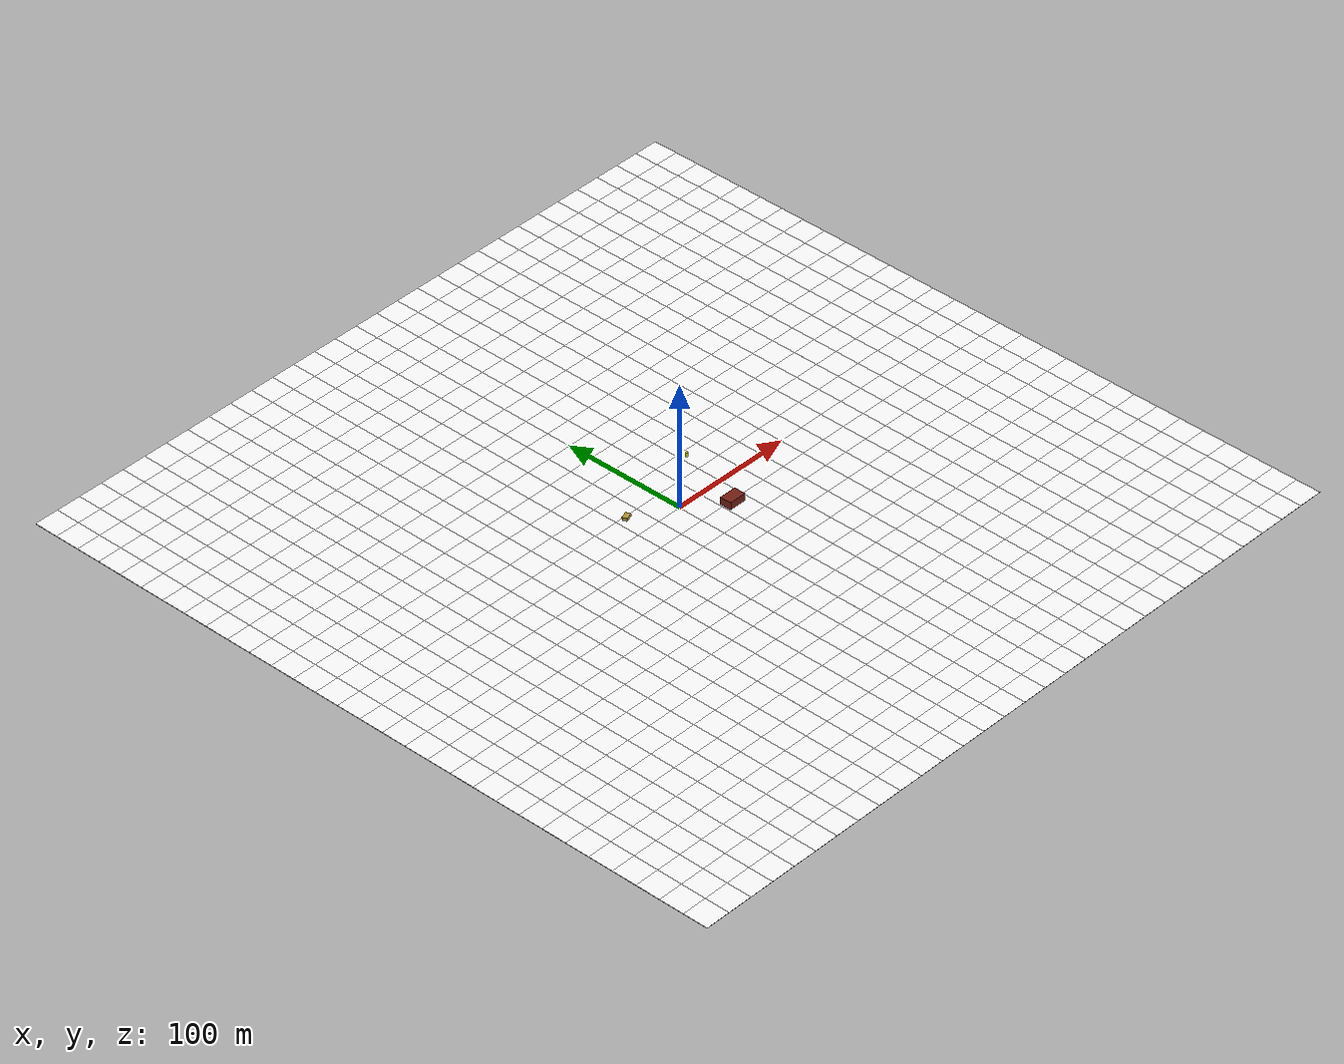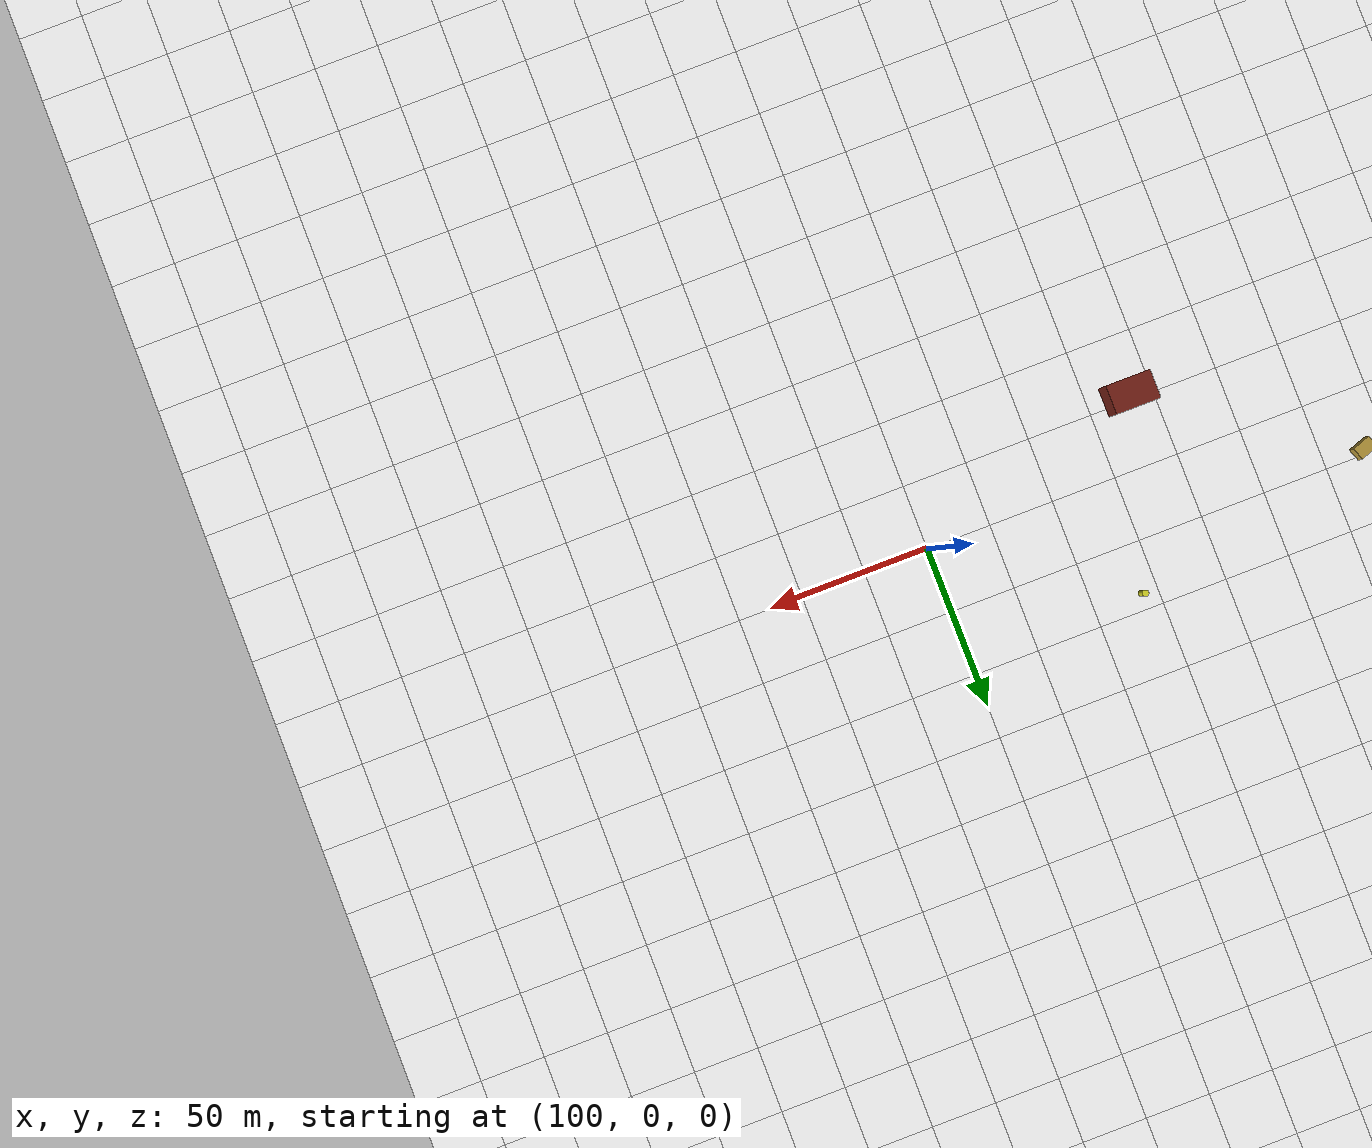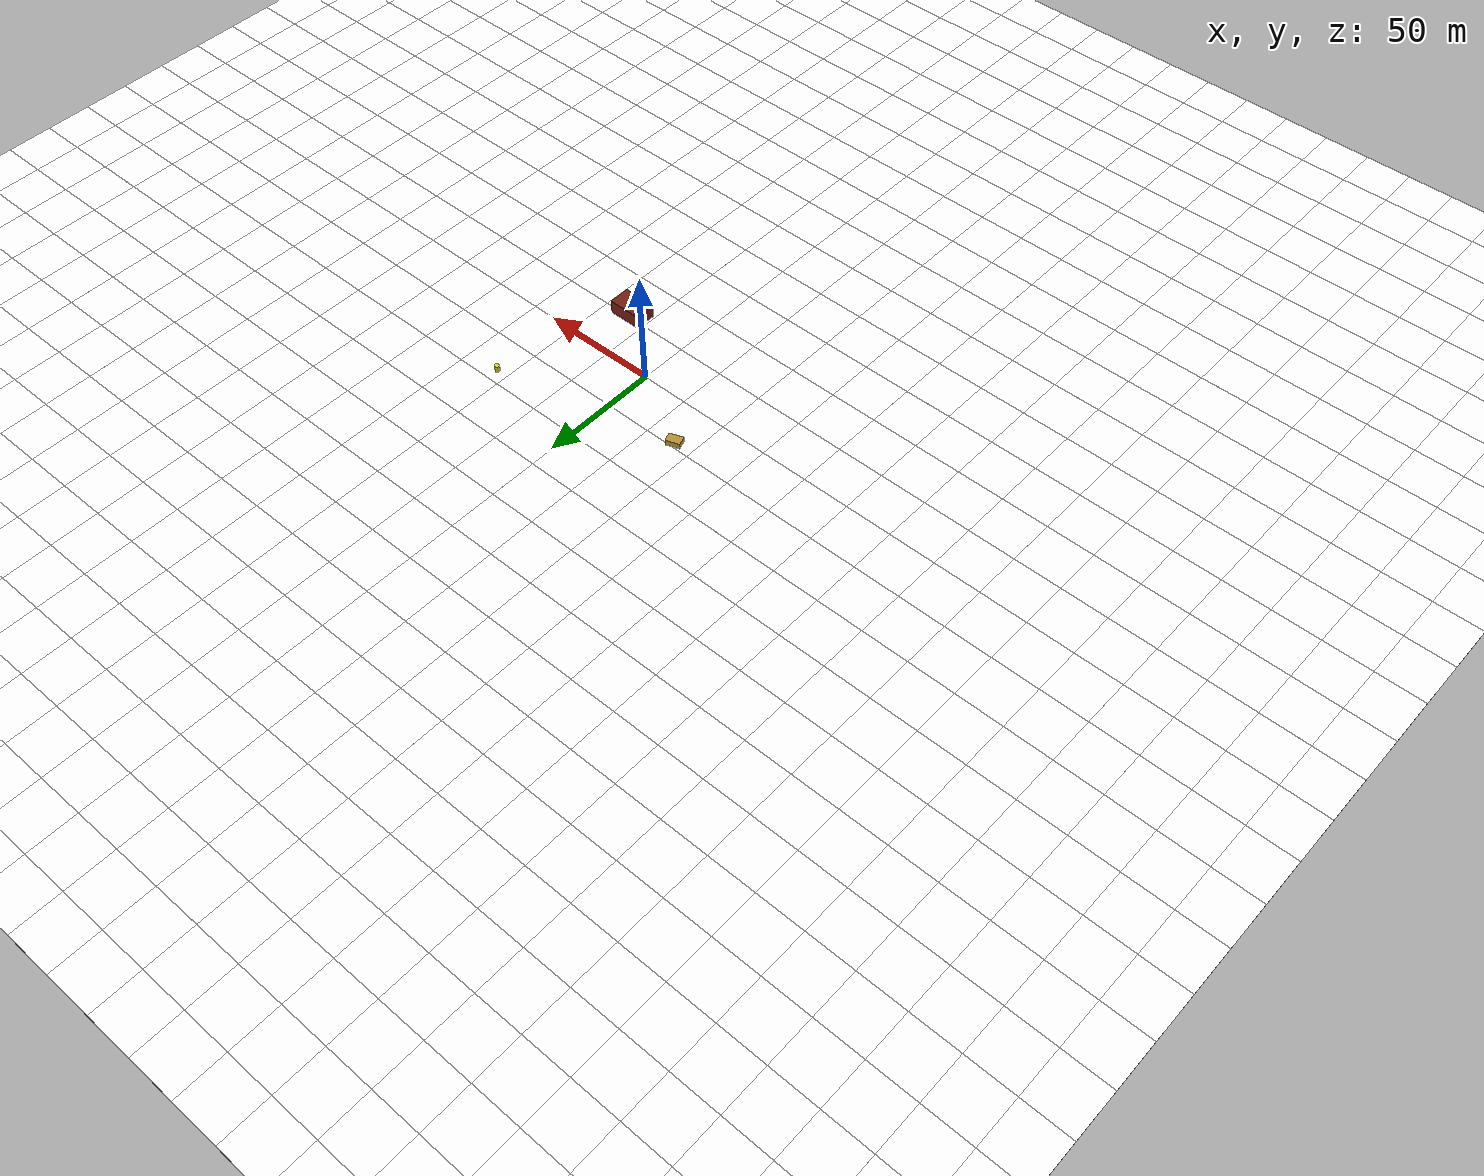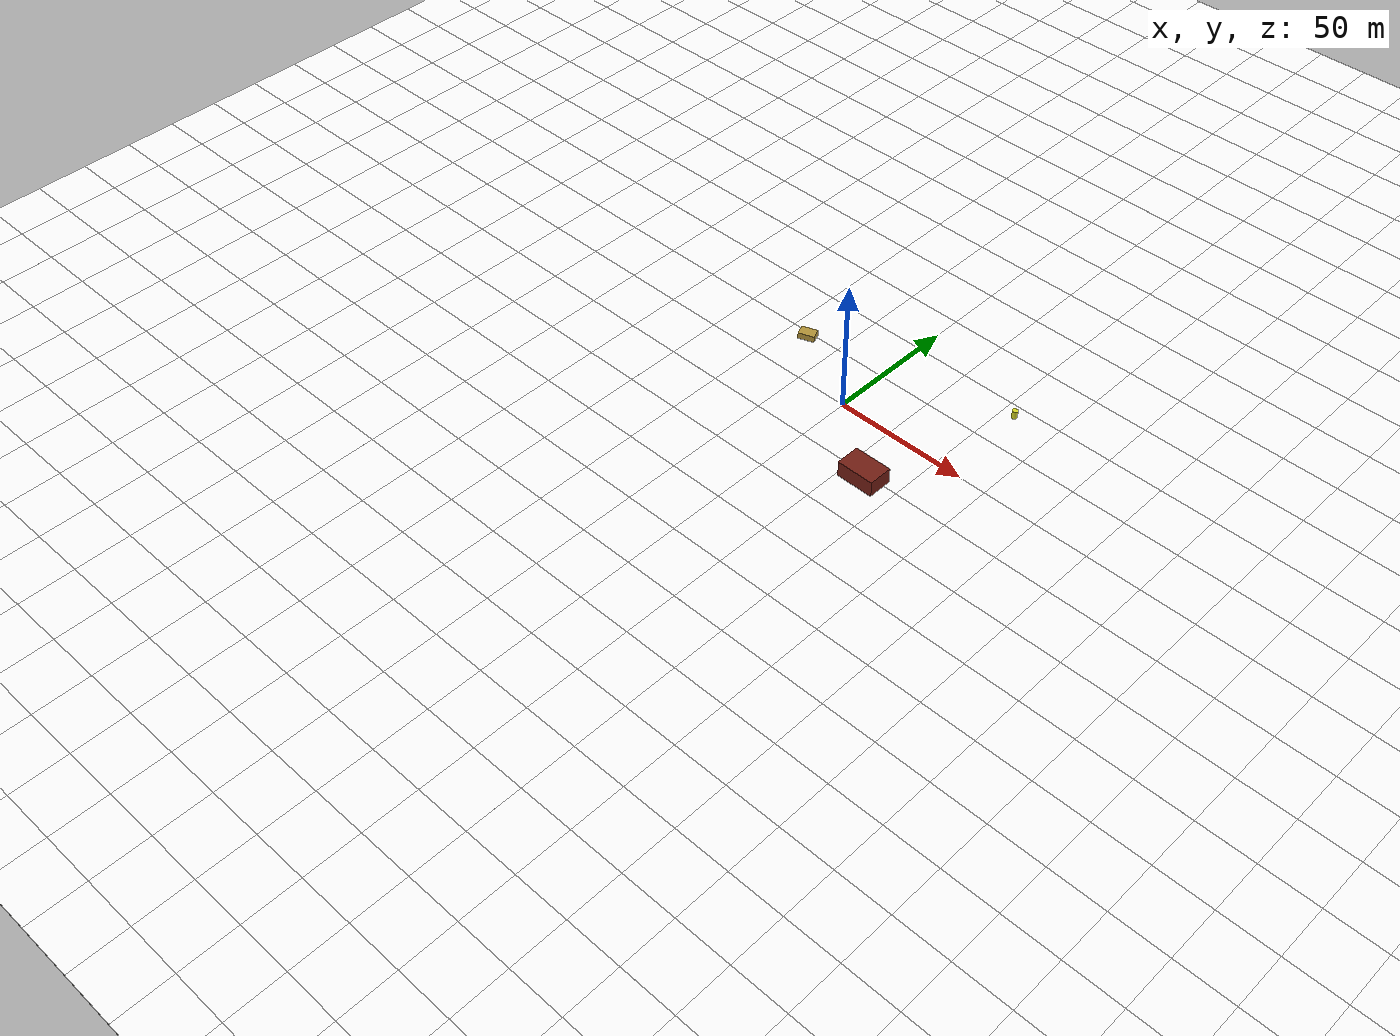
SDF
<?xml version="1.0" ?>
<sdf version="1.9">
  <world name="flat_rural_phototex_600m_noon">

    <scene>
      <ambient>0.550 0.550 0.550 1.000</ambient>
      <background>0.700 0.820 0.950 1.000</background>
      <shadows>false</shadows>
    </scene>

    <light name="sun" type="directional">
      <cast_shadows>false</cast_shadows>
      <pose>0 0 10 0 0 0</pose>
      <diffuse>0.9 0.86 0.76 1</diffuse>
      <specular>0.2 0.2 0.2 1</specular>
      <direction>-0.35 0.15 -0.92</direction>
    </light>

    <model name="databoss_ground">
      <static>true</static>
      <link name="ground_link">
        <collision name="ground_collision">
          <pose>0 0 -0.005 0 0 0</pose>
          <geometry>
            <box><size>600 600 0.01</size></box>
          </geometry>
        </collision>

        <collision name="ground_base_collision">
          <pose>0 0 -0.099 0 0 0</pose>
          <geometry>
            <box><size>600 600 0.2</size></box>
          </geometry>
        </collision>
        <visual name="ground_base">
          <pose>0 0 -0.099 0 0 0</pose>
          <geometry>
            <box><size>600 600 0.2</size></box>
          </geometry>
          <material>
            <ambient>0.350 0.350 0.320 1.000</ambient>
            <diffuse>0.350 0.350 0.320 1.000</diffuse>
            <specular>0.02 0.02 0.02 1</specular>
          </material>
        </visual>

        <visual name="tile_0_0">
          <pose>-290 -290 0.002 0 0 0</pose>
          <geometry>
            <box><size>20 20 0.004</size></box>
          </geometry>

          <material>
            <diffuse>1 1 1 1</diffuse>
            <specular>0.05 0.05 0.05 1</specular>
            <pbr>
              <metal>
                <albedo_map>file:///opt/databoss_px4_sim/generated_worlds/textures/ground_speckle_2048.png</albedo_map>
                <roughness>1.0</roughness>
                <metalness>0.0</metalness>
              </metal>
            </pbr>
          </material>
          <!-- material_id: tile_0_0 -->

        </visual>

        <visual name="tile_0_1">
          <pose>-290 -270 0.002 0 0 0</pose>
          <geometry>
            <box><size>20 20 0.004</size></box>
          </geometry>

          <material>
            <diffuse>1 1 1 1</diffuse>
            <specular>0.05 0.05 0.05 1</specular>
            <pbr>
              <metal>
                <albedo_map>file:///opt/databoss_px4_sim/generated_worlds/textures/ground_speckle_2048.png</albedo_map>
                <roughness>1.0</roughness>
                <metalness>0.0</metalness>
              </metal>
            </pbr>
          </material>
          <!-- material_id: tile_0_1 -->

        </visual>

        <visual name="tile_0_2">
          <pose>-290 -250 0.002 0 0 0</pose>
          <geometry>
            <box><size>20 20 0.004</size></box>
          </geometry>

          <material>
            <diffuse>1 1 1 1</diffuse>
            <specular>0.05 0.05 0.05 1</specular>
            <pbr>
              <metal>
                <albedo_map>file:///opt/databoss_px4_sim/generated_worlds/textures/ground_speckle_2048.png</albedo_map>
                <roughness>1.0</roughness>
                <metalness>0.0</metalness>
              </metal>
            </pbr>
          </material>
          <!-- material_id: tile_0_2 -->

        </visual>

        <visual name="tile_0_3">
          <pose>-290 -230 0.002 0 0 0</pose>
          <geometry>
            <box><size>20 20 0.004</size></box>
          </geometry>

          <material>
            <diffuse>1 1 1 1</diffuse>
            <specular>0.05 0.05 0.05 1</specular>
            <pbr>
              <metal>
                <albedo_map>file:///opt/databoss_px4_sim/generated_worlds/textures/ground_speckle_2048.png</albedo_map>
                <roughness>1.0</roughness>
                <metalness>0.0</metalness>
              </metal>
            </pbr>
          </material>
          <!-- material_id: tile_0_3 -->

        </visual>

        <visual name="tile_0_4">
          <pose>-290 -210 0.002 0 0 0</pose>
          <geometry>
            <box><size>20 20 0.004</size></box>
          </geometry>

          <material>
            <diffuse>1 1 1 1</diffuse>
            <specular>0.05 0.05 0.05 1</specular>
            <pbr>
              <metal>
                <albedo_map>file:///opt/databoss_px4_sim/generated_worlds/textures/ground_speckle_2048.png</albedo_map>
                <roughness>1.0</roughness>
                <metalness>0.0</metalness>
              </metal>
            </pbr>
          </material>
          <!-- material_id: tile_0_4 -->

        </visual>

        <visual name="tile_0_5">
          <pose>-290 -190 0.002 0 0 0</pose>
          <geometry>
            <box><size>20 20 0.004</size></box>
          </geometry>

          <material>
            <diffuse>1 1 1 1</diffuse>
            <specular>0.05 0.05 0.05 1</specular>
            <pbr>
              <metal>
                <albedo_map>file:///opt/databoss_px4_sim/generated_worlds/textures/ground_speckle_2048.png</albedo_map>
                <roughness>1.0</roughness>
                <metalness>0.0</metalness>
              </metal>
            </pbr>
          </material>
          <!-- material_id: tile_0_5 -->

        </visual>

        <visual name="tile_0_6">
          <pose>-290 -170 0.002 0 0 0</pose>
          <geometry>
            <box><size>20 20 0.004</size></box>
          </geometry>

          <material>
            <diffuse>1 1 1 1</diffuse>
            <specular>0.05 0.05 0.05 1</specular>
            <pbr>
              <metal>
                <albedo_map>file:///opt/databoss_px4_sim/generated_worlds/textures/ground_speckle_2048.png</albedo_map>
                <roughness>1.0</roughness>
                <metalness>0.0</metalness>
              </metal>
            </pbr>
          </material>
          <!-- material_id: tile_0_6 -->

        </visual>

        <visual name="tile_0_7">
          <pose>-290 -150 0.002 0 0 0</pose>
          <geometry>
            <box><size>20 20 0.004</size></box>
          </geometry>

          <material>
            <diffuse>1 1 1 1</diffuse>
            <specular>0.05 0.05 0.05 1</specular>
            <pbr>
              <metal>
                <albedo_map>file:///opt/databoss_px4_sim/generated_worlds/textures/ground_speckle_2048.png</albedo_map>
                <roughness>1.0</roughness>
                <metalness>0.0</metalness>
              </metal>
            </pbr>
          </material>
          <!-- material_id: tile_0_7 -->

        </visual>

        <visual name="tile_0_8">
          <pose>-290 -130 0.002 0 0 0</pose>
          <geometry>
            <box><size>20 20 0.004</size></box>
          </geometry>

          <material>
            <diffuse>1 1 1 1</diffuse>
            <specular>0.05 0.05 0.05 1</specular>
            <pbr>
              <metal>
                <albedo_map>file:///opt/databoss_px4_sim/generated_worlds/textures/ground_speckle_2048.png</albedo_map>
                <roughness>1.0</roughness>
                <metalness>0.0</metalness>
              </metal>
            </pbr>
          </material>
          <!-- material_id: tile_0_8 -->

        </visual>

        <visual name="tile_0_9">
          <pose>-290 -110 0.002 0 0 0</pose>
          <geometry>
            <box><size>20 20 0.004</size></box>
          </geometry>

          <material>
            <diffuse>1 1 1 1</diffuse>
            <specular>0.05 0.05 0.05 1</specular>
            <pbr>
              <metal>
                <albedo_map>file:///opt/databoss_px4_sim/generated_worlds/textures/ground_speckle_2048.png</albedo_map>
                <roughness>1.0</roughness>
                <metalness>0.0</metalness>
              </metal>
            </pbr>
          </material>
          <!-- material_id: tile_0_9 -->

        </visual>

        <visual name="tile_0_10">
          <pose>-290 -90 0.002 0 0 0</pose>
          <geometry>
            <box><size>20 20 0.004</size></box>
          </geometry>

          <material>
            <diffuse>1 1 1 1</diffuse>
            <specular>0.05 0.05 0.05 1</specular>
            <pbr>
              <metal>
                <albedo_map>file:///opt/databoss_px4_sim/generated_worlds/textures/ground_speckle_2048.png</albedo_map>
                <roughness>1.0</roughness>
                <metalness>0.0</metalness>
              </metal>
            </pbr>
          </material>
          <!-- material_id: tile_0_10 -->

        </visual>

        <visual name="tile_0_11">
          <pose>-290 -70 0.002 0 0 0</pose>
          <geometry>
            <box><size>20 20 0.004</size></box>
          </geometry>

          <material>
            <diffuse>1 1 1 1</diffuse>
            <specular>0.05 0.05 0.05 1</specular>
            <pbr>
              <metal>
                <albedo_map>file:///opt/databoss_px4_sim/generated_worlds/textures/ground_speckle_2048.png</albedo_map>
                <roughness>1.0</roughness>
                <metalness>0.0</metalness>
              </metal>
            </pbr>
          </material>
          <!-- material_id: tile_0_11 -->

        </visual>

        <visual name="tile_0_12">
          <pose>-290 -50 0.002 0 0 0</pose>
          <geometry>
            <box><size>20 20 0.004</size></box>
          </geometry>

          <material>
            <diffuse>1 1 1 1</diffuse>
            <specular>0.05 0.05 0.05 1</specular>
            <pbr>
              <metal>
                <albedo_map>file:///opt/databoss_px4_sim/generated_worlds/textures/ground_speckle_2048.png</albedo_map>
                <roughness>1.0</roughness>
                <metalness>0.0</metalness>
              </metal>
            </pbr>
          </material>
          <!-- material_id: tile_0_12 -->

        </visual>

        <visual name="tile_0_13">
          <pose>-290 -30 0.002 0 0 0</pose>
          <geometry>
            <box><size>20 20 0.004</size></box>
          </geometry>

          <material>
            <diffuse>1 1 1 1</diffuse>
            <specular>0.05 0.05 0.05 1</specular>
            <pbr>
              <metal>
                <albedo_map>file:///opt/databoss_px4_sim/generated_worlds/textures/ground_speckle_2048.png</albedo_map>
                <roughness>1.0</roughness>
                <metalness>0.0</metalness>
              </metal>
            </pbr>
          </material>
          <!-- material_id: tile_0_13 -->

        </visual>

        <visual name="tile_0_14">
          <pose>-290 -10 0.002 0 0 0</pose>
          <geometry>
            <box><size>20 20 0.004</size></box>
          </geometry>

          <material>
            <diffuse>1 1 1 1</diffuse>
            <specular>0.05 0.05 0.05 1</specular>
            <pbr>
              <metal>
                <albedo_map>file:///opt/databoss_px4_sim/generated_worlds/textures/ground_speckle_2048.png</albedo_map>
                <roughness>1.0</roughness>
                <metalness>0.0</metalness>
              </metal>
            </pbr>
          </material>
          <!-- material_id: tile_0_14 -->

        </visual>

        <visual name="tile_0_15">
          <pose>-290 10 0.002 0 0 0</pose>
          <geometry>
            <box><size>20 20 0.004</size></box>
          </geometry>

          <material>
            <diffuse>1 1 1 1</diffuse>
            <specular>0.05 0.05 0.05 1</specular>
            <pbr>
              <metal>
                <albedo_map>file:///opt/databoss_px4_sim/generated_worlds/textures/ground_speckle_2048.png</albedo_map>
                <roughness>1.0</roughness>
                <metalness>0.0</metalness>
              </metal>
            </pbr>
          </material>
          <!-- material_id: tile_0_15 -->

        </visual>

        <visual name="tile_0_16">
          <pose>-290 30 0.002 0 0 0</pose>
          <geometry>
            <box><size>20 20 0.004</size></box>
          </geometry>

          <material>
            <diffuse>1 1 1 1</diffuse>
            <specular>0.05 0.05 0.05 1</specular>
            <pbr>
              <metal>
                <albedo_map>file:///opt/databoss_px4_sim/generated_worlds/textures/ground_speckle_2048.png</albedo_map>
                <roughness>1.0</roughness>
                <metalness>0.0</metalness>
              </metal>
            </pbr>
          </material>
          <!-- material_id: tile_0_16 -->

        </visual>

        <visual name="tile_0_17">
          <pose>-290 50 0.002 0 0 0</pose>
          <geometry>
            <box><size>20 20 0.004</size></box>
          </geometry>

          <material>
            <diffuse>1 1 1 1</diffuse>
            <specular>0.05 0.05 0.05 1</specular>
            <pbr>
              <metal>
                <albedo_map>file:///opt/databoss_px4_sim/generated_worlds/textures/ground_speckle_2048.png</albedo_map>
                <roughness>1.0</roughness>
                <metalness>0.0</metalness>
              </metal>
            </pbr>
          </material>
          <!-- material_id: tile_0_17 -->

        </visual>

        <visual name="tile_0_18">
          <pose>-290 70 0.002 0 0 0</pose>
          <geometry>
            <box><size>20 20 0.004</size></box>
          </geometry>

          <material>
            <diffuse>1 1 1 1</diffuse>
            <specular>0.05 0.05 0.05 1</specular>
            <pbr>
              <metal>
                <albedo_map>file:///opt/databoss_px4_sim/generated_worlds/textures/ground_speckle_2048.png</albedo_map>
                <roughness>1.0</roughness>
                <metalness>0.0</metalness>
              </metal>
            </pbr>
          </material>
          <!-- material_id: tile_0_18 -->

        </visual>

        <visual name="tile_0_19">
          <pose>-290 90 0.002 0 0 0</pose>
          <geometry>
            <box><size>20 20 0.004</size></box>
          </geometry>

          <material>
            <diffuse>1 1 1 1</diffuse>
            <specular>0.05 0.05 0.05 1</specular>
            <pbr>
              <metal>
                <albedo_map>file:///opt/databoss_px4_sim/generated_worlds/textures/ground_speckle_2048.png</albedo_map>
                <roughness>1.0</roughness>
                <metalness>0.0</metalness>
              </metal>
            </pbr>
          </material>
          <!-- material_id: tile_0_19 -->

        </visual>

        <visual name="tile_0_20">
          <pose>-290 110 0.002 0 0 0</pose>
          <geometry>
            <box><size>20 20 0.004</size></box>
          </geometry>

          <material>
            <diffuse>1 1 1 1</diffuse>
            <specular>0.05 0.05 0.05 1</specular>
            <pbr>
              <metal>
                <albedo_map>file:///opt/databoss_px4_sim/generated_worlds/textures/ground_speckle_2048.png</albedo_map>
                <roughness>1.0</roughness>
                <metalness>0.0</metalness>
              </metal>
            </pbr>
          </material>
          <!-- material_id: tile_0_20 -->

        </visual>

        <visual name="tile_0_21">
          <pose>-290 130 0.002 0 0 0</pose>
          <geometry>
            <box><size>20 20 0.004</size></box>
          </geometry>

          <material>
            <diffuse>1 1 1 1</diffuse>
            <specular>0.05 0.05 0.05 1</specular>
            <pbr>
              <metal>
                <albedo_map>file:///opt/databoss_px4_sim/generated_worlds/textures/ground_speckle_2048.png</albedo_map>
                <roughness>1.0</roughness>
                <metalness>0.0</metalness>
              </metal>
            </pbr>
          </material>
          <!-- material_id: tile_0_21 -->

        </visual>

        <visual name="tile_0_22">
          <pose>-290 150 0.002 0 0 0</pose>
          <geometry>
            <box><size>20 20 0.004</size></box>
          </geometry>

          <material>
            <diffuse>1 1 1 1</diffuse>
            <specular>0.05 0.05 0.05 1</specular>
            <pbr>
              <metal>
                <albedo_map>file:///opt/databoss_px4_sim/generated_worlds/textures/ground_speckle_2048.png</albedo_map>
                <roughness>1.0</roughness>
                <metalness>0.0</metalness>
              </metal>
            </pbr>
          </material>
          <!-- material_id: tile_0_22 -->

        </visual>

        <visual name="tile_0_23">
          <pose>-290 170 0.002 0 0 0</pose>
          <geometry>
            <box><size>20 20 0.004</size></box>
          </geometry>

          <material>
            <diffuse>1 1 1 1</diffuse>
            <specular>0.05 0.05 0.05 1</specular>
            <pbr>
              <metal>
                <albedo_map>file:///opt/databoss_px4_sim/generated_worlds/textures/ground_speckle_2048.png</albedo_map>
                <roughness>1.0</roughness>
                <metalness>0.0</metalness>
              </metal>
            </pbr>
          </material>
          <!-- material_id: tile_0_23 -->

        </visual>

        <visual name="tile_0_24">
          <pose>-290 190 0.002 0 0 0</pose>
          <geometry>
            <box><size>20 20 0.004</size></box>
          </geometry>

          <material>
            <diffuse>1 1 1 1</diffuse>
            <specular>0.05 0.05 0.05 1</specular>
            <pbr>
              <metal>
                <albedo_map>file:///opt/databoss_px4_sim/generated_worlds/textures/ground_speckle_2048.png</albedo_map>
                <roughness>1.0</roughness>
                <metalness>0.0</metalness>
              </metal>
            </pbr>
          </material>
          <!-- material_id: tile_0_24 -->

        </visual>

        <visual name="tile_0_25">
          <pose>-290 210 0.002 0 0 0</pose>
          <geometry>
            <box><size>20 20 0.004</size></box>
          </geometry>

          <material>
            <diffuse>1 1 1 1</diffuse>
            <specular>0.05 0.05 0.05 1</specular>
            <pbr>
              <metal>
                <albedo_map>file:///opt/databoss_px4_sim/generated_worlds/textures/ground_speckle_2048.png</albedo_map>
                <roughness>1.0</roughness>
                <metalness>0.0</metalness>
              </metal>
            </pbr>
          </material>
          <!-- material_id: tile_0_25 -->

        </visual>

        <visual name="tile_0_26">
          <pose>-290 230 0.002 0 0 0</pose>
          <geometry>
            <box><size>20 20 0.004</size></box>
          </geometry>

          <material>
            <diffuse>1 1 1 1</diffuse>
            <specular>0.05 0.05 0.05 1</specular>
            <pbr>
              <metal>
                <albedo_map>file:///opt/databoss_px4_sim/generated_worlds/textures/ground_speckle_2048.png</albedo_map>
                <roughness>1.0</roughness>
                <metalness>0.0</metalness>
              </metal>
            </pbr>
          </material>
          <!-- material_id: tile_0_26 -->

        </visual>

        <visual name="tile_0_27">
          <pose>-290 250 0.002 0 0 0</pose>
          <geometry>
            <box><size>20 20 0.004</size></box>
          </geometry>

          <material>
            <diffuse>1 1 1 1</diffuse>
            <specular>0.05 0.05 0.05 1</specular>
            <pbr>
              <metal>
                <albedo_map>file:///opt/databoss_px4_sim/generated_worlds/textures/ground_speckle_2048.png</albedo_map>
                <roughness>1.0</roughness>
                <metalness>0.0</metalness>
              </metal>
            </pbr>
          </material>
          <!-- material_id: tile_0_27 -->

        </visual>

        <visual name="tile_0_28">
          <pose>-290 270 0.002 0 0 0</pose>
          <geometry>
            <box><size>20 20 0.004</size></box>
          </geometry>

          <material>
            <diffuse>1 1 1 1</diffuse>
            <specular>0.05 0.05 0.05 1</specular>
            <pbr>
              <metal>
                <albedo_map>file:///opt/databoss_px4_sim/generated_worlds/textures/ground_speckle_2048.png</albedo_map>
                <roughness>1.0</roughness>
                <metalness>0.0</metalness>
              </metal>
            </pbr>
          </material>
          <!-- material_id: tile_0_28 -->

        </visual>

        <visual name="tile_0_29">
          <pose>-290 290 0.002 0 0 0</pose>
          <geometry>
            <box><size>20 20 0.004</size></box>
          </geometry>

          <material>
            <diffuse>1 1 1 1</diffuse>
            <specular>0.05 0.05 0.05 1</specular>
            <pbr>
              <metal>
                <albedo_map>file:///opt/databoss_px4_sim/generated_worlds/textures/ground_speckle_2048.png</albedo_map>
                <roughness>1.0</roughness>
                <metalness>0.0</metalness>
              </metal>
            </pbr>
          </material>
          <!-- material_id: tile_0_29 -->

        </visual>

        <visual name="tile_1_0">
          <pose>-270 -290 0.002 0 0 0</pose>
          <geometry>
            <box><size>20 20 0.004</size></box>
          </geometry>

          <material>
            <diffuse>1 1 1 1</diffuse>
            <specular>0.05 0.05 0.05 1</specular>
            <pbr>
              <metal>
                <albedo_map>file:///opt/databoss_px4_sim/generated_worlds/textures/ground_speckle_2048.png</albedo_map>
                <roughness>1.0</roughness>
                <metalness>0.0</metalness>
              </metal>
            </pbr>
          </material>
          <!-- material_id: tile_1_0 -->

        </visual>

        <visual name="tile_1_1">
          <pose>-270 -270 0.002 0 0 0</pose>
          <geometry>
            <box><size>20 20 0.004</size></box>
          </geometry>

          <material>
            <diffuse>1 1 1 1</diffuse>
            <specular>0.05 0.05 0.05 1</specular>
            <pbr>
              <metal>
                <albedo_map>file:///opt/databoss_px4_sim/generated_worlds/textures/ground_speckle_2048.png</albedo_map>
                <roughness>1.0</roughness>
                <metalness>0.0</metalness>
              </metal>
            </pbr>
          </material>
          <!-- material_id: tile_1_1 -->

        </visual>

        <visual name="tile_1_2">
          <pose>-270 -250 0.002 0 0 0</pose>
          <geometry>
            <box><size>20 20 0.004</size></box>
          </geometry>

          <material>
            <diffuse>1 1 1 1</diffuse>
            <specular>0.05 0.05 0.05 1</specular>
            <pbr>
              <metal>
                <albedo_map>file:///opt/databoss_px4_sim/generated_worlds/textures/ground_speckle_2048.png</albedo_map>
                <roughness>1.0</roughness>
                <metalness>0.0</metalness>
              </metal>
            </pbr>
          </material>
          <!-- material_id: tile_1_2 -->

        </visual>

        <visual name="tile_1_3">
          <pose>-270 -230 0.002 0 0 0</pose>
          <geometry>
            <box><size>20 20 0.004</size></box>
          </geometry>

          <material>
            <diffuse>1 1 1 1</diffuse>
            <specular>0.05 0.05 0.05 1</specular>
            <pbr>
              <metal>
                <albedo_map>file:///opt/databoss_px4_sim/generated_worlds/textures/ground_speckle_2048.png</albedo_map>
                <roughness>1.0</roughness>
                <metalness>0.0</metalness>
              </metal>
            </pbr>
          </material>
          <!-- material_id: tile_1_3 -->

        </visual>

        <visual name="tile_1_4">
          <pose>-270 -210 0.002 0 0 0</pose>
          <geometry>
            <box><size>20 20 0.004</size></box>
          </geometry>

          <material>
            <diffuse>1 1 1 1</diffuse>
            <specular>0.05 0.05 0.05 1</specular>
            <pbr>
              <metal>
                <albedo_map>file:///opt/databoss_px4_sim/generated_worlds/textures/ground_speckle_2048.png</albedo_map>
                <roughness>1.0</roughness>
                <metalness>0.0</metalness>
              </metal>
            </pbr>
          </material>
          <!-- material_id: tile_1_4 -->

        </visual>

        <visual name="tile_1_5">
          <pose>-270 -190 0.002 0 0 0</pose>
          <geometry>
            <box><size>20 20 0.004</size></box>
          </geometry>

          <material>
            <diffuse>1 1 1 1</diffuse>
            <specular>0.05 0.05 0.05 1</specular>
            <pbr>
              <metal>
                <albedo_map>file:///opt/databoss_px4_sim/generated_worlds/textures/ground_speckle_2048.png</albedo_map>
                <roughness>1.0</roughness>
                <metalness>0.0</metalness>
              </metal>
            </pbr>
          </material>
          <!-- material_id: tile_1_5 -->

        </visual>

        <visual name="tile_1_6">
          <pose>-270 -170 0.002 0 0 0</pose>
          <geometry>
            <box><size>20 20 0.004</size></box>
          </geometry>

          <material>
            <diffuse>1 1 1 1</diffuse>
            <specular>0.05 0.05 0.05 1</specular>
            <pbr>
              <metal>
                <albedo_map>file:///opt/databoss_px4_sim/generated_worlds/textures/ground_speckle_2048.png</albedo_map>
                <roughness>1.0</roughness>
                <metalness>0.0</metalness>
              </metal>
            </pbr>
          </material>
          <!-- material_id: tile_1_6 -->

        </visual>

        <visual name="tile_1_7">
          <pose>-270 -150 0.002 0 0 0</pose>
          <geometry>
            <box><size>20 20 0.004</size></box>
          </geometry>

          <material>
            <diffuse>1 1 1 1</diffuse>
            <specular>0.05 0.05 0.05 1</specular>
            <pbr>
              <metal>
                <albedo_map>file:///opt/databoss_px4_sim/generated_worlds/textures/ground_speckle_2048.png</albedo_map>
                <roughness>1.0</roughness>
                <metalness>0.0</metalness>
              </metal>
            </pbr>
          </material>
          <!-- material_id: tile_1_7 -->

        </visual>

        <visual name="tile_1_8">
          <pose>-270 -130 0.002 0 0 0</pose>
          <geometry>
            <box><size>20 20 0.004</size></box>
          </geometry>

          <material>
            <diffuse>1 1 1 1</diffuse>
            <specular>0.05 0.05 0.05 1</specular>
            <pbr>
              <metal>
                <albedo_map>file:///opt/databoss_px4_sim/generated_worlds/textures/ground_speckle_2048.png</albedo_map>
                <roughness>1.0</roughness>
                <metalness>0.0</metalness>
              </metal>
            </pbr>
          </material>
          <!-- material_id: tile_1_8 -->

        </visual>

        <visual name="tile_1_9">
          <pose>-270 -110 0.002 0 0 0</pose>
          <geometry>
            <box><size>20 20 0.004</size></box>
          </geometry>

          <material>
            <diffuse>1 1 1 1</diffuse>
            <specular>0.05 0.05 0.05 1</specular>
            <pbr>
              <metal>
                <albedo_map>file:///opt/databoss_px4_sim/generated_worlds/textures/ground_speckle_2048.png</albedo_map>
                <roughness>1.0</roughness>
                <metalness>0.0</metalness>
              </metal>
            </pbr>
          </material>
          <!-- material_id: tile_1_9 -->

        </visual>

        <visual name="tile_1_10">
          <pose>-270 -90 0.002 0 0 0</pose>
          <geometry>
            <box><size>20 20 0.004</size></box>
          </geometry>

          <material>
            <diffuse>1 1 1 1</diffuse>
            <specular>0.05 0.05 0.05 1</specular>
            <pbr>
              <metal>
                <albedo_map>file:///opt/databoss_px4_sim/generated_worlds/textures/ground_speckle_2048.png</albedo_map>
                <roughness>1.0</roughness>
                <metalness>0.0</metalness>
              </metal>
            </pbr>
          </material>
          <!-- material_id: tile_1_10 -->

        </visual>

        <visual name="tile_1_11">
          <pose>-270 -70 0.002 0 0 0</pose>
          <geometry>
            <box><size>20 20 0.004</size></box>
          </geometry>

          <material>
            <diffuse>1 1 1 1</diffuse>
            <specular>0.05 0.05 0.05 1</specular>
            <pbr>
              <metal>
                <albedo_map>file:///opt/databoss_px4_sim/generated_worlds/textures/ground_speckle_2048.png</albedo_map>
                <roughness>1.0</roughness>
                <metalness>0.0</metalness>
              </metal>
            </pbr>
          </material>
          <!-- material_id: tile_1_11 -->

        </visual>

        <visual name="tile_1_12">
          <pose>-270 -50 0.002 0 0 0</pose>
          <geometry>
            <box><size>20 20 0.004</size></box>
          </geometry>

          <material>
            <diffuse>1 1 1 1</diffuse>
            <specular>0.05 0.05 0.05 1</specular>
            <pbr>
              <metal>
                <albedo_map>file:///opt/databoss_px4_sim/generated_worlds/textures/ground_speckle_2048.png</albedo_map>
                <roughness>1.0</roughness>
                <metalness>0.0</metalness>
              </metal>
            </pbr>
          </material>
          <!-- material_id: tile_1_12 -->

        </visual>

        <visual name="tile_1_13">
          <pose>-270 -30 0.002 0 0 0</pose>
          <geometry>
            <box><size>20 20 0.004</size></box>
          </geometry>

          <material>
            <diffuse>1 1 1 1</diffuse>
            <specular>0.05 0.05 0.05 1</specular>
            <pbr>
              <metal>
                <albedo_map>file:///opt/databoss_px4_sim/generated_worlds/textures/ground_speckle_2048.png</albedo_map>
                <roughness>1.0</roughness>
                <metalness>0.0</metalness>
              </metal>
            </pbr>
          </material>
          <!-- material_id: tile_1_13 -->

        </visual>

        <visual name="tile_1_14">
          <pose>-270 -10 0.002 0 0 0</pose>
          <geometry>
            <box><size>20 20 0.004</size></box>
          </geometry>

          <material>
            <diffuse>1 1 1 1</diffuse>
            <specular>0.05 0.05 0.05 1</specular>
            <pbr>
              <metal>
                <albedo_map>file:///opt/databoss_px4_sim/generated_worlds/textures/ground_speckle_2048.png</albedo_map>
                <roughness>1.0</roughness>
                <metalness>0.0</metalness>
              </metal>
            </pbr>
          </material>
          <!-- material_id: tile_1_14 -->

        </visual>

        <visual name="tile_1_15">
          <pose>-270 10 0.002 0 0 0</pose>
          <geometry>
            <box><size>20 20 0.004</size></box>
          </geometry>

          <material>
            <diffuse>1 1 1 1</diffuse>
            <specular>0.05 0.05 0.05 1</specular>
            <pbr>
              <metal>
                <albedo_map>file:///opt/databoss_px4_sim/generated_worlds/textures/ground_speckle_2048.png</albedo_map>
                <roughness>1.0</roughness>
                <metalness>0.0</metalness>
              </metal>
            </pbr>
          </material>
          <!-- material_id: tile_1_15 -->

        </visual>

        <visual name="tile_1_16">
          <pose>-270 30 0.002 0 0 0</pose>
          <geometry>
            <box><size>20 20 0.004</size></box>
          </geometry>

          <material>
            <diffuse>1 1 1 1</diffuse>
            <specular>0.05 0.05 0.05 1</specular>
            <pbr>
              <metal>
                <albedo_map>file:///opt/databoss_px4_sim/generated_worlds/textures/ground_speckle_2048.png</albedo_map>
                <roughness>1.0</roughness>
                <metalness>0.0</metalness>
              </metal>
            </pbr>
          </material>
          <!-- material_id: tile_1_16 -->

        </visual>

        <visual name="tile_1_17">
          <pose>-270 50 0.002 0 0 0</pose>
          <geometry>
            <box><size>20 20 0.004</size></box>
          </geometry>

          <material>
            <diffuse>1 1 1 1</diffuse>
            <specular>0.05 0.05 0.05 1</specular>
            <pbr>
              <metal>
                <albedo_map>file:///opt/databoss_px4_sim/generated_worlds/textures/ground_speckle_2048.png</albedo_map>
                <roughness>1.0</roughness>
                <metalness>0.0</metalness>
              </metal>
            </pbr>
          </material>
          <!-- material_id: tile_1_17 -->

        </visual>

        <visual name="tile_1_18">
          <pose>-270 70 0.002 0 0 0</pose>
          <geometry>
            <box><size>20 20 0.004</size></box>
          </geometry>

          <material>
            <diffuse>1 1 1 1</diffuse>
            <specular>0.05 0.05 0.05 1</specular>
            <pbr>
              <metal>
                <albedo_map>file:///opt/databoss_px4_sim/generated_worlds/textures/ground_speckle_2048.png</albedo_map>
                <roughness>1.0</roughness>
                <metalness>0.0</metalness>
              </metal>
            </pbr>
          </material>
          <!-- material_id: tile_1_18 -->

        </visual>

        <visual name="tile_1_19">
          <pose>-270 90 0.002 0 0 0</pose>
          <geometry>
            <box><size>20 20 0.004</size></box>
          </geometry>

          <material>
            <diffuse>1 1 1 1</diffuse>
            <specular>0.05 0.05 0.05 1</specular>
            <pbr>
              <metal>
                <albedo_map>file:///opt/databoss_px4_sim/generated_worlds/textures/ground_speckle_2048.png</albedo_map>
                <roughness>1.0</roughness>
                <metalness>0.0</metalness>
              </metal>
            </pbr>
          </material>
          <!-- material_id: tile_1_19 -->

        </visual>

        <visual name="tile_1_20">
          <pose>-270 110 0.002 0 0 0</pose>
          <geometry>
            <box><size>20 20 0.004</size></box>
          </geometry>

          <material>
            <diffuse>1 1 1 1</diffuse>
            <specular>0.05 0.05 0.05 1</specular>
            <pbr>
              <metal>
                <albedo_map>file:///opt/databoss_px4_sim/generated_worlds/textures/ground_speckle_2048.png</albedo_map>
                <roughness>1.0</roughness>
                <metalness>0.0</metalness>
              </metal>
            </pbr>
          </material>
          <!-- material_id: tile_1_20 -->

        </visual>

        <visual name="tile_1_21">
          <pose>-270 130 0.002 0 0 0</pose>
          <geometry>
            <box><size>20 20 0.004</size></box>
          </geometry>

          <material>
            <diffuse>1 1 1 1</diffuse>
            <specular>0.05 0.05 0.05 1</specular>
            <pbr>
              <metal>
                <albedo_map>file:///opt/databoss_px4_sim/generated_worlds/textures/ground_speckle_2048.png</albedo_map>
                <roughness>1.0</roughness>
                <metalness>0.0</metalness>
              </metal>
            </pbr>
          </material>
          <!-- material_id: tile_1_21 -->

        </visual>

        <visual name="tile_1_22">
          <pose>-270 150 0.002 0 0 0</pose>
          <geometry>
            <box><size>20 20 0.004</size></box>
          </geometry>

          <material>
            <diffuse>1 1 1 1</diffuse>
            <specular>0.05 0.05 0.05 1</specular>
            <pbr>
              <metal>
                <albedo_map>file:///opt/databoss_px4_sim/generated_worlds/textures/ground_speckle_2048.png</albedo_map>
                <roughness>1.0</roughness>
                <metalness>0.0</metalness>
              </metal>
            </pbr>
          </material>
          <!-- material_id: tile_1_22 -->

        </visual>

        <visual name="tile_1_23">
          <pose>-270 170 0.002 0 0 0</pose>
          <geometry>
            <box><size>20 20 0.004</size></box>
          </geometry>

          <material>
            <diffuse>1 1 1 1</diffuse>
            <specular>0.05 0.05 0.05 1</specular>
            <pbr>
              <metal>
                <albedo_map>file:///opt/databoss_px4_sim/generated_worlds/textures/ground_speckle_2048.png</albedo_map>
                <roughness>1.0</roughness>
                <metalness>0.0</metalness>
              </metal>
            </pbr>
          </material>
          <!-- material_id: tile_1_23 -->

        </visual>

        <visual name="tile_1_24">
          <pose>-270 190 0.002 0 0 0</pose>
          <geometry>
            <box><size>20 20 0.004</size></box>
          </geometry>

          <material>
            <diffuse>1 1 1 1</diffuse>
            <specular>0.05 0.05 0.05 1</specular>
            <pbr>
              <metal>
                <albedo_map>file:///opt/databoss_px4_sim/generated_worlds/textures/ground_speckle_2048.png</albedo_map>
                <roughness>1.0</roughness>
                <metalness>0.0</metalness>
              </metal>
            </pbr>
          </material>
          <!-- material_id: tile_1_24 -->

        </visual>

        <visual name="tile_1_25">
          <pose>-270 210 0.002 0 0 0</pose>
          <geometry>
            <box><size>20 20 0.004</size></box>
          </geometry>

          <material>
            <diffuse>1 1 1 1</diffuse>
            <specular>0.05 0.05 0.05 1</specular>
            <pbr>
              <metal>
                <albedo_map>file:///opt/databoss_px4_sim/generated_worlds/textures/ground_speckle_2048.png</albedo_map>
                <roughness>1.0</roughness>
                <metalness>0.0</metalness>
              </metal>
            </pbr>
          </material>
          <!-- material_id: tile_1_25 -->

        </visual>

        <visual name="tile_1_26">
          <pose>-270 230 0.002 0 0 0</pose>
          <geometry>
            <box><size>20 20 0.004</size></box>
          </geometry>

          <material>
            <diffuse>1 1 1 1</diffuse>
            <specular>0.05 0.05 0.05 1</specular>
            <pbr>
              <metal>
                <albedo_map>file:///opt/databoss_px4_sim/generated_worlds/textures/ground_speckle_2048.png</albedo_map>
                <roughness>1.0</roughness>
                <metalness>0.0</metalness>
              </metal>
            </pbr>
          </material>
          <!-- material_id: tile_1_26 -->

        </visual>

        <visual name="tile_1_27">
          <pose>-270 250 0.002 0 0 0</pose>
          <geometry>
            <box><size>20 20 0.004</size></box>
          </geometry>

          <material>
            <diffuse>1 1 1 1</diffuse>
            <specular>0.05 0.05 0.05 1</specular>
            <pbr>
              <metal>
                <albedo_map>file:///opt/databoss_px4_sim/generated_worlds/textures/ground_speckle_2048.png</albedo_map>
                <roughness>1.0</roughness>
                <metalness>0.0</metalness>
              </metal>
            </pbr>
          </material>
          <!-- material_id: tile_1_27 -->

        </visual>

        <visual name="tile_1_28">
          <pose>-270 270 0.002 0 0 0</pose>
          <geometry>
            <box><size>20 20 0.004</size></box>
          </geometry>

          <material>
            <diffuse>1 1 1 1</diffuse>
            <specular>0.05 0.05 0.05 1</specular>
            <pbr>
              <metal>
                <albedo_map>file:///opt/databoss_px4_sim/generated_worlds/textures/ground_speckle_2048.png</albedo_map>
                <roughness>1.0</roughness>
                <metalness>0.0</metalness>
              </metal>
            </pbr>
          </material>
          <!-- material_id: tile_1_28 -->

        </visual>

        <visual name="tile_1_29">
          <pose>-270 290 0.002 0 0 0</pose>
          <geometry>
            <box><size>20 20 0.004</size></box>
          </geometry>

          <material>
            <diffuse>1 1 1 1</diffuse>
            <specular>0.05 0.05 0.05 1</specular>
            <pbr>
              <metal>
                <albedo_map>file:///opt/databoss_px4_sim/generated_worlds/textures/ground_speckle_2048.png</albedo_map>
                <roughness>1.0</roughness>
                <metalness>0.0</metalness>
              </metal>
            </pbr>
          </material>
          <!-- material_id: tile_1_29 -->

        </visual>

        <visual name="tile_2_0">
          <pose>-250 -290 0.002 0 0 0</pose>
          <geometry>
            <box><size>20 20 0.004</size></box>
          </geometry>

          <material>
            <diffuse>1 1 1 1</diffuse>
            <specular>0.05 0.05 0.05 1</specular>
            <pbr>
              <metal>
                <albedo_map>file:///opt/databoss_px4_sim/generated_worlds/textures/ground_speckle_2048.png</albedo_map>
                <roughness>1.0</roughness>
                <metalness>0.0</metalness>
              </metal>
            </pbr>
          </material>
          <!-- material_id: tile_2_0 -->

        </visual>

        <visual name="tile_2_1">
          <pose>-250 -270 0.002 0 0 0</pose>
          <geometry>
            <box><size>20 20 0.004</size></box>
          </geometry>

          <material>
            <diffuse>1 1 1 1</diffuse>
            <specular>0.05 0.05 0.05 1</specular>
            <pbr>
              <metal>
                <albedo_map>file:///opt/databoss_px4_sim/generated_worlds/textures/ground_speckle_2048.png</albedo_map>
                <roughness>1.0</roughness>
                <metalness>0.0</metalness>
              </metal>
            </pbr>
          </material>
          <!-- material_id: tile_2_1 -->

        </visual>

        <visual name="tile_2_2">
          <pose>-250 -250 0.002 0 0 0</pose>
          <geometry>
            <box><size>20 20 0.004</size></box>
          </geometry>

          <material>
            <diffuse>1 1 1 1</diffuse>
            <specular>0.05 0.05 0.05 1</specular>
            <pbr>
              <metal>
                <albedo_map>file:///opt/databoss_px4_sim/generated_worlds/textures/ground_speckle_2048.png</albedo_map>
                <roughness>1.0</roughness>
                <metalness>0.0</metalness>
              </metal>
            </pbr>
          </material>
          <!-- material_id: tile_2_2 -->

        </visual>

        <visual name="tile_2_3">
          <pose>-250 -230 0.002 0 0 0</pose>
          <geometry>
            <box><size>20 20 0.004</size></box>
          </geometry>

          <material>
            <diffuse>1 1 1 1</diffuse>
            <specular>0.05 0.05 0.05 1</specular>
            <pbr>
              <metal>
                <albedo_map>file:///opt/databoss_px4_sim/generated_worlds/textures/ground_speckle_2048.png</albedo_map>
                <roughness>1.0</roughness>
                <metalness>0.0</metalness>
              </metal>
            </pbr>
          </material>
          <!-- material_id: tile_2_3 -->

        </visual>

        <visual name="tile_2_4">
          <pose>-250 -210 0.002 0 0 0</pose>
          <geometry>
            <box><size>20 20 0.004</size></box>
          </geometry>

          <material>
            <diffuse>1 1 1 1</diffuse>
            <specular>0.05 0.05 0.05 1</specular>
            <pbr>
              <metal>
                <albedo_map>file:///opt/databoss_px4_sim/generated_worlds/textures/ground_speckle_2048.png</albedo_map>
                <roughness>1.0</roughness>
                <metalness>0.0</metalness>
              </metal>
            </pbr>
          </material>
          <!-- material_id: tile_2_4 -->

        </visual>

        <visual name="tile_2_5">
          <pose>-250 -190 0.002 0 0 0</pose>
          <geometry>
            <box><size>20 20 0.004</size></box>
          </geometry>

          <material>
            <diffuse>1 1 1 1</diffuse>
            <specular>0.05 0.05 0.05 1</specular>
            <pbr>
              <metal>
                <albedo_map>file:///opt/databoss_px4_sim/generated_worlds/textures/ground_speckle_2048.png</albedo_map>
                <roughness>1.0</roughness>
                <metalness>0.0</metalness>
              </metal>
            </pbr>
          </material>
          <!-- material_id: tile_2_5 -->

        </visual>

        <visual name="tile_2_6">
          <pose>-250 -170 0.002 0 0 0</pose>
          <geometry>
            <box><size>20 20 0.004</size></box>
          </geometry>

          <material>
            <diffuse>1 1 1 1</diffuse>
            <specular>0.05 0.05 0.05 1</specular>
            <pbr>
              <metal>
                <albedo_map>file:///opt/databoss_px4_sim/generated_worlds/textures/ground_speckle_2048.png</albedo_map>
                <roughness>1.0</roughness>
                <metalness>0.0</metalness>
              </metal>
            </pbr>
          </material>
          <!-- material_id: tile_2_6 -->

        </visual>

        <visual name="tile_2_7">
          <pose>-250 -150 0.002 0 0 0</pose>
          <geometry>
            <box><size>20 20 0.004</size></box>
          </geometry>

          <material>
            <diffuse>1 1 1 1</diffuse>
            <specular>0.05 0.05 0.05 1</specular>
            <pbr>
              <metal>
                <albedo_map>file:///opt/databoss_px4_sim/generated_worlds/textures/ground_speckle_2048.png</albedo_map>
                <roughness>1.0</roughness>
                <metalness>0.0</metalness>
              </metal>
            </pbr>
          </material>
          <!-- material_id: tile_2_7 -->

        </visual>

        <visual name="tile_2_8">
          <pose>-250 -130 0.002 0 0 0</pose>
          <geometry>
            <box><size>20 20 0.004</size></box>
          </geometry>

          <material>
            <diffuse>1 1 1 1</diffuse>
            <specular>0.05 0.05 0.05 1</specular>
            <pbr>
              <metal>
                <albedo_map>file:///opt/databoss_px4_sim/generated_worlds/textures/ground_speckle_2048.png</albedo_map>
                <roughness>1.0</roughness>
                <metalness>0.0</metalness>
              </metal>
            </pbr>
          </material>
          <!-- material_id: tile_2_8 -->

        </visual>

        <visual name="tile_2_9">
          <pose>-250 -110 0.002 0 0 0</pose>
          <geometry>
            <box><size>20 20 0.004</size></box>
          </geometry>

          <material>
            <diffuse>1 1 1 1</diffuse>
            <specular>0.05 0.05 0.05 1</specular>
            <pbr>
              <metal>
                <albedo_map>file:///opt/databoss_px4_sim/generated_worlds/textures/ground_speckle_2048.png</albedo_map>
                <roughness>1.0</roughness>
                <metalness>0.0</metalness>
              </metal>
            </pbr>
          </material>
          <!-- material_id: tile_2_9 -->

        </visual>

        <visual name="tile_2_10">
          <pose>-250 -90 0.002 0 0 0</pose>
          <geometry>
            <box><size>20 20 0.004</size></box>
          </geometry>

          <material>
            <diffuse>1 1 1 1</diffuse>
            <specular>0.05 0.05 0.05 1</specular>
            <pbr>
              <metal>
                <albedo_map>file:///opt/databoss_px4_sim/generated_worlds/textures/ground_speckle_2048.png</albedo_map>
                <roughness>1.0</roughness>
                <metalness>0.0</metalness>
              </metal>
            </pbr>
          </material>
          <!-- material_id: tile_2_10 -->

        </visual>

        <visual name="tile_2_11">
          <pose>-250 -70 0.002 0 0 0</pose>
          <geometry>
            <box><size>20 20 0.004</size></box>
          </geometry>

          <material>
            <diffuse>1 1 1 1</diffuse>
            <specular>0.05 0.05 0.05 1</specular>
            <pbr>
              <metal>
                <albedo_map>file:///opt/databoss_px4_sim/generated_worlds/textures/ground_speckle_2048.png</albedo_map>
                <roughness>1.0</roughness>
                <metalness>0.0</metalness>
              </metal>
            </pbr>
          </material>
          <!-- material_id: tile_2_11 -->

        </visual>

        <visual name="tile_2_12">
          <pose>-250 -50 0.002 0 0 0</pose>
          <geometry>
            <box><size>20 20 0.004</size></box>
          </geometry>

          <material>
            <diffuse>1 1 1 1</diffuse>
            <specular>0.05 0.05 0.05 1</specular>
            <pbr>
              <metal>
                <albedo_map>file:///opt/databoss_px4_sim/generated_worlds/textures/ground_speckle_2048.png</albedo_map>
                <roughness>1.0</roughness>
                <metalness>0.0</metalness>
              </metal>
            </pbr>
          </material>
          <!-- material_id: tile_2_12 -->

        </visual>

        <visual name="tile_2_13">
          <pose>-250 -30 0.002 0 0 0</pose>
          <geometry>
            <box><size>20 20 0.004</size></box>
          </geometry>

          <material>
            <diffuse>1 1 1 1</diffuse>
            <specular>0.05 0.05 0.05 1</specular>
            <pbr>
              <metal>
                <albedo_map>file:///opt/databoss_px4_sim/generated_worlds/textures/ground_speckle_2048.png</albedo_map>
                <roughness>1.0</roughness>
                <metalness>0.0</metalness>
              </metal>
            </pbr>
          </material>
          <!-- material_id: tile_2_13 -->

        </visual>

        <visual name="tile_2_14">
          <pose>-250 -10 0.002 0 0 0</pose>
          <geometry>
            <box><size>20 20 0.004</size></box>
          </geometry>

          <material>
            <diffuse>1 1 1 1</diffuse>
            <specular>0.05 0.05 0.05 1</specular>
            <pbr>
              <metal>
                <albedo_map>file:///opt/databoss_px4_sim/generated_worlds/textures/ground_speckle_2048.png</albedo_map>
                <roughness>1.0</roughness>
                <metalness>0.0</metalness>
              </metal>
            </pbr>
          </material>
          <!-- material_id: tile_2_14 -->

        </visual>

        <visual name="tile_2_15">
          <pose>-250 10 0.002 0 0 0</pose>
          <geometry>
            <box><size>20 20 0.004</size></box>
          </geometry>

          <material>
            <diffuse>1 1 1 1</diffuse>
            <specular>0.05 0.05 0.05 1</specular>
            <pbr>
              <metal>
                <albedo_map>file:///opt/databoss_px4_sim/generated_worlds/textures/ground_speckle_2048.png</albedo_map>
                <roughness>1.0</roughness>
                <metalness>0.0</metalness>
              </metal>
            </pbr>
          </material>
          <!-- material_id: tile_2_15 -->

        </visual>

        <visual name="tile_2_16">
          <pose>-250 30 0.002 0 0 0</pose>
          <geometry>
            <box><size>20 20 0.004</size></box>
          </geometry>

          <material>
            <diffuse>1 1 1 1</diffuse>
            <specular>0.05 0.05 0.05 1</specular>
            <pbr>
              <metal>
                <albedo_map>file:///opt/databoss_px4_sim/generated_worlds/textures/ground_speckle_2048.png</albedo_map>
                <roughness>1.0</roughness>
                <metalness>0.0</metalness>
              </metal>
            </pbr>
          </material>
          <!-- material_id: tile_2_16 -->

        </visual>

        <visual name="tile_2_17">
          <pose>-250 50 0.002 0 0 0</pose>
          <geometry>
            <box><size>20 20 0.004</size></box>
          </geometry>

          <material>
            <diffuse>1 1 1 1</diffuse>
            <specular>0.05 0.05 0.05 1</specular>
            <pbr>
              <metal>
                <albedo_map>file:///opt/databoss_px4_sim/generated_worlds/textures/ground_speckle_2048.png</albedo_map>
                <roughness>1.0</roughness>
                <metalness>0.0</metalness>
              </metal>
            </pbr>
          </material>
          <!-- material_id: tile_2_17 -->

        </visual>

        <visual name="tile_2_18">
          <pose>-250 70 0.002 0 0 0</pose>
          <geometry>
            <box><size>20 20 0.004</size></box>
          </geometry>

          <material>
            <diffuse>1 1 1 1</diffuse>
            <specular>0.05 0.05 0.05 1</specular>
            <pbr>
              <metal>
                <albedo_map>file:///opt/databoss_px4_sim/generated_worlds/textures/ground_speckle_2048.png</albedo_map>
                <roughness>1.0</roughness>
                <metalness>0.0</metalness>
              </metal>
            </pbr>
          </material>
          <!-- material_id: tile_2_18 -->

        </visual>

        <visual name="tile_2_19">
          <pose>-250 90 0.002 0 0 0</pose>
          <geometry>
            <box><size>20 20 0.004</size></box>
          </geometry>

          <material>
            <diffuse>1 1 1 1</diffuse>
            <specular>0.05 0.05 0.05 1</specular>
            <pbr>
              <metal>
                <albedo_map>file:///opt/databoss_px4_sim/generated_worlds/textures/ground_speckle_2048.png</albedo_map>
                <roughness>1.0</roughness>
                <metalness>0.0</metalness>
              </metal>
            </pbr>
          </material>
          <!-- material_id: tile_2_19 -->

        </visual>

        <visual name="tile_2_20">
          <pose>-250 110 0.002 0 0 0</pose>
          <geometry>
            <box><size>20 20 0.004</size></box>
          </geometry>

          <material>
            <diffuse>1 1 1 1</diffuse>
            <specular>0.05 0.05 0.05 1</specular>
            <pbr>
              <metal>
                <albedo_map>file:///opt/databoss_px4_sim/generated_worlds/textures/ground_speckle_2048.png</albedo_map>
                <roughness>1.0</roughness>
                <metalness>0.0</metalness>
              </metal>
            </pbr>
          </material>
          <!-- material_id: tile_2_20 -->

        </visual>

        <visual name="tile_2_21">
          <pose>-250 130 0.002 0 0 0</pose>
          <geometry>
            <box><size>20 20 0.004</size></box>
          </geometry>

          <material>
            <diffuse>1 1 1 1</diffuse>
            <specular>0.05 0.05 0.05 1</specular>
            <pbr>
              <metal>
                <albedo_map>file:///opt/databoss_px4_sim/generated_worlds/textures/ground_speckle_2048.png</albedo_map>
                <roughness>1.0</roughness>
                <metalness>0.0</metalness>
              </metal>
            </pbr>
          </material>
          <!-- material_id: tile_2_21 -->

        </visual>

        <visual name="tile_2_22">
          <pose>-250 150 0.002 0 0 0</pose>
          <geometry>
            <box><size>20 20 0.004</size></box>
          </geometry>

          <material>
            <diffuse>1 1 1 1</diffuse>
            <specular>0.05 0.05 0.05 1</specular>
            <pbr>
              <metal>
                <albedo_map>file:///opt/databoss_px4_sim/generated_worlds/textures/ground_speckle_2048.png</albedo_map>
                <roughness>1.0</roughness>
                <metalness>0.0</metalness>
              </metal>
            </pbr>
          </material>
          <!-- material_id: tile_2_22 -->

        </visual>

        <visual name="tile_2_23">
          <pose>-250 170 0.002 0 0 0</pose>
          <geometry>
            <box><size>20 20 0.004</size></box>
          </geometry>

          <material>
            <diffuse>1 1 1 1</diffuse>
            <specular>0.05 0.05 0.05 1</specular>
            <pbr>
              <metal>
                <albedo_map>file:///opt/databoss_px4_sim/generated_worlds/textures/ground_speckle_2048.png</albedo_map>
                <roughness>1.0</roughness>
                <metalness>0.0</metalness>
              </metal>
            </pbr>
          </material>
          <!-- material_id: tile_2_23 -->

        </visual>

        <visual name="tile_2_24">
          <pose>-250 190 0.002 0 0 0</pose>
          <geometry>
            <box><size>20 20 0.004</size></box>
          </geometry>

          <material>
            <diffuse>1 1 1 1</diffuse>
            <specular>0.05 0.05 0.05 1</specular>
            <pbr>
              <metal>
                <albedo_map>file:///opt/databoss_px4_sim/generated_worlds/textures/ground_speckle_2048.png</albedo_map>
                <roughness>1.0</roughness>
                <metalness>0.0</metalness>
              </metal>
            </pbr>
          </material>
          <!-- material_id: tile_2_24 -->

        </visual>

        <visual name="tile_2_25">
          <pose>-250 210 0.002 0 0 0</pose>
          <geometry>
            <box><size>20 20 0.004</size></box>
          </geometry>

          <material>
            <diffuse>1 1 1 1</diffuse>
            <specular>0.05 0.05 0.05 1</specular>
            <pbr>
              <metal>
                <albedo_map>file:///opt/databoss_px4_sim/generated_worlds/textures/ground_speckle_2048.png</albedo_map>
                <roughness>1.0</roughness>
                <metalness>0.0</metalness>
              </metal>
            </pbr>
          </material>
          <!-- material_id: tile_2_25 -->

        </visual>

        <visual name="tile_2_26">
          <pose>-250 230 0.002 0 0 0</pose>
          <geometry>
            <box><size>20 20 0.004</size></box>
          </geometry>

          <material>
            <diffuse>1 1 1 1</diffuse>
            <specular>0.05 0.05 0.05 1</specular>
            <pbr>
              <metal>
                <albedo_map>file:///opt/databoss_px4_sim/generated_worlds/textures/ground_speckle_2048.png</albedo_map>
                <roughness>1.0</roughness>
                <metalness>0.0</metalness>
              </metal>
            </pbr>
          </material>
          <!-- material_id: tile_2_26 -->

        </visual>

        <visual name="tile_2_27">
          <pose>-250 250 0.002 0 0 0</pose>
          <geometry>
            <box><size>20 20 0.004</size></box>
          </geometry>

          <material>
            <diffuse>1 1 1 1</diffuse>
            <specular>0.05 0.05 0.05 1</specular>
            <pbr>
              <metal>
                <albedo_map>file:///opt/databoss_px4_sim/generated_worlds/textures/ground_speckle_2048.png</albedo_map>
                <roughness>1.0</roughness>
                <metalness>0.0</metalness>
              </metal>
            </pbr>
          </material>
          <!-- material_id: tile_2_27 -->

        </visual>

        <visual name="tile_2_28">
          <pose>-250 270 0.002 0 0 0</pose>
          <geometry>
            <box><size>20 20 0.004</size></box>
          </geometry>

          <material>
            <diffuse>1 1 1 1</diffuse>
            <specular>0.05 0.05 0.05 1</specular>
            <pbr>
              <metal>
                <albedo_map>file:///opt/databoss_px4_sim/generated_worlds/textures/ground_speckle_2048.png</albedo_map>
                <roughness>1.0</roughness>
                <metalness>0.0</metalness>
              </metal>
            </pbr>
          </material>
          <!-- material_id: tile_2_28 -->

        </visual>

        <visual name="tile_2_29">
          <pose>-250 290 0.002 0 0 0</pose>
          <geometry>
            <box><size>20 20 0.004</size></box>
          </geometry>

          <material>
            <diffuse>1 1 1 1</diffuse>
            <specular>0.05 0.05 0.05 1</specular>
            <pbr>
              <metal>
                <albedo_map>file:///opt/databoss_px4_sim/generated_worlds/textures/ground_speckle_2048.png</albedo_map>
                <roughness>1.0</roughness>
                <metalness>0.0</metalness>
              </metal>
            </pbr>
          </material>
          <!-- material_id: tile_2_29 -->

        </visual>

        <visual name="tile_3_0">
          <pose>-230 -290 0.002 0 0 0</pose>
          <geometry>
            <box><size>20 20 0.004</size></box>
          </geometry>

          <material>
            <diffuse>1 1 1 1</diffuse>
            <specular>0.05 0.05 0.05 1</specular>
            <pbr>
              <metal>
                <albedo_map>file:///opt/databoss_px4_sim/generated_worlds/textures/ground_speckle_2048.png</albedo_map>
                <roughness>1.0</roughness>
                <metalness>0.0</metalness>
              </metal>
            </pbr>
          </material>
          <!-- material_id: tile_3_0 -->

        </visual>

        <visual name="tile_3_1">
          <pose>-230 -270 0.002 0 0 0</pose>
          <geometry>
            <box><size>20 20 0.004</size></box>
          </geometry>

          <material>
            <diffuse>1 1 1 1</diffuse>
            <specular>0.05 0.05 0.05 1</specular>
            <pbr>
              <metal>
                <albedo_map>file:///opt/databoss_px4_sim/generated_worlds/textures/ground_speckle_2048.png</albedo_map>
                <roughness>1.0</roughness>
                <metalness>0.0</metalness>
              </metal>
            </pbr>
          </material>
          <!-- material_id: tile_3_1 -->

        </visual>

        <visual name="tile_3_2">
          <pose>-230 -250 0.002 0 0 0</pose>
          <geometry>
            <box><size>20 20 0.004</size></box>
          </geometry>

          <material>
            <diffuse>1 1 1 1</diffuse>
            <specular>0.05 0.05 0.05 1</specular>
            <pbr>
              <metal>
                <albedo_map>file:///opt/databoss_px4_sim/generated_worlds/textures/ground_speckle_2048.png</albedo_map>
                <roughness>1.0</roughness>
                <metalness>0.0</metalness>
              </metal>
            </pbr>
          </material>
          <!-- material_id: tile_3_2 -->

        </visual>

        <visual name="tile_3_3">
          <pose>-230 -230 0.002 0 0 0</pose>
          <geometry>
            <box><size>20 20 0.004</size></box>
          </geometry>

          <material>
            <diffuse>1 1 1 1</diffuse>
            <specular>0.05 0.05 0.05 1</specular>
            <pbr>
              <metal>
                <albedo_map>file:///opt/databoss_px4_sim/generated_worlds/textures/ground_speckle_2048.png</albedo_map>
                <roughness>1.0</roughness>
                <metalness>0.0</metalness>
              </metal>
            </pbr>
          </material>
          <!-- material_id: tile_3_3 -->

        </visual>

        <visual name="tile_3_4">
          <pose>-230 -210 0.002 0 0 0</pose>
          <geometry>
            <box><size>20 20 0.004</size></box>
          </geometry>

          <material>
            <diffuse>1 1 1 1</diffuse>
            <specular>0.05 0.05 0.05 1</specular>
            <pbr>
              <metal>
                <albedo_map>file:///opt/databoss_px4_sim/generated_worlds/textures/ground_speckle_2048.png</albedo_map>
                <roughness>1.0</roughness>
                <metalness>0.0</metalness>
              </metal>
            </pbr>
          </material>
          <!-- material_id: tile_3_4 -->

        </visual>

        <visual name="tile_3_5">
          <pose>-230 -190 0.002 0 0 0</pose>
          <geometry>
            <box><size>20 20 0.004</size></box>
          </geometry>

          <material>
            <diffuse>1 1 1 1</diffuse>
            <specular>0.05 0.05 0.05 1</specular>
            <pbr>
              <metal>
                <albedo_map>file:///opt/databoss_px4_sim/generated_worlds/textures/ground_speckle_2048.png</albedo_map>
                <roughness>1.0</roughness>
                <metalness>0.0</metalness>
              </metal>
            </pbr>
          </material>
          <!-- material_id: tile_3_5 -->

        </visual>

        <visual name="tile_3_6">
          <pose>-230 -170 0.002 0 0 0</pose>
          <geometry>
            <box><size>20 20 0.004</size></box>
          </geometry>

          <material>
            <diffuse>1 1 1 1</diffuse>
            <specular>0.05 0.05 0.05 1</specular>
            <pbr>
              <metal>
                <albedo_map>file:///opt/databoss_px4_sim/generated_worlds/textures/ground_speckle_2048.png</albedo_map>
                <roughness>1.0</roughness>
                <metalness>0.0</metalness>
              </metal>
            </pbr>
          </material>
          <!-- material_id: tile_3_6 -->

        </visual>

        <visual name="tile_3_7">
          <pose>-230 -150 0.002 0 0 0</pose>
          <geometry>
            <box><size>20 20 0.004</size></box>
          </geometry>

          <material>
            <diffuse>1 1 1 1</diffuse>
            <specular>0.05 0.05 0.05 1</specular>
            <pbr>
              <metal>
                <albedo_map>file:///opt/databoss_px4_sim/generated_worlds/textures/ground_speckle_2048.png</albedo_map>
                <roughness>1.0</roughness>
                <metalness>0.0</metalness>
              </metal>
            </pbr>
          </material>
          <!-- material_id: tile_3_7 -->

        </visual>

        <visual name="tile_3_8">
          <pose>-230 -130 0.002 0 0 0</pose>
          <geometry>
            <box><size>20 20 0.004</size></box>
          </geometry>

          <material>
            <diffuse>1 1 1 1</diffuse>
            <specular>0.05 0.05 0.05 1</specular>
            <pbr>
              <metal>
                <albedo_map>file:///opt/databoss_px4_sim/generated_worlds/textures/ground_speckle_2048.png</albedo_map>
                <roughness>1.0</roughness>
                <metalness>0.0</metalness>
              </metal>
            </pbr>
          </material>
          <!-- material_id: tile_3_8 -->

        </visual>

        <visual name="tile_3_9">
          <pose>-230 -110 0.002 0 0 0</pose>
          <geometry>
            <box><size>20 20 0.004</size></box>
          </geometry>

          <material>
            <diffuse>1 1 1 1</diffuse>
            <specular>0.05 0.05 0.05 1</specular>
            <pbr>
              <metal>
                <albedo_map>file:///opt/databoss_px4_sim/generated_worlds/textures/ground_speckle_2048.png</albedo_map>
                <roughness>1.0</roughness>
                <metalness>0.0</metalness>
              </metal>
            </pbr>
          </material>
          <!-- material_id: tile_3_9 -->

        </visual>

        <visual name="tile_3_10">
          <pose>-230 -90 0.002 0 0 0</pose>
          <geometry>
            <box><size>20 20 0.004</size></box>
          </geometry>

          <material>
            <diffuse>1 1 1 1</diffuse>
            <specular>0.05 0.05 0.05 1</specular>
            <pbr>
              <metal>
                <albedo_map>file:///opt/databoss_px4_sim/generated_worlds/textures/ground_speckle_2048.png</albedo_map>
                <roughness>1.0</roughness>
                <metalness>0.0</metalness>
              </metal>
            </pbr>
          </material>
          <!-- material_id: tile_3_10 -->

        </visual>

        <visual name="tile_3_11">
          <pose>-230 -70 0.002 0 0 0</pose>
          <geometry>
            <box><size>20 20 0.004</size></box>
          </geometry>

          <material>
            <diffuse>1 1 1 1</diffuse>
            <specular>0.05 0.05 0.05 1</specular>
            <pbr>
              <metal>
                <albedo_map>file:///opt/databoss_px4_sim/generated_worlds/textures/ground_speckle_2048.png</albedo_map>
                <roughness>1.0</roughness>
                <metalness>0.0</metalness>
              </metal>
            </pbr>
          </material>
          <!-- material_id: tile_3_11 -->

        </visual>

        <visual name="tile_3_12">
          <pose>-230 -50 0.002 0 0 0</pose>
          <geometry>
            <box><size>20 20 0.004</size></box>
          </geometry>

          <material>
            <diffuse>1 1 1 1</diffuse>
            <specular>0.05 0.05 0.05 1</specular>
            <pbr>
              <metal>
                <albedo_map>file:///opt/databoss_px4_sim/generated_worlds/textures/ground_speckle_2048.png</albedo_map>
                <roughness>1.0</roughness>
                <metalness>0.0</metalness>
              </metal>
            </pbr>
          </material>
          <!-- material_id: tile_3_12 -->

        </visual>

        <visual name="tile_3_13">
          <pose>-230 -30 0.002 0 0 0</pose>
          <geometry>
            <box><size>20 20 0.004</size></box>
          </geometry>

          <material>
            <diffuse>1 1 1 1</diffuse>
            <specular>0.05 0.05 0.05 1</specular>
            <pbr>
              <metal>
                <albedo_map>file:///opt/databoss_px4_sim/generated_worlds/textures/ground_speckle_2048.png</albedo_map>
                <roughness>1.0</roughness>
                <metalness>0.0</metalness>
              </metal>
            </pbr>
          </material>
          <!-- material_id: tile_3_13 -->

        </visual>

        <visual name="tile_3_14">
          <pose>-230 -10 0.002 0 0 0</pose>
          <geometry>
            <box><size>20 20 0.004</size></box>
          </geometry>

          <material>
            <diffuse>1 1 1 1</diffuse>
            <specular>0.05 0.05 0.05 1</specular>
            <pbr>
              <metal>
                <albedo_map>file:///opt/databoss_px4_sim/generated_worlds/textures/ground_speckle_2048.png</albedo_map>
                <roughness>1.0</roughness>
                <metalness>0.0</metalness>
              </metal>
            </pbr>
          </material>
          <!-- material_id: tile_3_14 -->

        </visual>

        <visual name="tile_3_15">
          <pose>-230 10 0.002 0 0 0</pose>
          <geometry>
            <box><size>20 20 0.004</size></box>
          </geometry>

          <material>
            <diffuse>1 1 1 1</diffuse>
            <specular>0.05 0.05 0.05 1</specular>
            <pbr>
              <metal>
                <albedo_map>file:///opt/databoss_px4_sim/generated_worlds/textures/ground_speckle_2048.png</albedo_map>
                <roughness>1.0</roughness>
                <metalness>0.0</metalness>
              </metal>
            </pbr>
          </material>
          <!-- material_id: tile_3_15 -->

        </visual>

        <visual name="tile_3_16">
          <pose>-230 30 0.002 0 0 0</pose>
          <geometry>
            <box><size>20 20 0.004</size></box>
          </geometry>

          <material>
            <diffuse>1 1 1 1</diffuse>
            <specular>0.05 0.05 0.05 1</specular>
            <pbr>
              <metal>
                <albedo_map>file:///opt/databoss_px4_sim/generated_worlds/textures/ground_speckle_2048.png</albedo_map>
                <roughness>1.0</roughness>
                <metalness>0.0</metalness>
              </metal>
            </pbr>
          </material>
          <!-- material_id: tile_3_16 -->

        </visual>

        <visual name="tile_3_17">
          <pose>-230 50 0.002 0 0 0</pose>
          <geometry>
            <box><size>20 20 0.004</size></box>
          </geometry>

          <material>
            <diffuse>1 1 1 1</diffuse>
            <specular>0.05 0.05 0.05 1</specular>
            <pbr>
              <metal>
                <albedo_map>file:///opt/databoss_px4_sim/generated_worlds/textures/ground_speckle_2048.png</albedo_map>
                <roughness>1.0</roughness>
                <metalness>0.0</metalness>
              </metal>
            </pbr>
          </material>
          <!-- material_id: tile_3_17 -->

        </visual>

        <visual name="tile_3_18">
          <pose>-230 70 0.002 0 0 0</pose>
          <geometry>
            <box><size>20 20 0.004</size></box>
          </geometry>

          <material>
            <diffuse>1 1 1 1</diffuse>
            <specular>0.05 0.05 0.05 1</specular>
            <pbr>
              <metal>
                <albedo_map>file:///opt/databoss_px4_sim/generated_worlds/textures/ground_speckle_2048.png</albedo_map>
                <roughness>1.0</roughness>
                <metalness>0.0</metalness>
              </metal>
            </pbr>
          </material>
          <!-- material_id: tile_3_18 -->

        </visual>

        <visual name="tile_3_19">
          <pose>-230 90 0.002 0 0 0</pose>
          <geometry>
            <box><size>20 20 0.004</size></box>
          </geometry>

          <material>
            <diffuse>1 1 1 1</diffuse>
            <specular>0.05 0.05 0.05 1</specular>
            <pbr>
              <metal>
                <albedo_map>file:///opt/databoss_px4_sim/generated_worlds/textures/ground_speckle_2048.png</albedo_map>
                <roughness>1.0</roughness>
                <metalness>0.0</metalness>
              </metal>
            </pbr>
          </material>
          <!-- material_id: tile_3_19 -->

        </visual>

        <visual name="tile_3_20">
          <pose>-230 110 0.002 0 0 0</pose>
          <geometry>
            <box><size>20 20 0.004</size></box>
          </geometry>

          <material>
            <diffuse>1 1 1 1</diffuse>
            <specular>0.05 0.05 0.05 1</specular>
            <pbr>
              <metal>
                <albedo_map>file:///opt/databoss_px4_sim/generated_worlds/textures/ground_speckle_2048.png</albedo_map>
                <roughness>1.0</roughness>
                <metalness>0.0</metalness>
              </metal>
            </pbr>
          </material>
          <!-- material_id: tile_3_20 -->

        </visual>

        <visual name="tile_3_21">
          <pose>-230 130 0.002 0 0 0</pose>
          <geometry>
            <box><size>20 20 0.004</size></box>
          </geometry>

          <material>
            <diffuse>1 1 1 1</diffuse>
            <specular>0.05 0.05 0.05 1</specular>
            <pbr>
              <metal>
                <albedo_map>file:///opt/databoss_px4_sim/generated_worlds/textures/ground_speckle_2048.png</albedo_map>
                <roughness>1.0</roughness>
                <metalness>0.0</metalness>
              </metal>
            </pbr>
          </material>
          <!-- material_id: tile_3_21 -->

        </visual>

        <visual name="tile_3_22">
          <pose>-230 150 0.002 0 0 0</pose>
          <geometry>
            <box><size>20 20 0.004</size></box>
          </geometry>

          <material>
            <diffuse>1 1 1 1</diffuse>
            <specular>0.05 0.05 0.05 1</specular>
            <pbr>
              <metal>
                <albedo_map>file:///opt/databoss_px4_sim/generated_worlds/textures/ground_speckle_2048.png</albedo_map>
                <roughness>1.0</roughness>
                <metalness>0.0</metalness>
              </metal>
            </pbr>
          </material>
          <!-- material_id: tile_3_22 -->

        </visual>

        <visual name="tile_3_23">
          <pose>-230 170 0.002 0 0 0</pose>
          <geometry>
            <box><size>20 20 0.004</size></box>
          </geometry>

          <material>
            <diffuse>1 1 1 1</diffuse>
            <specular>0.05 0.05 0.05 1</specular>
            <pbr>
              <metal>
                <albedo_map>file:///opt/databoss_px4_sim/generated_worlds/textures/ground_speckle_2048.png</albedo_map>
                <roughness>1.0</roughness>
                <metalness>0.0</metalness>
              </metal>
            </pbr>
          </material>
          <!-- material_id: tile_3_23 -->

        </visual>

        <visual name="tile_3_24">
          <pose>-230 190 0.002 0 0 0</pose>
          <geometry>
            <box><size>20 20 0.004</size></box>
          </geometry>

          <material>
            <diffuse>1 1 1 1</diffuse>
            <specular>0.05 0.05 0.05 1</specular>
            <pbr>
              <metal>
                <albedo_map>file:///opt/databoss_px4_sim/generated_worlds/textures/ground_speckle_2048.png</albedo_map>
                <roughness>1.0</roughness>
                <metalness>0.0</metalness>
              </metal>
            </pbr>
          </material>
          <!-- material_id: tile_3_24 -->

        </visual>

        <visual name="tile_3_25">
          <pose>-230 210 0.002 0 0 0</pose>
          <geometry>
            <box><size>20 20 0.004</size></box>
          </geometry>

          <material>
            <diffuse>1 1 1 1</diffuse>
            <specular>0.05 0.05 0.05 1</specular>
            <pbr>
              <metal>
                <albedo_map>file:///opt/databoss_px4_sim/generated_worlds/textures/ground_speckle_2048.png</albedo_map>
                <roughness>1.0</roughness>
                <metalness>0.0</metalness>
              </metal>
            </pbr>
          </material>
          <!-- material_id: tile_3_25 -->

        </visual>

        <visual name="tile_3_26">
          <pose>-230 230 0.002 0 0 0</pose>
          <geometry>
            <box><size>20 20 0.004</size></box>
          </geometry>

          <material>
            <diffuse>1 1 1 1</diffuse>
            <specular>0.05 0.05 0.05 1</specular>
            <pbr>
              <metal>
                <albedo_map>file:///opt/databoss_px4_sim/generated_worlds/textures/ground_speckle_2048.png</albedo_map>
                <roughness>1.0</roughness>
                <metalness>0.0</metalness>
              </metal>
            </pbr>
          </material>
          <!-- material_id: tile_3_26 -->

        </visual>

        <visual name="tile_3_27">
          <pose>-230 250 0.002 0 0 0</pose>
          <geometry>
            <box><size>20 20 0.004</size></box>
          </geometry>

          <material>
            <diffuse>1 1 1 1</diffuse>
            <specular>0.05 0.05 0.05 1</specular>
            <pbr>
              <metal>
                <albedo_map>file:///opt/databoss_px4_sim/generated_worlds/textures/ground_speckle_2048.png</albedo_map>
                <roughness>1.0</roughness>
                <metalness>0.0</metalness>
              </metal>
            </pbr>
          </material>
          <!-- material_id: tile_3_27 -->

        </visual>

        <visual name="tile_3_28">
          <pose>-230 270 0.002 0 0 0</pose>
          <geometry>
            <box><size>20 20 0.004</size></box>
          </geometry>

          <material>
            <diffuse>1 1 1 1</diffuse>
            <specular>0.05 0.05 0.05 1</specular>
            <pbr>
              <metal>
                <albedo_map>file:///opt/databoss_px4_sim/generated_worlds/textures/ground_speckle_2048.png</albedo_map>
                <roughness>1.0</roughness>
                <metalness>0.0</metalness>
              </metal>
            </pbr>
          </material>
          <!-- material_id: tile_3_28 -->

        </visual>

        <visual name="tile_3_29">
          <pose>-230 290 0.002 0 0 0</pose>
          <geometry>
            <box><size>20 20 0.004</size></box>
          </geometry>

          <material>
            <diffuse>1 1 1 1</diffuse>
            <specular>0.05 0.05 0.05 1</specular>
            <pbr>
              <metal>
                <albedo_map>file:///opt/databoss_px4_sim/generated_worlds/textures/ground_speckle_2048.png</albedo_map>
                <roughness>1.0</roughness>
                <metalness>0.0</metalness>
              </metal>
            </pbr>
          </material>
          <!-- material_id: tile_3_29 -->

        </visual>

        <visual name="tile_4_0">
          <pose>-210 -290 0.002 0 0 0</pose>
          <geometry>
            <box><size>20 20 0.004</size></box>
          </geometry>

          <material>
            <diffuse>1 1 1 1</diffuse>
            <specular>0.05 0.05 0.05 1</specular>
            <pbr>
              <metal>
                <albedo_map>file:///opt/databoss_px4_sim/generated_worlds/textures/ground_speckle_2048.png</albedo_map>
                <roughness>1.0</roughness>
                <metalness>0.0</metalness>
              </metal>
            </pbr>
          </material>
          <!-- material_id: tile_4_0 -->

        </visual>

        <visual name="tile_4_1">
          <pose>-210 -270 0.002 0 0 0</pose>
          <geometry>
            <box><size>20 20 0.004</size></box>
          </geometry>

          <material>
            <diffuse>1 1 1 1</diffuse>
            <specular>0.05 0.05 0.05 1</specular>
            <pbr>
              <metal>
                <albedo_map>file:///opt/databoss_px4_sim/generated_worlds/textures/ground_speckle_2048.png</albedo_map>
                <roughness>1.0</roughness>
                <metalness>0.0</metalness>
              </metal>
            </pbr>
          </material>
          <!-- material_id: tile_4_1 -->

        </visual>

        <visual name="tile_4_2">
          <pose>-210 -250 0.002 0 0 0</pose>
          <geometry>
            <box><size>20 20 0.004</size></box>
          </geometry>

          <material>
            <diffuse>1 1 1 1</diffuse>
            <specular>0.05 0.05 0.05 1</specular>
            <pbr>
              <metal>
                <albedo_map>file:///opt/databoss_px4_sim/generated_worlds/textures/ground_speckle_2048.png</albedo_map>
                <roughness>1.0</roughness>
                <metalness>0.0</metalness>
              </metal>
            </pbr>
          </material>
          <!-- material_id: tile_4_2 -->

        </visual>

        <visual name="tile_4_3">
          <pose>-210 -230 0.002 0 0 0</pose>
          <geometry>
            <box><size>20 20 0.004</size></box>
          </geometry>

          <material>
            <diffuse>1 1 1 1</diffuse>
            <specular>0.05 0.05 0.05 1</specular>
            <pbr>
              <metal>
                <albedo_map>file:///opt/databoss_px4_sim/generated_worlds/textures/ground_speckle_2048.png</albedo_map>
                <roughness>1.0</roughness>
                <metalness>0.0</metalness>
              </metal>
            </pbr>
          </material>
          <!-- material_id: tile_4_3 -->

        </visual>

        <visual name="tile_4_4">
          <pose>-210 -210 0.002 0 0 0</pose>
          <geometry>
            <box><size>20 20 0.004</size></box>
          </geometry>

          <material>
            <diffuse>1 1 1 1</diffuse>
            <specular>0.05 0.05 0.05 1</specular>
            <pbr>
              <metal>
                <albedo_map>file:///opt/databoss_px4_sim/generated_worlds/textures/ground_speckle_2048.png</albedo_map>
                <roughness>1.0</roughness>
                <metalness>0.0</metalness>
              </metal>
            </pbr>
          </material>
          <!-- material_id: tile_4_4 -->

        </visual>

        <visual name="tile_4_5">
          <pose>-210 -190 0.002 0 0 0</pose>
          <geometry>
            <box><size>20 20 0.004</size></box>
          </geometry>

          <material>
            <diffuse>1 1 1 1</diffuse>
            <specular>0.05 0.05 0.05 1</specular>
            <pbr>
              <metal>
                <albedo_map>file:///opt/databoss_px4_sim/generated_worlds/textures/ground_speckle_2048.png</albedo_map>
                <roughness>1.0</roughness>
                <metalness>0.0</metalness>
              </metal>
            </pbr>
          </material>
          <!-- material_id: tile_4_5 -->

        </visual>

        <visual name="tile_4_6">
          <pose>-210 -170 0.002 0 0 0</pose>
          <geometry>
            <box><size>20 20 0.004</size></box>
          </geometry>

          <material>
            <diffuse>1 1 1 1</diffuse>
            <specular>0.05 0.05 0.05 1</specular>
            <pbr>
              <metal>
                <albedo_map>file:///opt/databoss_px4_sim/generated_worlds/textures/ground_speckle_2048.png</albedo_map>
                <roughness>1.0</roughness>
                <metalness>0.0</metalness>
              </metal>
            </pbr>
          </material>
          <!-- material_id: tile_4_6 -->

        </visual>

        <visual name="tile_4_7">
          <pose>-210 -150 0.002 0 0 0</pose>
          <geometry>
            <box><size>20 20 0.004</size></box>
          </geometry>

          <material>
            <diffuse>1 1 1 1</diffuse>
            <specular>0.05 0.05 0.05 1</specular>
            <pbr>
              <metal>
                <albedo_map>file:///opt/databoss_px4_sim/generated_worlds/textures/ground_speckle_2048.png</albedo_map>
                <roughness>1.0</roughness>
                <metalness>0.0</metalness>
              </metal>
            </pbr>
          </material>
          <!-- material_id: tile_4_7 -->

        </visual>

        <visual name="tile_4_8">
          <pose>-210 -130 0.002 0 0 0</pose>
          <geometry>
            <box><size>20 20 0.004</size></box>
          </geometry>

          <material>
            <diffuse>1 1 1 1</diffuse>
            <specular>0.05 0.05 0.05 1</specular>
            <pbr>
              <metal>
                <albedo_map>file:///opt/databoss_px4_sim/generated_worlds/textures/ground_speckle_2048.png</albedo_map>
                <roughness>1.0</roughness>
                <metalness>0.0</metalness>
              </metal>
            </pbr>
          </material>
          <!-- material_id: tile_4_8 -->

        </visual>

        <visual name="tile_4_9">
          <pose>-210 -110 0.002 0 0 0</pose>
          <geometry>
            <box><size>20 20 0.004</size></box>
          </geometry>

          <material>
            <diffuse>1 1 1 1</diffuse>
            <specular>0.05 0.05 0.05 1</specular>
            <pbr>
              <metal>
                <albedo_map>file:///opt/databoss_px4_sim/generated_worlds/textures/ground_speckle_2048.png</albedo_map>
                <roughness>1.0</roughness>
                <metalness>0.0</metalness>
              </metal>
            </pbr>
          </material>
          <!-- material_id: tile_4_9 -->

        </visual>

        <visual name="tile_4_10">
          <pose>-210 -90 0.002 0 0 0</pose>
          <geometry>
            <box><size>20 20 0.004</size></box>
          </geometry>

          <material>
            <diffuse>1 1 1 1</diffuse>
            <specular>0.05 0.05 0.05 1</specular>
            <pbr>
              <metal>
                <albedo_map>file:///opt/databoss_px4_sim/generated_worlds/textures/ground_speckle_2048.png</albedo_map>
                <roughness>1.0</roughness>
                <metalness>0.0</metalness>
              </metal>
            </pbr>
          </material>
          <!-- material_id: tile_4_10 -->

        </visual>

        <visual name="tile_4_11">
          <pose>-210 -70 0.002 0 0 0</pose>
          <geometry>
            <box><size>20 20 0.004</size></box>
          </geometry>

          <material>
            <diffuse>1 1 1 1</diffuse>
            <specular>0.05 0.05 0.05 1</specular>
            <pbr>
              <metal>
                <albedo_map>file:///opt/databoss_px4_sim/generated_worlds/textures/ground_speckle_2048.png</albedo_map>
                <roughness>1.0</roughness>
                <metalness>0.0</metalness>
              </metal>
            </pbr>
          </material>
          <!-- material_id: tile_4_11 -->

        </visual>

        <visual name="tile_4_12">
          <pose>-210 -50 0.002 0 0 0</pose>
          <geometry>
            <box><size>20 20 0.004</size></box>
          </geometry>

          <material>
            <diffuse>1 1 1 1</diffuse>
            <specular>0.05 0.05 0.05 1</specular>
            <pbr>
              <metal>
                <albedo_map>file:///opt/databoss_px4_sim/generated_worlds/textures/ground_speckle_2048.png</albedo_map>
                <roughness>1.0</roughness>
                <metalness>0.0</metalness>
              </metal>
            </pbr>
          </material>
          <!-- material_id: tile_4_12 -->

        </visual>

        <visual name="tile_4_13">
          <pose>-210 -30 0.002 0 0 0</pose>
          <geometry>
            <box><size>20 20 0.004</size></box>
          </geometry>

          <material>
            <diffuse>1 1 1 1</diffuse>
            <specular>0.05 0.05 0.05 1</specular>
            <pbr>
              <metal>
                <albedo_map>file:///opt/databoss_px4_sim/generated_worlds/textures/ground_speckle_2048.png</albedo_map>
                <roughness>1.0</roughness>
                <metalness>0.0</metalness>
              </metal>
            </pbr>
          </material>
          <!-- material_id: tile_4_13 -->

        </visual>

        <visual name="tile_4_14">
          <pose>-210 -10 0.002 0 0 0</pose>
          <geometry>
            <box><size>20 20 0.004</size></box>
          </geometry>

          <material>
            <diffuse>1 1 1 1</diffuse>
            <specular>0.05 0.05 0.05 1</specular>
            <pbr>
              <metal>
                <albedo_map>file:///opt/databoss_px4_sim/generated_worlds/textures/ground_speckle_2048.png</albedo_map>
                <roughness>1.0</roughness>
                <metalness>0.0</metalness>
              </metal>
            </pbr>
          </material>
          <!-- material_id: tile_4_14 -->

        </visual>

        <visual name="tile_4_15">
          <pose>-210 10 0.002 0 0 0</pose>
          <geometry>
            <box><size>20 20 0.004</size></box>
          </geometry>

          <material>
            <diffuse>1 1 1 1</diffuse>
            <specular>0.05 0.05 0.05 1</specular>
            <pbr>
              <metal>
                <albedo_map>file:///opt/databoss_px4_sim/generated_worlds/textures/ground_speckle_2048.png</albedo_map>
                <roughness>1.0</roughness>
                <metalness>0.0</metalness>
              </metal>
            </pbr>
          </material>
          <!-- material_id: tile_4_15 -->

        </visual>

        <visual name="tile_4_16">
          <pose>-210 30 0.002 0 0 0</pose>
          <geometry>
            <box><size>20 20 0.004</size></box>
          </geometry>

          <material>
            <diffuse>1 1 1 1</diffuse>
            <specular>0.05 0.05 0.05 1</specular>
            <pbr>
              <metal>
                <albedo_map>file:///opt/databoss_px4_sim/generated_worlds/textures/ground_speckle_2048.png</albedo_map>
                <roughness>1.0</roughness>
                <metalness>0.0</metalness>
              </metal>
            </pbr>
          </material>
          <!-- material_id: tile_4_16 -->

        </visual>

        <visual name="tile_4_17">
          <pose>-210 50 0.002 0 0 0</pose>
          <geometry>
            <box><size>20 20 0.004</size></box>
          </geometry>

          <material>
            <diffuse>1 1 1 1</diffuse>
            <specular>0.05 0.05 0.05 1</specular>
            <pbr>
              <metal>
                <albedo_map>file:///opt/databoss_px4_sim/generated_worlds/textures/ground_speckle_2048.png</albedo_map>
                <roughness>1.0</roughness>
                <metalness>0.0</metalness>
              </metal>
            </pbr>
          </material>
          <!-- material_id: tile_4_17 -->

        </visual>

        <visual name="tile_4_18">
          <pose>-210 70 0.002 0 0 0</pose>
          <geometry>
            <box><size>20 20 0.004</size></box>
          </geometry>

          <material>
            <diffuse>1 1 1 1</diffuse>
            <specular>0.05 0.05 0.05 1</specular>
            <pbr>
              <metal>
                <albedo_map>file:///opt/databoss_px4_sim/generated_worlds/textures/ground_speckle_2048.png</albedo_map>
                <roughness>1.0</roughness>
                <metalness>0.0</metalness>
              </metal>
            </pbr>
          </material>
          <!-- material_id: tile_4_18 -->

        </visual>

        <visual name="tile_4_19">
          <pose>-210 90 0.002 0 0 0</pose>
          <geometry>
            <box><size>20 20 0.004</size></box>
          </geometry>

          <material>
            <diffuse>1 1 1 1</diffuse>
            <specular>0.05 0.05 0.05 1</specular>
            <pbr>
              <metal>
                <albedo_map>file:///opt/databoss_px4_sim/generated_worlds/textures/ground_speckle_2048.png</albedo_map>
                <roughness>1.0</roughness>
                <metalness>0.0</metalness>
              </metal>
            </pbr>
          </material>
          <!-- material_id: tile_4_19 -->

        </visual>

        <visual name="tile_4_20">
          <pose>-210 110 0.002 0 0 0</pose>
          <geometry>
            <box><size>20 20 0.004</size></box>
          </geometry>

          <material>
            <diffuse>1 1 1 1</diffuse>
            <specular>0.05 0.05 0.05 1</specular>
            <pbr>
              <metal>
                <albedo_map>file:///opt/databoss_px4_sim/generated_worlds/textures/ground_speckle_2048.png</albedo_map>
                <roughness>1.0</roughness>
                <metalness>0.0</metalness>
              </metal>
            </pbr>
          </material>
          <!-- material_id: tile_4_20 -->

        </visual>

        <visual name="tile_4_21">
          <pose>-210 130 0.002 0 0 0</pose>
          <geometry>
            <box><size>20 20 0.004</size></box>
          </geometry>

          <material>
            <diffuse>1 1 1 1</diffuse>
            <specular>0.05 0.05 0.05 1</specular>
            <pbr>
              <metal>
                <albedo_map>file:///opt/databoss_px4_sim/generated_worlds/textures/ground_speckle_2048.png</albedo_map>
                <roughness>1.0</roughness>
                <metalness>0.0</metalness>
              </metal>
            </pbr>
          </material>
          <!-- material_id: tile_4_21 -->

        </visual>

        <visual name="tile_4_22">
          <pose>-210 150 0.002 0 0 0</pose>
          <geometry>
            <box><size>20 20 0.004</size></box>
          </geometry>

          <material>
            <diffuse>1 1 1 1</diffuse>
            <specular>0.05 0.05 0.05 1</specular>
            <pbr>
              <metal>
                <albedo_map>file:///opt/databoss_px4_sim/generated_worlds/textures/ground_speckle_2048.png</albedo_map>
                <roughness>1.0</roughness>
                <metalness>0.0</metalness>
              </metal>
            </pbr>
          </material>
          <!-- material_id: tile_4_22 -->

        </visual>

        <visual name="tile_4_23">
          <pose>-210 170 0.002 0 0 0</pose>
          <geometry>
            <box><size>20 20 0.004</size></box>
          </geometry>

          <material>
            <diffuse>1 1 1 1</diffuse>
            <specular>0.05 0.05 0.05 1</specular>
            <pbr>
              <metal>
                <albedo_map>file:///opt/databoss_px4_sim/generated_worlds/textures/ground_speckle_2048.png</albedo_map>
                <roughness>1.0</roughness>
                <metalness>0.0</metalness>
              </metal>
            </pbr>
          </material>
          <!-- material_id: tile_4_23 -->

        </visual>

        <visual name="tile_4_24">
          <pose>-210 190 0.002 0 0 0</pose>
          <geometry>
            <box><size>20 20 0.004</size></box>
          </geometry>

          <material>
            <diffuse>1 1 1 1</diffuse>
            <specular>0.05 0.05 0.05 1</specular>
            <pbr>
              <metal>
                <albedo_map>file:///opt/databoss_px4_sim/generated_worlds/textures/ground_speckle_2048.png</albedo_map>
                <roughness>1.0</roughness>
                <metalness>0.0</metalness>
              </metal>
            </pbr>
          </material>
          <!-- material_id: tile_4_24 -->

        </visual>

        <visual name="tile_4_25">
          <pose>-210 210 0.002 0 0 0</pose>
          <geometry>
            <box><size>20 20 0.004</size></box>
          </geometry>

          <material>
            <diffuse>1 1 1 1</diffuse>
            <specular>0.05 0.05 0.05 1</specular>
            <pbr>
              <metal>
                <albedo_map>file:///opt/databoss_px4_sim/generated_worlds/textures/ground_speckle_2048.png</albedo_map>
                <roughness>1.0</roughness>
                <metalness>0.0</metalness>
              </metal>
            </pbr>
          </material>
          <!-- material_id: tile_4_25 -->

        </visual>

        <visual name="tile_4_26">
          <pose>-210 230 0.002 0 0 0</pose>
          <geometry>
            <box><size>20 20 0.004</size></box>
          </geometry>

          <material>
            <diffuse>1 1 1 1</diffuse>
            <specular>0.05 0.05 0.05 1</specular>
            <pbr>
              <metal>
                <albedo_map>file:///opt/databoss_px4_sim/generated_worlds/textures/ground_speckle_2048.png</albedo_map>
                <roughness>1.0</roughness>
                <metalness>0.0</metalness>
              </metal>
            </pbr>
          </material>
          <!-- material_id: tile_4_26 -->

        </visual>

        <visual name="tile_4_27">
          <pose>-210 250 0.002 0 0 0</pose>
          <geometry>
            <box><size>20 20 0.004</size></box>
          </geometry>

          <material>
            <diffuse>1 1 1 1</diffuse>
            <specular>0.05 0.05 0.05 1</specular>
            <pbr>
              <metal>
                <albedo_map>file:///opt/databoss_px4_sim/generated_worlds/textures/ground_speckle_2048.png</albedo_map>
                <roughness>1.0</roughness>
                <metalness>0.0</metalness>
              </metal>
            </pbr>
          </material>
          <!-- material_id: tile_4_27 -->

        </visual>

        <visual name="tile_4_28">
          <pose>-210 270 0.002 0 0 0</pose>
          <geometry>
            <box><size>20 20 0.004</size></box>
          </geometry>

          <material>
            <diffuse>1 1 1 1</diffuse>
            <specular>0.05 0.05 0.05 1</specular>
            <pbr>
              <metal>
                <albedo_map>file:///opt/databoss_px4_sim/generated_worlds/textures/ground_speckle_2048.png</albedo_map>
                <roughness>1.0</roughness>
                <metalness>0.0</metalness>
              </metal>
            </pbr>
          </material>
          <!-- material_id: tile_4_28 -->

        </visual>

        <visual name="tile_4_29">
          <pose>-210 290 0.002 0 0 0</pose>
          <geometry>
            <box><size>20 20 0.004</size></box>
          </geometry>

          <material>
            <diffuse>1 1 1 1</diffuse>
            <specular>0.05 0.05 0.05 1</specular>
            <pbr>
              <metal>
                <albedo_map>file:///opt/databoss_px4_sim/generated_worlds/textures/ground_speckle_2048.png</albedo_map>
                <roughness>1.0</roughness>
                <metalness>0.0</metalness>
              </metal>
            </pbr>
          </material>
          <!-- material_id: tile_4_29 -->

        </visual>

        <visual name="tile_5_0">
          <pose>-190 -290 0.002 0 0 0</pose>
          <geometry>
            <box><size>20 20 0.004</size></box>
          </geometry>

          <material>
            <diffuse>1 1 1 1</diffuse>
            <specular>0.05 0.05 0.05 1</specular>
            <pbr>
              <metal>
                <albedo_map>file:///opt/databoss_px4_sim/generated_worlds/textures/ground_speckle_2048.png</albedo_map>
                <roughness>1.0</roughness>
                <metalness>0.0</metalness>
              </metal>
            </pbr>
          </material>
          <!-- material_id: tile_5_0 -->

        </visual>

        <visual name="tile_5_1">
          <pose>-190 -270 0.002 0 0 0</pose>
          <geometry>
            <box><size>20 20 0.004</size></box>
          </geometry>

          <material>
            <diffuse>1 1 1 1</diffuse>
            <specular>0.05 0.05 0.05 1</specular>
            <pbr>
              <metal>
                <albedo_map>file:///opt/databoss_px4_sim/generated_worlds/textures/ground_speckle_2048.png</albedo_map>
                <roughness>1.0</roughness>
                <metalness>0.0</metalness>
              </metal>
            </pbr>
          </material>
          <!-- material_id: tile_5_1 -->

        </visual>

        <visual name="tile_5_2">
          <pose>-190 -250 0.002 0 0 0</pose>
          <geometry>
            <box><size>20 20 0.004</size></box>
          </geometry>

          <material>
            <diffuse>1 1 1 1</diffuse>
            <specular>0.05 0.05 0.05 1</specular>
            <pbr>
              <metal>
                <albedo_map>file:///opt/databoss_px4_sim/generated_worlds/textures/ground_speckle_2048.png</albedo_map>
                <roughness>1.0</roughness>
                <metalness>0.0</metalness>
              </metal>
            </pbr>
          </material>
          <!-- material_id: tile_5_2 -->

        </visual>

        <visual name="tile_5_3">
          <pose>-190 -230 0.002 0 0 0</pose>
          <geometry>
            <box><size>20 20 0.004</size></box>
          </geometry>

          <material>
            <diffuse>1 1 1 1</diffuse>
            <specular>0.05 0.05 0.05 1</specular>
            <pbr>
              <metal>
                <albedo_map>file:///opt/databoss_px4_sim/generated_worlds/textures/ground_speckle_2048.png</albedo_map>
                <roughness>1.0</roughness>
                <metalness>0.0</metalness>
              </metal>
            </pbr>
          </material>
          <!-- material_id: tile_5_3 -->

        </visual>

        <visual name="tile_5_4">
          <pose>-190 -210 0.002 0 0 0</pose>
          <geometry>
            <box><size>20 20 0.004</size></box>
          </geometry>

          <material>
            <diffuse>1 1 1 1</diffuse>
            <specular>0.05 0.05 0.05 1</specular>
            <pbr>
              <metal>
                <albedo_map>file:///opt/databoss_px4_sim/generated_worlds/textures/ground_speckle_2048.png</albedo_map>
                <roughness>1.0</roughness>
                <metalness>0.0</metalness>
              </metal>
            </pbr>
          </material>
          <!-- material_id: tile_5_4 -->

        </visual>

        <visual name="tile_5_5">
          <pose>-190 -190 0.002 0 0 0</pose>
          <geometry>
            <box><size>20 20 0.004</size></box>
          </geometry>

          <material>
            <diffuse>1 1 1 1</diffuse>
            <specular>0.05 0.05 0.05 1</specular>
            <pbr>
              <metal>
                <albedo_map>file:///opt/databoss_px4_sim/generated_worlds/textures/ground_speckle_2048.png</albedo_map>
                <roughness>1.0</roughness>
                <metalness>0.0</metalness>
              </metal>
            </pbr>
          </material>
          <!-- material_id: tile_5_5 -->

        </visual>

        <visual name="tile_5_6">
          <pose>-190 -170 0.002 0 0 0</pose>
          <geometry>
            <box><size>20 20 0.004</size></box>
          </geometry>

          <material>
            <diffuse>1 1 1 1</diffuse>
            <specular>0.05 0.05 0.05 1</specular>
            <pbr>
              <metal>
                <albedo_map>file:///opt/databoss_px4_sim/generated_worlds/textures/ground_speckle_2048.png</albedo_map>
                <roughness>1.0</roughness>
                <metalness>0.0</metalness>
              </metal>
            </pbr>
          </material>
          <!-- material_id: tile_5_6 -->

        </visual>

        <visual name="tile_5_7">
          <pose>-190 -150 0.002 0 0 0</pose>
          <geometry>
            <box><size>20 20 0.004</size></box>
          </geometry>

          <material>
            <diffuse>1 1 1 1</diffuse>
            <specular>0.05 0.05 0.05 1</specular>
            <pbr>
              <metal>
                <albedo_map>file:///opt/databoss_px4_sim/generated_worlds/textures/ground_speckle_2048.png</albedo_map>
                <roughness>1.0</roughness>
                <metalness>0.0</metalness>
              </metal>
            </pbr>
          </material>
          <!-- material_id: tile_5_7 -->

        </visual>

        <visual name="tile_5_8">
          <pose>-190 -130 0.002 0 0 0</pose>
          <geometry>
            <box><size>20 20 0.004</size></box>
          </geometry>

          <material>
            <diffuse>1 1 1 1</diffuse>
            <specular>0.05 0.05 0.05 1</specular>
            <pbr>
              <metal>
                <albedo_map>file:///opt/databoss_px4_sim/generated_worlds/textures/ground_speckle_2048.png</albedo_map>
                <roughness>1.0</roughness>
                <metalness>0.0</metalness>
              </metal>
            </pbr>
          </material>
          <!-- material_id: tile_5_8 -->

        </visual>

        <visual name="tile_5_9">
          <pose>-190 -110 0.002 0 0 0</pose>
          <geometry>
            <box><size>20 20 0.004</size></box>
          </geometry>

          <material>
            <diffuse>1 1 1 1</diffuse>
            <specular>0.05 0.05 0.05 1</specular>
            <pbr>
              <metal>
                <albedo_map>file:///opt/databoss_px4_sim/generated_worlds/textures/ground_speckle_2048.png</albedo_map>
                <roughness>1.0</roughness>
                <metalness>0.0</metalness>
              </metal>
            </pbr>
          </material>
          <!-- material_id: tile_5_9 -->

        </visual>

        <visual name="tile_5_10">
          <pose>-190 -90 0.002 0 0 0</pose>
          <geometry>
            <box><size>20 20 0.004</size></box>
          </geometry>

          <material>
            <diffuse>1 1 1 1</diffuse>
            <specular>0.05 0.05 0.05 1</specular>
            <pbr>
              <metal>
                <albedo_map>file:///opt/databoss_px4_sim/generated_worlds/textures/ground_speckle_2048.png</albedo_map>
                <roughness>1.0</roughness>
                <metalness>0.0</metalness>
              </metal>
            </pbr>
          </material>
          <!-- material_id: tile_5_10 -->

        </visual>

        <visual name="tile_5_11">
          <pose>-190 -70 0.002 0 0 0</pose>
          <geometry>
            <box><size>20 20 0.004</size></box>
          </geometry>

          <material>
            <diffuse>1 1 1 1</diffuse>
            <specular>0.05 0.05 0.05 1</specular>
            <pbr>
              <metal>
                <albedo_map>file:///opt/databoss_px4_sim/generated_worlds/textures/ground_speckle_2048.png</albedo_map>
                <roughness>1.0</roughness>
                <metalness>0.0</metalness>
              </metal>
            </pbr>
          </material>
          <!-- material_id: tile_5_11 -->

        </visual>

        <visual name="tile_5_12">
          <pose>-190 -50 0.002 0 0 0</pose>
          <geometry>
            <box><size>20 20 0.004</size></box>
          </geometry>

          <material>
            <diffuse>1 1 1 1</diffuse>
            <specular>0.05 0.05 0.05 1</specular>
            <pbr>
              <metal>
                <albedo_map>file:///opt/databoss_px4_sim/generated_worlds/textures/ground_speckle_2048.png</albedo_map>
                <roughness>1.0</roughness>
                <metalness>0.0</metalness>
              </metal>
            </pbr>
          </material>
          <!-- material_id: tile_5_12 -->

        </visual>

        <visual name="tile_5_13">
          <pose>-190 -30 0.002 0 0 0</pose>
          <geometry>
            <box><size>20 20 0.004</size></box>
          </geometry>

          <material>
            <diffuse>1 1 1 1</diffuse>
            <specular>0.05 0.05 0.05 1</specular>
            <pbr>
              <metal>
                <albedo_map>file:///opt/databoss_px4_sim/generated_worlds/textures/ground_speckle_2048.png</albedo_map>
                <roughness>1.0</roughness>
                <metalness>0.0</metalness>
              </metal>
            </pbr>
          </material>
          <!-- material_id: tile_5_13 -->

        </visual>

        <visual name="tile_5_14">
          <pose>-190 -10 0.002 0 0 0</pose>
          <geometry>
            <box><size>20 20 0.004</size></box>
          </geometry>

          <material>
            <diffuse>1 1 1 1</diffuse>
            <specular>0.05 0.05 0.05 1</specular>
            <pbr>
              <metal>
                <albedo_map>file:///opt/databoss_px4_sim/generated_worlds/textures/ground_speckle_2048.png</albedo_map>
                <roughness>1.0</roughness>
                <metalness>0.0</metalness>
              </metal>
            </pbr>
          </material>
          <!-- material_id: tile_5_14 -->

        </visual>

        <visual name="tile_5_15">
          <pose>-190 10 0.002 0 0 0</pose>
          <geometry>
            <box><size>20 20 0.004</size></box>
          </geometry>

          <material>
            <diffuse>1 1 1 1</diffuse>
            <specular>0.05 0.05 0.05 1</specular>
            <pbr>
              <metal>
                <albedo_map>file:///opt/databoss_px4_sim/generated_worlds/textures/ground_speckle_2048.png</albedo_map>
                <roughness>1.0</roughness>
                <metalness>0.0</metalness>
              </metal>
            </pbr>
          </material>
          <!-- material_id: tile_5_15 -->

        </visual>

        <visual name="tile_5_16">
          <pose>-190 30 0.002 0 0 0</pose>
          <geometry>
            <box><size>20 20 0.004</size></box>
          </geometry>

          <material>
            <diffuse>1 1 1 1</diffuse>
            <specular>0.05 0.05 0.05 1</specular>
            <pbr>
              <metal>
                <albedo_map>file:///opt/databoss_px4_sim/generated_worlds/textures/ground_speckle_2048.png</albedo_map>
                <roughness>1.0</roughness>
                <metalness>0.0</metalness>
              </metal>
            </pbr>
          </material>
          <!-- material_id: tile_5_16 -->

        </visual>

        <visual name="tile_5_17">
          <pose>-190 50 0.002 0 0 0</pose>
          <geometry>
            <box><size>20 20 0.004</size></box>
          </geometry>

          <material>
            <diffuse>1 1 1 1</diffuse>
            <specular>0.05 0.05 0.05 1</specular>
            <pbr>
              <metal>
                <albedo_map>file:///opt/databoss_px4_sim/generated_worlds/textures/ground_speckle_2048.png</albedo_map>
                <roughness>1.0</roughness>
                <metalness>0.0</metalness>
              </metal>
            </pbr>
          </material>
          <!-- material_id: tile_5_17 -->

        </visual>

        <visual name="tile_5_18">
          <pose>-190 70 0.002 0 0 0</pose>
          <geometry>
            <box><size>20 20 0.004</size></box>
          </geometry>

          <material>
            <diffuse>1 1 1 1</diffuse>
            <specular>0.05 0.05 0.05 1</specular>
            <pbr>
              <metal>
                <albedo_map>file:///opt/databoss_px4_sim/generated_worlds/textures/ground_speckle_2048.png</albedo_map>
                <roughness>1.0</roughness>
                <metalness>0.0</metalness>
              </metal>
            </pbr>
          </material>
          <!-- material_id: tile_5_18 -->

        </visual>

        <visual name="tile_5_19">
          <pose>-190 90 0.002 0 0 0</pose>
          <geometry>
            <box><size>20 20 0.004</size></box>
          </geometry>

          <material>
            <diffuse>1 1 1 1</diffuse>
            <specular>0.05 0.05 0.05 1</specular>
            <pbr>
              <metal>
                <albedo_map>file:///opt/databoss_px4_sim/generated_worlds/textures/ground_speckle_2048.png</albedo_map>
                <roughness>1.0</roughness>
                <metalness>0.0</metalness>
              </metal>
            </pbr>
          </material>
          <!-- material_id: tile_5_19 -->

        </visual>

        <visual name="tile_5_20">
          <pose>-190 110 0.002 0 0 0</pose>
          <geometry>
            <box><size>20 20 0.004</size></box>
          </geometry>

          <material>
            <diffuse>1 1 1 1</diffuse>
            <specular>0.05 0.05 0.05 1</specular>
            <pbr>
              <metal>
                <albedo_map>file:///opt/databoss_px4_sim/generated_worlds/textures/ground_speckle_2048.png</albedo_map>
                <roughness>1.0</roughness>
                <metalness>0.0</metalness>
              </metal>
            </pbr>
          </material>
          <!-- material_id: tile_5_20 -->

        </visual>

        <visual name="tile_5_21">
          <pose>-190 130 0.002 0 0 0</pose>
          <geometry>
            <box><size>20 20 0.004</size></box>
          </geometry>

          <material>
            <diffuse>1 1 1 1</diffuse>
            <specular>0.05 0.05 0.05 1</specular>
            <pbr>
              <metal>
                <albedo_map>file:///opt/databoss_px4_sim/generated_worlds/textures/ground_speckle_2048.png</albedo_map>
                <roughness>1.0</roughness>
                <metalness>0.0</metalness>
              </metal>
            </pbr>
          </material>
          <!-- material_id: tile_5_21 -->

        </visual>

        <visual name="tile_5_22">
          <pose>-190 150 0.002 0 0 0</pose>
          <geometry>
            <box><size>20 20 0.004</size></box>
          </geometry>

          <material>
            <diffuse>1 1 1 1</diffuse>
            <specular>0.05 0.05 0.05 1</specular>
            <pbr>
              <metal>
                <albedo_map>file:///opt/databoss_px4_sim/generated_worlds/textures/ground_speckle_2048.png</albedo_map>
                <roughness>1.0</roughness>
                <metalness>0.0</metalness>
              </metal>
            </pbr>
          </material>
          <!-- material_id: tile_5_22 -->

        </visual>

        <visual name="tile_5_23">
          <pose>-190 170 0.002 0 0 0</pose>
          <geometry>
            <box><size>20 20 0.004</size></box>
          </geometry>

          <material>
            <diffuse>1 1 1 1</diffuse>
            <specular>0.05 0.05 0.05 1</specular>
            <pbr>
              <metal>
                <albedo_map>file:///opt/databoss_px4_sim/generated_worlds/textures/ground_speckle_2048.png</albedo_map>
                <roughness>1.0</roughness>
                <metalness>0.0</metalness>
              </metal>
            </pbr>
          </material>
          <!-- material_id: tile_5_23 -->

        </visual>

        <visual name="tile_5_24">
          <pose>-190 190 0.002 0 0 0</pose>
          <geometry>
            <box><size>20 20 0.004</size></box>
          </geometry>

          <material>
            <diffuse>1 1 1 1</diffuse>
            <specular>0.05 0.05 0.05 1</specular>
            <pbr>
              <metal>
                <albedo_map>file:///opt/databoss_px4_sim/generated_worlds/textures/ground_speckle_2048.png</albedo_map>
                <roughness>1.0</roughness>
                <metalness>0.0</metalness>
              </metal>
            </pbr>
          </material>
          <!-- material_id: tile_5_24 -->

        </visual>

        <visual name="tile_5_25">
          <pose>-190 210 0.002 0 0 0</pose>
          <geometry>
            <box><size>20 20 0.004</size></box>
          </geometry>

          <material>
            <diffuse>1 1 1 1</diffuse>
            <specular>0.05 0.05 0.05 1</specular>
            <pbr>
              <metal>
                <albedo_map>file:///opt/databoss_px4_sim/generated_worlds/textures/ground_speckle_2048.png</albedo_map>
                <roughness>1.0</roughness>
                <metalness>0.0</metalness>
              </metal>
            </pbr>
          </material>
          <!-- material_id: tile_5_25 -->

        </visual>

        <visual name="tile_5_26">
          <pose>-190 230 0.002 0 0 0</pose>
          <geometry>
            <box><size>20 20 0.004</size></box>
          </geometry>

          <material>
            <diffuse>1 1 1 1</diffuse>
            <specular>0.05 0.05 0.05 1</specular>
            <pbr>
              <metal>
                <albedo_map>file:///opt/databoss_px4_sim/generated_worlds/textures/ground_speckle_2048.png</albedo_map>
                <roughness>1.0</roughness>
                <metalness>0.0</metalness>
              </metal>
            </pbr>
          </material>
          <!-- material_id: tile_5_26 -->

        </visual>

        <visual name="tile_5_27">
          <pose>-190 250 0.002 0 0 0</pose>
          <geometry>
            <box><size>20 20 0.004</size></box>
          </geometry>

          <material>
            <diffuse>1 1 1 1</diffuse>
            <specular>0.05 0.05 0.05 1</specular>
            <pbr>
              <metal>
                <albedo_map>file:///opt/databoss_px4_sim/generated_worlds/textures/ground_speckle_2048.png</albedo_map>
                <roughness>1.0</roughness>
                <metalness>0.0</metalness>
              </metal>
            </pbr>
          </material>
          <!-- material_id: tile_5_27 -->

        </visual>

        <visual name="tile_5_28">
          <pose>-190 270 0.002 0 0 0</pose>
          <geometry>
            <box><size>20 20 0.004</size></box>
          </geometry>

          <material>
            <diffuse>1 1 1 1</diffuse>
            <specular>0.05 0.05 0.05 1</specular>
            <pbr>
              <metal>
                <albedo_map>file:///opt/databoss_px4_sim/generated_worlds/textures/ground_speckle_2048.png</albedo_map>
                <roughness>1.0</roughness>
                <metalness>0.0</metalness>
              </metal>
            </pbr>
          </material>
          <!-- material_id: tile_5_28 -->

        </visual>

        <visual name="tile_5_29">
          <pose>-190 290 0.002 0 0 0</pose>
          <geometry>
            <box><size>20 20 0.004</size></box>
          </geometry>

          <material>
            <diffuse>1 1 1 1</diffuse>
            <specular>0.05 0.05 0.05 1</specular>
            <pbr>
              <metal>
                <albedo_map>file:///opt/databoss_px4_sim/generated_worlds/textures/ground_speckle_2048.png</albedo_map>
                <roughness>1.0</roughness>
                <metalness>0.0</metalness>
              </metal>
            </pbr>
          </material>
          <!-- material_id: tile_5_29 -->

        </visual>

        <visual name="tile_6_0">
          <pose>-170 -290 0.002 0 0 0</pose>
          <geometry>
            <box><size>20 20 0.004</size></box>
          </geometry>

          <material>
            <diffuse>1 1 1 1</diffuse>
            <specular>0.05 0.05 0.05 1</specular>
            <pbr>
              <metal>
                <albedo_map>file:///opt/databoss_px4_sim/generated_worlds/textures/ground_speckle_2048.png</albedo_map>
                <roughness>1.0</roughness>
                <metalness>0.0</metalness>
              </metal>
            </pbr>
          </material>
          <!-- material_id: tile_6_0 -->

        </visual>

        <visual name="tile_6_1">
          <pose>-170 -270 0.002 0 0 0</pose>
          <geometry>
            <box><size>20 20 0.004</size></box>
          </geometry>

          <material>
            <diffuse>1 1 1 1</diffuse>
            <specular>0.05 0.05 0.05 1</specular>
            <pbr>
              <metal>
                <albedo_map>file:///opt/databoss_px4_sim/generated_worlds/textures/ground_speckle_2048.png</albedo_map>
                <roughness>1.0</roughness>
                <metalness>0.0</metalness>
              </metal>
            </pbr>
          </material>
          <!-- material_id: tile_6_1 -->

        </visual>

        <visual name="tile_6_2">
          <pose>-170 -250 0.002 0 0 0</pose>
          <geometry>
            <box><size>20 20 0.004</size></box>
          </geometry>

          <material>
            <diffuse>1 1 1 1</diffuse>
            <specular>0.05 0.05 0.05 1</specular>
            <pbr>
              <metal>
                <albedo_map>file:///opt/databoss_px4_sim/generated_worlds/textures/ground_speckle_2048.png</albedo_map>
                <roughness>1.0</roughness>
                <metalness>0.0</metalness>
              </metal>
            </pbr>
          </material>
          <!-- material_id: tile_6_2 -->

        </visual>

        <visual name="tile_6_3">
          <pose>-170 -230 0.002 0 0 0</pose>
          <geometry>
            <box><size>20 20 0.004</size></box>
          </geometry>

          <material>
            <diffuse>1 1 1 1</diffuse>
            <specular>0.05 0.05 0.05 1</specular>
            <pbr>
              <metal>
                <albedo_map>file:///opt/databoss_px4_sim/generated_worlds/textures/ground_speckle_2048.png</albedo_map>
                <roughness>1.0</roughness>
                <metalness>0.0</metalness>
              </metal>
            </pbr>
          </material>
          <!-- material_id: tile_6_3 -->

        </visual>

        <visual name="tile_6_4">
          <pose>-170 -210 0.002 0 0 0</pose>
          <geometry>
            <box><size>20 20 0.004</size></box>
          </geometry>

          <material>
            <diffuse>1 1 1 1</diffuse>
            <specular>0.05 0.05 0.05 1</specular>
            <pbr>
              <metal>
                <albedo_map>file:///opt/databoss_px4_sim/generated_worlds/textures/ground_speckle_2048.png</albedo_map>
                <roughness>1.0</roughness>
                <metalness>0.0</metalness>
              </metal>
            </pbr>
          </material>
          <!-- material_id: tile_6_4 -->

        </visual>

        <visual name="tile_6_5">
          <pose>-170 -190 0.002 0 0 0</pose>
          <geometry>
            <box><size>20 20 0.004</size></box>
          </geometry>

          <material>
            <diffuse>1 1 1 1</diffuse>
            <specular>0.05 0.05 0.05 1</specular>
            <pbr>
              <metal>
                <albedo_map>file:///opt/databoss_px4_sim/generated_worlds/textures/ground_speckle_2048.png</albedo_map>
                <roughness>1.0</roughness>
                <metalness>0.0</metalness>
              </metal>
            </pbr>
          </material>
          <!-- material_id: tile_6_5 -->

        </visual>

        <visual name="tile_6_6">
          <pose>-170 -170 0.002 0 0 0</pose>
          <geometry>
            <box><size>20 20 0.004</size></box>
          </geometry>

          <material>
            <diffuse>1 1 1 1</diffuse>
            <specular>0.05 0.05 0.05 1</specular>
            <pbr>
              <metal>
                <albedo_map>file:///opt/databoss_px4_sim/generated_worlds/textures/ground_speckle_2048.png</albedo_map>
                <roughness>1.0</roughness>
                <metalness>0.0</metalness>
              </metal>
            </pbr>
          </material>
          <!-- material_id: tile_6_6 -->

        </visual>

        <visual name="tile_6_7">
          <pose>-170 -150 0.002 0 0 0</pose>
          <geometry>
            <box><size>20 20 0.004</size></box>
          </geometry>

          <material>
            <diffuse>1 1 1 1</diffuse>
            <specular>0.05 0.05 0.05 1</specular>
            <pbr>
              <metal>
                <albedo_map>file:///opt/databoss_px4_sim/generated_worlds/textures/ground_speckle_2048.png</albedo_map>
                <roughness>1.0</roughness>
                <metalness>0.0</metalness>
              </metal>
            </pbr>
          </material>
          <!-- material_id: tile_6_7 -->

        </visual>

        <visual name="tile_6_8">
          <pose>-170 -130 0.002 0 0 0</pose>
          <geometry>
            <box><size>20 20 0.004</size></box>
          </geometry>

          <material>
            <diffuse>1 1 1 1</diffuse>
            <specular>0.05 0.05 0.05 1</specular>
            <pbr>
              <metal>
                <albedo_map>file:///opt/databoss_px4_sim/generated_worlds/textures/ground_speckle_2048.png</albedo_map>
                <roughness>1.0</roughness>
                <metalness>0.0</metalness>
              </metal>
            </pbr>
          </material>
          <!-- material_id: tile_6_8 -->

        </visual>

        <visual name="tile_6_9">
          <pose>-170 -110 0.002 0 0 0</pose>
          <geometry>
            <box><size>20 20 0.004</size></box>
          </geometry>

          <material>
            <diffuse>1 1 1 1</diffuse>
            <specular>0.05 0.05 0.05 1</specular>
            <pbr>
              <metal>
                <albedo_map>file:///opt/databoss_px4_sim/generated_worlds/textures/ground_speckle_2048.png</albedo_map>
                <roughness>1.0</roughness>
                <metalness>0.0</metalness>
              </metal>
            </pbr>
          </material>
          <!-- material_id: tile_6_9 -->

        </visual>

        <visual name="tile_6_10">
          <pose>-170 -90 0.002 0 0 0</pose>
          <geometry>
            <box><size>20 20 0.004</size></box>
          </geometry>

          <material>
            <diffuse>1 1 1 1</diffuse>
            <specular>0.05 0.05 0.05 1</specular>
            <pbr>
              <metal>
                <albedo_map>file:///opt/databoss_px4_sim/generated_worlds/textures/ground_speckle_2048.png</albedo_map>
                <roughness>1.0</roughness>
                <metalness>0.0</metalness>
              </metal>
            </pbr>
          </material>
          <!-- material_id: tile_6_10 -->

        </visual>

        <visual name="tile_6_11">
          <pose>-170 -70 0.002 0 0 0</pose>
          <geometry>
            <box><size>20 20 0.004</size></box>
          </geometry>

          <material>
            <diffuse>1 1 1 1</diffuse>
            <specular>0.05 0.05 0.05 1</specular>
            <pbr>
              <metal>
                <albedo_map>file:///opt/databoss_px4_sim/generated_worlds/textures/ground_speckle_2048.png</albedo_map>
                <roughness>1.0</roughness>
                <metalness>0.0</metalness>
              </metal>
            </pbr>
          </material>
          <!-- material_id: tile_6_11 -->

        </visual>

        <visual name="tile_6_12">
          <pose>-170 -50 0.002 0 0 0</pose>
          <geometry>
            <box><size>20 20 0.004</size></box>
          </geometry>

          <material>
            <diffuse>1 1 1 1</diffuse>
            <specular>0.05 0.05 0.05 1</specular>
            <pbr>
              <metal>
                <albedo_map>file:///opt/databoss_px4_sim/generated_worlds/textures/ground_speckle_2048.png</albedo_map>
                <roughness>1.0</roughness>
                <metalness>0.0</metalness>
              </metal>
            </pbr>
          </material>
          <!-- material_id: tile_6_12 -->

        </visual>

        <visual name="tile_6_13">
          <pose>-170 -30 0.002 0 0 0</pose>
          <geometry>
            <box><size>20 20 0.004</size></box>
          </geometry>

          <material>
            <diffuse>1 1 1 1</diffuse>
            <specular>0.05 0.05 0.05 1</specular>
            <pbr>
              <metal>
                <albedo_map>file:///opt/databoss_px4_sim/generated_worlds/textures/ground_speckle_2048.png</albedo_map>
                <roughness>1.0</roughness>
                <metalness>0.0</metalness>
              </metal>
            </pbr>
          </material>
          <!-- material_id: tile_6_13 -->

        </visual>

        <visual name="tile_6_14">
          <pose>-170 -10 0.002 0 0 0</pose>
          <geometry>
            <box><size>20 20 0.004</size></box>
          </geometry>

          <material>
            <diffuse>1 1 1 1</diffuse>
            <specular>0.05 0.05 0.05 1</specular>
            <pbr>
              <metal>
                <albedo_map>file:///opt/databoss_px4_sim/generated_worlds/textures/ground_speckle_2048.png</albedo_map>
                <roughness>1.0</roughness>
                <metalness>0.0</metalness>
              </metal>
            </pbr>
          </material>
          <!-- material_id: tile_6_14 -->

        </visual>

        <visual name="tile_6_15">
          <pose>-170 10 0.002 0 0 0</pose>
          <geometry>
            <box><size>20 20 0.004</size></box>
          </geometry>

          <material>
            <diffuse>1 1 1 1</diffuse>
            <specular>0.05 0.05 0.05 1</specular>
            <pbr>
              <metal>
                <albedo_map>file:///opt/databoss_px4_sim/generated_worlds/textures/ground_speckle_2048.png</albedo_map>
                <roughness>1.0</roughness>
                <metalness>0.0</metalness>
              </metal>
            </pbr>
          </material>
          <!-- material_id: tile_6_15 -->

        </visual>

        <visual name="tile_6_16">
          <pose>-170 30 0.002 0 0 0</pose>
          <geometry>
            <box><size>20 20 0.004</size></box>
          </geometry>

          <material>
            <diffuse>1 1 1 1</diffuse>
            <specular>0.05 0.05 0.05 1</specular>
            <pbr>
              <metal>
                <albedo_map>file:///opt/databoss_px4_sim/generated_worlds/textures/ground_speckle_2048.png</albedo_map>
                <roughness>1.0</roughness>
                <metalness>0.0</metalness>
              </metal>
            </pbr>
          </material>
          <!-- material_id: tile_6_16 -->

        </visual>

        <visual name="tile_6_17">
          <pose>-170 50 0.002 0 0 0</pose>
          <geometry>
            <box><size>20 20 0.004</size></box>
          </geometry>

          <material>
            <diffuse>1 1 1 1</diffuse>
            <specular>0.05 0.05 0.05 1</specular>
            <pbr>
              <metal>
                <albedo_map>file:///opt/databoss_px4_sim/generated_worlds/textures/ground_speckle_2048.png</albedo_map>
                <roughness>1.0</roughness>
                <metalness>0.0</metalness>
              </metal>
            </pbr>
          </material>
          <!-- material_id: tile_6_17 -->

        </visual>

        <visual name="tile_6_18">
          <pose>-170 70 0.002 0 0 0</pose>
          <geometry>
            <box><size>20 20 0.004</size></box>
          </geometry>

          <material>
            <diffuse>1 1 1 1</diffuse>
            <specular>0.05 0.05 0.05 1</specular>
            <pbr>
              <metal>
                <albedo_map>file:///opt/databoss_px4_sim/generated_worlds/textures/ground_speckle_2048.png</albedo_map>
                <roughness>1.0</roughness>
                <metalness>0.0</metalness>
              </metal>
            </pbr>
          </material>
          <!-- material_id: tile_6_18 -->

        </visual>

        <visual name="tile_6_19">
          <pose>-170 90 0.002 0 0 0</pose>
          <geometry>
            <box><size>20 20 0.004</size></box>
          </geometry>

          <material>
            <diffuse>1 1 1 1</diffuse>
            <specular>0.05 0.05 0.05 1</specular>
            <pbr>
              <metal>
                <albedo_map>file:///opt/databoss_px4_sim/generated_worlds/textures/ground_speckle_2048.png</albedo_map>
                <roughness>1.0</roughness>
                <metalness>0.0</metalness>
              </metal>
            </pbr>
          </material>
          <!-- material_id: tile_6_19 -->

        </visual>

        <visual name="tile_6_20">
          <pose>-170 110 0.002 0 0 0</pose>
          <geometry>
            <box><size>20 20 0.004</size></box>
          </geometry>

          <material>
            <diffuse>1 1 1 1</diffuse>
            <specular>0.05 0.05 0.05 1</specular>
            <pbr>
              <metal>
                <albedo_map>file:///opt/databoss_px4_sim/generated_worlds/textures/ground_speckle_2048.png</albedo_map>
                <roughness>1.0</roughness>
                <metalness>0.0</metalness>
              </metal>
            </pbr>
          </material>
          <!-- material_id: tile_6_20 -->

        </visual>

        <visual name="tile_6_21">
          <pose>-170 130 0.002 0 0 0</pose>
          <geometry>
            <box><size>20 20 0.004</size></box>
          </geometry>

          <material>
            <diffuse>1 1 1 1</diffuse>
            <specular>0.05 0.05 0.05 1</specular>
            <pbr>
              <metal>
                <albedo_map>file:///opt/databoss_px4_sim/generated_worlds/textures/ground_speckle_2048.png</albedo_map>
                <roughness>1.0</roughness>
                <metalness>0.0</metalness>
              </metal>
            </pbr>
          </material>
          <!-- material_id: tile_6_21 -->

        </visual>

        <visual name="tile_6_22">
          <pose>-170 150 0.002 0 0 0</pose>
          <geometry>
            <box><size>20 20 0.004</size></box>
          </geometry>

          <material>
            <diffuse>1 1 1 1</diffuse>
            <specular>0.05 0.05 0.05 1</specular>
            <pbr>
              <metal>
                <albedo_map>file:///opt/databoss_px4_sim/generated_worlds/textures/ground_speckle_2048.png</albedo_map>
                <roughness>1.0</roughness>
                <metalness>0.0</metalness>
              </metal>
            </pbr>
          </material>
          <!-- material_id: tile_6_22 -->

        </visual>

        <visual name="tile_6_23">
          <pose>-170 170 0.002 0 0 0</pose>
          <geometry>
            <box><size>20 20 0.004</size></box>
          </geometry>

          <material>
            <diffuse>1 1 1 1</diffuse>
            <specular>0.05 0.05 0.05 1</specular>
            <pbr>
              <metal>
                <albedo_map>file:///opt/databoss_px4_sim/generated_worlds/textures/ground_speckle_2048.png</albedo_map>
                <roughness>1.0</roughness>
                <metalness>0.0</metalness>
              </metal>
            </pbr>
          </material>
          <!-- material_id: tile_6_23 -->

        </visual>

        <visual name="tile_6_24">
          <pose>-170 190 0.002 0 0 0</pose>
          <geometry>
            <box><size>20 20 0.004</size></box>
          </geometry>

          <material>
            <diffuse>1 1 1 1</diffuse>
            <specular>0.05 0.05 0.05 1</specular>
            <pbr>
              <metal>
                <albedo_map>file:///opt/databoss_px4_sim/generated_worlds/textures/ground_speckle_2048.png</albedo_map>
                <roughness>1.0</roughness>
                <metalness>0.0</metalness>
              </metal>
            </pbr>
          </material>
          <!-- material_id: tile_6_24 -->

        </visual>

        <visual name="tile_6_25">
          <pose>-170 210 0.002 0 0 0</pose>
          <geometry>
            <box><size>20 20 0.004</size></box>
          </geometry>

          <material>
            <diffuse>1 1 1 1</diffuse>
            <specular>0.05 0.05 0.05 1</specular>
            <pbr>
              <metal>
                <albedo_map>file:///opt/databoss_px4_sim/generated_worlds/textures/ground_speckle_2048.png</albedo_map>
                <roughness>1.0</roughness>
                <metalness>0.0</metalness>
              </metal>
            </pbr>
          </material>
          <!-- material_id: tile_6_25 -->

        </visual>

        <visual name="tile_6_26">
          <pose>-170 230 0.002 0 0 0</pose>
          <geometry>
            <box><size>20 20 0.004</size></box>
          </geometry>

          <material>
            <diffuse>1 1 1 1</diffuse>
            <specular>0.05 0.05 0.05 1</specular>
            <pbr>
              <metal>
                <albedo_map>file:///opt/databoss_px4_sim/generated_worlds/textures/ground_speckle_2048.png</albedo_map>
                <roughness>1.0</roughness>
                <metalness>0.0</metalness>
              </metal>
            </pbr>
          </material>
          <!-- material_id: tile_6_26 -->

        </visual>

        <visual name="tile_6_27">
          <pose>-170 250 0.002 0 0 0</pose>
          <geometry>
            <box><size>20 20 0.004</size></box>
          </geometry>

          <material>
            <diffuse>1 1 1 1</diffuse>
            <specular>0.05 0.05 0.05 1</specular>
            <pbr>
              <metal>
                <albedo_map>file:///opt/databoss_px4_sim/generated_worlds/textures/ground_speckle_2048.png</albedo_map>
                <roughness>1.0</roughness>
                <metalness>0.0</metalness>
              </metal>
            </pbr>
          </material>
          <!-- material_id: tile_6_27 -->

        </visual>

        <visual name="tile_6_28">
          <pose>-170 270 0.002 0 0 0</pose>
          <geometry>
            <box><size>20 20 0.004</size></box>
          </geometry>

          <material>
            <diffuse>1 1 1 1</diffuse>
            <specular>0.05 0.05 0.05 1</specular>
            <pbr>
              <metal>
                <albedo_map>file:///opt/databoss_px4_sim/generated_worlds/textures/ground_speckle_2048.png</albedo_map>
                <roughness>1.0</roughness>
                <metalness>0.0</metalness>
              </metal>
            </pbr>
          </material>
          <!-- material_id: tile_6_28 -->

        </visual>

        <visual name="tile_6_29">
          <pose>-170 290 0.002 0 0 0</pose>
          <geometry>
            <box><size>20 20 0.004</size></box>
          </geometry>

          <material>
            <diffuse>1 1 1 1</diffuse>
            <specular>0.05 0.05 0.05 1</specular>
            <pbr>
              <metal>
                <albedo_map>file:///opt/databoss_px4_sim/generated_worlds/textures/ground_speckle_2048.png</albedo_map>
                <roughness>1.0</roughness>
                <metalness>0.0</metalness>
              </metal>
            </pbr>
          </material>
          <!-- material_id: tile_6_29 -->

        </visual>

        <visual name="tile_7_0">
          <pose>-150 -290 0.002 0 0 0</pose>
          <geometry>
            <box><size>20 20 0.004</size></box>
          </geometry>

          <material>
            <diffuse>1 1 1 1</diffuse>
            <specular>0.05 0.05 0.05 1</specular>
            <pbr>
              <metal>
                <albedo_map>file:///opt/databoss_px4_sim/generated_worlds/textures/ground_speckle_2048.png</albedo_map>
                <roughness>1.0</roughness>
                <metalness>0.0</metalness>
              </metal>
            </pbr>
          </material>
          <!-- material_id: tile_7_0 -->

        </visual>

        <visual name="tile_7_1">
          <pose>-150 -270 0.002 0 0 0</pose>
          <geometry>
            <box><size>20 20 0.004</size></box>
          </geometry>

          <material>
            <diffuse>1 1 1 1</diffuse>
            <specular>0.05 0.05 0.05 1</specular>
            <pbr>
              <metal>
                <albedo_map>file:///opt/databoss_px4_sim/generated_worlds/textures/ground_speckle_2048.png</albedo_map>
                <roughness>1.0</roughness>
                <metalness>0.0</metalness>
              </metal>
            </pbr>
          </material>
          <!-- material_id: tile_7_1 -->

        </visual>

        <visual name="tile_7_2">
          <pose>-150 -250 0.002 0 0 0</pose>
          <geometry>
            <box><size>20 20 0.004</size></box>
          </geometry>

          <material>
            <diffuse>1 1 1 1</diffuse>
            <specular>0.05 0.05 0.05 1</specular>
            <pbr>
              <metal>
                <albedo_map>file:///opt/databoss_px4_sim/generated_worlds/textures/ground_speckle_2048.png</albedo_map>
                <roughness>1.0</roughness>
                <metalness>0.0</metalness>
              </metal>
            </pbr>
          </material>
          <!-- material_id: tile_7_2 -->

        </visual>

        <visual name="tile_7_3">
          <pose>-150 -230 0.002 0 0 0</pose>
          <geometry>
            <box><size>20 20 0.004</size></box>
          </geometry>

          <material>
            <diffuse>1 1 1 1</diffuse>
            <specular>0.05 0.05 0.05 1</specular>
            <pbr>
              <metal>
                <albedo_map>file:///opt/databoss_px4_sim/generated_worlds/textures/ground_speckle_2048.png</albedo_map>
                <roughness>1.0</roughness>
                <metalness>0.0</metalness>
              </metal>
            </pbr>
          </material>
          <!-- material_id: tile_7_3 -->

        </visual>

        <visual name="tile_7_4">
          <pose>-150 -210 0.002 0 0 0</pose>
          <geometry>
            <box><size>20 20 0.004</size></box>
          </geometry>

          <material>
            <diffuse>1 1 1 1</diffuse>
            <specular>0.05 0.05 0.05 1</specular>
            <pbr>
              <metal>
                <albedo_map>file:///opt/databoss_px4_sim/generated_worlds/textures/ground_speckle_2048.png</albedo_map>
                <roughness>1.0</roughness>
                <metalness>0.0</metalness>
              </metal>
            </pbr>
          </material>
          <!-- material_id: tile_7_4 -->

        </visual>

        <visual name="tile_7_5">
          <pose>-150 -190 0.002 0 0 0</pose>
          <geometry>
            <box><size>20 20 0.004</size></box>
          </geometry>

          <material>
            <diffuse>1 1 1 1</diffuse>
            <specular>0.05 0.05 0.05 1</specular>
            <pbr>
              <metal>
                <albedo_map>file:///opt/databoss_px4_sim/generated_worlds/textures/ground_speckle_2048.png</albedo_map>
                <roughness>1.0</roughness>
                <metalness>0.0</metalness>
              </metal>
            </pbr>
          </material>
          <!-- material_id: tile_7_5 -->

        </visual>

        <visual name="tile_7_6">
          <pose>-150 -170 0.002 0 0 0</pose>
          <geometry>
            <box><size>20 20 0.004</size></box>
          </geometry>

          <material>
            <diffuse>1 1 1 1</diffuse>
            <specular>0.05 0.05 0.05 1</specular>
            <pbr>
              <metal>
                <albedo_map>file:///opt/databoss_px4_sim/generated_worlds/textures/ground_speckle_2048.png</albedo_map>
                <roughness>1.0</roughness>
                <metalness>0.0</metalness>
              </metal>
            </pbr>
          </material>
          <!-- material_id: tile_7_6 -->

        </visual>

        <visual name="tile_7_7">
          <pose>-150 -150 0.002 0 0 0</pose>
          <geometry>
            <box><size>20 20 0.004</size></box>
          </geometry>

          <material>
            <diffuse>1 1 1 1</diffuse>
            <specular>0.05 0.05 0.05 1</specular>
            <pbr>
              <metal>
                <albedo_map>file:///opt/databoss_px4_sim/generated_worlds/textures/ground_speckle_2048.png</albedo_map>
                <roughness>1.0</roughness>
                <metalness>0.0</metalness>
              </metal>
            </pbr>
          </material>
          <!-- material_id: tile_7_7 -->

        </visual>

        <visual name="tile_7_8">
          <pose>-150 -130 0.002 0 0 0</pose>
          <geometry>
            <box><size>20 20 0.004</size></box>
          </geometry>

          <material>
            <diffuse>1 1 1 1</diffuse>
            <specular>0.05 0.05 0.05 1</specular>
            <pbr>
              <metal>
                <albedo_map>file:///opt/databoss_px4_sim/generated_worlds/textures/ground_speckle_2048.png</albedo_map>
                <roughness>1.0</roughness>
                <metalness>0.0</metalness>
              </metal>
            </pbr>
          </material>
          <!-- material_id: tile_7_8 -->

        </visual>

        <visual name="tile_7_9">
          <pose>-150 -110 0.002 0 0 0</pose>
          <geometry>
            <box><size>20 20 0.004</size></box>
          </geometry>

          <material>
            <diffuse>1 1 1 1</diffuse>
            <specular>0.05 0.05 0.05 1</specular>
            <pbr>
              <metal>
                <albedo_map>file:///opt/databoss_px4_sim/generated_worlds/textures/ground_speckle_2048.png</albedo_map>
                <roughness>1.0</roughness>
                <metalness>0.0</metalness>
              </metal>
            </pbr>
          </material>
          <!-- material_id: tile_7_9 -->

        </visual>

        <visual name="tile_7_10">
          <pose>-150 -90 0.002 0 0 0</pose>
          <geometry>
            <box><size>20 20 0.004</size></box>
          </geometry>

          <material>
            <diffuse>1 1 1 1</diffuse>
            <specular>0.05 0.05 0.05 1</specular>
            <pbr>
              <metal>
                <albedo_map>file:///opt/databoss_px4_sim/generated_worlds/textures/ground_speckle_2048.png</albedo_map>
                <roughness>1.0</roughness>
                <metalness>0.0</metalness>
              </metal>
            </pbr>
          </material>
          <!-- material_id: tile_7_10 -->

        </visual>

        <visual name="tile_7_11">
          <pose>-150 -70 0.002 0 0 0</pose>
          <geometry>
            <box><size>20 20 0.004</size></box>
          </geometry>

          <material>
            <diffuse>1 1 1 1</diffuse>
            <specular>0.05 0.05 0.05 1</specular>
            <pbr>
              <metal>
                <albedo_map>file:///opt/databoss_px4_sim/generated_worlds/textures/ground_speckle_2048.png</albedo_map>
                <roughness>1.0</roughness>
                <metalness>0.0</metalness>
              </metal>
            </pbr>
          </material>
          <!-- material_id: tile_7_11 -->

        </visual>

        <visual name="tile_7_12">
          <pose>-150 -50 0.002 0 0 0</pose>
          <geometry>
            <box><size>20 20 0.004</size></box>
          </geometry>

          <material>
            <diffuse>1 1 1 1</diffuse>
            <specular>0.05 0.05 0.05 1</specular>
            <pbr>
              <metal>
                <albedo_map>file:///opt/databoss_px4_sim/generated_worlds/textures/ground_speckle_2048.png</albedo_map>
                <roughness>1.0</roughness>
                <metalness>0.0</metalness>
              </metal>
            </pbr>
          </material>
          <!-- material_id: tile_7_12 -->

        </visual>

        <visual name="tile_7_13">
          <pose>-150 -30 0.002 0 0 0</pose>
          <geometry>
            <box><size>20 20 0.004</size></box>
          </geometry>

          <material>
            <diffuse>1 1 1 1</diffuse>
            <specular>0.05 0.05 0.05 1</specular>
            <pbr>
              <metal>
                <albedo_map>file:///opt/databoss_px4_sim/generated_worlds/textures/ground_speckle_2048.png</albedo_map>
                <roughness>1.0</roughness>
                <metalness>0.0</metalness>
              </metal>
            </pbr>
          </material>
          <!-- material_id: tile_7_13 -->

        </visual>

        <visual name="tile_7_14">
          <pose>-150 -10 0.002 0 0 0</pose>
          <geometry>
            <box><size>20 20 0.004</size></box>
          </geometry>

          <material>
            <diffuse>1 1 1 1</diffuse>
            <specular>0.05 0.05 0.05 1</specular>
            <pbr>
              <metal>
                <albedo_map>file:///opt/databoss_px4_sim/generated_worlds/textures/ground_speckle_2048.png</albedo_map>
                <roughness>1.0</roughness>
                <metalness>0.0</metalness>
              </metal>
            </pbr>
          </material>
          <!-- material_id: tile_7_14 -->

        </visual>

        <visual name="tile_7_15">
          <pose>-150 10 0.002 0 0 0</pose>
          <geometry>
            <box><size>20 20 0.004</size></box>
          </geometry>

          <material>
            <diffuse>1 1 1 1</diffuse>
            <specular>0.05 0.05 0.05 1</specular>
            <pbr>
              <metal>
                <albedo_map>file:///opt/databoss_px4_sim/generated_worlds/textures/ground_speckle_2048.png</albedo_map>
                <roughness>1.0</roughness>
                <metalness>0.0</metalness>
              </metal>
            </pbr>
          </material>
          <!-- material_id: tile_7_15 -->

        </visual>

        <visual name="tile_7_16">
          <pose>-150 30 0.002 0 0 0</pose>
          <geometry>
            <box><size>20 20 0.004</size></box>
          </geometry>

          <material>
            <diffuse>1 1 1 1</diffuse>
            <specular>0.05 0.05 0.05 1</specular>
            <pbr>
              <metal>
                <albedo_map>file:///opt/databoss_px4_sim/generated_worlds/textures/ground_speckle_2048.png</albedo_map>
                <roughness>1.0</roughness>
                <metalness>0.0</metalness>
              </metal>
            </pbr>
          </material>
          <!-- material_id: tile_7_16 -->

        </visual>

        <visual name="tile_7_17">
          <pose>-150 50 0.002 0 0 0</pose>
          <geometry>
            <box><size>20 20 0.004</size></box>
          </geometry>

          <material>
            <diffuse>1 1 1 1</diffuse>
            <specular>0.05 0.05 0.05 1</specular>
            <pbr>
              <metal>
                <albedo_map>file:///opt/databoss_px4_sim/generated_worlds/textures/ground_speckle_2048.png</albedo_map>
                <roughness>1.0</roughness>
                <metalness>0.0</metalness>
              </metal>
            </pbr>
          </material>
          <!-- material_id: tile_7_17 -->

        </visual>

        <visual name="tile_7_18">
          <pose>-150 70 0.002 0 0 0</pose>
          <geometry>
            <box><size>20 20 0.004</size></box>
          </geometry>

          <material>
            <diffuse>1 1 1 1</diffuse>
            <specular>0.05 0.05 0.05 1</specular>
            <pbr>
              <metal>
                <albedo_map>file:///opt/databoss_px4_sim/generated_worlds/textures/ground_speckle_2048.png</albedo_map>
                <roughness>1.0</roughness>
                <metalness>0.0</metalness>
              </metal>
            </pbr>
          </material>
          <!-- material_id: tile_7_18 -->

        </visual>

        <visual name="tile_7_19">
          <pose>-150 90 0.002 0 0 0</pose>
          <geometry>
            <box><size>20 20 0.004</size></box>
          </geometry>

          <material>
            <diffuse>1 1 1 1</diffuse>
            <specular>0.05 0.05 0.05 1</specular>
            <pbr>
              <metal>
                <albedo_map>file:///opt/databoss_px4_sim/generated_worlds/textures/ground_speckle_2048.png</albedo_map>
                <roughness>1.0</roughness>
                <metalness>0.0</metalness>
              </metal>
            </pbr>
          </material>
          <!-- material_id: tile_7_19 -->

        </visual>

        <visual name="tile_7_20">
          <pose>-150 110 0.002 0 0 0</pose>
          <geometry>
            <box><size>20 20 0.004</size></box>
          </geometry>

          <material>
            <diffuse>1 1 1 1</diffuse>
            <specular>0.05 0.05 0.05 1</specular>
            <pbr>
              <metal>
                <albedo_map>file:///opt/databoss_px4_sim/generated_worlds/textures/ground_speckle_2048.png</albedo_map>
                <roughness>1.0</roughness>
                <metalness>0.0</metalness>
              </metal>
            </pbr>
          </material>
          <!-- material_id: tile_7_20 -->

        </visual>

        <visual name="tile_7_21">
          <pose>-150 130 0.002 0 0 0</pose>
          <geometry>
            <box><size>20 20 0.004</size></box>
          </geometry>

          <material>
            <diffuse>1 1 1 1</diffuse>
            <specular>0.05 0.05 0.05 1</specular>
            <pbr>
              <metal>
                <albedo_map>file:///opt/databoss_px4_sim/generated_worlds/textures/ground_speckle_2048.png</albedo_map>
                <roughness>1.0</roughness>
                <metalness>0.0</metalness>
              </metal>
            </pbr>
          </material>
          <!-- material_id: tile_7_21 -->

        </visual>

        <visual name="tile_7_22">
          <pose>-150 150 0.002 0 0 0</pose>
          <geometry>
            <box><size>20 20 0.004</size></box>
          </geometry>

          <material>
            <diffuse>1 1 1 1</diffuse>
            <specular>0.05 0.05 0.05 1</specular>
            <pbr>
              <metal>
                <albedo_map>file:///opt/databoss_px4_sim/generated_worlds/textures/ground_speckle_2048.png</albedo_map>
                <roughness>1.0</roughness>
                <metalness>0.0</metalness>
              </metal>
            </pbr>
          </material>
          <!-- material_id: tile_7_22 -->

        </visual>

        <visual name="tile_7_23">
          <pose>-150 170 0.002 0 0 0</pose>
          <geometry>
            <box><size>20 20 0.004</size></box>
          </geometry>

          <material>
            <diffuse>1 1 1 1</diffuse>
            <specular>0.05 0.05 0.05 1</specular>
            <pbr>
              <metal>
                <albedo_map>file:///opt/databoss_px4_sim/generated_worlds/textures/ground_speckle_2048.png</albedo_map>
                <roughness>1.0</roughness>
                <metalness>0.0</metalness>
              </metal>
            </pbr>
          </material>
          <!-- material_id: tile_7_23 -->

        </visual>

        <visual name="tile_7_24">
          <pose>-150 190 0.002 0 0 0</pose>
          <geometry>
            <box><size>20 20 0.004</size></box>
          </geometry>

          <material>
            <diffuse>1 1 1 1</diffuse>
            <specular>0.05 0.05 0.05 1</specular>
            <pbr>
              <metal>
                <albedo_map>file:///opt/databoss_px4_sim/generated_worlds/textures/ground_speckle_2048.png</albedo_map>
                <roughness>1.0</roughness>
                <metalness>0.0</metalness>
              </metal>
            </pbr>
          </material>
          <!-- material_id: tile_7_24 -->

        </visual>

        <visual name="tile_7_25">
          <pose>-150 210 0.002 0 0 0</pose>
          <geometry>
            <box><size>20 20 0.004</size></box>
          </geometry>

          <material>
            <diffuse>1 1 1 1</diffuse>
            <specular>0.05 0.05 0.05 1</specular>
            <pbr>
              <metal>
                <albedo_map>file:///opt/databoss_px4_sim/generated_worlds/textures/ground_speckle_2048.png</albedo_map>
                <roughness>1.0</roughness>
                <metalness>0.0</metalness>
              </metal>
            </pbr>
          </material>
          <!-- material_id: tile_7_25 -->

        </visual>

        <visual name="tile_7_26">
          <pose>-150 230 0.002 0 0 0</pose>
          <geometry>
            <box><size>20 20 0.004</size></box>
          </geometry>

          <material>
            <diffuse>1 1 1 1</diffuse>
            <specular>0.05 0.05 0.05 1</specular>
            <pbr>
              <metal>
                <albedo_map>file:///opt/databoss_px4_sim/generated_worlds/textures/ground_speckle_2048.png</albedo_map>
                <roughness>1.0</roughness>
                <metalness>0.0</metalness>
              </metal>
            </pbr>
          </material>
          <!-- material_id: tile_7_26 -->

        </visual>

        <visual name="tile_7_27">
          <pose>-150 250 0.002 0 0 0</pose>
          <geometry>
            <box><size>20 20 0.004</size></box>
          </geometry>

          <material>
            <diffuse>1 1 1 1</diffuse>
            <specular>0.05 0.05 0.05 1</specular>
            <pbr>
              <metal>
                <albedo_map>file:///opt/databoss_px4_sim/generated_worlds/textures/ground_speckle_2048.png</albedo_map>
                <roughness>1.0</roughness>
                <metalness>0.0</metalness>
              </metal>
            </pbr>
          </material>
          <!-- material_id: tile_7_27 -->

        </visual>

        <visual name="tile_7_28">
          <pose>-150 270 0.002 0 0 0</pose>
          <geometry>
            <box><size>20 20 0.004</size></box>
          </geometry>

          <material>
            <diffuse>1 1 1 1</diffuse>
            <specular>0.05 0.05 0.05 1</specular>
            <pbr>
              <metal>
                <albedo_map>file:///opt/databoss_px4_sim/generated_worlds/textures/ground_speckle_2048.png</albedo_map>
                <roughness>1.0</roughness>
                <metalness>0.0</metalness>
              </metal>
            </pbr>
          </material>
          <!-- material_id: tile_7_28 -->

        </visual>

        <visual name="tile_7_29">
          <pose>-150 290 0.002 0 0 0</pose>
          <geometry>
            <box><size>20 20 0.004</size></box>
          </geometry>

          <material>
            <diffuse>1 1 1 1</diffuse>
            <specular>0.05 0.05 0.05 1</specular>
            <pbr>
              <metal>
                <albedo_map>file:///opt/databoss_px4_sim/generated_worlds/textures/ground_speckle_2048.png</albedo_map>
                <roughness>1.0</roughness>
                <metalness>0.0</metalness>
              </metal>
            </pbr>
          </material>
          <!-- material_id: tile_7_29 -->

        </visual>

        <visual name="tile_8_0">
          <pose>-130 -290 0.002 0 0 0</pose>
          <geometry>
            <box><size>20 20 0.004</size></box>
          </geometry>

          <material>
            <diffuse>1 1 1 1</diffuse>
            <specular>0.05 0.05 0.05 1</specular>
            <pbr>
              <metal>
                <albedo_map>file:///opt/databoss_px4_sim/generated_worlds/textures/ground_speckle_2048.png</albedo_map>
                <roughness>1.0</roughness>
                <metalness>0.0</metalness>
              </metal>
            </pbr>
          </material>
          <!-- material_id: tile_8_0 -->

        </visual>

        <visual name="tile_8_1">
          <pose>-130 -270 0.002 0 0 0</pose>
          <geometry>
            <box><size>20 20 0.004</size></box>
          </geometry>

          <material>
            <diffuse>1 1 1 1</diffuse>
            <specular>0.05 0.05 0.05 1</specular>
            <pbr>
              <metal>
                <albedo_map>file:///opt/databoss_px4_sim/generated_worlds/textures/ground_speckle_2048.png</albedo_map>
                <roughness>1.0</roughness>
                <metalness>0.0</metalness>
              </metal>
            </pbr>
          </material>
          <!-- material_id: tile_8_1 -->

        </visual>

        <visual name="tile_8_2">
          <pose>-130 -250 0.002 0 0 0</pose>
          <geometry>
            <box><size>20 20 0.004</size></box>
          </geometry>

          <material>
            <diffuse>1 1 1 1</diffuse>
            <specular>0.05 0.05 0.05 1</specular>
            <pbr>
              <metal>
                <albedo_map>file:///opt/databoss_px4_sim/generated_worlds/textures/ground_speckle_2048.png</albedo_map>
                <roughness>1.0</roughness>
                <metalness>0.0</metalness>
              </metal>
            </pbr>
          </material>
          <!-- material_id: tile_8_2 -->

        </visual>

        <visual name="tile_8_3">
          <pose>-130 -230 0.002 0 0 0</pose>
          <geometry>
            <box><size>20 20 0.004</size></box>
          </geometry>

          <material>
            <diffuse>1 1 1 1</diffuse>
            <specular>0.05 0.05 0.05 1</specular>
            <pbr>
              <metal>
                <albedo_map>file:///opt/databoss_px4_sim/generated_worlds/textures/ground_speckle_2048.png</albedo_map>
                <roughness>1.0</roughness>
                <metalness>0.0</metalness>
              </metal>
            </pbr>
          </material>
          <!-- material_id: tile_8_3 -->

        </visual>

        <visual name="tile_8_4">
          <pose>-130 -210 0.002 0 0 0</pose>
          <geometry>
            <box><size>20 20 0.004</size></box>
          </geometry>

          <material>
            <diffuse>1 1 1 1</diffuse>
            <specular>0.05 0.05 0.05 1</specular>
            <pbr>
              <metal>
                <albedo_map>file:///opt/databoss_px4_sim/generated_worlds/textures/ground_speckle_2048.png</albedo_map>
                <roughness>1.0</roughness>
                <metalness>0.0</metalness>
              </metal>
            </pbr>
          </material>
          <!-- material_id: tile_8_4 -->

        </visual>

        <visual name="tile_8_5">
          <pose>-130 -190 0.002 0 0 0</pose>
          <geometry>
            <box><size>20 20 0.004</size></box>
          </geometry>

          <material>
            <diffuse>1 1 1 1</diffuse>
            <specular>0.05 0.05 0.05 1</specular>
            <pbr>
              <metal>
                <albedo_map>file:///opt/databoss_px4_sim/generated_worlds/textures/ground_speckle_2048.png</albedo_map>
                <roughness>1.0</roughness>
                <metalness>0.0</metalness>
              </metal>
            </pbr>
          </material>
          <!-- material_id: tile_8_5 -->

        </visual>

        <visual name="tile_8_6">
          <pose>-130 -170 0.002 0 0 0</pose>
          <geometry>
            <box><size>20 20 0.004</size></box>
          </geometry>

          <material>
            <diffuse>1 1 1 1</diffuse>
            <specular>0.05 0.05 0.05 1</specular>
            <pbr>
              <metal>
                <albedo_map>file:///opt/databoss_px4_sim/generated_worlds/textures/ground_speckle_2048.png</albedo_map>
                <roughness>1.0</roughness>
                <metalness>0.0</metalness>
              </metal>
            </pbr>
          </material>
          <!-- material_id: tile_8_6 -->

        </visual>

        <visual name="tile_8_7">
          <pose>-130 -150 0.002 0 0 0</pose>
          <geometry>
            <box><size>20 20 0.004</size></box>
          </geometry>

          <material>
            <diffuse>1 1 1 1</diffuse>
            <specular>0.05 0.05 0.05 1</specular>
            <pbr>
              <metal>
                <albedo_map>file:///opt/databoss_px4_sim/generated_worlds/textures/ground_speckle_2048.png</albedo_map>
                <roughness>1.0</roughness>
                <metalness>0.0</metalness>
              </metal>
            </pbr>
          </material>
          <!-- material_id: tile_8_7 -->

        </visual>

        <visual name="tile_8_8">
          <pose>-130 -130 0.002 0 0 0</pose>
          <geometry>
            <box><size>20 20 0.004</size></box>
          </geometry>

          <material>
            <diffuse>1 1 1 1</diffuse>
            <specular>0.05 0.05 0.05 1</specular>
            <pbr>
              <metal>
                <albedo_map>file:///opt/databoss_px4_sim/generated_worlds/textures/ground_speckle_2048.png</albedo_map>
                <roughness>1.0</roughness>
                <metalness>0.0</metalness>
              </metal>
            </pbr>
          </material>
          <!-- material_id: tile_8_8 -->

        </visual>

        <visual name="tile_8_9">
          <pose>-130 -110 0.002 0 0 0</pose>
          <geometry>
            <box><size>20 20 0.004</size></box>
          </geometry>

          <material>
            <diffuse>1 1 1 1</diffuse>
            <specular>0.05 0.05 0.05 1</specular>
            <pbr>
              <metal>
                <albedo_map>file:///opt/databoss_px4_sim/generated_worlds/textures/ground_speckle_2048.png</albedo_map>
                <roughness>1.0</roughness>
                <metalness>0.0</metalness>
              </metal>
            </pbr>
          </material>
          <!-- material_id: tile_8_9 -->

        </visual>

        <visual name="tile_8_10">
          <pose>-130 -90 0.002 0 0 0</pose>
          <geometry>
            <box><size>20 20 0.004</size></box>
          </geometry>

          <material>
            <diffuse>1 1 1 1</diffuse>
            <specular>0.05 0.05 0.05 1</specular>
            <pbr>
              <metal>
                <albedo_map>file:///opt/databoss_px4_sim/generated_worlds/textures/ground_speckle_2048.png</albedo_map>
                <roughness>1.0</roughness>
                <metalness>0.0</metalness>
              </metal>
            </pbr>
          </material>
          <!-- material_id: tile_8_10 -->

        </visual>

        <visual name="tile_8_11">
          <pose>-130 -70 0.002 0 0 0</pose>
          <geometry>
            <box><size>20 20 0.004</size></box>
          </geometry>

          <material>
            <diffuse>1 1 1 1</diffuse>
            <specular>0.05 0.05 0.05 1</specular>
            <pbr>
              <metal>
                <albedo_map>file:///opt/databoss_px4_sim/generated_worlds/textures/ground_speckle_2048.png</albedo_map>
                <roughness>1.0</roughness>
                <metalness>0.0</metalness>
              </metal>
            </pbr>
          </material>
          <!-- material_id: tile_8_11 -->

        </visual>

        <visual name="tile_8_12">
          <pose>-130 -50 0.002 0 0 0</pose>
          <geometry>
            <box><size>20 20 0.004</size></box>
          </geometry>

          <material>
            <diffuse>1 1 1 1</diffuse>
            <specular>0.05 0.05 0.05 1</specular>
            <pbr>
              <metal>
                <albedo_map>file:///opt/databoss_px4_sim/generated_worlds/textures/ground_speckle_2048.png</albedo_map>
                <roughness>1.0</roughness>
                <metalness>0.0</metalness>
              </metal>
            </pbr>
          </material>
          <!-- material_id: tile_8_12 -->

        </visual>

        <visual name="tile_8_13">
          <pose>-130 -30 0.002 0 0 0</pose>
          <geometry>
            <box><size>20 20 0.004</size></box>
          </geometry>

          <material>
            <diffuse>1 1 1 1</diffuse>
            <specular>0.05 0.05 0.05 1</specular>
            <pbr>
              <metal>
                <albedo_map>file:///opt/databoss_px4_sim/generated_worlds/textures/ground_speckle_2048.png</albedo_map>
                <roughness>1.0</roughness>
                <metalness>0.0</metalness>
              </metal>
            </pbr>
          </material>
          <!-- material_id: tile_8_13 -->

        </visual>

        <visual name="tile_8_14">
          <pose>-130 -10 0.002 0 0 0</pose>
          <geometry>
            <box><size>20 20 0.004</size></box>
          </geometry>

          <material>
            <diffuse>1 1 1 1</diffuse>
            <specular>0.05 0.05 0.05 1</specular>
            <pbr>
              <metal>
                <albedo_map>file:///opt/databoss_px4_sim/generated_worlds/textures/ground_speckle_2048.png</albedo_map>
                <roughness>1.0</roughness>
                <metalness>0.0</metalness>
              </metal>
            </pbr>
          </material>
          <!-- material_id: tile_8_14 -->

        </visual>

        <visual name="tile_8_15">
          <pose>-130 10 0.002 0 0 0</pose>
          <geometry>
            <box><size>20 20 0.004</size></box>
          </geometry>

          <material>
            <diffuse>1 1 1 1</diffuse>
            <specular>0.05 0.05 0.05 1</specular>
            <pbr>
              <metal>
                <albedo_map>file:///opt/databoss_px4_sim/generated_worlds/textures/ground_speckle_2048.png</albedo_map>
                <roughness>1.0</roughness>
                <metalness>0.0</metalness>
              </metal>
            </pbr>
          </material>
          <!-- material_id: tile_8_15 -->

        </visual>

        <visual name="tile_8_16">
          <pose>-130 30 0.002 0 0 0</pose>
          <geometry>
            <box><size>20 20 0.004</size></box>
          </geometry>

          <material>
            <diffuse>1 1 1 1</diffuse>
            <specular>0.05 0.05 0.05 1</specular>
            <pbr>
              <metal>
                <albedo_map>file:///opt/databoss_px4_sim/generated_worlds/textures/ground_speckle_2048.png</albedo_map>
                <roughness>1.0</roughness>
                <metalness>0.0</metalness>
              </metal>
            </pbr>
          </material>
          <!-- material_id: tile_8_16 -->

        </visual>

        <visual name="tile_8_17">
          <pose>-130 50 0.002 0 0 0</pose>
          <geometry>
            <box><size>20 20 0.004</size></box>
          </geometry>

          <material>
            <diffuse>1 1 1 1</diffuse>
            <specular>0.05 0.05 0.05 1</specular>
            <pbr>
              <metal>
                <albedo_map>file:///opt/databoss_px4_sim/generated_worlds/textures/ground_speckle_2048.png</albedo_map>
                <roughness>1.0</roughness>
                <metalness>0.0</metalness>
              </metal>
            </pbr>
          </material>
          <!-- material_id: tile_8_17 -->

        </visual>

        <visual name="tile_8_18">
          <pose>-130 70 0.002 0 0 0</pose>
          <geometry>
            <box><size>20 20 0.004</size></box>
          </geometry>

          <material>
            <diffuse>1 1 1 1</diffuse>
            <specular>0.05 0.05 0.05 1</specular>
            <pbr>
              <metal>
                <albedo_map>file:///opt/databoss_px4_sim/generated_worlds/textures/ground_speckle_2048.png</albedo_map>
                <roughness>1.0</roughness>
                <metalness>0.0</metalness>
              </metal>
            </pbr>
          </material>
          <!-- material_id: tile_8_18 -->

        </visual>

        <visual name="tile_8_19">
          <pose>-130 90 0.002 0 0 0</pose>
          <geometry>
            <box><size>20 20 0.004</size></box>
          </geometry>

          <material>
            <diffuse>1 1 1 1</diffuse>
            <specular>0.05 0.05 0.05 1</specular>
            <pbr>
              <metal>
                <albedo_map>file:///opt/databoss_px4_sim/generated_worlds/textures/ground_speckle_2048.png</albedo_map>
                <roughness>1.0</roughness>
                <metalness>0.0</metalness>
              </metal>
            </pbr>
          </material>
          <!-- material_id: tile_8_19 -->

        </visual>

        <visual name="tile_8_20">
          <pose>-130 110 0.002 0 0 0</pose>
          <geometry>
            <box><size>20 20 0.004</size></box>
          </geometry>

          <material>
            <diffuse>1 1 1 1</diffuse>
            <specular>0.05 0.05 0.05 1</specular>
            <pbr>
              <metal>
                <albedo_map>file:///opt/databoss_px4_sim/generated_worlds/textures/ground_speckle_2048.png</albedo_map>
                <roughness>1.0</roughness>
                <metalness>0.0</metalness>
              </metal>
            </pbr>
          </material>
          <!-- material_id: tile_8_20 -->

        </visual>

        <visual name="tile_8_21">
          <pose>-130 130 0.002 0 0 0</pose>
          <geometry>
            <box><size>20 20 0.004</size></box>
          </geometry>

          <material>
            <diffuse>1 1 1 1</diffuse>
            <specular>0.05 0.05 0.05 1</specular>
            <pbr>
              <metal>
                <albedo_map>file:///opt/databoss_px4_sim/generated_worlds/textures/ground_speckle_2048.png</albedo_map>
                <roughness>1.0</roughness>
                <metalness>0.0</metalness>
              </metal>
            </pbr>
          </material>
          <!-- material_id: tile_8_21 -->

        </visual>

        <visual name="tile_8_22">
          <pose>-130 150 0.002 0 0 0</pose>
          <geometry>
            <box><size>20 20 0.004</size></box>
          </geometry>

          <material>
            <diffuse>1 1 1 1</diffuse>
            <specular>0.05 0.05 0.05 1</specular>
            <pbr>
              <metal>
                <albedo_map>file:///opt/databoss_px4_sim/generated_worlds/textures/ground_speckle_2048.png</albedo_map>
                <roughness>1.0</roughness>
                <metalness>0.0</metalness>
              </metal>
            </pbr>
          </material>
          <!-- material_id: tile_8_22 -->

        </visual>

        <visual name="tile_8_23">
          <pose>-130 170 0.002 0 0 0</pose>
          <geometry>
            <box><size>20 20 0.004</size></box>
          </geometry>

          <material>
            <diffuse>1 1 1 1</diffuse>
            <specular>0.05 0.05 0.05 1</specular>
            <pbr>
              <metal>
                <albedo_map>file:///opt/databoss_px4_sim/generated_worlds/textures/ground_speckle_2048.png</albedo_map>
                <roughness>1.0</roughness>
                <metalness>0.0</metalness>
              </metal>
            </pbr>
          </material>
          <!-- material_id: tile_8_23 -->

        </visual>

        <visual name="tile_8_24">
          <pose>-130 190 0.002 0 0 0</pose>
          <geometry>
            <box><size>20 20 0.004</size></box>
          </geometry>

          <material>
            <diffuse>1 1 1 1</diffuse>
            <specular>0.05 0.05 0.05 1</specular>
            <pbr>
              <metal>
                <albedo_map>file:///opt/databoss_px4_sim/generated_worlds/textures/ground_speckle_2048.png</albedo_map>
                <roughness>1.0</roughness>
                <metalness>0.0</metalness>
              </metal>
            </pbr>
          </material>
          <!-- material_id: tile_8_24 -->

        </visual>

        <visual name="tile_8_25">
          <pose>-130 210 0.002 0 0 0</pose>
          <geometry>
            <box><size>20 20 0.004</size></box>
          </geometry>

          <material>
            <diffuse>1 1 1 1</diffuse>
            <specular>0.05 0.05 0.05 1</specular>
            <pbr>
              <metal>
                <albedo_map>file:///opt/databoss_px4_sim/generated_worlds/textures/ground_speckle_2048.png</albedo_map>
                <roughness>1.0</roughness>
                <metalness>0.0</metalness>
              </metal>
            </pbr>
          </material>
          <!-- material_id: tile_8_25 -->

        </visual>

        <visual name="tile_8_26">
          <pose>-130 230 0.002 0 0 0</pose>
          <geometry>
            <box><size>20 20 0.004</size></box>
          </geometry>

          <material>
            <diffuse>1 1 1 1</diffuse>
            <specular>0.05 0.05 0.05 1</specular>
            <pbr>
              <metal>
                <albedo_map>file:///opt/databoss_px4_sim/generated_worlds/textures/ground_speckle_2048.png</albedo_map>
                <roughness>1.0</roughness>
                <metalness>0.0</metalness>
              </metal>
            </pbr>
          </material>
          <!-- material_id: tile_8_26 -->

        </visual>

        <visual name="tile_8_27">
          <pose>-130 250 0.002 0 0 0</pose>
          <geometry>
            <box><size>20 20 0.004</size></box>
          </geometry>

          <material>
            <diffuse>1 1 1 1</diffuse>
            <specular>0.05 0.05 0.05 1</specular>
            <pbr>
              <metal>
                <albedo_map>file:///opt/databoss_px4_sim/generated_worlds/textures/ground_speckle_2048.png</albedo_map>
                <roughness>1.0</roughness>
                <metalness>0.0</metalness>
              </metal>
            </pbr>
          </material>
          <!-- material_id: tile_8_27 -->

        </visual>

        <visual name="tile_8_28">
          <pose>-130 270 0.002 0 0 0</pose>
          <geometry>
            <box><size>20 20 0.004</size></box>
          </geometry>

          <material>
            <diffuse>1 1 1 1</diffuse>
            <specular>0.05 0.05 0.05 1</specular>
            <pbr>
              <metal>
                <albedo_map>file:///opt/databoss_px4_sim/generated_worlds/textures/ground_speckle_2048.png</albedo_map>
                <roughness>1.0</roughness>
                <metalness>0.0</metalness>
              </metal>
            </pbr>
          </material>
          <!-- material_id: tile_8_28 -->

        </visual>

        <visual name="tile_8_29">
          <pose>-130 290 0.002 0 0 0</pose>
          <geometry>
            <box><size>20 20 0.004</size></box>
          </geometry>

          <material>
            <diffuse>1 1 1 1</diffuse>
            <specular>0.05 0.05 0.05 1</specular>
            <pbr>
              <metal>
                <albedo_map>file:///opt/databoss_px4_sim/generated_worlds/textures/ground_speckle_2048.png</albedo_map>
                <roughness>1.0</roughness>
                <metalness>0.0</metalness>
              </metal>
            </pbr>
          </material>
          <!-- material_id: tile_8_29 -->

        </visual>

        <visual name="tile_9_0">
          <pose>-110 -290 0.002 0 0 0</pose>
          <geometry>
            <box><size>20 20 0.004</size></box>
          </geometry>

          <material>
            <diffuse>1 1 1 1</diffuse>
            <specular>0.05 0.05 0.05 1</specular>
            <pbr>
              <metal>
                <albedo_map>file:///opt/databoss_px4_sim/generated_worlds/textures/ground_speckle_2048.png</albedo_map>
                <roughness>1.0</roughness>
                <metalness>0.0</metalness>
              </metal>
            </pbr>
          </material>
          <!-- material_id: tile_9_0 -->

        </visual>

        <visual name="tile_9_1">
          <pose>-110 -270 0.002 0 0 0</pose>
          <geometry>
            <box><size>20 20 0.004</size></box>
          </geometry>

          <material>
            <diffuse>1 1 1 1</diffuse>
            <specular>0.05 0.05 0.05 1</specular>
            <pbr>
              <metal>
                <albedo_map>file:///opt/databoss_px4_sim/generated_worlds/textures/ground_speckle_2048.png</albedo_map>
                <roughness>1.0</roughness>
                <metalness>0.0</metalness>
              </metal>
            </pbr>
          </material>
          <!-- material_id: tile_9_1 -->

        </visual>

        <visual name="tile_9_2">
          <pose>-110 -250 0.002 0 0 0</pose>
          <geometry>
            <box><size>20 20 0.004</size></box>
          </geometry>

          <material>
            <diffuse>1 1 1 1</diffuse>
            <specular>0.05 0.05 0.05 1</specular>
            <pbr>
              <metal>
                <albedo_map>file:///opt/databoss_px4_sim/generated_worlds/textures/ground_speckle_2048.png</albedo_map>
                <roughness>1.0</roughness>
                <metalness>0.0</metalness>
              </metal>
            </pbr>
          </material>
          <!-- material_id: tile_9_2 -->

        </visual>

        <visual name="tile_9_3">
          <pose>-110 -230 0.002 0 0 0</pose>
          <geometry>
            <box><size>20 20 0.004</size></box>
          </geometry>

          <material>
            <diffuse>1 1 1 1</diffuse>
            <specular>0.05 0.05 0.05 1</specular>
            <pbr>
              <metal>
                <albedo_map>file:///opt/databoss_px4_sim/generated_worlds/textures/ground_speckle_2048.png</albedo_map>
                <roughness>1.0</roughness>
                <metalness>0.0</metalness>
              </metal>
            </pbr>
          </material>
          <!-- material_id: tile_9_3 -->

        </visual>

        <visual name="tile_9_4">
          <pose>-110 -210 0.002 0 0 0</pose>
          <geometry>
            <box><size>20 20 0.004</size></box>
          </geometry>

          <material>
            <diffuse>1 1 1 1</diffuse>
            <specular>0.05 0.05 0.05 1</specular>
            <pbr>
              <metal>
                <albedo_map>file:///opt/databoss_px4_sim/generated_worlds/textures/ground_speckle_2048.png</albedo_map>
                <roughness>1.0</roughness>
                <metalness>0.0</metalness>
              </metal>
            </pbr>
          </material>
          <!-- material_id: tile_9_4 -->

        </visual>

        <visual name="tile_9_5">
          <pose>-110 -190 0.002 0 0 0</pose>
          <geometry>
            <box><size>20 20 0.004</size></box>
          </geometry>

          <material>
            <diffuse>1 1 1 1</diffuse>
            <specular>0.05 0.05 0.05 1</specular>
            <pbr>
              <metal>
                <albedo_map>file:///opt/databoss_px4_sim/generated_worlds/textures/ground_speckle_2048.png</albedo_map>
                <roughness>1.0</roughness>
                <metalness>0.0</metalness>
              </metal>
            </pbr>
          </material>
          <!-- material_id: tile_9_5 -->

        </visual>

        <visual name="tile_9_6">
          <pose>-110 -170 0.002 0 0 0</pose>
          <geometry>
            <box><size>20 20 0.004</size></box>
          </geometry>

          <material>
            <diffuse>1 1 1 1</diffuse>
            <specular>0.05 0.05 0.05 1</specular>
            <pbr>
              <metal>
                <albedo_map>file:///opt/databoss_px4_sim/generated_worlds/textures/ground_speckle_2048.png</albedo_map>
                <roughness>1.0</roughness>
                <metalness>0.0</metalness>
              </metal>
            </pbr>
          </material>
          <!-- material_id: tile_9_6 -->

        </visual>

        <visual name="tile_9_7">
          <pose>-110 -150 0.002 0 0 0</pose>
          <geometry>
            <box><size>20 20 0.004</size></box>
          </geometry>

          <material>
            <diffuse>1 1 1 1</diffuse>
            <specular>0.05 0.05 0.05 1</specular>
            <pbr>
              <metal>
                <albedo_map>file:///opt/databoss_px4_sim/generated_worlds/textures/ground_speckle_2048.png</albedo_map>
                <roughness>1.0</roughness>
                <metalness>0.0</metalness>
              </metal>
            </pbr>
          </material>
          <!-- material_id: tile_9_7 -->

        </visual>

        <visual name="tile_9_8">
          <pose>-110 -130 0.002 0 0 0</pose>
          <geometry>
            <box><size>20 20 0.004</size></box>
          </geometry>

          <material>
            <diffuse>1 1 1 1</diffuse>
            <specular>0.05 0.05 0.05 1</specular>
            <pbr>
              <metal>
                <albedo_map>file:///opt/databoss_px4_sim/generated_worlds/textures/ground_speckle_2048.png</albedo_map>
                <roughness>1.0</roughness>
                <metalness>0.0</metalness>
              </metal>
            </pbr>
          </material>
          <!-- material_id: tile_9_8 -->

        </visual>

        <visual name="tile_9_9">
          <pose>-110 -110 0.002 0 0 0</pose>
          <geometry>
            <box><size>20 20 0.004</size></box>
          </geometry>

          <material>
            <diffuse>1 1 1 1</diffuse>
            <specular>0.05 0.05 0.05 1</specular>
            <pbr>
              <metal>
                <albedo_map>file:///opt/databoss_px4_sim/generated_worlds/textures/ground_speckle_2048.png</albedo_map>
                <roughness>1.0</roughness>
                <metalness>0.0</metalness>
              </metal>
            </pbr>
          </material>
          <!-- material_id: tile_9_9 -->

        </visual>

        <visual name="tile_9_10">
          <pose>-110 -90 0.002 0 0 0</pose>
          <geometry>
            <box><size>20 20 0.004</size></box>
          </geometry>

          <material>
            <diffuse>1 1 1 1</diffuse>
            <specular>0.05 0.05 0.05 1</specular>
            <pbr>
              <metal>
                <albedo_map>file:///opt/databoss_px4_sim/generated_worlds/textures/ground_speckle_2048.png</albedo_map>
                <roughness>1.0</roughness>
                <metalness>0.0</metalness>
              </metal>
            </pbr>
          </material>
          <!-- material_id: tile_9_10 -->

        </visual>

        <visual name="tile_9_11">
          <pose>-110 -70 0.002 0 0 0</pose>
          <geometry>
            <box><size>20 20 0.004</size></box>
          </geometry>

          <material>
            <diffuse>1 1 1 1</diffuse>
            <specular>0.05 0.05 0.05 1</specular>
            <pbr>
              <metal>
                <albedo_map>file:///opt/databoss_px4_sim/generated_worlds/textures/ground_speckle_2048.png</albedo_map>
                <roughness>1.0</roughness>
                <metalness>0.0</metalness>
              </metal>
            </pbr>
          </material>
          <!-- material_id: tile_9_11 -->

        </visual>

        <visual name="tile_9_12">
          <pose>-110 -50 0.002 0 0 0</pose>
          <geometry>
            <box><size>20 20 0.004</size></box>
          </geometry>

          <material>
            <diffuse>1 1 1 1</diffuse>
            <specular>0.05 0.05 0.05 1</specular>
            <pbr>
              <metal>
                <albedo_map>file:///opt/databoss_px4_sim/generated_worlds/textures/ground_speckle_2048.png</albedo_map>
                <roughness>1.0</roughness>
                <metalness>0.0</metalness>
              </metal>
            </pbr>
          </material>
          <!-- material_id: tile_9_12 -->

        </visual>

        <visual name="tile_9_13">
          <pose>-110 -30 0.002 0 0 0</pose>
          <geometry>
            <box><size>20 20 0.004</size></box>
          </geometry>

          <material>
            <diffuse>1 1 1 1</diffuse>
            <specular>0.05 0.05 0.05 1</specular>
            <pbr>
              <metal>
                <albedo_map>file:///opt/databoss_px4_sim/generated_worlds/textures/ground_speckle_2048.png</albedo_map>
                <roughness>1.0</roughness>
                <metalness>0.0</metalness>
              </metal>
            </pbr>
          </material>
          <!-- material_id: tile_9_13 -->

        </visual>

        <visual name="tile_9_14">
          <pose>-110 -10 0.002 0 0 0</pose>
          <geometry>
            <box><size>20 20 0.004</size></box>
          </geometry>

          <material>
            <diffuse>1 1 1 1</diffuse>
            <specular>0.05 0.05 0.05 1</specular>
            <pbr>
              <metal>
                <albedo_map>file:///opt/databoss_px4_sim/generated_worlds/textures/ground_speckle_2048.png</albedo_map>
                <roughness>1.0</roughness>
                <metalness>0.0</metalness>
              </metal>
            </pbr>
          </material>
          <!-- material_id: tile_9_14 -->

        </visual>

        <visual name="tile_9_15">
          <pose>-110 10 0.002 0 0 0</pose>
          <geometry>
            <box><size>20 20 0.004</size></box>
          </geometry>

          <material>
            <diffuse>1 1 1 1</diffuse>
            <specular>0.05 0.05 0.05 1</specular>
            <pbr>
              <metal>
                <albedo_map>file:///opt/databoss_px4_sim/generated_worlds/textures/ground_speckle_2048.png</albedo_map>
                <roughness>1.0</roughness>
                <metalness>0.0</metalness>
              </metal>
            </pbr>
          </material>
          <!-- material_id: tile_9_15 -->

        </visual>

        <visual name="tile_9_16">
          <pose>-110 30 0.002 0 0 0</pose>
          <geometry>
            <box><size>20 20 0.004</size></box>
          </geometry>

          <material>
            <diffuse>1 1 1 1</diffuse>
            <specular>0.05 0.05 0.05 1</specular>
            <pbr>
              <metal>
                <albedo_map>file:///opt/databoss_px4_sim/generated_worlds/textures/ground_speckle_2048.png</albedo_map>
                <roughness>1.0</roughness>
                <metalness>0.0</metalness>
              </metal>
            </pbr>
          </material>
          <!-- material_id: tile_9_16 -->

        </visual>

        <visual name="tile_9_17">
          <pose>-110 50 0.002 0 0 0</pose>
          <geometry>
            <box><size>20 20 0.004</size></box>
          </geometry>

          <material>
            <diffuse>1 1 1 1</diffuse>
            <specular>0.05 0.05 0.05 1</specular>
            <pbr>
              <metal>
                <albedo_map>file:///opt/databoss_px4_sim/generated_worlds/textures/ground_speckle_2048.png</albedo_map>
                <roughness>1.0</roughness>
                <metalness>0.0</metalness>
              </metal>
            </pbr>
          </material>
          <!-- material_id: tile_9_17 -->

        </visual>

        <visual name="tile_9_18">
          <pose>-110 70 0.002 0 0 0</pose>
          <geometry>
            <box><size>20 20 0.004</size></box>
          </geometry>

          <material>
            <diffuse>1 1 1 1</diffuse>
            <specular>0.05 0.05 0.05 1</specular>
            <pbr>
              <metal>
                <albedo_map>file:///opt/databoss_px4_sim/generated_worlds/textures/ground_speckle_2048.png</albedo_map>
                <roughness>1.0</roughness>
                <metalness>0.0</metalness>
              </metal>
            </pbr>
          </material>
          <!-- material_id: tile_9_18 -->

        </visual>

        <visual name="tile_9_19">
          <pose>-110 90 0.002 0 0 0</pose>
          <geometry>
            <box><size>20 20 0.004</size></box>
          </geometry>

          <material>
            <diffuse>1 1 1 1</diffuse>
            <specular>0.05 0.05 0.05 1</specular>
            <pbr>
              <metal>
                <albedo_map>file:///opt/databoss_px4_sim/generated_worlds/textures/ground_speckle_2048.png</albedo_map>
                <roughness>1.0</roughness>
                <metalness>0.0</metalness>
              </metal>
            </pbr>
          </material>
          <!-- material_id: tile_9_19 -->

        </visual>

        <visual name="tile_9_20">
          <pose>-110 110 0.002 0 0 0</pose>
          <geometry>
            <box><size>20 20 0.004</size></box>
          </geometry>

          <material>
            <diffuse>1 1 1 1</diffuse>
            <specular>0.05 0.05 0.05 1</specular>
            <pbr>
              <metal>
                <albedo_map>file:///opt/databoss_px4_sim/generated_worlds/textures/ground_speckle_2048.png</albedo_map>
                <roughness>1.0</roughness>
                <metalness>0.0</metalness>
              </metal>
            </pbr>
          </material>
          <!-- material_id: tile_9_20 -->

        </visual>

        <visual name="tile_9_21">
          <pose>-110 130 0.002 0 0 0</pose>
          <geometry>
            <box><size>20 20 0.004</size></box>
          </geometry>

          <material>
            <diffuse>1 1 1 1</diffuse>
            <specular>0.05 0.05 0.05 1</specular>
            <pbr>
              <metal>
                <albedo_map>file:///opt/databoss_px4_sim/generated_worlds/textures/ground_speckle_2048.png</albedo_map>
                <roughness>1.0</roughness>
                <metalness>0.0</metalness>
              </metal>
            </pbr>
          </material>
          <!-- material_id: tile_9_21 -->

        </visual>

        <visual name="tile_9_22">
          <pose>-110 150 0.002 0 0 0</pose>
          <geometry>
            <box><size>20 20 0.004</size></box>
          </geometry>

          <material>
            <diffuse>1 1 1 1</diffuse>
            <specular>0.05 0.05 0.05 1</specular>
            <pbr>
              <metal>
                <albedo_map>file:///opt/databoss_px4_sim/generated_worlds/textures/ground_speckle_2048.png</albedo_map>
                <roughness>1.0</roughness>
                <metalness>0.0</metalness>
              </metal>
            </pbr>
          </material>
          <!-- material_id: tile_9_22 -->

        </visual>

        <visual name="tile_9_23">
          <pose>-110 170 0.002 0 0 0</pose>
          <geometry>
            <box><size>20 20 0.004</size></box>
          </geometry>

          <material>
            <diffuse>1 1 1 1</diffuse>
            <specular>0.05 0.05 0.05 1</specular>
            <pbr>
              <metal>
                <albedo_map>file:///opt/databoss_px4_sim/generated_worlds/textures/ground_speckle_2048.png</albedo_map>
                <roughness>1.0</roughness>
                <metalness>0.0</metalness>
              </metal>
            </pbr>
          </material>
          <!-- material_id: tile_9_23 -->

        </visual>

        <visual name="tile_9_24">
          <pose>-110 190 0.002 0 0 0</pose>
          <geometry>
            <box><size>20 20 0.004</size></box>
          </geometry>

          <material>
            <diffuse>1 1 1 1</diffuse>
            <specular>0.05 0.05 0.05 1</specular>
            <pbr>
              <metal>
                <albedo_map>file:///opt/databoss_px4_sim/generated_worlds/textures/ground_speckle_2048.png</albedo_map>
                <roughness>1.0</roughness>
                <metalness>0.0</metalness>
              </metal>
            </pbr>
          </material>
          <!-- material_id: tile_9_24 -->

        </visual>

        <visual name="tile_9_25">
          <pose>-110 210 0.002 0 0 0</pose>
          <geometry>
            <box><size>20 20 0.004</size></box>
          </geometry>

          <material>
            <diffuse>1 1 1 1</diffuse>
            <specular>0.05 0.05 0.05 1</specular>
            <pbr>
              <metal>
                <albedo_map>file:///opt/databoss_px4_sim/generated_worlds/textures/ground_speckle_2048.png</albedo_map>
                <roughness>1.0</roughness>
                <metalness>0.0</metalness>
              </metal>
            </pbr>
          </material>
          <!-- material_id: tile_9_25 -->

        </visual>

        <visual name="tile_9_26">
          <pose>-110 230 0.002 0 0 0</pose>
          <geometry>
            <box><size>20 20 0.004</size></box>
          </geometry>

          <material>
            <diffuse>1 1 1 1</diffuse>
            <specular>0.05 0.05 0.05 1</specular>
            <pbr>
              <metal>
                <albedo_map>file:///opt/databoss_px4_sim/generated_worlds/textures/ground_speckle_2048.png</albedo_map>
                <roughness>1.0</roughness>
                <metalness>0.0</metalness>
              </metal>
            </pbr>
          </material>
          <!-- material_id: tile_9_26 -->

        </visual>

        <visual name="tile_9_27">
          <pose>-110 250 0.002 0 0 0</pose>
          <geometry>
            <box><size>20 20 0.004</size></box>
          </geometry>

          <material>
            <diffuse>1 1 1 1</diffuse>
            <specular>0.05 0.05 0.05 1</specular>
            <pbr>
              <metal>
                <albedo_map>file:///opt/databoss_px4_sim/generated_worlds/textures/ground_speckle_2048.png</albedo_map>
                <roughness>1.0</roughness>
                <metalness>0.0</metalness>
              </metal>
            </pbr>
          </material>
          <!-- material_id: tile_9_27 -->

        </visual>

        <visual name="tile_9_28">
          <pose>-110 270 0.002 0 0 0</pose>
          <geometry>
            <box><size>20 20 0.004</size></box>
          </geometry>

          <material>
            <diffuse>1 1 1 1</diffuse>
            <specular>0.05 0.05 0.05 1</specular>
            <pbr>
              <metal>
                <albedo_map>file:///opt/databoss_px4_sim/generated_worlds/textures/ground_speckle_2048.png</albedo_map>
                <roughness>1.0</roughness>
                <metalness>0.0</metalness>
              </metal>
            </pbr>
          </material>
          <!-- material_id: tile_9_28 -->

        </visual>

        <visual name="tile_9_29">
          <pose>-110 290 0.002 0 0 0</pose>
          <geometry>
            <box><size>20 20 0.004</size></box>
          </geometry>

          <material>
            <diffuse>1 1 1 1</diffuse>
            <specular>0.05 0.05 0.05 1</specular>
            <pbr>
              <metal>
                <albedo_map>file:///opt/databoss_px4_sim/generated_worlds/textures/ground_speckle_2048.png</albedo_map>
                <roughness>1.0</roughness>
                <metalness>0.0</metalness>
              </metal>
            </pbr>
          </material>
          <!-- material_id: tile_9_29 -->

        </visual>

        <visual name="tile_10_0">
          <pose>-90 -290 0.002 0 0 0</pose>
          <geometry>
            <box><size>20 20 0.004</size></box>
          </geometry>

          <material>
            <diffuse>1 1 1 1</diffuse>
            <specular>0.05 0.05 0.05 1</specular>
            <pbr>
              <metal>
                <albedo_map>file:///opt/databoss_px4_sim/generated_worlds/textures/ground_speckle_2048.png</albedo_map>
                <roughness>1.0</roughness>
                <metalness>0.0</metalness>
              </metal>
            </pbr>
          </material>
          <!-- material_id: tile_10_0 -->

        </visual>

        <visual name="tile_10_1">
          <pose>-90 -270 0.002 0 0 0</pose>
          <geometry>
            <box><size>20 20 0.004</size></box>
          </geometry>

          <material>
            <diffuse>1 1 1 1</diffuse>
            <specular>0.05 0.05 0.05 1</specular>
            <pbr>
              <metal>
                <albedo_map>file:///opt/databoss_px4_sim/generated_worlds/textures/ground_speckle_2048.png</albedo_map>
                <roughness>1.0</roughness>
                <metalness>0.0</metalness>
              </metal>
            </pbr>
          </material>
          <!-- material_id: tile_10_1 -->

        </visual>

        <visual name="tile_10_2">
          <pose>-90 -250 0.002 0 0 0</pose>
          <geometry>
            <box><size>20 20 0.004</size></box>
          </geometry>

          <material>
            <diffuse>1 1 1 1</diffuse>
            <specular>0.05 0.05 0.05 1</specular>
            <pbr>
              <metal>
                <albedo_map>file:///opt/databoss_px4_sim/generated_worlds/textures/ground_speckle_2048.png</albedo_map>
                <roughness>1.0</roughness>
                <metalness>0.0</metalness>
              </metal>
            </pbr>
          </material>
          <!-- material_id: tile_10_2 -->

        </visual>

        <visual name="tile_10_3">
          <pose>-90 -230 0.002 0 0 0</pose>
          <geometry>
            <box><size>20 20 0.004</size></box>
          </geometry>

          <material>
            <diffuse>1 1 1 1</diffuse>
            <specular>0.05 0.05 0.05 1</specular>
            <pbr>
              <metal>
                <albedo_map>file:///opt/databoss_px4_sim/generated_worlds/textures/ground_speckle_2048.png</albedo_map>
                <roughness>1.0</roughness>
                <metalness>0.0</metalness>
              </metal>
            </pbr>
          </material>
          <!-- material_id: tile_10_3 -->

        </visual>

        <visual name="tile_10_4">
          <pose>-90 -210 0.002 0 0 0</pose>
          <geometry>
            <box><size>20 20 0.004</size></box>
          </geometry>

          <material>
            <diffuse>1 1 1 1</diffuse>
            <specular>0.05 0.05 0.05 1</specular>
            <pbr>
              <metal>
                <albedo_map>file:///opt/databoss_px4_sim/generated_worlds/textures/ground_speckle_2048.png</albedo_map>
                <roughness>1.0</roughness>
                <metalness>0.0</metalness>
              </metal>
            </pbr>
          </material>
          <!-- material_id: tile_10_4 -->

        </visual>

        <visual name="tile_10_5">
          <pose>-90 -190 0.002 0 0 0</pose>
          <geometry>
            <box><size>20 20 0.004</size></box>
          </geometry>

          <material>
            <diffuse>1 1 1 1</diffuse>
            <specular>0.05 0.05 0.05 1</specular>
            <pbr>
              <metal>
                <albedo_map>file:///opt/databoss_px4_sim/generated_worlds/textures/ground_speckle_2048.png</albedo_map>
                <roughness>1.0</roughness>
                <metalness>0.0</metalness>
              </metal>
            </pbr>
          </material>
          <!-- material_id: tile_10_5 -->

        </visual>

        <visual name="tile_10_6">
          <pose>-90 -170 0.002 0 0 0</pose>
          <geometry>
            <box><size>20 20 0.004</size></box>
          </geometry>

          <material>
            <diffuse>1 1 1 1</diffuse>
            <specular>0.05 0.05 0.05 1</specular>
            <pbr>
              <metal>
                <albedo_map>file:///opt/databoss_px4_sim/generated_worlds/textures/ground_speckle_2048.png</albedo_map>
                <roughness>1.0</roughness>
                <metalness>0.0</metalness>
              </metal>
            </pbr>
          </material>
          <!-- material_id: tile_10_6 -->

        </visual>

        <visual name="tile_10_7">
          <pose>-90 -150 0.002 0 0 0</pose>
          <geometry>
            <box><size>20 20 0.004</size></box>
          </geometry>

          <material>
            <diffuse>1 1 1 1</diffuse>
            <specular>0.05 0.05 0.05 1</specular>
            <pbr>
              <metal>
                <albedo_map>file:///opt/databoss_px4_sim/generated_worlds/textures/ground_speckle_2048.png</albedo_map>
                <roughness>1.0</roughness>
                <metalness>0.0</metalness>
              </metal>
            </pbr>
          </material>
          <!-- material_id: tile_10_7 -->

        </visual>

        <visual name="tile_10_8">
          <pose>-90 -130 0.002 0 0 0</pose>
          <geometry>
            <box><size>20 20 0.004</size></box>
          </geometry>

          <material>
            <diffuse>1 1 1 1</diffuse>
            <specular>0.05 0.05 0.05 1</specular>
            <pbr>
              <metal>
                <albedo_map>file:///opt/databoss_px4_sim/generated_worlds/textures/ground_speckle_2048.png</albedo_map>
                <roughness>1.0</roughness>
                <metalness>0.0</metalness>
              </metal>
            </pbr>
          </material>
          <!-- material_id: tile_10_8 -->

        </visual>

        <visual name="tile_10_9">
          <pose>-90 -110 0.002 0 0 0</pose>
          <geometry>
            <box><size>20 20 0.004</size></box>
          </geometry>

          <material>
            <diffuse>1 1 1 1</diffuse>
            <specular>0.05 0.05 0.05 1</specular>
            <pbr>
              <metal>
                <albedo_map>file:///opt/databoss_px4_sim/generated_worlds/textures/ground_speckle_2048.png</albedo_map>
                <roughness>1.0</roughness>
                <metalness>0.0</metalness>
              </metal>
            </pbr>
          </material>
          <!-- material_id: tile_10_9 -->

        </visual>

        <visual name="tile_10_10">
          <pose>-90 -90 0.002 0 0 0</pose>
          <geometry>
            <box><size>20 20 0.004</size></box>
          </geometry>

          <material>
            <diffuse>1 1 1 1</diffuse>
            <specular>0.05 0.05 0.05 1</specular>
            <pbr>
              <metal>
                <albedo_map>file:///opt/databoss_px4_sim/generated_worlds/textures/ground_speckle_2048.png</albedo_map>
                <roughness>1.0</roughness>
                <metalness>0.0</metalness>
              </metal>
            </pbr>
          </material>
          <!-- material_id: tile_10_10 -->

        </visual>

        <visual name="tile_10_11">
          <pose>-90 -70 0.002 0 0 0</pose>
          <geometry>
            <box><size>20 20 0.004</size></box>
          </geometry>

          <material>
            <diffuse>1 1 1 1</diffuse>
            <specular>0.05 0.05 0.05 1</specular>
            <pbr>
              <metal>
                <albedo_map>file:///opt/databoss_px4_sim/generated_worlds/textures/ground_speckle_2048.png</albedo_map>
                <roughness>1.0</roughness>
                <metalness>0.0</metalness>
              </metal>
            </pbr>
          </material>
          <!-- material_id: tile_10_11 -->

        </visual>

        <visual name="tile_10_12">
          <pose>-90 -50 0.002 0 0 0</pose>
          <geometry>
            <box><size>20 20 0.004</size></box>
          </geometry>

          <material>
            <diffuse>1 1 1 1</diffuse>
            <specular>0.05 0.05 0.05 1</specular>
            <pbr>
              <metal>
                <albedo_map>file:///opt/databoss_px4_sim/generated_worlds/textures/ground_speckle_2048.png</albedo_map>
                <roughness>1.0</roughness>
                <metalness>0.0</metalness>
              </metal>
            </pbr>
          </material>
          <!-- material_id: tile_10_12 -->

        </visual>

        <visual name="tile_10_13">
          <pose>-90 -30 0.002 0 0 0</pose>
          <geometry>
            <box><size>20 20 0.004</size></box>
          </geometry>

          <material>
            <diffuse>1 1 1 1</diffuse>
            <specular>0.05 0.05 0.05 1</specular>
            <pbr>
              <metal>
                <albedo_map>file:///opt/databoss_px4_sim/generated_worlds/textures/ground_speckle_2048.png</albedo_map>
                <roughness>1.0</roughness>
                <metalness>0.0</metalness>
              </metal>
            </pbr>
          </material>
          <!-- material_id: tile_10_13 -->

        </visual>

        <visual name="tile_10_14">
          <pose>-90 -10 0.002 0 0 0</pose>
          <geometry>
            <box><size>20 20 0.004</size></box>
          </geometry>

          <material>
            <diffuse>1 1 1 1</diffuse>
            <specular>0.05 0.05 0.05 1</specular>
            <pbr>
              <metal>
                <albedo_map>file:///opt/databoss_px4_sim/generated_worlds/textures/ground_speckle_2048.png</albedo_map>
                <roughness>1.0</roughness>
                <metalness>0.0</metalness>
              </metal>
            </pbr>
          </material>
          <!-- material_id: tile_10_14 -->

        </visual>

        <visual name="tile_10_15">
          <pose>-90 10 0.002 0 0 0</pose>
          <geometry>
            <box><size>20 20 0.004</size></box>
          </geometry>

          <material>
            <diffuse>1 1 1 1</diffuse>
            <specular>0.05 0.05 0.05 1</specular>
            <pbr>
              <metal>
                <albedo_map>file:///opt/databoss_px4_sim/generated_worlds/textures/ground_speckle_2048.png</albedo_map>
                <roughness>1.0</roughness>
                <metalness>0.0</metalness>
              </metal>
            </pbr>
          </material>
          <!-- material_id: tile_10_15 -->

        </visual>

        <visual name="tile_10_16">
          <pose>-90 30 0.002 0 0 0</pose>
          <geometry>
            <box><size>20 20 0.004</size></box>
          </geometry>

          <material>
            <diffuse>1 1 1 1</diffuse>
            <specular>0.05 0.05 0.05 1</specular>
            <pbr>
              <metal>
                <albedo_map>file:///opt/databoss_px4_sim/generated_worlds/textures/ground_speckle_2048.png</albedo_map>
                <roughness>1.0</roughness>
                <metalness>0.0</metalness>
              </metal>
            </pbr>
          </material>
          <!-- material_id: tile_10_16 -->

        </visual>

        <visual name="tile_10_17">
          <pose>-90 50 0.002 0 0 0</pose>
          <geometry>
            <box><size>20 20 0.004</size></box>
          </geometry>

          <material>
            <diffuse>1 1 1 1</diffuse>
            <specular>0.05 0.05 0.05 1</specular>
            <pbr>
              <metal>
                <albedo_map>file:///opt/databoss_px4_sim/generated_worlds/textures/ground_speckle_2048.png</albedo_map>
                <roughness>1.0</roughness>
                <metalness>0.0</metalness>
              </metal>
            </pbr>
          </material>
          <!-- material_id: tile_10_17 -->

        </visual>

        <visual name="tile_10_18">
          <pose>-90 70 0.002 0 0 0</pose>
          <geometry>
            <box><size>20 20 0.004</size></box>
          </geometry>

          <material>
            <diffuse>1 1 1 1</diffuse>
            <specular>0.05 0.05 0.05 1</specular>
            <pbr>
              <metal>
                <albedo_map>file:///opt/databoss_px4_sim/generated_worlds/textures/ground_speckle_2048.png</albedo_map>
                <roughness>1.0</roughness>
                <metalness>0.0</metalness>
              </metal>
            </pbr>
          </material>
          <!-- material_id: tile_10_18 -->

        </visual>

        <visual name="tile_10_19">
          <pose>-90 90 0.002 0 0 0</pose>
          <geometry>
            <box><size>20 20 0.004</size></box>
          </geometry>

          <material>
            <diffuse>1 1 1 1</diffuse>
            <specular>0.05 0.05 0.05 1</specular>
            <pbr>
              <metal>
                <albedo_map>file:///opt/databoss_px4_sim/generated_worlds/textures/ground_speckle_2048.png</albedo_map>
                <roughness>1.0</roughness>
                <metalness>0.0</metalness>
              </metal>
            </pbr>
          </material>
          <!-- material_id: tile_10_19 -->

        </visual>

        <visual name="tile_10_20">
          <pose>-90 110 0.002 0 0 0</pose>
          <geometry>
            <box><size>20 20 0.004</size></box>
          </geometry>

          <material>
            <diffuse>1 1 1 1</diffuse>
            <specular>0.05 0.05 0.05 1</specular>
            <pbr>
              <metal>
                <albedo_map>file:///opt/databoss_px4_sim/generated_worlds/textures/ground_speckle_2048.png</albedo_map>
                <roughness>1.0</roughness>
                <metalness>0.0</metalness>
              </metal>
            </pbr>
          </material>
          <!-- material_id: tile_10_20 -->

        </visual>

        <visual name="tile_10_21">
          <pose>-90 130 0.002 0 0 0</pose>
          <geometry>
            <box><size>20 20 0.004</size></box>
          </geometry>

          <material>
            <diffuse>1 1 1 1</diffuse>
            <specular>0.05 0.05 0.05 1</specular>
            <pbr>
              <metal>
                <albedo_map>file:///opt/databoss_px4_sim/generated_worlds/textures/ground_speckle_2048.png</albedo_map>
                <roughness>1.0</roughness>
                <metalness>0.0</metalness>
              </metal>
            </pbr>
          </material>
          <!-- material_id: tile_10_21 -->

        </visual>

        <visual name="tile_10_22">
          <pose>-90 150 0.002 0 0 0</pose>
          <geometry>
            <box><size>20 20 0.004</size></box>
          </geometry>

          <material>
            <diffuse>1 1 1 1</diffuse>
            <specular>0.05 0.05 0.05 1</specular>
            <pbr>
              <metal>
                <albedo_map>file:///opt/databoss_px4_sim/generated_worlds/textures/ground_speckle_2048.png</albedo_map>
                <roughness>1.0</roughness>
                <metalness>0.0</metalness>
              </metal>
            </pbr>
          </material>
          <!-- material_id: tile_10_22 -->

        </visual>

        <visual name="tile_10_23">
          <pose>-90 170 0.002 0 0 0</pose>
          <geometry>
            <box><size>20 20 0.004</size></box>
          </geometry>

          <material>
            <diffuse>1 1 1 1</diffuse>
            <specular>0.05 0.05 0.05 1</specular>
            <pbr>
              <metal>
                <albedo_map>file:///opt/databoss_px4_sim/generated_worlds/textures/ground_speckle_2048.png</albedo_map>
                <roughness>1.0</roughness>
                <metalness>0.0</metalness>
              </metal>
            </pbr>
          </material>
          <!-- material_id: tile_10_23 -->

        </visual>

        <visual name="tile_10_24">
          <pose>-90 190 0.002 0 0 0</pose>
          <geometry>
            <box><size>20 20 0.004</size></box>
          </geometry>

          <material>
            <diffuse>1 1 1 1</diffuse>
            <specular>0.05 0.05 0.05 1</specular>
            <pbr>
              <metal>
                <albedo_map>file:///opt/databoss_px4_sim/generated_worlds/textures/ground_speckle_2048.png</albedo_map>
                <roughness>1.0</roughness>
                <metalness>0.0</metalness>
              </metal>
            </pbr>
          </material>
          <!-- material_id: tile_10_24 -->

        </visual>

        <visual name="tile_10_25">
          <pose>-90 210 0.002 0 0 0</pose>
          <geometry>
            <box><size>20 20 0.004</size></box>
          </geometry>

          <material>
            <diffuse>1 1 1 1</diffuse>
            <specular>0.05 0.05 0.05 1</specular>
            <pbr>
              <metal>
                <albedo_map>file:///opt/databoss_px4_sim/generated_worlds/textures/ground_speckle_2048.png</albedo_map>
                <roughness>1.0</roughness>
                <metalness>0.0</metalness>
              </metal>
            </pbr>
          </material>
          <!-- material_id: tile_10_25 -->

        </visual>

        <visual name="tile_10_26">
          <pose>-90 230 0.002 0 0 0</pose>
          <geometry>
            <box><size>20 20 0.004</size></box>
          </geometry>

          <material>
            <diffuse>1 1 1 1</diffuse>
            <specular>0.05 0.05 0.05 1</specular>
            <pbr>
              <metal>
                <albedo_map>file:///opt/databoss_px4_sim/generated_worlds/textures/ground_speckle_2048.png</albedo_map>
                <roughness>1.0</roughness>
                <metalness>0.0</metalness>
              </metal>
            </pbr>
          </material>
          <!-- material_id: tile_10_26 -->

        </visual>

        <visual name="tile_10_27">
          <pose>-90 250 0.002 0 0 0</pose>
          <geometry>
            <box><size>20 20 0.004</size></box>
          </geometry>

          <material>
            <diffuse>1 1 1 1</diffuse>
            <specular>0.05 0.05 0.05 1</specular>
            <pbr>
              <metal>
                <albedo_map>file:///opt/databoss_px4_sim/generated_worlds/textures/ground_speckle_2048.png</albedo_map>
                <roughness>1.0</roughness>
                <metalness>0.0</metalness>
              </metal>
            </pbr>
          </material>
          <!-- material_id: tile_10_27 -->

        </visual>

        <visual name="tile_10_28">
          <pose>-90 270 0.002 0 0 0</pose>
          <geometry>
            <box><size>20 20 0.004</size></box>
          </geometry>

          <material>
            <diffuse>1 1 1 1</diffuse>
            <specular>0.05 0.05 0.05 1</specular>
            <pbr>
              <metal>
                <albedo_map>file:///opt/databoss_px4_sim/generated_worlds/textures/ground_speckle_2048.png</albedo_map>
                <roughness>1.0</roughness>
                <metalness>0.0</metalness>
              </metal>
            </pbr>
          </material>
          <!-- material_id: tile_10_28 -->

        </visual>

        <visual name="tile_10_29">
          <pose>-90 290 0.002 0 0 0</pose>
          <geometry>
            <box><size>20 20 0.004</size></box>
          </geometry>

          <material>
            <diffuse>1 1 1 1</diffuse>
            <specular>0.05 0.05 0.05 1</specular>
            <pbr>
              <metal>
                <albedo_map>file:///opt/databoss_px4_sim/generated_worlds/textures/ground_speckle_2048.png</albedo_map>
                <roughness>1.0</roughness>
                <metalness>0.0</metalness>
              </metal>
            </pbr>
          </material>
          <!-- material_id: tile_10_29 -->

        </visual>

        <visual name="tile_11_0">
          <pose>-70 -290 0.002 0 0 0</pose>
          <geometry>
            <box><size>20 20 0.004</size></box>
          </geometry>

          <material>
            <diffuse>1 1 1 1</diffuse>
            <specular>0.05 0.05 0.05 1</specular>
            <pbr>
              <metal>
                <albedo_map>file:///opt/databoss_px4_sim/generated_worlds/textures/ground_speckle_2048.png</albedo_map>
                <roughness>1.0</roughness>
                <metalness>0.0</metalness>
              </metal>
            </pbr>
          </material>
          <!-- material_id: tile_11_0 -->

        </visual>

        <visual name="tile_11_1">
          <pose>-70 -270 0.002 0 0 0</pose>
          <geometry>
            <box><size>20 20 0.004</size></box>
          </geometry>

          <material>
            <diffuse>1 1 1 1</diffuse>
            <specular>0.05 0.05 0.05 1</specular>
            <pbr>
              <metal>
                <albedo_map>file:///opt/databoss_px4_sim/generated_worlds/textures/ground_speckle_2048.png</albedo_map>
                <roughness>1.0</roughness>
                <metalness>0.0</metalness>
              </metal>
            </pbr>
          </material>
          <!-- material_id: tile_11_1 -->

        </visual>

        <visual name="tile_11_2">
          <pose>-70 -250 0.002 0 0 0</pose>
          <geometry>
            <box><size>20 20 0.004</size></box>
          </geometry>

          <material>
            <diffuse>1 1 1 1</diffuse>
            <specular>0.05 0.05 0.05 1</specular>
            <pbr>
              <metal>
                <albedo_map>file:///opt/databoss_px4_sim/generated_worlds/textures/ground_speckle_2048.png</albedo_map>
                <roughness>1.0</roughness>
                <metalness>0.0</metalness>
              </metal>
            </pbr>
          </material>
          <!-- material_id: tile_11_2 -->

        </visual>

        <visual name="tile_11_3">
          <pose>-70 -230 0.002 0 0 0</pose>
          <geometry>
            <box><size>20 20 0.004</size></box>
          </geometry>

          <material>
            <diffuse>1 1 1 1</diffuse>
            <specular>0.05 0.05 0.05 1</specular>
            <pbr>
              <metal>
                <albedo_map>file:///opt/databoss_px4_sim/generated_worlds/textures/ground_speckle_2048.png</albedo_map>
                <roughness>1.0</roughness>
                <metalness>0.0</metalness>
              </metal>
            </pbr>
          </material>
          <!-- material_id: tile_11_3 -->

        </visual>

        <visual name="tile_11_4">
          <pose>-70 -210 0.002 0 0 0</pose>
          <geometry>
            <box><size>20 20 0.004</size></box>
          </geometry>

          <material>
            <diffuse>1 1 1 1</diffuse>
            <specular>0.05 0.05 0.05 1</specular>
            <pbr>
              <metal>
                <albedo_map>file:///opt/databoss_px4_sim/generated_worlds/textures/ground_speckle_2048.png</albedo_map>
                <roughness>1.0</roughness>
                <metalness>0.0</metalness>
              </metal>
            </pbr>
          </material>
          <!-- material_id: tile_11_4 -->

        </visual>

        <visual name="tile_11_5">
          <pose>-70 -190 0.002 0 0 0</pose>
          <geometry>
            <box><size>20 20 0.004</size></box>
          </geometry>

          <material>
            <diffuse>1 1 1 1</diffuse>
            <specular>0.05 0.05 0.05 1</specular>
            <pbr>
              <metal>
                <albedo_map>file:///opt/databoss_px4_sim/generated_worlds/textures/ground_speckle_2048.png</albedo_map>
                <roughness>1.0</roughness>
                <metalness>0.0</metalness>
              </metal>
            </pbr>
          </material>
          <!-- material_id: tile_11_5 -->

        </visual>

        <visual name="tile_11_6">
          <pose>-70 -170 0.002 0 0 0</pose>
          <geometry>
            <box><size>20 20 0.004</size></box>
          </geometry>

          <material>
            <diffuse>1 1 1 1</diffuse>
            <specular>0.05 0.05 0.05 1</specular>
            <pbr>
              <metal>
                <albedo_map>file:///opt/databoss_px4_sim/generated_worlds/textures/ground_speckle_2048.png</albedo_map>
                <roughness>1.0</roughness>
                <metalness>0.0</metalness>
              </metal>
            </pbr>
          </material>
          <!-- material_id: tile_11_6 -->

        </visual>

        <visual name="tile_11_7">
          <pose>-70 -150 0.002 0 0 0</pose>
          <geometry>
            <box><size>20 20 0.004</size></box>
          </geometry>

          <material>
            <diffuse>1 1 1 1</diffuse>
            <specular>0.05 0.05 0.05 1</specular>
            <pbr>
              <metal>
                <albedo_map>file:///opt/databoss_px4_sim/generated_worlds/textures/ground_speckle_2048.png</albedo_map>
                <roughness>1.0</roughness>
                <metalness>0.0</metalness>
              </metal>
            </pbr>
          </material>
          <!-- material_id: tile_11_7 -->

        </visual>

        <visual name="tile_11_8">
          <pose>-70 -130 0.002 0 0 0</pose>
          <geometry>
            <box><size>20 20 0.004</size></box>
          </geometry>

          <material>
            <diffuse>1 1 1 1</diffuse>
            <specular>0.05 0.05 0.05 1</specular>
            <pbr>
              <metal>
                <albedo_map>file:///opt/databoss_px4_sim/generated_worlds/textures/ground_speckle_2048.png</albedo_map>
                <roughness>1.0</roughness>
                <metalness>0.0</metalness>
              </metal>
            </pbr>
          </material>
          <!-- material_id: tile_11_8 -->

        </visual>

        <visual name="tile_11_9">
          <pose>-70 -110 0.002 0 0 0</pose>
          <geometry>
            <box><size>20 20 0.004</size></box>
          </geometry>

          <material>
            <diffuse>1 1 1 1</diffuse>
            <specular>0.05 0.05 0.05 1</specular>
            <pbr>
              <metal>
                <albedo_map>file:///opt/databoss_px4_sim/generated_worlds/textures/ground_speckle_2048.png</albedo_map>
                <roughness>1.0</roughness>
                <metalness>0.0</metalness>
              </metal>
            </pbr>
          </material>
          <!-- material_id: tile_11_9 -->

        </visual>

        <visual name="tile_11_10">
          <pose>-70 -90 0.002 0 0 0</pose>
          <geometry>
            <box><size>20 20 0.004</size></box>
          </geometry>

          <material>
            <diffuse>1 1 1 1</diffuse>
            <specular>0.05 0.05 0.05 1</specular>
            <pbr>
              <metal>
                <albedo_map>file:///opt/databoss_px4_sim/generated_worlds/textures/ground_speckle_2048.png</albedo_map>
                <roughness>1.0</roughness>
                <metalness>0.0</metalness>
              </metal>
            </pbr>
          </material>
          <!-- material_id: tile_11_10 -->

        </visual>

        <visual name="tile_11_11">
          <pose>-70 -70 0.002 0 0 0</pose>
          <geometry>
            <box><size>20 20 0.004</size></box>
          </geometry>

          <material>
            <diffuse>1 1 1 1</diffuse>
            <specular>0.05 0.05 0.05 1</specular>
            <pbr>
              <metal>
                <albedo_map>file:///opt/databoss_px4_sim/generated_worlds/textures/ground_speckle_2048.png</albedo_map>
                <roughness>1.0</roughness>
                <metalness>0.0</metalness>
              </metal>
            </pbr>
          </material>
          <!-- material_id: tile_11_11 -->

        </visual>

        <visual name="tile_11_12">
          <pose>-70 -50 0.002 0 0 0</pose>
          <geometry>
            <box><size>20 20 0.004</size></box>
          </geometry>

          <material>
            <diffuse>1 1 1 1</diffuse>
            <specular>0.05 0.05 0.05 1</specular>
            <pbr>
              <metal>
                <albedo_map>file:///opt/databoss_px4_sim/generated_worlds/textures/ground_speckle_2048.png</albedo_map>
                <roughness>1.0</roughness>
                <metalness>0.0</metalness>
              </metal>
            </pbr>
          </material>
          <!-- material_id: tile_11_12 -->

        </visual>

        <visual name="tile_11_13">
          <pose>-70 -30 0.002 0 0 0</pose>
          <geometry>
            <box><size>20 20 0.004</size></box>
          </geometry>

          <material>
            <diffuse>1 1 1 1</diffuse>
            <specular>0.05 0.05 0.05 1</specular>
            <pbr>
              <metal>
                <albedo_map>file:///opt/databoss_px4_sim/generated_worlds/textures/ground_speckle_2048.png</albedo_map>
                <roughness>1.0</roughness>
                <metalness>0.0</metalness>
              </metal>
            </pbr>
          </material>
          <!-- material_id: tile_11_13 -->

        </visual>

        <visual name="tile_11_14">
          <pose>-70 -10 0.002 0 0 0</pose>
          <geometry>
            <box><size>20 20 0.004</size></box>
          </geometry>

          <material>
            <diffuse>1 1 1 1</diffuse>
            <specular>0.05 0.05 0.05 1</specular>
            <pbr>
              <metal>
                <albedo_map>file:///opt/databoss_px4_sim/generated_worlds/textures/ground_speckle_2048.png</albedo_map>
                <roughness>1.0</roughness>
                <metalness>0.0</metalness>
              </metal>
            </pbr>
          </material>
          <!-- material_id: tile_11_14 -->

        </visual>

        <visual name="tile_11_15">
          <pose>-70 10 0.002 0 0 0</pose>
          <geometry>
            <box><size>20 20 0.004</size></box>
          </geometry>

          <material>
            <diffuse>1 1 1 1</diffuse>
            <specular>0.05 0.05 0.05 1</specular>
            <pbr>
              <metal>
                <albedo_map>file:///opt/databoss_px4_sim/generated_worlds/textures/ground_speckle_2048.png</albedo_map>
                <roughness>1.0</roughness>
                <metalness>0.0</metalness>
              </metal>
            </pbr>
          </material>
          <!-- material_id: tile_11_15 -->

        </visual>

        <visual name="tile_11_16">
          <pose>-70 30 0.002 0 0 0</pose>
          <geometry>
            <box><size>20 20 0.004</size></box>
          </geometry>

          <material>
            <diffuse>1 1 1 1</diffuse>
            <specular>0.05 0.05 0.05 1</specular>
            <pbr>
              <metal>
                <albedo_map>file:///opt/databoss_px4_sim/generated_worlds/textures/ground_speckle_2048.png</albedo_map>
                <roughness>1.0</roughness>
                <metalness>0.0</metalness>
              </metal>
            </pbr>
          </material>
          <!-- material_id: tile_11_16 -->

        </visual>

        <visual name="tile_11_17">
          <pose>-70 50 0.002 0 0 0</pose>
          <geometry>
            <box><size>20 20 0.004</size></box>
          </geometry>

          <material>
            <diffuse>1 1 1 1</diffuse>
            <specular>0.05 0.05 0.05 1</specular>
            <pbr>
              <metal>
                <albedo_map>file:///opt/databoss_px4_sim/generated_worlds/textures/ground_speckle_2048.png</albedo_map>
                <roughness>1.0</roughness>
                <metalness>0.0</metalness>
              </metal>
            </pbr>
          </material>
          <!-- material_id: tile_11_17 -->

        </visual>

        <visual name="tile_11_18">
          <pose>-70 70 0.002 0 0 0</pose>
          <geometry>
            <box><size>20 20 0.004</size></box>
          </geometry>

          <material>
            <diffuse>1 1 1 1</diffuse>
            <specular>0.05 0.05 0.05 1</specular>
            <pbr>
              <metal>
                <albedo_map>file:///opt/databoss_px4_sim/generated_worlds/textures/ground_speckle_2048.png</albedo_map>
                <roughness>1.0</roughness>
                <metalness>0.0</metalness>
              </metal>
            </pbr>
          </material>
          <!-- material_id: tile_11_18 -->

        </visual>

        <visual name="tile_11_19">
          <pose>-70 90 0.002 0 0 0</pose>
          <geometry>
            <box><size>20 20 0.004</size></box>
          </geometry>

          <material>
            <diffuse>1 1 1 1</diffuse>
            <specular>0.05 0.05 0.05 1</specular>
            <pbr>
              <metal>
                <albedo_map>file:///opt/databoss_px4_sim/generated_worlds/textures/ground_speckle_2048.png</albedo_map>
                <roughness>1.0</roughness>
                <metalness>0.0</metalness>
              </metal>
            </pbr>
          </material>
          <!-- material_id: tile_11_19 -->

        </visual>

        <visual name="tile_11_20">
          <pose>-70 110 0.002 0 0 0</pose>
          <geometry>
            <box><size>20 20 0.004</size></box>
          </geometry>

          <material>
            <diffuse>1 1 1 1</diffuse>
            <specular>0.05 0.05 0.05 1</specular>
            <pbr>
              <metal>
                <albedo_map>file:///opt/databoss_px4_sim/generated_worlds/textures/ground_speckle_2048.png</albedo_map>
                <roughness>1.0</roughness>
                <metalness>0.0</metalness>
              </metal>
            </pbr>
          </material>
          <!-- material_id: tile_11_20 -->

        </visual>

        <visual name="tile_11_21">
          <pose>-70 130 0.002 0 0 0</pose>
          <geometry>
            <box><size>20 20 0.004</size></box>
          </geometry>

          <material>
            <diffuse>1 1 1 1</diffuse>
            <specular>0.05 0.05 0.05 1</specular>
            <pbr>
              <metal>
                <albedo_map>file:///opt/databoss_px4_sim/generated_worlds/textures/ground_speckle_2048.png</albedo_map>
                <roughness>1.0</roughness>
                <metalness>0.0</metalness>
              </metal>
            </pbr>
          </material>
          <!-- material_id: tile_11_21 -->

        </visual>

        <visual name="tile_11_22">
          <pose>-70 150 0.002 0 0 0</pose>
          <geometry>
            <box><size>20 20 0.004</size></box>
          </geometry>

          <material>
            <diffuse>1 1 1 1</diffuse>
            <specular>0.05 0.05 0.05 1</specular>
            <pbr>
              <metal>
                <albedo_map>file:///opt/databoss_px4_sim/generated_worlds/textures/ground_speckle_2048.png</albedo_map>
                <roughness>1.0</roughness>
                <metalness>0.0</metalness>
              </metal>
            </pbr>
          </material>
          <!-- material_id: tile_11_22 -->

        </visual>

        <visual name="tile_11_23">
          <pose>-70 170 0.002 0 0 0</pose>
          <geometry>
            <box><size>20 20 0.004</size></box>
          </geometry>

          <material>
            <diffuse>1 1 1 1</diffuse>
            <specular>0.05 0.05 0.05 1</specular>
            <pbr>
              <metal>
                <albedo_map>file:///opt/databoss_px4_sim/generated_worlds/textures/ground_speckle_2048.png</albedo_map>
                <roughness>1.0</roughness>
                <metalness>0.0</metalness>
              </metal>
            </pbr>
          </material>
          <!-- material_id: tile_11_23 -->

        </visual>

        <visual name="tile_11_24">
          <pose>-70 190 0.002 0 0 0</pose>
          <geometry>
            <box><size>20 20 0.004</size></box>
          </geometry>

          <material>
            <diffuse>1 1 1 1</diffuse>
            <specular>0.05 0.05 0.05 1</specular>
            <pbr>
              <metal>
                <albedo_map>file:///opt/databoss_px4_sim/generated_worlds/textures/ground_speckle_2048.png</albedo_map>
                <roughness>1.0</roughness>
                <metalness>0.0</metalness>
              </metal>
            </pbr>
          </material>
          <!-- material_id: tile_11_24 -->

        </visual>

        <visual name="tile_11_25">
          <pose>-70 210 0.002 0 0 0</pose>
          <geometry>
            <box><size>20 20 0.004</size></box>
          </geometry>

          <material>
            <diffuse>1 1 1 1</diffuse>
            <specular>0.05 0.05 0.05 1</specular>
            <pbr>
              <metal>
                <albedo_map>file:///opt/databoss_px4_sim/generated_worlds/textures/ground_speckle_2048.png</albedo_map>
                <roughness>1.0</roughness>
                <metalness>0.0</metalness>
              </metal>
            </pbr>
          </material>
          <!-- material_id: tile_11_25 -->

        </visual>

        <visual name="tile_11_26">
          <pose>-70 230 0.002 0 0 0</pose>
          <geometry>
            <box><size>20 20 0.004</size></box>
          </geometry>

          <material>
            <diffuse>1 1 1 1</diffuse>
            <specular>0.05 0.05 0.05 1</specular>
            <pbr>
              <metal>
                <albedo_map>file:///opt/databoss_px4_sim/generated_worlds/textures/ground_speckle_2048.png</albedo_map>
                <roughness>1.0</roughness>
                <metalness>0.0</metalness>
              </metal>
            </pbr>
          </material>
          <!-- material_id: tile_11_26 -->

        </visual>

        <visual name="tile_11_27">
          <pose>-70 250 0.002 0 0 0</pose>
          <geometry>
            <box><size>20 20 0.004</size></box>
          </geometry>

          <material>
            <diffuse>1 1 1 1</diffuse>
            <specular>0.05 0.05 0.05 1</specular>
            <pbr>
              <metal>
                <albedo_map>file:///opt/databoss_px4_sim/generated_worlds/textures/ground_speckle_2048.png</albedo_map>
                <roughness>1.0</roughness>
                <metalness>0.0</metalness>
              </metal>
            </pbr>
          </material>
          <!-- material_id: tile_11_27 -->

        </visual>

        <visual name="tile_11_28">
          <pose>-70 270 0.002 0 0 0</pose>
          <geometry>
            <box><size>20 20 0.004</size></box>
          </geometry>

          <material>
            <diffuse>1 1 1 1</diffuse>
            <specular>0.05 0.05 0.05 1</specular>
            <pbr>
              <metal>
                <albedo_map>file:///opt/databoss_px4_sim/generated_worlds/textures/ground_speckle_2048.png</albedo_map>
                <roughness>1.0</roughness>
                <metalness>0.0</metalness>
              </metal>
            </pbr>
          </material>
          <!-- material_id: tile_11_28 -->

        </visual>

        <visual name="tile_11_29">
          <pose>-70 290 0.002 0 0 0</pose>
          <geometry>
            <box><size>20 20 0.004</size></box>
          </geometry>

          <material>
            <diffuse>1 1 1 1</diffuse>
            <specular>0.05 0.05 0.05 1</specular>
            <pbr>
              <metal>
                <albedo_map>file:///opt/databoss_px4_sim/generated_worlds/textures/ground_speckle_2048.png</albedo_map>
                <roughness>1.0</roughness>
                <metalness>0.0</metalness>
              </metal>
            </pbr>
          </material>
          <!-- material_id: tile_11_29 -->

        </visual>

        <visual name="tile_12_0">
          <pose>-50 -290 0.002 0 0 0</pose>
          <geometry>
            <box><size>20 20 0.004</size></box>
          </geometry>

          <material>
            <diffuse>1 1 1 1</diffuse>
            <specular>0.05 0.05 0.05 1</specular>
            <pbr>
              <metal>
                <albedo_map>file:///opt/databoss_px4_sim/generated_worlds/textures/ground_speckle_2048.png</albedo_map>
                <roughness>1.0</roughness>
                <metalness>0.0</metalness>
              </metal>
            </pbr>
          </material>
          <!-- material_id: tile_12_0 -->

        </visual>

        <visual name="tile_12_1">
          <pose>-50 -270 0.002 0 0 0</pose>
          <geometry>
            <box><size>20 20 0.004</size></box>
          </geometry>

          <material>
            <diffuse>1 1 1 1</diffuse>
            <specular>0.05 0.05 0.05 1</specular>
            <pbr>
              <metal>
                <albedo_map>file:///opt/databoss_px4_sim/generated_worlds/textures/ground_speckle_2048.png</albedo_map>
                <roughness>1.0</roughness>
                <metalness>0.0</metalness>
              </metal>
            </pbr>
          </material>
          <!-- material_id: tile_12_1 -->

        </visual>

        <visual name="tile_12_2">
          <pose>-50 -250 0.002 0 0 0</pose>
          <geometry>
            <box><size>20 20 0.004</size></box>
          </geometry>

          <material>
            <diffuse>1 1 1 1</diffuse>
            <specular>0.05 0.05 0.05 1</specular>
            <pbr>
              <metal>
                <albedo_map>file:///opt/databoss_px4_sim/generated_worlds/textures/ground_speckle_2048.png</albedo_map>
                <roughness>1.0</roughness>
                <metalness>0.0</metalness>
              </metal>
            </pbr>
          </material>
          <!-- material_id: tile_12_2 -->

        </visual>

        <visual name="tile_12_3">
          <pose>-50 -230 0.002 0 0 0</pose>
          <geometry>
            <box><size>20 20 0.004</size></box>
          </geometry>

          <material>
            <diffuse>1 1 1 1</diffuse>
            <specular>0.05 0.05 0.05 1</specular>
            <pbr>
              <metal>
                <albedo_map>file:///opt/databoss_px4_sim/generated_worlds/textures/ground_speckle_2048.png</albedo_map>
                <roughness>1.0</roughness>
                <metalness>0.0</metalness>
              </metal>
            </pbr>
          </material>
          <!-- material_id: tile_12_3 -->

        </visual>

        <visual name="tile_12_4">
          <pose>-50 -210 0.002 0 0 0</pose>
          <geometry>
            <box><size>20 20 0.004</size></box>
          </geometry>

          <material>
            <diffuse>1 1 1 1</diffuse>
            <specular>0.05 0.05 0.05 1</specular>
            <pbr>
              <metal>
                <albedo_map>file:///opt/databoss_px4_sim/generated_worlds/textures/ground_speckle_2048.png</albedo_map>
                <roughness>1.0</roughness>
                <metalness>0.0</metalness>
              </metal>
            </pbr>
          </material>
          <!-- material_id: tile_12_4 -->

        </visual>

        <visual name="tile_12_5">
          <pose>-50 -190 0.002 0 0 0</pose>
          <geometry>
            <box><size>20 20 0.004</size></box>
          </geometry>

          <material>
            <diffuse>1 1 1 1</diffuse>
            <specular>0.05 0.05 0.05 1</specular>
            <pbr>
              <metal>
                <albedo_map>file:///opt/databoss_px4_sim/generated_worlds/textures/ground_speckle_2048.png</albedo_map>
                <roughness>1.0</roughness>
                <metalness>0.0</metalness>
              </metal>
            </pbr>
          </material>
          <!-- material_id: tile_12_5 -->

        </visual>

        <visual name="tile_12_6">
          <pose>-50 -170 0.002 0 0 0</pose>
          <geometry>
            <box><size>20 20 0.004</size></box>
          </geometry>

          <material>
            <diffuse>1 1 1 1</diffuse>
            <specular>0.05 0.05 0.05 1</specular>
            <pbr>
              <metal>
                <albedo_map>file:///opt/databoss_px4_sim/generated_worlds/textures/ground_speckle_2048.png</albedo_map>
                <roughness>1.0</roughness>
                <metalness>0.0</metalness>
              </metal>
            </pbr>
          </material>
          <!-- material_id: tile_12_6 -->

        </visual>

        <visual name="tile_12_7">
          <pose>-50 -150 0.002 0 0 0</pose>
          <geometry>
            <box><size>20 20 0.004</size></box>
          </geometry>

          <material>
            <diffuse>1 1 1 1</diffuse>
            <specular>0.05 0.05 0.05 1</specular>
            <pbr>
              <metal>
                <albedo_map>file:///opt/databoss_px4_sim/generated_worlds/textures/ground_speckle_2048.png</albedo_map>
                <roughness>1.0</roughness>
                <metalness>0.0</metalness>
              </metal>
            </pbr>
          </material>
          <!-- material_id: tile_12_7 -->

        </visual>

        <visual name="tile_12_8">
          <pose>-50 -130 0.002 0 0 0</pose>
          <geometry>
            <box><size>20 20 0.004</size></box>
          </geometry>

          <material>
            <diffuse>1 1 1 1</diffuse>
            <specular>0.05 0.05 0.05 1</specular>
            <pbr>
              <metal>
                <albedo_map>file:///opt/databoss_px4_sim/generated_worlds/textures/ground_speckle_2048.png</albedo_map>
                <roughness>1.0</roughness>
                <metalness>0.0</metalness>
              </metal>
            </pbr>
          </material>
          <!-- material_id: tile_12_8 -->

        </visual>

        <visual name="tile_12_9">
          <pose>-50 -110 0.002 0 0 0</pose>
          <geometry>
            <box><size>20 20 0.004</size></box>
          </geometry>

          <material>
            <diffuse>1 1 1 1</diffuse>
            <specular>0.05 0.05 0.05 1</specular>
            <pbr>
              <metal>
                <albedo_map>file:///opt/databoss_px4_sim/generated_worlds/textures/ground_speckle_2048.png</albedo_map>
                <roughness>1.0</roughness>
                <metalness>0.0</metalness>
              </metal>
            </pbr>
          </material>
          <!-- material_id: tile_12_9 -->

        </visual>

        <visual name="tile_12_10">
          <pose>-50 -90 0.002 0 0 0</pose>
          <geometry>
            <box><size>20 20 0.004</size></box>
          </geometry>

          <material>
            <diffuse>1 1 1 1</diffuse>
            <specular>0.05 0.05 0.05 1</specular>
            <pbr>
              <metal>
                <albedo_map>file:///opt/databoss_px4_sim/generated_worlds/textures/ground_speckle_2048.png</albedo_map>
                <roughness>1.0</roughness>
                <metalness>0.0</metalness>
              </metal>
            </pbr>
          </material>
          <!-- material_id: tile_12_10 -->

        </visual>

        <visual name="tile_12_11">
          <pose>-50 -70 0.002 0 0 0</pose>
          <geometry>
            <box><size>20 20 0.004</size></box>
          </geometry>

          <material>
            <diffuse>1 1 1 1</diffuse>
            <specular>0.05 0.05 0.05 1</specular>
            <pbr>
              <metal>
                <albedo_map>file:///opt/databoss_px4_sim/generated_worlds/textures/ground_speckle_2048.png</albedo_map>
                <roughness>1.0</roughness>
                <metalness>0.0</metalness>
              </metal>
            </pbr>
          </material>
          <!-- material_id: tile_12_11 -->

        </visual>

        <visual name="tile_12_12">
          <pose>-50 -50 0.002 0 0 0</pose>
          <geometry>
            <box><size>20 20 0.004</size></box>
          </geometry>

          <material>
            <diffuse>1 1 1 1</diffuse>
            <specular>0.05 0.05 0.05 1</specular>
            <pbr>
              <metal>
                <albedo_map>file:///opt/databoss_px4_sim/generated_worlds/textures/ground_speckle_2048.png</albedo_map>
                <roughness>1.0</roughness>
                <metalness>0.0</metalness>
              </metal>
            </pbr>
          </material>
          <!-- material_id: tile_12_12 -->

        </visual>

        <visual name="tile_12_13">
          <pose>-50 -30 0.002 0 0 0</pose>
          <geometry>
            <box><size>20 20 0.004</size></box>
          </geometry>

          <material>
            <diffuse>1 1 1 1</diffuse>
            <specular>0.05 0.05 0.05 1</specular>
            <pbr>
              <metal>
                <albedo_map>file:///opt/databoss_px4_sim/generated_worlds/textures/ground_speckle_2048.png</albedo_map>
                <roughness>1.0</roughness>
                <metalness>0.0</metalness>
              </metal>
            </pbr>
          </material>
          <!-- material_id: tile_12_13 -->

        </visual>

        <visual name="tile_12_14">
          <pose>-50 -10 0.002 0 0 0</pose>
          <geometry>
            <box><size>20 20 0.004</size></box>
          </geometry>

          <material>
            <diffuse>1 1 1 1</diffuse>
            <specular>0.05 0.05 0.05 1</specular>
            <pbr>
              <metal>
                <albedo_map>file:///opt/databoss_px4_sim/generated_worlds/textures/ground_speckle_2048.png</albedo_map>
                <roughness>1.0</roughness>
                <metalness>0.0</metalness>
              </metal>
            </pbr>
          </material>
          <!-- material_id: tile_12_14 -->

        </visual>

        <visual name="tile_12_15">
          <pose>-50 10 0.002 0 0 0</pose>
          <geometry>
            <box><size>20 20 0.004</size></box>
          </geometry>

          <material>
            <diffuse>1 1 1 1</diffuse>
            <specular>0.05 0.05 0.05 1</specular>
            <pbr>
              <metal>
                <albedo_map>file:///opt/databoss_px4_sim/generated_worlds/textures/ground_speckle_2048.png</albedo_map>
                <roughness>1.0</roughness>
                <metalness>0.0</metalness>
              </metal>
            </pbr>
          </material>
          <!-- material_id: tile_12_15 -->

        </visual>

        <visual name="tile_12_16">
          <pose>-50 30 0.002 0 0 0</pose>
          <geometry>
            <box><size>20 20 0.004</size></box>
          </geometry>

          <material>
            <diffuse>1 1 1 1</diffuse>
            <specular>0.05 0.05 0.05 1</specular>
            <pbr>
              <metal>
                <albedo_map>file:///opt/databoss_px4_sim/generated_worlds/textures/ground_speckle_2048.png</albedo_map>
                <roughness>1.0</roughness>
                <metalness>0.0</metalness>
              </metal>
            </pbr>
          </material>
          <!-- material_id: tile_12_16 -->

        </visual>

        <visual name="tile_12_17">
          <pose>-50 50 0.002 0 0 0</pose>
          <geometry>
            <box><size>20 20 0.004</size></box>
          </geometry>

          <material>
            <diffuse>1 1 1 1</diffuse>
            <specular>0.05 0.05 0.05 1</specular>
            <pbr>
              <metal>
                <albedo_map>file:///opt/databoss_px4_sim/generated_worlds/textures/ground_speckle_2048.png</albedo_map>
                <roughness>1.0</roughness>
                <metalness>0.0</metalness>
              </metal>
            </pbr>
          </material>
          <!-- material_id: tile_12_17 -->

        </visual>

        <visual name="tile_12_18">
          <pose>-50 70 0.002 0 0 0</pose>
          <geometry>
            <box><size>20 20 0.004</size></box>
          </geometry>

          <material>
            <diffuse>1 1 1 1</diffuse>
            <specular>0.05 0.05 0.05 1</specular>
            <pbr>
              <metal>
                <albedo_map>file:///opt/databoss_px4_sim/generated_worlds/textures/ground_speckle_2048.png</albedo_map>
                <roughness>1.0</roughness>
                <metalness>0.0</metalness>
              </metal>
            </pbr>
          </material>
          <!-- material_id: tile_12_18 -->

        </visual>

        <visual name="tile_12_19">
          <pose>-50 90 0.002 0 0 0</pose>
          <geometry>
            <box><size>20 20 0.004</size></box>
          </geometry>

          <material>
            <diffuse>1 1 1 1</diffuse>
            <specular>0.05 0.05 0.05 1</specular>
            <pbr>
              <metal>
                <albedo_map>file:///opt/databoss_px4_sim/generated_worlds/textures/ground_speckle_2048.png</albedo_map>
                <roughness>1.0</roughness>
                <metalness>0.0</metalness>
              </metal>
            </pbr>
          </material>
          <!-- material_id: tile_12_19 -->

        </visual>

        <visual name="tile_12_20">
          <pose>-50 110 0.002 0 0 0</pose>
          <geometry>
            <box><size>20 20 0.004</size></box>
          </geometry>

          <material>
            <diffuse>1 1 1 1</diffuse>
            <specular>0.05 0.05 0.05 1</specular>
            <pbr>
              <metal>
                <albedo_map>file:///opt/databoss_px4_sim/generated_worlds/textures/ground_speckle_2048.png</albedo_map>
                <roughness>1.0</roughness>
                <metalness>0.0</metalness>
              </metal>
            </pbr>
          </material>
          <!-- material_id: tile_12_20 -->

        </visual>

        <visual name="tile_12_21">
          <pose>-50 130 0.002 0 0 0</pose>
          <geometry>
            <box><size>20 20 0.004</size></box>
          </geometry>

          <material>
            <diffuse>1 1 1 1</diffuse>
            <specular>0.05 0.05 0.05 1</specular>
            <pbr>
              <metal>
                <albedo_map>file:///opt/databoss_px4_sim/generated_worlds/textures/ground_speckle_2048.png</albedo_map>
                <roughness>1.0</roughness>
                <metalness>0.0</metalness>
              </metal>
            </pbr>
          </material>
          <!-- material_id: tile_12_21 -->

        </visual>

        <visual name="tile_12_22">
          <pose>-50 150 0.002 0 0 0</pose>
          <geometry>
            <box><size>20 20 0.004</size></box>
          </geometry>

          <material>
            <diffuse>1 1 1 1</diffuse>
            <specular>0.05 0.05 0.05 1</specular>
            <pbr>
              <metal>
                <albedo_map>file:///opt/databoss_px4_sim/generated_worlds/textures/ground_speckle_2048.png</albedo_map>
                <roughness>1.0</roughness>
                <metalness>0.0</metalness>
              </metal>
            </pbr>
          </material>
          <!-- material_id: tile_12_22 -->

        </visual>

        <visual name="tile_12_23">
          <pose>-50 170 0.002 0 0 0</pose>
          <geometry>
            <box><size>20 20 0.004</size></box>
          </geometry>

          <material>
            <diffuse>1 1 1 1</diffuse>
            <specular>0.05 0.05 0.05 1</specular>
            <pbr>
              <metal>
                <albedo_map>file:///opt/databoss_px4_sim/generated_worlds/textures/ground_speckle_2048.png</albedo_map>
                <roughness>1.0</roughness>
                <metalness>0.0</metalness>
              </metal>
            </pbr>
          </material>
          <!-- material_id: tile_12_23 -->

        </visual>

        <visual name="tile_12_24">
          <pose>-50 190 0.002 0 0 0</pose>
          <geometry>
            <box><size>20 20 0.004</size></box>
          </geometry>

          <material>
            <diffuse>1 1 1 1</diffuse>
            <specular>0.05 0.05 0.05 1</specular>
            <pbr>
              <metal>
                <albedo_map>file:///opt/databoss_px4_sim/generated_worlds/textures/ground_speckle_2048.png</albedo_map>
                <roughness>1.0</roughness>
                <metalness>0.0</metalness>
              </metal>
            </pbr>
          </material>
          <!-- material_id: tile_12_24 -->

        </visual>

        <visual name="tile_12_25">
          <pose>-50 210 0.002 0 0 0</pose>
          <geometry>
            <box><size>20 20 0.004</size></box>
          </geometry>

          <material>
            <diffuse>1 1 1 1</diffuse>
            <specular>0.05 0.05 0.05 1</specular>
            <pbr>
              <metal>
                <albedo_map>file:///opt/databoss_px4_sim/generated_worlds/textures/ground_speckle_2048.png</albedo_map>
                <roughness>1.0</roughness>
                <metalness>0.0</metalness>
              </metal>
            </pbr>
          </material>
          <!-- material_id: tile_12_25 -->

        </visual>

        <visual name="tile_12_26">
          <pose>-50 230 0.002 0 0 0</pose>
          <geometry>
            <box><size>20 20 0.004</size></box>
          </geometry>

          <material>
            <diffuse>1 1 1 1</diffuse>
            <specular>0.05 0.05 0.05 1</specular>
            <pbr>
              <metal>
                <albedo_map>file:///opt/databoss_px4_sim/generated_worlds/textures/ground_speckle_2048.png</albedo_map>
                <roughness>1.0</roughness>
                <metalness>0.0</metalness>
              </metal>
            </pbr>
          </material>
          <!-- material_id: tile_12_26 -->

        </visual>

        <visual name="tile_12_27">
          <pose>-50 250 0.002 0 0 0</pose>
          <geometry>
            <box><size>20 20 0.004</size></box>
          </geometry>

          <material>
            <diffuse>1 1 1 1</diffuse>
            <specular>0.05 0.05 0.05 1</specular>
            <pbr>
              <metal>
                <albedo_map>file:///opt/databoss_px4_sim/generated_worlds/textures/ground_speckle_2048.png</albedo_map>
                <roughness>1.0</roughness>
                <metalness>0.0</metalness>
              </metal>
            </pbr>
          </material>
          <!-- material_id: tile_12_27 -->

        </visual>

        <visual name="tile_12_28">
          <pose>-50 270 0.002 0 0 0</pose>
          <geometry>
            <box><size>20 20 0.004</size></box>
          </geometry>

          <material>
            <diffuse>1 1 1 1</diffuse>
            <specular>0.05 0.05 0.05 1</specular>
            <pbr>
              <metal>
                <albedo_map>file:///opt/databoss_px4_sim/generated_worlds/textures/ground_speckle_2048.png</albedo_map>
                <roughness>1.0</roughness>
                <metalness>0.0</metalness>
              </metal>
            </pbr>
          </material>
          <!-- material_id: tile_12_28 -->

        </visual>

        <visual name="tile_12_29">
          <pose>-50 290 0.002 0 0 0</pose>
          <geometry>
            <box><size>20 20 0.004</size></box>
          </geometry>

          <material>
            <diffuse>1 1 1 1</diffuse>
            <specular>0.05 0.05 0.05 1</specular>
            <pbr>
              <metal>
                <albedo_map>file:///opt/databoss_px4_sim/generated_worlds/textures/ground_speckle_2048.png</albedo_map>
                <roughness>1.0</roughness>
                <metalness>0.0</metalness>
              </metal>
            </pbr>
          </material>
          <!-- material_id: tile_12_29 -->

        </visual>

        <visual name="tile_13_0">
          <pose>-30 -290 0.002 0 0 0</pose>
          <geometry>
            <box><size>20 20 0.004</size></box>
          </geometry>

          <material>
            <diffuse>1 1 1 1</diffuse>
            <specular>0.05 0.05 0.05 1</specular>
            <pbr>
              <metal>
                <albedo_map>file:///opt/databoss_px4_sim/generated_worlds/textures/ground_speckle_2048.png</albedo_map>
                <roughness>1.0</roughness>
                <metalness>0.0</metalness>
              </metal>
            </pbr>
          </material>
          <!-- material_id: tile_13_0 -->

        </visual>

        <visual name="tile_13_1">
          <pose>-30 -270 0.002 0 0 0</pose>
          <geometry>
            <box><size>20 20 0.004</size></box>
          </geometry>

          <material>
            <diffuse>1 1 1 1</diffuse>
            <specular>0.05 0.05 0.05 1</specular>
            <pbr>
              <metal>
                <albedo_map>file:///opt/databoss_px4_sim/generated_worlds/textures/ground_speckle_2048.png</albedo_map>
                <roughness>1.0</roughness>
                <metalness>0.0</metalness>
              </metal>
            </pbr>
          </material>
          <!-- material_id: tile_13_1 -->

        </visual>

        <visual name="tile_13_2">
          <pose>-30 -250 0.002 0 0 0</pose>
          <geometry>
            <box><size>20 20 0.004</size></box>
          </geometry>

          <material>
            <diffuse>1 1 1 1</diffuse>
            <specular>0.05 0.05 0.05 1</specular>
            <pbr>
              <metal>
                <albedo_map>file:///opt/databoss_px4_sim/generated_worlds/textures/ground_speckle_2048.png</albedo_map>
                <roughness>1.0</roughness>
                <metalness>0.0</metalness>
              </metal>
            </pbr>
          </material>
          <!-- material_id: tile_13_2 -->

        </visual>

        <visual name="tile_13_3">
          <pose>-30 -230 0.002 0 0 0</pose>
          <geometry>
            <box><size>20 20 0.004</size></box>
          </geometry>

          <material>
            <diffuse>1 1 1 1</diffuse>
            <specular>0.05 0.05 0.05 1</specular>
            <pbr>
              <metal>
                <albedo_map>file:///opt/databoss_px4_sim/generated_worlds/textures/ground_speckle_2048.png</albedo_map>
                <roughness>1.0</roughness>
                <metalness>0.0</metalness>
              </metal>
            </pbr>
          </material>
          <!-- material_id: tile_13_3 -->

        </visual>

        <visual name="tile_13_4">
          <pose>-30 -210 0.002 0 0 0</pose>
          <geometry>
            <box><size>20 20 0.004</size></box>
          </geometry>

          <material>
            <diffuse>1 1 1 1</diffuse>
            <specular>0.05 0.05 0.05 1</specular>
            <pbr>
              <metal>
                <albedo_map>file:///opt/databoss_px4_sim/generated_worlds/textures/ground_speckle_2048.png</albedo_map>
                <roughness>1.0</roughness>
                <metalness>0.0</metalness>
              </metal>
            </pbr>
          </material>
          <!-- material_id: tile_13_4 -->

        </visual>

        <visual name="tile_13_5">
          <pose>-30 -190 0.002 0 0 0</pose>
          <geometry>
            <box><size>20 20 0.004</size></box>
          </geometry>

          <material>
            <diffuse>1 1 1 1</diffuse>
            <specular>0.05 0.05 0.05 1</specular>
            <pbr>
              <metal>
                <albedo_map>file:///opt/databoss_px4_sim/generated_worlds/textures/ground_speckle_2048.png</albedo_map>
                <roughness>1.0</roughness>
                <metalness>0.0</metalness>
              </metal>
            </pbr>
          </material>
          <!-- material_id: tile_13_5 -->

        </visual>

        <visual name="tile_13_6">
          <pose>-30 -170 0.002 0 0 0</pose>
          <geometry>
            <box><size>20 20 0.004</size></box>
          </geometry>

          <material>
            <diffuse>1 1 1 1</diffuse>
            <specular>0.05 0.05 0.05 1</specular>
            <pbr>
              <metal>
                <albedo_map>file:///opt/databoss_px4_sim/generated_worlds/textures/ground_speckle_2048.png</albedo_map>
                <roughness>1.0</roughness>
                <metalness>0.0</metalness>
              </metal>
            </pbr>
          </material>
          <!-- material_id: tile_13_6 -->

        </visual>

        <visual name="tile_13_7">
          <pose>-30 -150 0.002 0 0 0</pose>
          <geometry>
            <box><size>20 20 0.004</size></box>
          </geometry>

          <material>
            <diffuse>1 1 1 1</diffuse>
            <specular>0.05 0.05 0.05 1</specular>
            <pbr>
              <metal>
                <albedo_map>file:///opt/databoss_px4_sim/generated_worlds/textures/ground_speckle_2048.png</albedo_map>
                <roughness>1.0</roughness>
                <metalness>0.0</metalness>
              </metal>
            </pbr>
          </material>
          <!-- material_id: tile_13_7 -->

        </visual>

        <visual name="tile_13_8">
          <pose>-30 -130 0.002 0 0 0</pose>
          <geometry>
            <box><size>20 20 0.004</size></box>
          </geometry>

          <material>
            <diffuse>1 1 1 1</diffuse>
            <specular>0.05 0.05 0.05 1</specular>
            <pbr>
              <metal>
                <albedo_map>file:///opt/databoss_px4_sim/generated_worlds/textures/ground_speckle_2048.png</albedo_map>
                <roughness>1.0</roughness>
                <metalness>0.0</metalness>
              </metal>
            </pbr>
          </material>
          <!-- material_id: tile_13_8 -->

        </visual>

        <visual name="tile_13_9">
          <pose>-30 -110 0.002 0 0 0</pose>
          <geometry>
            <box><size>20 20 0.004</size></box>
          </geometry>

          <material>
            <diffuse>1 1 1 1</diffuse>
            <specular>0.05 0.05 0.05 1</specular>
            <pbr>
              <metal>
                <albedo_map>file:///opt/databoss_px4_sim/generated_worlds/textures/ground_speckle_2048.png</albedo_map>
                <roughness>1.0</roughness>
                <metalness>0.0</metalness>
              </metal>
            </pbr>
          </material>
          <!-- material_id: tile_13_9 -->

        </visual>

        <visual name="tile_13_10">
          <pose>-30 -90 0.002 0 0 0</pose>
          <geometry>
            <box><size>20 20 0.004</size></box>
          </geometry>

          <material>
            <diffuse>1 1 1 1</diffuse>
            <specular>0.05 0.05 0.05 1</specular>
            <pbr>
              <metal>
                <albedo_map>file:///opt/databoss_px4_sim/generated_worlds/textures/ground_speckle_2048.png</albedo_map>
                <roughness>1.0</roughness>
                <metalness>0.0</metalness>
              </metal>
            </pbr>
          </material>
          <!-- material_id: tile_13_10 -->

        </visual>

        <visual name="tile_13_11">
          <pose>-30 -70 0.002 0 0 0</pose>
          <geometry>
            <box><size>20 20 0.004</size></box>
          </geometry>

          <material>
            <diffuse>1 1 1 1</diffuse>
            <specular>0.05 0.05 0.05 1</specular>
            <pbr>
              <metal>
                <albedo_map>file:///opt/databoss_px4_sim/generated_worlds/textures/ground_speckle_2048.png</albedo_map>
                <roughness>1.0</roughness>
                <metalness>0.0</metalness>
              </metal>
            </pbr>
          </material>
          <!-- material_id: tile_13_11 -->

        </visual>

        <visual name="tile_13_12">
          <pose>-30 -50 0.002 0 0 0</pose>
          <geometry>
            <box><size>20 20 0.004</size></box>
          </geometry>

          <material>
            <diffuse>1 1 1 1</diffuse>
            <specular>0.05 0.05 0.05 1</specular>
            <pbr>
              <metal>
                <albedo_map>file:///opt/databoss_px4_sim/generated_worlds/textures/ground_speckle_2048.png</albedo_map>
                <roughness>1.0</roughness>
                <metalness>0.0</metalness>
              </metal>
            </pbr>
          </material>
          <!-- material_id: tile_13_12 -->

        </visual>

        <visual name="tile_13_13">
          <pose>-30 -30 0.002 0 0 0</pose>
          <geometry>
            <box><size>20 20 0.004</size></box>
          </geometry>

          <material>
            <diffuse>1 1 1 1</diffuse>
            <specular>0.05 0.05 0.05 1</specular>
            <pbr>
              <metal>
                <albedo_map>file:///opt/databoss_px4_sim/generated_worlds/textures/ground_speckle_2048.png</albedo_map>
                <roughness>1.0</roughness>
                <metalness>0.0</metalness>
              </metal>
            </pbr>
          </material>
          <!-- material_id: tile_13_13 -->

        </visual>

        <visual name="tile_13_14">
          <pose>-30 -10 0.002 0 0 0</pose>
          <geometry>
            <box><size>20 20 0.004</size></box>
          </geometry>

          <material>
            <diffuse>1 1 1 1</diffuse>
            <specular>0.05 0.05 0.05 1</specular>
            <pbr>
              <metal>
                <albedo_map>file:///opt/databoss_px4_sim/generated_worlds/textures/ground_speckle_2048.png</albedo_map>
                <roughness>1.0</roughness>
                <metalness>0.0</metalness>
              </metal>
            </pbr>
          </material>
          <!-- material_id: tile_13_14 -->

        </visual>

        <visual name="tile_13_15">
          <pose>-30 10 0.002 0 0 0</pose>
          <geometry>
            <box><size>20 20 0.004</size></box>
          </geometry>

          <material>
            <diffuse>1 1 1 1</diffuse>
            <specular>0.05 0.05 0.05 1</specular>
            <pbr>
              <metal>
                <albedo_map>file:///opt/databoss_px4_sim/generated_worlds/textures/ground_speckle_2048.png</albedo_map>
                <roughness>1.0</roughness>
                <metalness>0.0</metalness>
              </metal>
            </pbr>
          </material>
          <!-- material_id: tile_13_15 -->

        </visual>

        <visual name="tile_13_16">
          <pose>-30 30 0.002 0 0 0</pose>
          <geometry>
            <box><size>20 20 0.004</size></box>
          </geometry>

          <material>
            <diffuse>1 1 1 1</diffuse>
            <specular>0.05 0.05 0.05 1</specular>
            <pbr>
              <metal>
                <albedo_map>file:///opt/databoss_px4_sim/generated_worlds/textures/ground_speckle_2048.png</albedo_map>
                <roughness>1.0</roughness>
                <metalness>0.0</metalness>
              </metal>
            </pbr>
          </material>
          <!-- material_id: tile_13_16 -->

        </visual>

        <visual name="tile_13_17">
          <pose>-30 50 0.002 0 0 0</pose>
          <geometry>
            <box><size>20 20 0.004</size></box>
          </geometry>

          <material>
            <diffuse>1 1 1 1</diffuse>
            <specular>0.05 0.05 0.05 1</specular>
            <pbr>
              <metal>
                <albedo_map>file:///opt/databoss_px4_sim/generated_worlds/textures/ground_speckle_2048.png</albedo_map>
                <roughness>1.0</roughness>
                <metalness>0.0</metalness>
              </metal>
            </pbr>
          </material>
          <!-- material_id: tile_13_17 -->

        </visual>

        <visual name="tile_13_18">
          <pose>-30 70 0.002 0 0 0</pose>
          <geometry>
            <box><size>20 20 0.004</size></box>
          </geometry>

          <material>
            <diffuse>1 1 1 1</diffuse>
            <specular>0.05 0.05 0.05 1</specular>
            <pbr>
              <metal>
                <albedo_map>file:///opt/databoss_px4_sim/generated_worlds/textures/ground_speckle_2048.png</albedo_map>
                <roughness>1.0</roughness>
                <metalness>0.0</metalness>
              </metal>
            </pbr>
          </material>
          <!-- material_id: tile_13_18 -->

        </visual>

        <visual name="tile_13_19">
          <pose>-30 90 0.002 0 0 0</pose>
          <geometry>
            <box><size>20 20 0.004</size></box>
          </geometry>

          <material>
            <diffuse>1 1 1 1</diffuse>
            <specular>0.05 0.05 0.05 1</specular>
            <pbr>
              <metal>
                <albedo_map>file:///opt/databoss_px4_sim/generated_worlds/textures/ground_speckle_2048.png</albedo_map>
                <roughness>1.0</roughness>
                <metalness>0.0</metalness>
              </metal>
            </pbr>
          </material>
          <!-- material_id: tile_13_19 -->

        </visual>

        <visual name="tile_13_20">
          <pose>-30 110 0.002 0 0 0</pose>
          <geometry>
            <box><size>20 20 0.004</size></box>
          </geometry>

          <material>
            <diffuse>1 1 1 1</diffuse>
            <specular>0.05 0.05 0.05 1</specular>
            <pbr>
              <metal>
                <albedo_map>file:///opt/databoss_px4_sim/generated_worlds/textures/ground_speckle_2048.png</albedo_map>
                <roughness>1.0</roughness>
                <metalness>0.0</metalness>
              </metal>
            </pbr>
          </material>
          <!-- material_id: tile_13_20 -->

        </visual>

        <visual name="tile_13_21">
          <pose>-30 130 0.002 0 0 0</pose>
          <geometry>
            <box><size>20 20 0.004</size></box>
          </geometry>

          <material>
            <diffuse>1 1 1 1</diffuse>
            <specular>0.05 0.05 0.05 1</specular>
            <pbr>
              <metal>
                <albedo_map>file:///opt/databoss_px4_sim/generated_worlds/textures/ground_speckle_2048.png</albedo_map>
                <roughness>1.0</roughness>
                <metalness>0.0</metalness>
              </metal>
            </pbr>
          </material>
          <!-- material_id: tile_13_21 -->

        </visual>

        <visual name="tile_13_22">
          <pose>-30 150 0.002 0 0 0</pose>
          <geometry>
            <box><size>20 20 0.004</size></box>
          </geometry>

          <material>
            <diffuse>1 1 1 1</diffuse>
            <specular>0.05 0.05 0.05 1</specular>
            <pbr>
              <metal>
                <albedo_map>file:///opt/databoss_px4_sim/generated_worlds/textures/ground_speckle_2048.png</albedo_map>
                <roughness>1.0</roughness>
                <metalness>0.0</metalness>
              </metal>
            </pbr>
          </material>
          <!-- material_id: tile_13_22 -->

        </visual>

        <visual name="tile_13_23">
          <pose>-30 170 0.002 0 0 0</pose>
          <geometry>
            <box><size>20 20 0.004</size></box>
          </geometry>

          <material>
            <diffuse>1 1 1 1</diffuse>
            <specular>0.05 0.05 0.05 1</specular>
            <pbr>
              <metal>
                <albedo_map>file:///opt/databoss_px4_sim/generated_worlds/textures/ground_speckle_2048.png</albedo_map>
                <roughness>1.0</roughness>
                <metalness>0.0</metalness>
              </metal>
            </pbr>
          </material>
          <!-- material_id: tile_13_23 -->

        </visual>

        <visual name="tile_13_24">
          <pose>-30 190 0.002 0 0 0</pose>
          <geometry>
            <box><size>20 20 0.004</size></box>
          </geometry>

          <material>
            <diffuse>1 1 1 1</diffuse>
            <specular>0.05 0.05 0.05 1</specular>
            <pbr>
              <metal>
                <albedo_map>file:///opt/databoss_px4_sim/generated_worlds/textures/ground_speckle_2048.png</albedo_map>
                <roughness>1.0</roughness>
                <metalness>0.0</metalness>
              </metal>
            </pbr>
          </material>
          <!-- material_id: tile_13_24 -->

        </visual>

        <visual name="tile_13_25">
          <pose>-30 210 0.002 0 0 0</pose>
          <geometry>
            <box><size>20 20 0.004</size></box>
          </geometry>

          <material>
            <diffuse>1 1 1 1</diffuse>
            <specular>0.05 0.05 0.05 1</specular>
            <pbr>
              <metal>
                <albedo_map>file:///opt/databoss_px4_sim/generated_worlds/textures/ground_speckle_2048.png</albedo_map>
                <roughness>1.0</roughness>
                <metalness>0.0</metalness>
              </metal>
            </pbr>
          </material>
          <!-- material_id: tile_13_25 -->

        </visual>

        <visual name="tile_13_26">
          <pose>-30 230 0.002 0 0 0</pose>
          <geometry>
            <box><size>20 20 0.004</size></box>
          </geometry>

          <material>
            <diffuse>1 1 1 1</diffuse>
            <specular>0.05 0.05 0.05 1</specular>
            <pbr>
              <metal>
                <albedo_map>file:///opt/databoss_px4_sim/generated_worlds/textures/ground_speckle_2048.png</albedo_map>
                <roughness>1.0</roughness>
                <metalness>0.0</metalness>
              </metal>
            </pbr>
          </material>
          <!-- material_id: tile_13_26 -->

        </visual>

        <visual name="tile_13_27">
          <pose>-30 250 0.002 0 0 0</pose>
          <geometry>
            <box><size>20 20 0.004</size></box>
          </geometry>

          <material>
            <diffuse>1 1 1 1</diffuse>
            <specular>0.05 0.05 0.05 1</specular>
            <pbr>
              <metal>
                <albedo_map>file:///opt/databoss_px4_sim/generated_worlds/textures/ground_speckle_2048.png</albedo_map>
                <roughness>1.0</roughness>
                <metalness>0.0</metalness>
              </metal>
            </pbr>
          </material>
          <!-- material_id: tile_13_27 -->

        </visual>

        <visual name="tile_13_28">
          <pose>-30 270 0.002 0 0 0</pose>
          <geometry>
            <box><size>20 20 0.004</size></box>
          </geometry>

          <material>
            <diffuse>1 1 1 1</diffuse>
            <specular>0.05 0.05 0.05 1</specular>
            <pbr>
              <metal>
                <albedo_map>file:///opt/databoss_px4_sim/generated_worlds/textures/ground_speckle_2048.png</albedo_map>
                <roughness>1.0</roughness>
                <metalness>0.0</metalness>
              </metal>
            </pbr>
          </material>
          <!-- material_id: tile_13_28 -->

        </visual>

        <visual name="tile_13_29">
          <pose>-30 290 0.002 0 0 0</pose>
          <geometry>
            <box><size>20 20 0.004</size></box>
          </geometry>

          <material>
            <diffuse>1 1 1 1</diffuse>
            <specular>0.05 0.05 0.05 1</specular>
            <pbr>
              <metal>
                <albedo_map>file:///opt/databoss_px4_sim/generated_worlds/textures/ground_speckle_2048.png</albedo_map>
                <roughness>1.0</roughness>
                <metalness>0.0</metalness>
              </metal>
            </pbr>
          </material>
          <!-- material_id: tile_13_29 -->

        </visual>

        <visual name="tile_14_0">
          <pose>-10 -290 0.002 0 0 0</pose>
          <geometry>
            <box><size>20 20 0.004</size></box>
          </geometry>

          <material>
            <diffuse>1 1 1 1</diffuse>
            <specular>0.05 0.05 0.05 1</specular>
            <pbr>
              <metal>
                <albedo_map>file:///opt/databoss_px4_sim/generated_worlds/textures/ground_speckle_2048.png</albedo_map>
                <roughness>1.0</roughness>
                <metalness>0.0</metalness>
              </metal>
            </pbr>
          </material>
          <!-- material_id: tile_14_0 -->

        </visual>

        <visual name="tile_14_1">
          <pose>-10 -270 0.002 0 0 0</pose>
          <geometry>
            <box><size>20 20 0.004</size></box>
          </geometry>

          <material>
            <diffuse>1 1 1 1</diffuse>
            <specular>0.05 0.05 0.05 1</specular>
            <pbr>
              <metal>
                <albedo_map>file:///opt/databoss_px4_sim/generated_worlds/textures/ground_speckle_2048.png</albedo_map>
                <roughness>1.0</roughness>
                <metalness>0.0</metalness>
              </metal>
            </pbr>
          </material>
          <!-- material_id: tile_14_1 -->

        </visual>

        <visual name="tile_14_2">
          <pose>-10 -250 0.002 0 0 0</pose>
          <geometry>
            <box><size>20 20 0.004</size></box>
          </geometry>

          <material>
            <diffuse>1 1 1 1</diffuse>
            <specular>0.05 0.05 0.05 1</specular>
            <pbr>
              <metal>
                <albedo_map>file:///opt/databoss_px4_sim/generated_worlds/textures/ground_speckle_2048.png</albedo_map>
                <roughness>1.0</roughness>
                <metalness>0.0</metalness>
              </metal>
            </pbr>
          </material>
          <!-- material_id: tile_14_2 -->

        </visual>

        <visual name="tile_14_3">
          <pose>-10 -230 0.002 0 0 0</pose>
          <geometry>
            <box><size>20 20 0.004</size></box>
          </geometry>

          <material>
            <diffuse>1 1 1 1</diffuse>
            <specular>0.05 0.05 0.05 1</specular>
            <pbr>
              <metal>
                <albedo_map>file:///opt/databoss_px4_sim/generated_worlds/textures/ground_speckle_2048.png</albedo_map>
                <roughness>1.0</roughness>
                <metalness>0.0</metalness>
              </metal>
            </pbr>
          </material>
          <!-- material_id: tile_14_3 -->

        </visual>

        <visual name="tile_14_4">
          <pose>-10 -210 0.002 0 0 0</pose>
          <geometry>
            <box><size>20 20 0.004</size></box>
          </geometry>

          <material>
            <diffuse>1 1 1 1</diffuse>
            <specular>0.05 0.05 0.05 1</specular>
            <pbr>
              <metal>
                <albedo_map>file:///opt/databoss_px4_sim/generated_worlds/textures/ground_speckle_2048.png</albedo_map>
                <roughness>1.0</roughness>
                <metalness>0.0</metalness>
              </metal>
            </pbr>
          </material>
          <!-- material_id: tile_14_4 -->

        </visual>

        <visual name="tile_14_5">
          <pose>-10 -190 0.002 0 0 0</pose>
          <geometry>
            <box><size>20 20 0.004</size></box>
          </geometry>

          <material>
            <diffuse>1 1 1 1</diffuse>
            <specular>0.05 0.05 0.05 1</specular>
            <pbr>
              <metal>
                <albedo_map>file:///opt/databoss_px4_sim/generated_worlds/textures/ground_speckle_2048.png</albedo_map>
                <roughness>1.0</roughness>
                <metalness>0.0</metalness>
              </metal>
            </pbr>
          </material>
          <!-- material_id: tile_14_5 -->

        </visual>

        <visual name="tile_14_6">
          <pose>-10 -170 0.002 0 0 0</pose>
          <geometry>
            <box><size>20 20 0.004</size></box>
          </geometry>

          <material>
            <diffuse>1 1 1 1</diffuse>
            <specular>0.05 0.05 0.05 1</specular>
            <pbr>
              <metal>
                <albedo_map>file:///opt/databoss_px4_sim/generated_worlds/textures/ground_speckle_2048.png</albedo_map>
                <roughness>1.0</roughness>
                <metalness>0.0</metalness>
              </metal>
            </pbr>
          </material>
          <!-- material_id: tile_14_6 -->

        </visual>

        <visual name="tile_14_7">
          <pose>-10 -150 0.002 0 0 0</pose>
          <geometry>
            <box><size>20 20 0.004</size></box>
          </geometry>

          <material>
            <diffuse>1 1 1 1</diffuse>
            <specular>0.05 0.05 0.05 1</specular>
            <pbr>
              <metal>
                <albedo_map>file:///opt/databoss_px4_sim/generated_worlds/textures/ground_speckle_2048.png</albedo_map>
                <roughness>1.0</roughness>
                <metalness>0.0</metalness>
              </metal>
            </pbr>
          </material>
          <!-- material_id: tile_14_7 -->

        </visual>

        <visual name="tile_14_8">
          <pose>-10 -130 0.002 0 0 0</pose>
          <geometry>
            <box><size>20 20 0.004</size></box>
          </geometry>

          <material>
            <diffuse>1 1 1 1</diffuse>
            <specular>0.05 0.05 0.05 1</specular>
            <pbr>
              <metal>
                <albedo_map>file:///opt/databoss_px4_sim/generated_worlds/textures/ground_speckle_2048.png</albedo_map>
                <roughness>1.0</roughness>
                <metalness>0.0</metalness>
              </metal>
            </pbr>
          </material>
          <!-- material_id: tile_14_8 -->

        </visual>

        <visual name="tile_14_9">
          <pose>-10 -110 0.002 0 0 0</pose>
          <geometry>
            <box><size>20 20 0.004</size></box>
          </geometry>

          <material>
            <diffuse>1 1 1 1</diffuse>
            <specular>0.05 0.05 0.05 1</specular>
            <pbr>
              <metal>
                <albedo_map>file:///opt/databoss_px4_sim/generated_worlds/textures/ground_speckle_2048.png</albedo_map>
                <roughness>1.0</roughness>
                <metalness>0.0</metalness>
              </metal>
            </pbr>
          </material>
          <!-- material_id: tile_14_9 -->

        </visual>

        <visual name="tile_14_10">
          <pose>-10 -90 0.002 0 0 0</pose>
          <geometry>
            <box><size>20 20 0.004</size></box>
          </geometry>

          <material>
            <diffuse>1 1 1 1</diffuse>
            <specular>0.05 0.05 0.05 1</specular>
            <pbr>
              <metal>
                <albedo_map>file:///opt/databoss_px4_sim/generated_worlds/textures/ground_speckle_2048.png</albedo_map>
                <roughness>1.0</roughness>
                <metalness>0.0</metalness>
              </metal>
            </pbr>
          </material>
          <!-- material_id: tile_14_10 -->

        </visual>

        <visual name="tile_14_11">
          <pose>-10 -70 0.002 0 0 0</pose>
          <geometry>
            <box><size>20 20 0.004</size></box>
          </geometry>

          <material>
            <diffuse>1 1 1 1</diffuse>
            <specular>0.05 0.05 0.05 1</specular>
            <pbr>
              <metal>
                <albedo_map>file:///opt/databoss_px4_sim/generated_worlds/textures/ground_speckle_2048.png</albedo_map>
                <roughness>1.0</roughness>
                <metalness>0.0</metalness>
              </metal>
            </pbr>
          </material>
          <!-- material_id: tile_14_11 -->

        </visual>

        <visual name="tile_14_12">
          <pose>-10 -50 0.002 0 0 0</pose>
          <geometry>
            <box><size>20 20 0.004</size></box>
          </geometry>

          <material>
            <diffuse>1 1 1 1</diffuse>
            <specular>0.05 0.05 0.05 1</specular>
            <pbr>
              <metal>
                <albedo_map>file:///opt/databoss_px4_sim/generated_worlds/textures/ground_speckle_2048.png</albedo_map>
                <roughness>1.0</roughness>
                <metalness>0.0</metalness>
              </metal>
            </pbr>
          </material>
          <!-- material_id: tile_14_12 -->

        </visual>

        <visual name="tile_14_13">
          <pose>-10 -30 0.002 0 0 0</pose>
          <geometry>
            <box><size>20 20 0.004</size></box>
          </geometry>

          <material>
            <diffuse>1 1 1 1</diffuse>
            <specular>0.05 0.05 0.05 1</specular>
            <pbr>
              <metal>
                <albedo_map>file:///opt/databoss_px4_sim/generated_worlds/textures/ground_speckle_2048.png</albedo_map>
                <roughness>1.0</roughness>
                <metalness>0.0</metalness>
              </metal>
            </pbr>
          </material>
          <!-- material_id: tile_14_13 -->

        </visual>

        <visual name="tile_14_14">
          <pose>-10 -10 0.002 0 0 0</pose>
          <geometry>
            <box><size>20 20 0.004</size></box>
          </geometry>

          <material>
            <diffuse>1 1 1 1</diffuse>
            <specular>0.05 0.05 0.05 1</specular>
            <pbr>
              <metal>
                <albedo_map>file:///opt/databoss_px4_sim/generated_worlds/textures/ground_speckle_2048.png</albedo_map>
                <roughness>1.0</roughness>
                <metalness>0.0</metalness>
              </metal>
            </pbr>
          </material>
          <!-- material_id: tile_14_14 -->

        </visual>

        <visual name="tile_14_15">
          <pose>-10 10 0.002 0 0 0</pose>
          <geometry>
            <box><size>20 20 0.004</size></box>
          </geometry>

          <material>
            <diffuse>1 1 1 1</diffuse>
            <specular>0.05 0.05 0.05 1</specular>
            <pbr>
              <metal>
                <albedo_map>file:///opt/databoss_px4_sim/generated_worlds/textures/ground_speckle_2048.png</albedo_map>
                <roughness>1.0</roughness>
                <metalness>0.0</metalness>
              </metal>
            </pbr>
          </material>
          <!-- material_id: tile_14_15 -->

        </visual>

        <visual name="tile_14_16">
          <pose>-10 30 0.002 0 0 0</pose>
          <geometry>
            <box><size>20 20 0.004</size></box>
          </geometry>

          <material>
            <diffuse>1 1 1 1</diffuse>
            <specular>0.05 0.05 0.05 1</specular>
            <pbr>
              <metal>
                <albedo_map>file:///opt/databoss_px4_sim/generated_worlds/textures/ground_speckle_2048.png</albedo_map>
                <roughness>1.0</roughness>
                <metalness>0.0</metalness>
              </metal>
            </pbr>
          </material>
          <!-- material_id: tile_14_16 -->

        </visual>

        <visual name="tile_14_17">
          <pose>-10 50 0.002 0 0 0</pose>
          <geometry>
            <box><size>20 20 0.004</size></box>
          </geometry>

          <material>
            <diffuse>1 1 1 1</diffuse>
            <specular>0.05 0.05 0.05 1</specular>
            <pbr>
              <metal>
                <albedo_map>file:///opt/databoss_px4_sim/generated_worlds/textures/ground_speckle_2048.png</albedo_map>
                <roughness>1.0</roughness>
                <metalness>0.0</metalness>
              </metal>
            </pbr>
          </material>
          <!-- material_id: tile_14_17 -->

        </visual>

        <visual name="tile_14_18">
          <pose>-10 70 0.002 0 0 0</pose>
          <geometry>
            <box><size>20 20 0.004</size></box>
          </geometry>

          <material>
            <diffuse>1 1 1 1</diffuse>
            <specular>0.05 0.05 0.05 1</specular>
            <pbr>
              <metal>
                <albedo_map>file:///opt/databoss_px4_sim/generated_worlds/textures/ground_speckle_2048.png</albedo_map>
                <roughness>1.0</roughness>
                <metalness>0.0</metalness>
              </metal>
            </pbr>
          </material>
          <!-- material_id: tile_14_18 -->

        </visual>

        <visual name="tile_14_19">
          <pose>-10 90 0.002 0 0 0</pose>
          <geometry>
            <box><size>20 20 0.004</size></box>
          </geometry>

          <material>
            <diffuse>1 1 1 1</diffuse>
            <specular>0.05 0.05 0.05 1</specular>
            <pbr>
              <metal>
                <albedo_map>file:///opt/databoss_px4_sim/generated_worlds/textures/ground_speckle_2048.png</albedo_map>
                <roughness>1.0</roughness>
                <metalness>0.0</metalness>
              </metal>
            </pbr>
          </material>
          <!-- material_id: tile_14_19 -->

        </visual>

        <visual name="tile_14_20">
          <pose>-10 110 0.002 0 0 0</pose>
          <geometry>
            <box><size>20 20 0.004</size></box>
          </geometry>

          <material>
            <diffuse>1 1 1 1</diffuse>
            <specular>0.05 0.05 0.05 1</specular>
            <pbr>
              <metal>
                <albedo_map>file:///opt/databoss_px4_sim/generated_worlds/textures/ground_speckle_2048.png</albedo_map>
                <roughness>1.0</roughness>
                <metalness>0.0</metalness>
              </metal>
            </pbr>
          </material>
          <!-- material_id: tile_14_20 -->

        </visual>

        <visual name="tile_14_21">
          <pose>-10 130 0.002 0 0 0</pose>
          <geometry>
            <box><size>20 20 0.004</size></box>
          </geometry>

          <material>
            <diffuse>1 1 1 1</diffuse>
            <specular>0.05 0.05 0.05 1</specular>
            <pbr>
              <metal>
                <albedo_map>file:///opt/databoss_px4_sim/generated_worlds/textures/ground_speckle_2048.png</albedo_map>
                <roughness>1.0</roughness>
                <metalness>0.0</metalness>
              </metal>
            </pbr>
          </material>
          <!-- material_id: tile_14_21 -->

        </visual>

        <visual name="tile_14_22">
          <pose>-10 150 0.002 0 0 0</pose>
          <geometry>
            <box><size>20 20 0.004</size></box>
          </geometry>

          <material>
            <diffuse>1 1 1 1</diffuse>
            <specular>0.05 0.05 0.05 1</specular>
            <pbr>
              <metal>
                <albedo_map>file:///opt/databoss_px4_sim/generated_worlds/textures/ground_speckle_2048.png</albedo_map>
                <roughness>1.0</roughness>
                <metalness>0.0</metalness>
              </metal>
            </pbr>
          </material>
          <!-- material_id: tile_14_22 -->

        </visual>

        <visual name="tile_14_23">
          <pose>-10 170 0.002 0 0 0</pose>
          <geometry>
            <box><size>20 20 0.004</size></box>
          </geometry>

          <material>
            <diffuse>1 1 1 1</diffuse>
            <specular>0.05 0.05 0.05 1</specular>
            <pbr>
              <metal>
                <albedo_map>file:///opt/databoss_px4_sim/generated_worlds/textures/ground_speckle_2048.png</albedo_map>
                <roughness>1.0</roughness>
                <metalness>0.0</metalness>
              </metal>
            </pbr>
          </material>
          <!-- material_id: tile_14_23 -->

        </visual>

        <visual name="tile_14_24">
          <pose>-10 190 0.002 0 0 0</pose>
          <geometry>
            <box><size>20 20 0.004</size></box>
          </geometry>

          <material>
            <diffuse>1 1 1 1</diffuse>
            <specular>0.05 0.05 0.05 1</specular>
            <pbr>
              <metal>
                <albedo_map>file:///opt/databoss_px4_sim/generated_worlds/textures/ground_speckle_2048.png</albedo_map>
                <roughness>1.0</roughness>
                <metalness>0.0</metalness>
              </metal>
            </pbr>
          </material>
          <!-- material_id: tile_14_24 -->

        </visual>

        <visual name="tile_14_25">
          <pose>-10 210 0.002 0 0 0</pose>
          <geometry>
            <box><size>20 20 0.004</size></box>
          </geometry>

          <material>
            <diffuse>1 1 1 1</diffuse>
            <specular>0.05 0.05 0.05 1</specular>
            <pbr>
              <metal>
                <albedo_map>file:///opt/databoss_px4_sim/generated_worlds/textures/ground_speckle_2048.png</albedo_map>
                <roughness>1.0</roughness>
                <metalness>0.0</metalness>
              </metal>
            </pbr>
          </material>
          <!-- material_id: tile_14_25 -->

        </visual>

        <visual name="tile_14_26">
          <pose>-10 230 0.002 0 0 0</pose>
          <geometry>
            <box><size>20 20 0.004</size></box>
          </geometry>

          <material>
            <diffuse>1 1 1 1</diffuse>
            <specular>0.05 0.05 0.05 1</specular>
            <pbr>
              <metal>
                <albedo_map>file:///opt/databoss_px4_sim/generated_worlds/textures/ground_speckle_2048.png</albedo_map>
                <roughness>1.0</roughness>
                <metalness>0.0</metalness>
              </metal>
            </pbr>
          </material>
          <!-- material_id: tile_14_26 -->

        </visual>

        <visual name="tile_14_27">
          <pose>-10 250 0.002 0 0 0</pose>
          <geometry>
            <box><size>20 20 0.004</size></box>
          </geometry>

          <material>
            <diffuse>1 1 1 1</diffuse>
            <specular>0.05 0.05 0.05 1</specular>
            <pbr>
              <metal>
                <albedo_map>file:///opt/databoss_px4_sim/generated_worlds/textures/ground_speckle_2048.png</albedo_map>
                <roughness>1.0</roughness>
                <metalness>0.0</metalness>
              </metal>
            </pbr>
          </material>
          <!-- material_id: tile_14_27 -->

        </visual>

        <visual name="tile_14_28">
          <pose>-10 270 0.002 0 0 0</pose>
          <geometry>
            <box><size>20 20 0.004</size></box>
          </geometry>

          <material>
            <diffuse>1 1 1 1</diffuse>
            <specular>0.05 0.05 0.05 1</specular>
            <pbr>
              <metal>
                <albedo_map>file:///opt/databoss_px4_sim/generated_worlds/textures/ground_speckle_2048.png</albedo_map>
                <roughness>1.0</roughness>
                <metalness>0.0</metalness>
              </metal>
            </pbr>
          </material>
          <!-- material_id: tile_14_28 -->

        </visual>

        <visual name="tile_14_29">
          <pose>-10 290 0.002 0 0 0</pose>
          <geometry>
            <box><size>20 20 0.004</size></box>
          </geometry>

          <material>
            <diffuse>1 1 1 1</diffuse>
            <specular>0.05 0.05 0.05 1</specular>
            <pbr>
              <metal>
                <albedo_map>file:///opt/databoss_px4_sim/generated_worlds/textures/ground_speckle_2048.png</albedo_map>
                <roughness>1.0</roughness>
                <metalness>0.0</metalness>
              </metal>
            </pbr>
          </material>
          <!-- material_id: tile_14_29 -->

        </visual>

        <visual name="tile_15_0">
          <pose>10 -290 0.002 0 0 0</pose>
          <geometry>
            <box><size>20 20 0.004</size></box>
          </geometry>

          <material>
            <diffuse>1 1 1 1</diffuse>
            <specular>0.05 0.05 0.05 1</specular>
            <pbr>
              <metal>
                <albedo_map>file:///opt/databoss_px4_sim/generated_worlds/textures/ground_speckle_2048.png</albedo_map>
                <roughness>1.0</roughness>
                <metalness>0.0</metalness>
              </metal>
            </pbr>
          </material>
          <!-- material_id: tile_15_0 -->

        </visual>

        <visual name="tile_15_1">
          <pose>10 -270 0.002 0 0 0</pose>
          <geometry>
            <box><size>20 20 0.004</size></box>
          </geometry>

          <material>
            <diffuse>1 1 1 1</diffuse>
            <specular>0.05 0.05 0.05 1</specular>
            <pbr>
              <metal>
                <albedo_map>file:///opt/databoss_px4_sim/generated_worlds/textures/ground_speckle_2048.png</albedo_map>
                <roughness>1.0</roughness>
                <metalness>0.0</metalness>
              </metal>
            </pbr>
          </material>
          <!-- material_id: tile_15_1 -->

        </visual>

        <visual name="tile_15_2">
          <pose>10 -250 0.002 0 0 0</pose>
          <geometry>
            <box><size>20 20 0.004</size></box>
          </geometry>

          <material>
            <diffuse>1 1 1 1</diffuse>
            <specular>0.05 0.05 0.05 1</specular>
            <pbr>
              <metal>
                <albedo_map>file:///opt/databoss_px4_sim/generated_worlds/textures/ground_speckle_2048.png</albedo_map>
                <roughness>1.0</roughness>
                <metalness>0.0</metalness>
              </metal>
            </pbr>
          </material>
          <!-- material_id: tile_15_2 -->

        </visual>

        <visual name="tile_15_3">
          <pose>10 -230 0.002 0 0 0</pose>
          <geometry>
            <box><size>20 20 0.004</size></box>
          </geometry>

          <material>
            <diffuse>1 1 1 1</diffuse>
            <specular>0.05 0.05 0.05 1</specular>
            <pbr>
              <metal>
                <albedo_map>file:///opt/databoss_px4_sim/generated_worlds/textures/ground_speckle_2048.png</albedo_map>
                <roughness>1.0</roughness>
                <metalness>0.0</metalness>
              </metal>
            </pbr>
          </material>
          <!-- material_id: tile_15_3 -->

        </visual>

        <visual name="tile_15_4">
          <pose>10 -210 0.002 0 0 0</pose>
          <geometry>
            <box><size>20 20 0.004</size></box>
          </geometry>

          <material>
            <diffuse>1 1 1 1</diffuse>
            <specular>0.05 0.05 0.05 1</specular>
            <pbr>
              <metal>
                <albedo_map>file:///opt/databoss_px4_sim/generated_worlds/textures/ground_speckle_2048.png</albedo_map>
                <roughness>1.0</roughness>
                <metalness>0.0</metalness>
              </metal>
            </pbr>
          </material>
          <!-- material_id: tile_15_4 -->

        </visual>

        <visual name="tile_15_5">
          <pose>10 -190 0.002 0 0 0</pose>
          <geometry>
            <box><size>20 20 0.004</size></box>
          </geometry>

          <material>
            <diffuse>1 1 1 1</diffuse>
            <specular>0.05 0.05 0.05 1</specular>
            <pbr>
              <metal>
                <albedo_map>file:///opt/databoss_px4_sim/generated_worlds/textures/ground_speckle_2048.png</albedo_map>
                <roughness>1.0</roughness>
                <metalness>0.0</metalness>
              </metal>
            </pbr>
          </material>
          <!-- material_id: tile_15_5 -->

        </visual>

        <visual name="tile_15_6">
          <pose>10 -170 0.002 0 0 0</pose>
          <geometry>
            <box><size>20 20 0.004</size></box>
          </geometry>

          <material>
            <diffuse>1 1 1 1</diffuse>
            <specular>0.05 0.05 0.05 1</specular>
            <pbr>
              <metal>
                <albedo_map>file:///opt/databoss_px4_sim/generated_worlds/textures/ground_speckle_2048.png</albedo_map>
                <roughness>1.0</roughness>
                <metalness>0.0</metalness>
              </metal>
            </pbr>
          </material>
          <!-- material_id: tile_15_6 -->

        </visual>

        <visual name="tile_15_7">
          <pose>10 -150 0.002 0 0 0</pose>
          <geometry>
            <box><size>20 20 0.004</size></box>
          </geometry>

          <material>
            <diffuse>1 1 1 1</diffuse>
            <specular>0.05 0.05 0.05 1</specular>
            <pbr>
              <metal>
                <albedo_map>file:///opt/databoss_px4_sim/generated_worlds/textures/ground_speckle_2048.png</albedo_map>
                <roughness>1.0</roughness>
                <metalness>0.0</metalness>
              </metal>
            </pbr>
          </material>
          <!-- material_id: tile_15_7 -->

        </visual>

        <visual name="tile_15_8">
          <pose>10 -130 0.002 0 0 0</pose>
          <geometry>
            <box><size>20 20 0.004</size></box>
          </geometry>

          <material>
            <diffuse>1 1 1 1</diffuse>
            <specular>0.05 0.05 0.05 1</specular>
            <pbr>
              <metal>
                <albedo_map>file:///opt/databoss_px4_sim/generated_worlds/textures/ground_speckle_2048.png</albedo_map>
                <roughness>1.0</roughness>
                <metalness>0.0</metalness>
              </metal>
            </pbr>
          </material>
          <!-- material_id: tile_15_8 -->

        </visual>

        <visual name="tile_15_9">
          <pose>10 -110 0.002 0 0 0</pose>
          <geometry>
            <box><size>20 20 0.004</size></box>
          </geometry>

          <material>
            <diffuse>1 1 1 1</diffuse>
            <specular>0.05 0.05 0.05 1</specular>
            <pbr>
              <metal>
                <albedo_map>file:///opt/databoss_px4_sim/generated_worlds/textures/ground_speckle_2048.png</albedo_map>
                <roughness>1.0</roughness>
                <metalness>0.0</metalness>
              </metal>
            </pbr>
          </material>
          <!-- material_id: tile_15_9 -->

        </visual>

        <visual name="tile_15_10">
          <pose>10 -90 0.002 0 0 0</pose>
          <geometry>
            <box><size>20 20 0.004</size></box>
          </geometry>

          <material>
            <diffuse>1 1 1 1</diffuse>
            <specular>0.05 0.05 0.05 1</specular>
            <pbr>
              <metal>
                <albedo_map>file:///opt/databoss_px4_sim/generated_worlds/textures/ground_speckle_2048.png</albedo_map>
                <roughness>1.0</roughness>
                <metalness>0.0</metalness>
              </metal>
            </pbr>
          </material>
          <!-- material_id: tile_15_10 -->

        </visual>

        <visual name="tile_15_11">
          <pose>10 -70 0.002 0 0 0</pose>
          <geometry>
            <box><size>20 20 0.004</size></box>
          </geometry>

          <material>
            <diffuse>1 1 1 1</diffuse>
            <specular>0.05 0.05 0.05 1</specular>
            <pbr>
              <metal>
                <albedo_map>file:///opt/databoss_px4_sim/generated_worlds/textures/ground_speckle_2048.png</albedo_map>
                <roughness>1.0</roughness>
                <metalness>0.0</metalness>
              </metal>
            </pbr>
          </material>
          <!-- material_id: tile_15_11 -->

        </visual>

        <visual name="tile_15_12">
          <pose>10 -50 0.002 0 0 0</pose>
          <geometry>
            <box><size>20 20 0.004</size></box>
          </geometry>

          <material>
            <diffuse>1 1 1 1</diffuse>
            <specular>0.05 0.05 0.05 1</specular>
            <pbr>
              <metal>
                <albedo_map>file:///opt/databoss_px4_sim/generated_worlds/textures/ground_speckle_2048.png</albedo_map>
                <roughness>1.0</roughness>
                <metalness>0.0</metalness>
              </metal>
            </pbr>
          </material>
          <!-- material_id: tile_15_12 -->

        </visual>

        <visual name="tile_15_13">
          <pose>10 -30 0.002 0 0 0</pose>
          <geometry>
            <box><size>20 20 0.004</size></box>
          </geometry>

          <material>
            <diffuse>1 1 1 1</diffuse>
            <specular>0.05 0.05 0.05 1</specular>
            <pbr>
              <metal>
                <albedo_map>file:///opt/databoss_px4_sim/generated_worlds/textures/ground_speckle_2048.png</albedo_map>
                <roughness>1.0</roughness>
                <metalness>0.0</metalness>
              </metal>
            </pbr>
          </material>
          <!-- material_id: tile_15_13 -->

        </visual>

        <visual name="tile_15_14">
          <pose>10 -10 0.002 0 0 0</pose>
          <geometry>
            <box><size>20 20 0.004</size></box>
          </geometry>

          <material>
            <diffuse>1 1 1 1</diffuse>
            <specular>0.05 0.05 0.05 1</specular>
            <pbr>
              <metal>
                <albedo_map>file:///opt/databoss_px4_sim/generated_worlds/textures/ground_speckle_2048.png</albedo_map>
                <roughness>1.0</roughness>
                <metalness>0.0</metalness>
              </metal>
            </pbr>
          </material>
          <!-- material_id: tile_15_14 -->

        </visual>

        <visual name="tile_15_15">
          <pose>10 10 0.002 0 0 0</pose>
          <geometry>
            <box><size>20 20 0.004</size></box>
          </geometry>

          <material>
            <diffuse>1 1 1 1</diffuse>
            <specular>0.05 0.05 0.05 1</specular>
            <pbr>
              <metal>
                <albedo_map>file:///opt/databoss_px4_sim/generated_worlds/textures/ground_speckle_2048.png</albedo_map>
                <roughness>1.0</roughness>
                <metalness>0.0</metalness>
              </metal>
            </pbr>
          </material>
          <!-- material_id: tile_15_15 -->

        </visual>

        <visual name="tile_15_16">
          <pose>10 30 0.002 0 0 0</pose>
          <geometry>
            <box><size>20 20 0.004</size></box>
          </geometry>

          <material>
            <diffuse>1 1 1 1</diffuse>
            <specular>0.05 0.05 0.05 1</specular>
            <pbr>
              <metal>
                <albedo_map>file:///opt/databoss_px4_sim/generated_worlds/textures/ground_speckle_2048.png</albedo_map>
                <roughness>1.0</roughness>
                <metalness>0.0</metalness>
              </metal>
            </pbr>
          </material>
          <!-- material_id: tile_15_16 -->

        </visual>

        <visual name="tile_15_17">
          <pose>10 50 0.002 0 0 0</pose>
          <geometry>
            <box><size>20 20 0.004</size></box>
          </geometry>

          <material>
            <diffuse>1 1 1 1</diffuse>
            <specular>0.05 0.05 0.05 1</specular>
            <pbr>
              <metal>
                <albedo_map>file:///opt/databoss_px4_sim/generated_worlds/textures/ground_speckle_2048.png</albedo_map>
                <roughness>1.0</roughness>
                <metalness>0.0</metalness>
              </metal>
            </pbr>
          </material>
          <!-- material_id: tile_15_17 -->

        </visual>

        <visual name="tile_15_18">
          <pose>10 70 0.002 0 0 0</pose>
          <geometry>
            <box><size>20 20 0.004</size></box>
          </geometry>

          <material>
            <diffuse>1 1 1 1</diffuse>
            <specular>0.05 0.05 0.05 1</specular>
            <pbr>
              <metal>
                <albedo_map>file:///opt/databoss_px4_sim/generated_worlds/textures/ground_speckle_2048.png</albedo_map>
                <roughness>1.0</roughness>
                <metalness>0.0</metalness>
              </metal>
            </pbr>
          </material>
          <!-- material_id: tile_15_18 -->

        </visual>

        <visual name="tile_15_19">
          <pose>10 90 0.002 0 0 0</pose>
          <geometry>
            <box><size>20 20 0.004</size></box>
          </geometry>

          <material>
            <diffuse>1 1 1 1</diffuse>
            <specular>0.05 0.05 0.05 1</specular>
            <pbr>
              <metal>
                <albedo_map>file:///opt/databoss_px4_sim/generated_worlds/textures/ground_speckle_2048.png</albedo_map>
                <roughness>1.0</roughness>
                <metalness>0.0</metalness>
              </metal>
            </pbr>
          </material>
          <!-- material_id: tile_15_19 -->

        </visual>

        <visual name="tile_15_20">
          <pose>10 110 0.002 0 0 0</pose>
          <geometry>
            <box><size>20 20 0.004</size></box>
          </geometry>

          <material>
            <diffuse>1 1 1 1</diffuse>
            <specular>0.05 0.05 0.05 1</specular>
            <pbr>
              <metal>
                <albedo_map>file:///opt/databoss_px4_sim/generated_worlds/textures/ground_speckle_2048.png</albedo_map>
                <roughness>1.0</roughness>
                <metalness>0.0</metalness>
              </metal>
            </pbr>
          </material>
          <!-- material_id: tile_15_20 -->

        </visual>

        <visual name="tile_15_21">
          <pose>10 130 0.002 0 0 0</pose>
          <geometry>
            <box><size>20 20 0.004</size></box>
          </geometry>

          <material>
            <diffuse>1 1 1 1</diffuse>
            <specular>0.05 0.05 0.05 1</specular>
            <pbr>
              <metal>
                <albedo_map>file:///opt/databoss_px4_sim/generated_worlds/textures/ground_speckle_2048.png</albedo_map>
                <roughness>1.0</roughness>
                <metalness>0.0</metalness>
              </metal>
            </pbr>
          </material>
          <!-- material_id: tile_15_21 -->

        </visual>

        <visual name="tile_15_22">
          <pose>10 150 0.002 0 0 0</pose>
          <geometry>
            <box><size>20 20 0.004</size></box>
          </geometry>

          <material>
            <diffuse>1 1 1 1</diffuse>
            <specular>0.05 0.05 0.05 1</specular>
            <pbr>
              <metal>
                <albedo_map>file:///opt/databoss_px4_sim/generated_worlds/textures/ground_speckle_2048.png</albedo_map>
                <roughness>1.0</roughness>
                <metalness>0.0</metalness>
              </metal>
            </pbr>
          </material>
          <!-- material_id: tile_15_22 -->

        </visual>

        <visual name="tile_15_23">
          <pose>10 170 0.002 0 0 0</pose>
          <geometry>
            <box><size>20 20 0.004</size></box>
          </geometry>

          <material>
            <diffuse>1 1 1 1</diffuse>
            <specular>0.05 0.05 0.05 1</specular>
            <pbr>
              <metal>
                <albedo_map>file:///opt/databoss_px4_sim/generated_worlds/textures/ground_speckle_2048.png</albedo_map>
                <roughness>1.0</roughness>
                <metalness>0.0</metalness>
              </metal>
            </pbr>
          </material>
          <!-- material_id: tile_15_23 -->

        </visual>

        <visual name="tile_15_24">
          <pose>10 190 0.002 0 0 0</pose>
          <geometry>
            <box><size>20 20 0.004</size></box>
          </geometry>

          <material>
            <diffuse>1 1 1 1</diffuse>
            <specular>0.05 0.05 0.05 1</specular>
            <pbr>
              <metal>
                <albedo_map>file:///opt/databoss_px4_sim/generated_worlds/textures/ground_speckle_2048.png</albedo_map>
                <roughness>1.0</roughness>
                <metalness>0.0</metalness>
              </metal>
            </pbr>
          </material>
          <!-- material_id: tile_15_24 -->

        </visual>

        <visual name="tile_15_25">
          <pose>10 210 0.002 0 0 0</pose>
          <geometry>
            <box><size>20 20 0.004</size></box>
          </geometry>

          <material>
            <diffuse>1 1 1 1</diffuse>
            <specular>0.05 0.05 0.05 1</specular>
            <pbr>
              <metal>
                <albedo_map>file:///opt/databoss_px4_sim/generated_worlds/textures/ground_speckle_2048.png</albedo_map>
                <roughness>1.0</roughness>
                <metalness>0.0</metalness>
              </metal>
            </pbr>
          </material>
          <!-- material_id: tile_15_25 -->

        </visual>

        <visual name="tile_15_26">
          <pose>10 230 0.002 0 0 0</pose>
          <geometry>
            <box><size>20 20 0.004</size></box>
          </geometry>

          <material>
            <diffuse>1 1 1 1</diffuse>
            <specular>0.05 0.05 0.05 1</specular>
            <pbr>
              <metal>
                <albedo_map>file:///opt/databoss_px4_sim/generated_worlds/textures/ground_speckle_2048.png</albedo_map>
                <roughness>1.0</roughness>
                <metalness>0.0</metalness>
              </metal>
            </pbr>
          </material>
          <!-- material_id: tile_15_26 -->

        </visual>

        <visual name="tile_15_27">
          <pose>10 250 0.002 0 0 0</pose>
          <geometry>
            <box><size>20 20 0.004</size></box>
          </geometry>

          <material>
            <diffuse>1 1 1 1</diffuse>
            <specular>0.05 0.05 0.05 1</specular>
            <pbr>
              <metal>
                <albedo_map>file:///opt/databoss_px4_sim/generated_worlds/textures/ground_speckle_2048.png</albedo_map>
                <roughness>1.0</roughness>
                <metalness>0.0</metalness>
              </metal>
            </pbr>
          </material>
          <!-- material_id: tile_15_27 -->

        </visual>

        <visual name="tile_15_28">
          <pose>10 270 0.002 0 0 0</pose>
          <geometry>
            <box><size>20 20 0.004</size></box>
          </geometry>

          <material>
            <diffuse>1 1 1 1</diffuse>
            <specular>0.05 0.05 0.05 1</specular>
            <pbr>
              <metal>
                <albedo_map>file:///opt/databoss_px4_sim/generated_worlds/textures/ground_speckle_2048.png</albedo_map>
                <roughness>1.0</roughness>
                <metalness>0.0</metalness>
              </metal>
            </pbr>
          </material>
          <!-- material_id: tile_15_28 -->

        </visual>

        <visual name="tile_15_29">
          <pose>10 290 0.002 0 0 0</pose>
          <geometry>
            <box><size>20 20 0.004</size></box>
          </geometry>

          <material>
            <diffuse>1 1 1 1</diffuse>
            <specular>0.05 0.05 0.05 1</specular>
            <pbr>
              <metal>
                <albedo_map>file:///opt/databoss_px4_sim/generated_worlds/textures/ground_speckle_2048.png</albedo_map>
                <roughness>1.0</roughness>
                <metalness>0.0</metalness>
              </metal>
            </pbr>
          </material>
          <!-- material_id: tile_15_29 -->

        </visual>

        <visual name="tile_16_0">
          <pose>30 -290 0.002 0 0 0</pose>
          <geometry>
            <box><size>20 20 0.004</size></box>
          </geometry>

          <material>
            <diffuse>1 1 1 1</diffuse>
            <specular>0.05 0.05 0.05 1</specular>
            <pbr>
              <metal>
                <albedo_map>file:///opt/databoss_px4_sim/generated_worlds/textures/ground_speckle_2048.png</albedo_map>
                <roughness>1.0</roughness>
                <metalness>0.0</metalness>
              </metal>
            </pbr>
          </material>
          <!-- material_id: tile_16_0 -->

        </visual>

        <visual name="tile_16_1">
          <pose>30 -270 0.002 0 0 0</pose>
          <geometry>
            <box><size>20 20 0.004</size></box>
          </geometry>

          <material>
            <diffuse>1 1 1 1</diffuse>
            <specular>0.05 0.05 0.05 1</specular>
            <pbr>
              <metal>
                <albedo_map>file:///opt/databoss_px4_sim/generated_worlds/textures/ground_speckle_2048.png</albedo_map>
                <roughness>1.0</roughness>
                <metalness>0.0</metalness>
              </metal>
            </pbr>
          </material>
          <!-- material_id: tile_16_1 -->

        </visual>

        <visual name="tile_16_2">
          <pose>30 -250 0.002 0 0 0</pose>
          <geometry>
            <box><size>20 20 0.004</size></box>
          </geometry>

          <material>
            <diffuse>1 1 1 1</diffuse>
            <specular>0.05 0.05 0.05 1</specular>
            <pbr>
              <metal>
                <albedo_map>file:///opt/databoss_px4_sim/generated_worlds/textures/ground_speckle_2048.png</albedo_map>
                <roughness>1.0</roughness>
                <metalness>0.0</metalness>
              </metal>
            </pbr>
          </material>
          <!-- material_id: tile_16_2 -->

        </visual>

        <visual name="tile_16_3">
          <pose>30 -230 0.002 0 0 0</pose>
          <geometry>
            <box><size>20 20 0.004</size></box>
          </geometry>

          <material>
            <diffuse>1 1 1 1</diffuse>
            <specular>0.05 0.05 0.05 1</specular>
            <pbr>
              <metal>
                <albedo_map>file:///opt/databoss_px4_sim/generated_worlds/textures/ground_speckle_2048.png</albedo_map>
                <roughness>1.0</roughness>
                <metalness>0.0</metalness>
              </metal>
            </pbr>
          </material>
          <!-- material_id: tile_16_3 -->

        </visual>

        <visual name="tile_16_4">
          <pose>30 -210 0.002 0 0 0</pose>
          <geometry>
            <box><size>20 20 0.004</size></box>
          </geometry>

          <material>
            <diffuse>1 1 1 1</diffuse>
            <specular>0.05 0.05 0.05 1</specular>
            <pbr>
              <metal>
                <albedo_map>file:///opt/databoss_px4_sim/generated_worlds/textures/ground_speckle_2048.png</albedo_map>
                <roughness>1.0</roughness>
                <metalness>0.0</metalness>
              </metal>
            </pbr>
          </material>
          <!-- material_id: tile_16_4 -->

        </visual>

        <visual name="tile_16_5">
          <pose>30 -190 0.002 0 0 0</pose>
          <geometry>
            <box><size>20 20 0.004</size></box>
          </geometry>

          <material>
            <diffuse>1 1 1 1</diffuse>
            <specular>0.05 0.05 0.05 1</specular>
            <pbr>
              <metal>
                <albedo_map>file:///opt/databoss_px4_sim/generated_worlds/textures/ground_speckle_2048.png</albedo_map>
                <roughness>1.0</roughness>
                <metalness>0.0</metalness>
              </metal>
            </pbr>
          </material>
          <!-- material_id: tile_16_5 -->

        </visual>

        <visual name="tile_16_6">
          <pose>30 -170 0.002 0 0 0</pose>
          <geometry>
            <box><size>20 20 0.004</size></box>
          </geometry>

          <material>
            <diffuse>1 1 1 1</diffuse>
            <specular>0.05 0.05 0.05 1</specular>
            <pbr>
              <metal>
                <albedo_map>file:///opt/databoss_px4_sim/generated_worlds/textures/ground_speckle_2048.png</albedo_map>
                <roughness>1.0</roughness>
                <metalness>0.0</metalness>
              </metal>
            </pbr>
          </material>
          <!-- material_id: tile_16_6 -->

        </visual>

        <visual name="tile_16_7">
          <pose>30 -150 0.002 0 0 0</pose>
          <geometry>
            <box><size>20 20 0.004</size></box>
          </geometry>

          <material>
            <diffuse>1 1 1 1</diffuse>
            <specular>0.05 0.05 0.05 1</specular>
            <pbr>
              <metal>
                <albedo_map>file:///opt/databoss_px4_sim/generated_worlds/textures/ground_speckle_2048.png</albedo_map>
                <roughness>1.0</roughness>
                <metalness>0.0</metalness>
              </metal>
            </pbr>
          </material>
          <!-- material_id: tile_16_7 -->

        </visual>

        <visual name="tile_16_8">
          <pose>30 -130 0.002 0 0 0</pose>
          <geometry>
            <box><size>20 20 0.004</size></box>
          </geometry>

          <material>
            <diffuse>1 1 1 1</diffuse>
            <specular>0.05 0.05 0.05 1</specular>
            <pbr>
              <metal>
                <albedo_map>file:///opt/databoss_px4_sim/generated_worlds/textures/ground_speckle_2048.png</albedo_map>
                <roughness>1.0</roughness>
                <metalness>0.0</metalness>
              </metal>
            </pbr>
          </material>
          <!-- material_id: tile_16_8 -->

        </visual>

        <visual name="tile_16_9">
          <pose>30 -110 0.002 0 0 0</pose>
          <geometry>
            <box><size>20 20 0.004</size></box>
          </geometry>

          <material>
            <diffuse>1 1 1 1</diffuse>
            <specular>0.05 0.05 0.05 1</specular>
            <pbr>
              <metal>
                <albedo_map>file:///opt/databoss_px4_sim/generated_worlds/textures/ground_speckle_2048.png</albedo_map>
                <roughness>1.0</roughness>
                <metalness>0.0</metalness>
              </metal>
            </pbr>
          </material>
          <!-- material_id: tile_16_9 -->

        </visual>

        <visual name="tile_16_10">
          <pose>30 -90 0.002 0 0 0</pose>
          <geometry>
            <box><size>20 20 0.004</size></box>
          </geometry>

          <material>
            <diffuse>1 1 1 1</diffuse>
            <specular>0.05 0.05 0.05 1</specular>
            <pbr>
              <metal>
                <albedo_map>file:///opt/databoss_px4_sim/generated_worlds/textures/ground_speckle_2048.png</albedo_map>
                <roughness>1.0</roughness>
                <metalness>0.0</metalness>
              </metal>
            </pbr>
          </material>
          <!-- material_id: tile_16_10 -->

        </visual>

        <visual name="tile_16_11">
          <pose>30 -70 0.002 0 0 0</pose>
          <geometry>
            <box><size>20 20 0.004</size></box>
          </geometry>

          <material>
            <diffuse>1 1 1 1</diffuse>
            <specular>0.05 0.05 0.05 1</specular>
            <pbr>
              <metal>
                <albedo_map>file:///opt/databoss_px4_sim/generated_worlds/textures/ground_speckle_2048.png</albedo_map>
                <roughness>1.0</roughness>
                <metalness>0.0</metalness>
              </metal>
            </pbr>
          </material>
          <!-- material_id: tile_16_11 -->

        </visual>

        <visual name="tile_16_12">
          <pose>30 -50 0.002 0 0 0</pose>
          <geometry>
            <box><size>20 20 0.004</size></box>
          </geometry>

          <material>
            <diffuse>1 1 1 1</diffuse>
            <specular>0.05 0.05 0.05 1</specular>
            <pbr>
              <metal>
                <albedo_map>file:///opt/databoss_px4_sim/generated_worlds/textures/ground_speckle_2048.png</albedo_map>
                <roughness>1.0</roughness>
                <metalness>0.0</metalness>
              </metal>
            </pbr>
          </material>
          <!-- material_id: tile_16_12 -->

        </visual>

        <visual name="tile_16_13">
          <pose>30 -30 0.002 0 0 0</pose>
          <geometry>
            <box><size>20 20 0.004</size></box>
          </geometry>

          <material>
            <diffuse>1 1 1 1</diffuse>
            <specular>0.05 0.05 0.05 1</specular>
            <pbr>
              <metal>
                <albedo_map>file:///opt/databoss_px4_sim/generated_worlds/textures/ground_speckle_2048.png</albedo_map>
                <roughness>1.0</roughness>
                <metalness>0.0</metalness>
              </metal>
            </pbr>
          </material>
          <!-- material_id: tile_16_13 -->

        </visual>

        <visual name="tile_16_14">
          <pose>30 -10 0.002 0 0 0</pose>
          <geometry>
            <box><size>20 20 0.004</size></box>
          </geometry>

          <material>
            <diffuse>1 1 1 1</diffuse>
            <specular>0.05 0.05 0.05 1</specular>
            <pbr>
              <metal>
                <albedo_map>file:///opt/databoss_px4_sim/generated_worlds/textures/ground_speckle_2048.png</albedo_map>
                <roughness>1.0</roughness>
                <metalness>0.0</metalness>
              </metal>
            </pbr>
          </material>
          <!-- material_id: tile_16_14 -->

        </visual>

        <visual name="tile_16_15">
          <pose>30 10 0.002 0 0 0</pose>
          <geometry>
            <box><size>20 20 0.004</size></box>
          </geometry>

          <material>
            <diffuse>1 1 1 1</diffuse>
            <specular>0.05 0.05 0.05 1</specular>
            <pbr>
              <metal>
                <albedo_map>file:///opt/databoss_px4_sim/generated_worlds/textures/ground_speckle_2048.png</albedo_map>
                <roughness>1.0</roughness>
                <metalness>0.0</metalness>
              </metal>
            </pbr>
          </material>
          <!-- material_id: tile_16_15 -->

        </visual>

        <visual name="tile_16_16">
          <pose>30 30 0.002 0 0 0</pose>
          <geometry>
            <box><size>20 20 0.004</size></box>
          </geometry>

          <material>
            <diffuse>1 1 1 1</diffuse>
            <specular>0.05 0.05 0.05 1</specular>
            <pbr>
              <metal>
                <albedo_map>file:///opt/databoss_px4_sim/generated_worlds/textures/ground_speckle_2048.png</albedo_map>
                <roughness>1.0</roughness>
                <metalness>0.0</metalness>
              </metal>
            </pbr>
          </material>
          <!-- material_id: tile_16_16 -->

        </visual>

        <visual name="tile_16_17">
          <pose>30 50 0.002 0 0 0</pose>
          <geometry>
            <box><size>20 20 0.004</size></box>
          </geometry>

          <material>
            <diffuse>1 1 1 1</diffuse>
            <specular>0.05 0.05 0.05 1</specular>
            <pbr>
              <metal>
                <albedo_map>file:///opt/databoss_px4_sim/generated_worlds/textures/ground_speckle_2048.png</albedo_map>
                <roughness>1.0</roughness>
                <metalness>0.0</metalness>
              </metal>
            </pbr>
          </material>
          <!-- material_id: tile_16_17 -->

        </visual>

        <visual name="tile_16_18">
          <pose>30 70 0.002 0 0 0</pose>
          <geometry>
            <box><size>20 20 0.004</size></box>
          </geometry>

          <material>
            <diffuse>1 1 1 1</diffuse>
            <specular>0.05 0.05 0.05 1</specular>
            <pbr>
              <metal>
                <albedo_map>file:///opt/databoss_px4_sim/generated_worlds/textures/ground_speckle_2048.png</albedo_map>
                <roughness>1.0</roughness>
                <metalness>0.0</metalness>
              </metal>
            </pbr>
          </material>
          <!-- material_id: tile_16_18 -->

        </visual>

        <visual name="tile_16_19">
          <pose>30 90 0.002 0 0 0</pose>
          <geometry>
            <box><size>20 20 0.004</size></box>
          </geometry>

          <material>
            <diffuse>1 1 1 1</diffuse>
            <specular>0.05 0.05 0.05 1</specular>
            <pbr>
              <metal>
                <albedo_map>file:///opt/databoss_px4_sim/generated_worlds/textures/ground_speckle_2048.png</albedo_map>
                <roughness>1.0</roughness>
                <metalness>0.0</metalness>
              </metal>
            </pbr>
          </material>
          <!-- material_id: tile_16_19 -->

        </visual>

        <visual name="tile_16_20">
          <pose>30 110 0.002 0 0 0</pose>
          <geometry>
            <box><size>20 20 0.004</size></box>
          </geometry>

          <material>
            <diffuse>1 1 1 1</diffuse>
            <specular>0.05 0.05 0.05 1</specular>
            <pbr>
              <metal>
                <albedo_map>file:///opt/databoss_px4_sim/generated_worlds/textures/ground_speckle_2048.png</albedo_map>
                <roughness>1.0</roughness>
                <metalness>0.0</metalness>
              </metal>
            </pbr>
          </material>
          <!-- material_id: tile_16_20 -->

        </visual>

        <visual name="tile_16_21">
          <pose>30 130 0.002 0 0 0</pose>
          <geometry>
            <box><size>20 20 0.004</size></box>
          </geometry>

          <material>
            <diffuse>1 1 1 1</diffuse>
            <specular>0.05 0.05 0.05 1</specular>
            <pbr>
              <metal>
                <albedo_map>file:///opt/databoss_px4_sim/generated_worlds/textures/ground_speckle_2048.png</albedo_map>
                <roughness>1.0</roughness>
                <metalness>0.0</metalness>
              </metal>
            </pbr>
          </material>
          <!-- material_id: tile_16_21 -->

        </visual>

        <visual name="tile_16_22">
          <pose>30 150 0.002 0 0 0</pose>
          <geometry>
            <box><size>20 20 0.004</size></box>
          </geometry>

          <material>
            <diffuse>1 1 1 1</diffuse>
            <specular>0.05 0.05 0.05 1</specular>
            <pbr>
              <metal>
                <albedo_map>file:///opt/databoss_px4_sim/generated_worlds/textures/ground_speckle_2048.png</albedo_map>
                <roughness>1.0</roughness>
                <metalness>0.0</metalness>
              </metal>
            </pbr>
          </material>
          <!-- material_id: tile_16_22 -->

        </visual>

        <visual name="tile_16_23">
          <pose>30 170 0.002 0 0 0</pose>
          <geometry>
            <box><size>20 20 0.004</size></box>
          </geometry>

          <material>
            <diffuse>1 1 1 1</diffuse>
            <specular>0.05 0.05 0.05 1</specular>
            <pbr>
              <metal>
                <albedo_map>file:///opt/databoss_px4_sim/generated_worlds/textures/ground_speckle_2048.png</albedo_map>
                <roughness>1.0</roughness>
                <metalness>0.0</metalness>
              </metal>
            </pbr>
          </material>
          <!-- material_id: tile_16_23 -->

        </visual>

        <visual name="tile_16_24">
          <pose>30 190 0.002 0 0 0</pose>
          <geometry>
            <box><size>20 20 0.004</size></box>
          </geometry>

          <material>
            <diffuse>1 1 1 1</diffuse>
            <specular>0.05 0.05 0.05 1</specular>
            <pbr>
              <metal>
                <albedo_map>file:///opt/databoss_px4_sim/generated_worlds/textures/ground_speckle_2048.png</albedo_map>
                <roughness>1.0</roughness>
                <metalness>0.0</metalness>
              </metal>
            </pbr>
          </material>
          <!-- material_id: tile_16_24 -->

        </visual>

        <visual name="tile_16_25">
          <pose>30 210 0.002 0 0 0</pose>
          <geometry>
            <box><size>20 20 0.004</size></box>
          </geometry>

          <material>
            <diffuse>1 1 1 1</diffuse>
            <specular>0.05 0.05 0.05 1</specular>
            <pbr>
              <metal>
                <albedo_map>file:///opt/databoss_px4_sim/generated_worlds/textures/ground_speckle_2048.png</albedo_map>
                <roughness>1.0</roughness>
                <metalness>0.0</metalness>
              </metal>
            </pbr>
          </material>
          <!-- material_id: tile_16_25 -->

        </visual>

        <visual name="tile_16_26">
          <pose>30 230 0.002 0 0 0</pose>
          <geometry>
            <box><size>20 20 0.004</size></box>
          </geometry>

          <material>
            <diffuse>1 1 1 1</diffuse>
            <specular>0.05 0.05 0.05 1</specular>
            <pbr>
              <metal>
                <albedo_map>file:///opt/databoss_px4_sim/generated_worlds/textures/ground_speckle_2048.png</albedo_map>
                <roughness>1.0</roughness>
                <metalness>0.0</metalness>
              </metal>
            </pbr>
          </material>
          <!-- material_id: tile_16_26 -->

        </visual>

        <visual name="tile_16_27">
          <pose>30 250 0.002 0 0 0</pose>
          <geometry>
            <box><size>20 20 0.004</size></box>
          </geometry>

          <material>
            <diffuse>1 1 1 1</diffuse>
            <specular>0.05 0.05 0.05 1</specular>
            <pbr>
              <metal>
                <albedo_map>file:///opt/databoss_px4_sim/generated_worlds/textures/ground_speckle_2048.png</albedo_map>
                <roughness>1.0</roughness>
                <metalness>0.0</metalness>
              </metal>
            </pbr>
          </material>
          <!-- material_id: tile_16_27 -->

        </visual>

        <visual name="tile_16_28">
          <pose>30 270 0.002 0 0 0</pose>
          <geometry>
            <box><size>20 20 0.004</size></box>
          </geometry>

          <material>
            <diffuse>1 1 1 1</diffuse>
            <specular>0.05 0.05 0.05 1</specular>
            <pbr>
              <metal>
                <albedo_map>file:///opt/databoss_px4_sim/generated_worlds/textures/ground_speckle_2048.png</albedo_map>
                <roughness>1.0</roughness>
                <metalness>0.0</metalness>
              </metal>
            </pbr>
          </material>
          <!-- material_id: tile_16_28 -->

        </visual>

        <visual name="tile_16_29">
          <pose>30 290 0.002 0 0 0</pose>
          <geometry>
            <box><size>20 20 0.004</size></box>
          </geometry>

          <material>
            <diffuse>1 1 1 1</diffuse>
            <specular>0.05 0.05 0.05 1</specular>
            <pbr>
              <metal>
                <albedo_map>file:///opt/databoss_px4_sim/generated_worlds/textures/ground_speckle_2048.png</albedo_map>
                <roughness>1.0</roughness>
                <metalness>0.0</metalness>
              </metal>
            </pbr>
          </material>
          <!-- material_id: tile_16_29 -->

        </visual>

        <visual name="tile_17_0">
          <pose>50 -290 0.002 0 0 0</pose>
          <geometry>
            <box><size>20 20 0.004</size></box>
          </geometry>

          <material>
            <diffuse>1 1 1 1</diffuse>
            <specular>0.05 0.05 0.05 1</specular>
            <pbr>
              <metal>
                <albedo_map>file:///opt/databoss_px4_sim/generated_worlds/textures/ground_speckle_2048.png</albedo_map>
                <roughness>1.0</roughness>
                <metalness>0.0</metalness>
              </metal>
            </pbr>
          </material>
          <!-- material_id: tile_17_0 -->

        </visual>

        <visual name="tile_17_1">
          <pose>50 -270 0.002 0 0 0</pose>
          <geometry>
            <box><size>20 20 0.004</size></box>
          </geometry>

          <material>
            <diffuse>1 1 1 1</diffuse>
            <specular>0.05 0.05 0.05 1</specular>
            <pbr>
              <metal>
                <albedo_map>file:///opt/databoss_px4_sim/generated_worlds/textures/ground_speckle_2048.png</albedo_map>
                <roughness>1.0</roughness>
                <metalness>0.0</metalness>
              </metal>
            </pbr>
          </material>
          <!-- material_id: tile_17_1 -->

        </visual>

        <visual name="tile_17_2">
          <pose>50 -250 0.002 0 0 0</pose>
          <geometry>
            <box><size>20 20 0.004</size></box>
          </geometry>

          <material>
            <diffuse>1 1 1 1</diffuse>
            <specular>0.05 0.05 0.05 1</specular>
            <pbr>
              <metal>
                <albedo_map>file:///opt/databoss_px4_sim/generated_worlds/textures/ground_speckle_2048.png</albedo_map>
                <roughness>1.0</roughness>
                <metalness>0.0</metalness>
              </metal>
            </pbr>
          </material>
          <!-- material_id: tile_17_2 -->

        </visual>

        <visual name="tile_17_3">
          <pose>50 -230 0.002 0 0 0</pose>
          <geometry>
            <box><size>20 20 0.004</size></box>
          </geometry>

          <material>
            <diffuse>1 1 1 1</diffuse>
            <specular>0.05 0.05 0.05 1</specular>
            <pbr>
              <metal>
                <albedo_map>file:///opt/databoss_px4_sim/generated_worlds/textures/ground_speckle_2048.png</albedo_map>
                <roughness>1.0</roughness>
                <metalness>0.0</metalness>
              </metal>
            </pbr>
          </material>
          <!-- material_id: tile_17_3 -->

        </visual>

        <visual name="tile_17_4">
          <pose>50 -210 0.002 0 0 0</pose>
          <geometry>
            <box><size>20 20 0.004</size></box>
          </geometry>

          <material>
            <diffuse>1 1 1 1</diffuse>
            <specular>0.05 0.05 0.05 1</specular>
            <pbr>
              <metal>
                <albedo_map>file:///opt/databoss_px4_sim/generated_worlds/textures/ground_speckle_2048.png</albedo_map>
                <roughness>1.0</roughness>
                <metalness>0.0</metalness>
              </metal>
            </pbr>
          </material>
          <!-- material_id: tile_17_4 -->

        </visual>

        <visual name="tile_17_5">
          <pose>50 -190 0.002 0 0 0</pose>
          <geometry>
            <box><size>20 20 0.004</size></box>
          </geometry>

          <material>
            <diffuse>1 1 1 1</diffuse>
            <specular>0.05 0.05 0.05 1</specular>
            <pbr>
              <metal>
                <albedo_map>file:///opt/databoss_px4_sim/generated_worlds/textures/ground_speckle_2048.png</albedo_map>
                <roughness>1.0</roughness>
                <metalness>0.0</metalness>
              </metal>
            </pbr>
          </material>
          <!-- material_id: tile_17_5 -->

        </visual>

        <visual name="tile_17_6">
          <pose>50 -170 0.002 0 0 0</pose>
          <geometry>
            <box><size>20 20 0.004</size></box>
          </geometry>

          <material>
            <diffuse>1 1 1 1</diffuse>
            <specular>0.05 0.05 0.05 1</specular>
            <pbr>
              <metal>
                <albedo_map>file:///opt/databoss_px4_sim/generated_worlds/textures/ground_speckle_2048.png</albedo_map>
                <roughness>1.0</roughness>
                <metalness>0.0</metalness>
              </metal>
            </pbr>
          </material>
          <!-- material_id: tile_17_6 -->

        </visual>

        <visual name="tile_17_7">
          <pose>50 -150 0.002 0 0 0</pose>
          <geometry>
            <box><size>20 20 0.004</size></box>
          </geometry>

          <material>
            <diffuse>1 1 1 1</diffuse>
            <specular>0.05 0.05 0.05 1</specular>
            <pbr>
              <metal>
                <albedo_map>file:///opt/databoss_px4_sim/generated_worlds/textures/ground_speckle_2048.png</albedo_map>
                <roughness>1.0</roughness>
                <metalness>0.0</metalness>
              </metal>
            </pbr>
          </material>
          <!-- material_id: tile_17_7 -->

        </visual>

        <visual name="tile_17_8">
          <pose>50 -130 0.002 0 0 0</pose>
          <geometry>
            <box><size>20 20 0.004</size></box>
          </geometry>

          <material>
            <diffuse>1 1 1 1</diffuse>
            <specular>0.05 0.05 0.05 1</specular>
            <pbr>
              <metal>
                <albedo_map>file:///opt/databoss_px4_sim/generated_worlds/textures/ground_speckle_2048.png</albedo_map>
                <roughness>1.0</roughness>
                <metalness>0.0</metalness>
              </metal>
            </pbr>
          </material>
          <!-- material_id: tile_17_8 -->

        </visual>

        <visual name="tile_17_9">
          <pose>50 -110 0.002 0 0 0</pose>
          <geometry>
            <box><size>20 20 0.004</size></box>
          </geometry>

          <material>
            <diffuse>1 1 1 1</diffuse>
            <specular>0.05 0.05 0.05 1</specular>
            <pbr>
              <metal>
                <albedo_map>file:///opt/databoss_px4_sim/generated_worlds/textures/ground_speckle_2048.png</albedo_map>
                <roughness>1.0</roughness>
                <metalness>0.0</metalness>
              </metal>
            </pbr>
          </material>
          <!-- material_id: tile_17_9 -->

        </visual>

        <visual name="tile_17_10">
          <pose>50 -90 0.002 0 0 0</pose>
          <geometry>
            <box><size>20 20 0.004</size></box>
          </geometry>

          <material>
            <diffuse>1 1 1 1</diffuse>
            <specular>0.05 0.05 0.05 1</specular>
            <pbr>
              <metal>
                <albedo_map>file:///opt/databoss_px4_sim/generated_worlds/textures/ground_speckle_2048.png</albedo_map>
                <roughness>1.0</roughness>
                <metalness>0.0</metalness>
              </metal>
            </pbr>
          </material>
          <!-- material_id: tile_17_10 -->

        </visual>

        <visual name="tile_17_11">
          <pose>50 -70 0.002 0 0 0</pose>
          <geometry>
            <box><size>20 20 0.004</size></box>
          </geometry>

          <material>
            <diffuse>1 1 1 1</diffuse>
            <specular>0.05 0.05 0.05 1</specular>
            <pbr>
              <metal>
                <albedo_map>file:///opt/databoss_px4_sim/generated_worlds/textures/ground_speckle_2048.png</albedo_map>
                <roughness>1.0</roughness>
                <metalness>0.0</metalness>
              </metal>
            </pbr>
          </material>
          <!-- material_id: tile_17_11 -->

        </visual>

        <visual name="tile_17_12">
          <pose>50 -50 0.002 0 0 0</pose>
          <geometry>
            <box><size>20 20 0.004</size></box>
          </geometry>

          <material>
            <diffuse>1 1 1 1</diffuse>
            <specular>0.05 0.05 0.05 1</specular>
            <pbr>
              <metal>
                <albedo_map>file:///opt/databoss_px4_sim/generated_worlds/textures/ground_speckle_2048.png</albedo_map>
                <roughness>1.0</roughness>
                <metalness>0.0</metalness>
              </metal>
            </pbr>
          </material>
          <!-- material_id: tile_17_12 -->

        </visual>

        <visual name="tile_17_13">
          <pose>50 -30 0.002 0 0 0</pose>
          <geometry>
            <box><size>20 20 0.004</size></box>
          </geometry>

          <material>
            <diffuse>1 1 1 1</diffuse>
            <specular>0.05 0.05 0.05 1</specular>
            <pbr>
              <metal>
                <albedo_map>file:///opt/databoss_px4_sim/generated_worlds/textures/ground_speckle_2048.png</albedo_map>
                <roughness>1.0</roughness>
                <metalness>0.0</metalness>
              </metal>
            </pbr>
          </material>
          <!-- material_id: tile_17_13 -->

        </visual>

        <visual name="tile_17_14">
          <pose>50 -10 0.002 0 0 0</pose>
          <geometry>
            <box><size>20 20 0.004</size></box>
          </geometry>

          <material>
            <diffuse>1 1 1 1</diffuse>
            <specular>0.05 0.05 0.05 1</specular>
            <pbr>
              <metal>
                <albedo_map>file:///opt/databoss_px4_sim/generated_worlds/textures/ground_speckle_2048.png</albedo_map>
                <roughness>1.0</roughness>
                <metalness>0.0</metalness>
              </metal>
            </pbr>
          </material>
          <!-- material_id: tile_17_14 -->

        </visual>

        <visual name="tile_17_15">
          <pose>50 10 0.002 0 0 0</pose>
          <geometry>
            <box><size>20 20 0.004</size></box>
          </geometry>

          <material>
            <diffuse>1 1 1 1</diffuse>
            <specular>0.05 0.05 0.05 1</specular>
            <pbr>
              <metal>
                <albedo_map>file:///opt/databoss_px4_sim/generated_worlds/textures/ground_speckle_2048.png</albedo_map>
                <roughness>1.0</roughness>
                <metalness>0.0</metalness>
              </metal>
            </pbr>
          </material>
          <!-- material_id: tile_17_15 -->

        </visual>

        <visual name="tile_17_16">
          <pose>50 30 0.002 0 0 0</pose>
          <geometry>
            <box><size>20 20 0.004</size></box>
          </geometry>

          <material>
            <diffuse>1 1 1 1</diffuse>
            <specular>0.05 0.05 0.05 1</specular>
            <pbr>
              <metal>
                <albedo_map>file:///opt/databoss_px4_sim/generated_worlds/textures/ground_speckle_2048.png</albedo_map>
                <roughness>1.0</roughness>
                <metalness>0.0</metalness>
              </metal>
            </pbr>
          </material>
          <!-- material_id: tile_17_16 -->

        </visual>

        <visual name="tile_17_17">
          <pose>50 50 0.002 0 0 0</pose>
          <geometry>
            <box><size>20 20 0.004</size></box>
          </geometry>

          <material>
            <diffuse>1 1 1 1</diffuse>
            <specular>0.05 0.05 0.05 1</specular>
            <pbr>
              <metal>
                <albedo_map>file:///opt/databoss_px4_sim/generated_worlds/textures/ground_speckle_2048.png</albedo_map>
                <roughness>1.0</roughness>
                <metalness>0.0</metalness>
              </metal>
            </pbr>
          </material>
          <!-- material_id: tile_17_17 -->

        </visual>

        <visual name="tile_17_18">
          <pose>50 70 0.002 0 0 0</pose>
          <geometry>
            <box><size>20 20 0.004</size></box>
          </geometry>

          <material>
            <diffuse>1 1 1 1</diffuse>
            <specular>0.05 0.05 0.05 1</specular>
            <pbr>
              <metal>
                <albedo_map>file:///opt/databoss_px4_sim/generated_worlds/textures/ground_speckle_2048.png</albedo_map>
                <roughness>1.0</roughness>
                <metalness>0.0</metalness>
              </metal>
            </pbr>
          </material>
          <!-- material_id: tile_17_18 -->

        </visual>

        <visual name="tile_17_19">
          <pose>50 90 0.002 0 0 0</pose>
          <geometry>
            <box><size>20 20 0.004</size></box>
          </geometry>

          <material>
            <diffuse>1 1 1 1</diffuse>
            <specular>0.05 0.05 0.05 1</specular>
            <pbr>
              <metal>
                <albedo_map>file:///opt/databoss_px4_sim/generated_worlds/textures/ground_speckle_2048.png</albedo_map>
                <roughness>1.0</roughness>
                <metalness>0.0</metalness>
              </metal>
            </pbr>
          </material>
          <!-- material_id: tile_17_19 -->

        </visual>

        <visual name="tile_17_20">
          <pose>50 110 0.002 0 0 0</pose>
          <geometry>
            <box><size>20 20 0.004</size></box>
          </geometry>

          <material>
            <diffuse>1 1 1 1</diffuse>
            <specular>0.05 0.05 0.05 1</specular>
            <pbr>
              <metal>
                <albedo_map>file:///opt/databoss_px4_sim/generated_worlds/textures/ground_speckle_2048.png</albedo_map>
                <roughness>1.0</roughness>
                <metalness>0.0</metalness>
              </metal>
            </pbr>
          </material>
          <!-- material_id: tile_17_20 -->

        </visual>

        <visual name="tile_17_21">
          <pose>50 130 0.002 0 0 0</pose>
          <geometry>
            <box><size>20 20 0.004</size></box>
          </geometry>

          <material>
            <diffuse>1 1 1 1</diffuse>
            <specular>0.05 0.05 0.05 1</specular>
            <pbr>
              <metal>
                <albedo_map>file:///opt/databoss_px4_sim/generated_worlds/textures/ground_speckle_2048.png</albedo_map>
                <roughness>1.0</roughness>
                <metalness>0.0</metalness>
              </metal>
            </pbr>
          </material>
          <!-- material_id: tile_17_21 -->

        </visual>

        <visual name="tile_17_22">
          <pose>50 150 0.002 0 0 0</pose>
          <geometry>
            <box><size>20 20 0.004</size></box>
          </geometry>

          <material>
            <diffuse>1 1 1 1</diffuse>
            <specular>0.05 0.05 0.05 1</specular>
            <pbr>
              <metal>
                <albedo_map>file:///opt/databoss_px4_sim/generated_worlds/textures/ground_speckle_2048.png</albedo_map>
                <roughness>1.0</roughness>
                <metalness>0.0</metalness>
              </metal>
            </pbr>
          </material>
          <!-- material_id: tile_17_22 -->

        </visual>

        <visual name="tile_17_23">
          <pose>50 170 0.002 0 0 0</pose>
          <geometry>
            <box><size>20 20 0.004</size></box>
          </geometry>

          <material>
            <diffuse>1 1 1 1</diffuse>
            <specular>0.05 0.05 0.05 1</specular>
            <pbr>
              <metal>
                <albedo_map>file:///opt/databoss_px4_sim/generated_worlds/textures/ground_speckle_2048.png</albedo_map>
                <roughness>1.0</roughness>
                <metalness>0.0</metalness>
              </metal>
            </pbr>
          </material>
          <!-- material_id: tile_17_23 -->

        </visual>

        <visual name="tile_17_24">
          <pose>50 190 0.002 0 0 0</pose>
          <geometry>
            <box><size>20 20 0.004</size></box>
          </geometry>

          <material>
            <diffuse>1 1 1 1</diffuse>
            <specular>0.05 0.05 0.05 1</specular>
            <pbr>
              <metal>
                <albedo_map>file:///opt/databoss_px4_sim/generated_worlds/textures/ground_speckle_2048.png</albedo_map>
                <roughness>1.0</roughness>
                <metalness>0.0</metalness>
              </metal>
            </pbr>
          </material>
          <!-- material_id: tile_17_24 -->

        </visual>

        <visual name="tile_17_25">
          <pose>50 210 0.002 0 0 0</pose>
          <geometry>
            <box><size>20 20 0.004</size></box>
          </geometry>

          <material>
            <diffuse>1 1 1 1</diffuse>
            <specular>0.05 0.05 0.05 1</specular>
            <pbr>
              <metal>
                <albedo_map>file:///opt/databoss_px4_sim/generated_worlds/textures/ground_speckle_2048.png</albedo_map>
                <roughness>1.0</roughness>
                <metalness>0.0</metalness>
              </metal>
            </pbr>
          </material>
          <!-- material_id: tile_17_25 -->

        </visual>

        <visual name="tile_17_26">
          <pose>50 230 0.002 0 0 0</pose>
          <geometry>
            <box><size>20 20 0.004</size></box>
          </geometry>

          <material>
            <diffuse>1 1 1 1</diffuse>
            <specular>0.05 0.05 0.05 1</specular>
            <pbr>
              <metal>
                <albedo_map>file:///opt/databoss_px4_sim/generated_worlds/textures/ground_speckle_2048.png</albedo_map>
                <roughness>1.0</roughness>
                <metalness>0.0</metalness>
              </metal>
            </pbr>
          </material>
          <!-- material_id: tile_17_26 -->

        </visual>

        <visual name="tile_17_27">
          <pose>50 250 0.002 0 0 0</pose>
          <geometry>
            <box><size>20 20 0.004</size></box>
          </geometry>

          <material>
            <diffuse>1 1 1 1</diffuse>
            <specular>0.05 0.05 0.05 1</specular>
            <pbr>
              <metal>
                <albedo_map>file:///opt/databoss_px4_sim/generated_worlds/textures/ground_speckle_2048.png</albedo_map>
                <roughness>1.0</roughness>
                <metalness>0.0</metalness>
              </metal>
            </pbr>
          </material>
          <!-- material_id: tile_17_27 -->

        </visual>

        <visual name="tile_17_28">
          <pose>50 270 0.002 0 0 0</pose>
          <geometry>
            <box><size>20 20 0.004</size></box>
          </geometry>

          <material>
            <diffuse>1 1 1 1</diffuse>
            <specular>0.05 0.05 0.05 1</specular>
            <pbr>
              <metal>
                <albedo_map>file:///opt/databoss_px4_sim/generated_worlds/textures/ground_speckle_2048.png</albedo_map>
                <roughness>1.0</roughness>
                <metalness>0.0</metalness>
              </metal>
            </pbr>
          </material>
          <!-- material_id: tile_17_28 -->

        </visual>

        <visual name="tile_17_29">
          <pose>50 290 0.002 0 0 0</pose>
          <geometry>
            <box><size>20 20 0.004</size></box>
          </geometry>

          <material>
            <diffuse>1 1 1 1</diffuse>
            <specular>0.05 0.05 0.05 1</specular>
            <pbr>
              <metal>
                <albedo_map>file:///opt/databoss_px4_sim/generated_worlds/textures/ground_speckle_2048.png</albedo_map>
                <roughness>1.0</roughness>
                <metalness>0.0</metalness>
              </metal>
            </pbr>
          </material>
          <!-- material_id: tile_17_29 -->

        </visual>

        <visual name="tile_18_0">
          <pose>70 -290 0.002 0 0 0</pose>
          <geometry>
            <box><size>20 20 0.004</size></box>
          </geometry>

          <material>
            <diffuse>1 1 1 1</diffuse>
            <specular>0.05 0.05 0.05 1</specular>
            <pbr>
              <metal>
                <albedo_map>file:///opt/databoss_px4_sim/generated_worlds/textures/ground_speckle_2048.png</albedo_map>
                <roughness>1.0</roughness>
                <metalness>0.0</metalness>
              </metal>
            </pbr>
          </material>
          <!-- material_id: tile_18_0 -->

        </visual>

        <visual name="tile_18_1">
          <pose>70 -270 0.002 0 0 0</pose>
          <geometry>
            <box><size>20 20 0.004</size></box>
          </geometry>

          <material>
            <diffuse>1 1 1 1</diffuse>
            <specular>0.05 0.05 0.05 1</specular>
            <pbr>
              <metal>
                <albedo_map>file:///opt/databoss_px4_sim/generated_worlds/textures/ground_speckle_2048.png</albedo_map>
                <roughness>1.0</roughness>
                <metalness>0.0</metalness>
              </metal>
            </pbr>
          </material>
          <!-- material_id: tile_18_1 -->

        </visual>

        <visual name="tile_18_2">
          <pose>70 -250 0.002 0 0 0</pose>
          <geometry>
            <box><size>20 20 0.004</size></box>
          </geometry>

          <material>
            <diffuse>1 1 1 1</diffuse>
            <specular>0.05 0.05 0.05 1</specular>
            <pbr>
              <metal>
                <albedo_map>file:///opt/databoss_px4_sim/generated_worlds/textures/ground_speckle_2048.png</albedo_map>
                <roughness>1.0</roughness>
                <metalness>0.0</metalness>
              </metal>
            </pbr>
          </material>
          <!-- material_id: tile_18_2 -->

        </visual>

        <visual name="tile_18_3">
          <pose>70 -230 0.002 0 0 0</pose>
          <geometry>
            <box><size>20 20 0.004</size></box>
          </geometry>

          <material>
            <diffuse>1 1 1 1</diffuse>
            <specular>0.05 0.05 0.05 1</specular>
            <pbr>
              <metal>
                <albedo_map>file:///opt/databoss_px4_sim/generated_worlds/textures/ground_speckle_2048.png</albedo_map>
                <roughness>1.0</roughness>
                <metalness>0.0</metalness>
              </metal>
            </pbr>
          </material>
          <!-- material_id: tile_18_3 -->

        </visual>

        <visual name="tile_18_4">
          <pose>70 -210 0.002 0 0 0</pose>
          <geometry>
            <box><size>20 20 0.004</size></box>
          </geometry>

          <material>
            <diffuse>1 1 1 1</diffuse>
            <specular>0.05 0.05 0.05 1</specular>
            <pbr>
              <metal>
                <albedo_map>file:///opt/databoss_px4_sim/generated_worlds/textures/ground_speckle_2048.png</albedo_map>
                <roughness>1.0</roughness>
                <metalness>0.0</metalness>
              </metal>
            </pbr>
          </material>
          <!-- material_id: tile_18_4 -->

        </visual>

        <visual name="tile_18_5">
          <pose>70 -190 0.002 0 0 0</pose>
          <geometry>
            <box><size>20 20 0.004</size></box>
          </geometry>

          <material>
            <diffuse>1 1 1 1</diffuse>
            <specular>0.05 0.05 0.05 1</specular>
            <pbr>
              <metal>
                <albedo_map>file:///opt/databoss_px4_sim/generated_worlds/textures/ground_speckle_2048.png</albedo_map>
                <roughness>1.0</roughness>
                <metalness>0.0</metalness>
              </metal>
            </pbr>
          </material>
          <!-- material_id: tile_18_5 -->

        </visual>

        <visual name="tile_18_6">
          <pose>70 -170 0.002 0 0 0</pose>
          <geometry>
            <box><size>20 20 0.004</size></box>
          </geometry>

          <material>
            <diffuse>1 1 1 1</diffuse>
            <specular>0.05 0.05 0.05 1</specular>
            <pbr>
              <metal>
                <albedo_map>file:///opt/databoss_px4_sim/generated_worlds/textures/ground_speckle_2048.png</albedo_map>
                <roughness>1.0</roughness>
                <metalness>0.0</metalness>
              </metal>
            </pbr>
          </material>
          <!-- material_id: tile_18_6 -->

        </visual>

        <visual name="tile_18_7">
          <pose>70 -150 0.002 0 0 0</pose>
          <geometry>
            <box><size>20 20 0.004</size></box>
          </geometry>

          <material>
            <diffuse>1 1 1 1</diffuse>
            <specular>0.05 0.05 0.05 1</specular>
            <pbr>
              <metal>
                <albedo_map>file:///opt/databoss_px4_sim/generated_worlds/textures/ground_speckle_2048.png</albedo_map>
                <roughness>1.0</roughness>
                <metalness>0.0</metalness>
              </metal>
            </pbr>
          </material>
          <!-- material_id: tile_18_7 -->

        </visual>

        <visual name="tile_18_8">
          <pose>70 -130 0.002 0 0 0</pose>
          <geometry>
            <box><size>20 20 0.004</size></box>
          </geometry>

          <material>
            <diffuse>1 1 1 1</diffuse>
            <specular>0.05 0.05 0.05 1</specular>
            <pbr>
              <metal>
                <albedo_map>file:///opt/databoss_px4_sim/generated_worlds/textures/ground_speckle_2048.png</albedo_map>
                <roughness>1.0</roughness>
                <metalness>0.0</metalness>
              </metal>
            </pbr>
          </material>
          <!-- material_id: tile_18_8 -->

        </visual>

        <visual name="tile_18_9">
          <pose>70 -110 0.002 0 0 0</pose>
          <geometry>
            <box><size>20 20 0.004</size></box>
          </geometry>

          <material>
            <diffuse>1 1 1 1</diffuse>
            <specular>0.05 0.05 0.05 1</specular>
            <pbr>
              <metal>
                <albedo_map>file:///opt/databoss_px4_sim/generated_worlds/textures/ground_speckle_2048.png</albedo_map>
                <roughness>1.0</roughness>
                <metalness>0.0</metalness>
              </metal>
            </pbr>
          </material>
          <!-- material_id: tile_18_9 -->

        </visual>

        <visual name="tile_18_10">
          <pose>70 -90 0.002 0 0 0</pose>
          <geometry>
            <box><size>20 20 0.004</size></box>
          </geometry>

          <material>
            <diffuse>1 1 1 1</diffuse>
            <specular>0.05 0.05 0.05 1</specular>
            <pbr>
              <metal>
                <albedo_map>file:///opt/databoss_px4_sim/generated_worlds/textures/ground_speckle_2048.png</albedo_map>
                <roughness>1.0</roughness>
                <metalness>0.0</metalness>
              </metal>
            </pbr>
          </material>
          <!-- material_id: tile_18_10 -->

        </visual>

        <visual name="tile_18_11">
          <pose>70 -70 0.002 0 0 0</pose>
          <geometry>
            <box><size>20 20 0.004</size></box>
          </geometry>

          <material>
            <diffuse>1 1 1 1</diffuse>
            <specular>0.05 0.05 0.05 1</specular>
            <pbr>
              <metal>
                <albedo_map>file:///opt/databoss_px4_sim/generated_worlds/textures/ground_speckle_2048.png</albedo_map>
                <roughness>1.0</roughness>
                <metalness>0.0</metalness>
              </metal>
            </pbr>
          </material>
          <!-- material_id: tile_18_11 -->

        </visual>

        <visual name="tile_18_12">
          <pose>70 -50 0.002 0 0 0</pose>
          <geometry>
            <box><size>20 20 0.004</size></box>
          </geometry>

          <material>
            <diffuse>1 1 1 1</diffuse>
            <specular>0.05 0.05 0.05 1</specular>
            <pbr>
              <metal>
                <albedo_map>file:///opt/databoss_px4_sim/generated_worlds/textures/ground_speckle_2048.png</albedo_map>
                <roughness>1.0</roughness>
                <metalness>0.0</metalness>
              </metal>
            </pbr>
          </material>
          <!-- material_id: tile_18_12 -->

        </visual>

        <visual name="tile_18_13">
          <pose>70 -30 0.002 0 0 0</pose>
          <geometry>
            <box><size>20 20 0.004</size></box>
          </geometry>

          <material>
            <diffuse>1 1 1 1</diffuse>
            <specular>0.05 0.05 0.05 1</specular>
            <pbr>
              <metal>
                <albedo_map>file:///opt/databoss_px4_sim/generated_worlds/textures/ground_speckle_2048.png</albedo_map>
                <roughness>1.0</roughness>
                <metalness>0.0</metalness>
              </metal>
            </pbr>
          </material>
          <!-- material_id: tile_18_13 -->

        </visual>

        <visual name="tile_18_14">
          <pose>70 -10 0.002 0 0 0</pose>
          <geometry>
            <box><size>20 20 0.004</size></box>
          </geometry>

          <material>
            <diffuse>1 1 1 1</diffuse>
            <specular>0.05 0.05 0.05 1</specular>
            <pbr>
              <metal>
                <albedo_map>file:///opt/databoss_px4_sim/generated_worlds/textures/ground_speckle_2048.png</albedo_map>
                <roughness>1.0</roughness>
                <metalness>0.0</metalness>
              </metal>
            </pbr>
          </material>
          <!-- material_id: tile_18_14 -->

        </visual>

        <visual name="tile_18_15">
          <pose>70 10 0.002 0 0 0</pose>
          <geometry>
            <box><size>20 20 0.004</size></box>
          </geometry>

          <material>
            <diffuse>1 1 1 1</diffuse>
            <specular>0.05 0.05 0.05 1</specular>
            <pbr>
              <metal>
                <albedo_map>file:///opt/databoss_px4_sim/generated_worlds/textures/ground_speckle_2048.png</albedo_map>
                <roughness>1.0</roughness>
                <metalness>0.0</metalness>
              </metal>
            </pbr>
          </material>
          <!-- material_id: tile_18_15 -->

        </visual>

        <visual name="tile_18_16">
          <pose>70 30 0.002 0 0 0</pose>
          <geometry>
            <box><size>20 20 0.004</size></box>
          </geometry>

          <material>
            <diffuse>1 1 1 1</diffuse>
            <specular>0.05 0.05 0.05 1</specular>
            <pbr>
              <metal>
                <albedo_map>file:///opt/databoss_px4_sim/generated_worlds/textures/ground_speckle_2048.png</albedo_map>
                <roughness>1.0</roughness>
                <metalness>0.0</metalness>
              </metal>
            </pbr>
          </material>
          <!-- material_id: tile_18_16 -->

        </visual>

        <visual name="tile_18_17">
          <pose>70 50 0.002 0 0 0</pose>
          <geometry>
            <box><size>20 20 0.004</size></box>
          </geometry>

          <material>
            <diffuse>1 1 1 1</diffuse>
            <specular>0.05 0.05 0.05 1</specular>
            <pbr>
              <metal>
                <albedo_map>file:///opt/databoss_px4_sim/generated_worlds/textures/ground_speckle_2048.png</albedo_map>
                <roughness>1.0</roughness>
                <metalness>0.0</metalness>
              </metal>
            </pbr>
          </material>
          <!-- material_id: tile_18_17 -->

        </visual>

        <visual name="tile_18_18">
          <pose>70 70 0.002 0 0 0</pose>
          <geometry>
            <box><size>20 20 0.004</size></box>
          </geometry>

          <material>
            <diffuse>1 1 1 1</diffuse>
            <specular>0.05 0.05 0.05 1</specular>
            <pbr>
              <metal>
                <albedo_map>file:///opt/databoss_px4_sim/generated_worlds/textures/ground_speckle_2048.png</albedo_map>
                <roughness>1.0</roughness>
                <metalness>0.0</metalness>
              </metal>
            </pbr>
          </material>
          <!-- material_id: tile_18_18 -->

        </visual>

        <visual name="tile_18_19">
          <pose>70 90 0.002 0 0 0</pose>
          <geometry>
            <box><size>20 20 0.004</size></box>
          </geometry>

          <material>
            <diffuse>1 1 1 1</diffuse>
            <specular>0.05 0.05 0.05 1</specular>
            <pbr>
              <metal>
                <albedo_map>file:///opt/databoss_px4_sim/generated_worlds/textures/ground_speckle_2048.png</albedo_map>
                <roughness>1.0</roughness>
                <metalness>0.0</metalness>
              </metal>
            </pbr>
          </material>
          <!-- material_id: tile_18_19 -->

        </visual>

        <visual name="tile_18_20">
          <pose>70 110 0.002 0 0 0</pose>
          <geometry>
            <box><size>20 20 0.004</size></box>
          </geometry>

          <material>
            <diffuse>1 1 1 1</diffuse>
            <specular>0.05 0.05 0.05 1</specular>
            <pbr>
              <metal>
                <albedo_map>file:///opt/databoss_px4_sim/generated_worlds/textures/ground_speckle_2048.png</albedo_map>
                <roughness>1.0</roughness>
                <metalness>0.0</metalness>
              </metal>
            </pbr>
          </material>
          <!-- material_id: tile_18_20 -->

        </visual>

        <visual name="tile_18_21">
          <pose>70 130 0.002 0 0 0</pose>
          <geometry>
            <box><size>20 20 0.004</size></box>
          </geometry>

          <material>
            <diffuse>1 1 1 1</diffuse>
            <specular>0.05 0.05 0.05 1</specular>
            <pbr>
              <metal>
                <albedo_map>file:///opt/databoss_px4_sim/generated_worlds/textures/ground_speckle_2048.png</albedo_map>
                <roughness>1.0</roughness>
                <metalness>0.0</metalness>
              </metal>
            </pbr>
          </material>
          <!-- material_id: tile_18_21 -->

        </visual>

        <visual name="tile_18_22">
          <pose>70 150 0.002 0 0 0</pose>
          <geometry>
            <box><size>20 20 0.004</size></box>
          </geometry>

          <material>
            <diffuse>1 1 1 1</diffuse>
            <specular>0.05 0.05 0.05 1</specular>
            <pbr>
              <metal>
                <albedo_map>file:///opt/databoss_px4_sim/generated_worlds/textures/ground_speckle_2048.png</albedo_map>
                <roughness>1.0</roughness>
                <metalness>0.0</metalness>
              </metal>
            </pbr>
          </material>
          <!-- material_id: tile_18_22 -->

        </visual>

        <visual name="tile_18_23">
          <pose>70 170 0.002 0 0 0</pose>
          <geometry>
            <box><size>20 20 0.004</size></box>
          </geometry>

          <material>
            <diffuse>1 1 1 1</diffuse>
            <specular>0.05 0.05 0.05 1</specular>
            <pbr>
              <metal>
                <albedo_map>file:///opt/databoss_px4_sim/generated_worlds/textures/ground_speckle_2048.png</albedo_map>
                <roughness>1.0</roughness>
                <metalness>0.0</metalness>
              </metal>
            </pbr>
          </material>
          <!-- material_id: tile_18_23 -->

        </visual>

        <visual name="tile_18_24">
          <pose>70 190 0.002 0 0 0</pose>
          <geometry>
            <box><size>20 20 0.004</size></box>
          </geometry>

          <material>
            <diffuse>1 1 1 1</diffuse>
            <specular>0.05 0.05 0.05 1</specular>
            <pbr>
              <metal>
                <albedo_map>file:///opt/databoss_px4_sim/generated_worlds/textures/ground_speckle_2048.png</albedo_map>
                <roughness>1.0</roughness>
                <metalness>0.0</metalness>
              </metal>
            </pbr>
          </material>
          <!-- material_id: tile_18_24 -->

        </visual>

        <visual name="tile_18_25">
          <pose>70 210 0.002 0 0 0</pose>
          <geometry>
            <box><size>20 20 0.004</size></box>
          </geometry>

          <material>
            <diffuse>1 1 1 1</diffuse>
            <specular>0.05 0.05 0.05 1</specular>
            <pbr>
              <metal>
                <albedo_map>file:///opt/databoss_px4_sim/generated_worlds/textures/ground_speckle_2048.png</albedo_map>
                <roughness>1.0</roughness>
                <metalness>0.0</metalness>
              </metal>
            </pbr>
          </material>
          <!-- material_id: tile_18_25 -->

        </visual>

        <visual name="tile_18_26">
          <pose>70 230 0.002 0 0 0</pose>
          <geometry>
            <box><size>20 20 0.004</size></box>
          </geometry>

          <material>
            <diffuse>1 1 1 1</diffuse>
            <specular>0.05 0.05 0.05 1</specular>
            <pbr>
              <metal>
                <albedo_map>file:///opt/databoss_px4_sim/generated_worlds/textures/ground_speckle_2048.png</albedo_map>
                <roughness>1.0</roughness>
                <metalness>0.0</metalness>
              </metal>
            </pbr>
          </material>
          <!-- material_id: tile_18_26 -->

        </visual>

        <visual name="tile_18_27">
          <pose>70 250 0.002 0 0 0</pose>
          <geometry>
            <box><size>20 20 0.004</size></box>
          </geometry>

          <material>
            <diffuse>1 1 1 1</diffuse>
            <specular>0.05 0.05 0.05 1</specular>
            <pbr>
              <metal>
                <albedo_map>file:///opt/databoss_px4_sim/generated_worlds/textures/ground_speckle_2048.png</albedo_map>
                <roughness>1.0</roughness>
                <metalness>0.0</metalness>
              </metal>
            </pbr>
          </material>
          <!-- material_id: tile_18_27 -->

        </visual>

        <visual name="tile_18_28">
          <pose>70 270 0.002 0 0 0</pose>
          <geometry>
            <box><size>20 20 0.004</size></box>
          </geometry>

          <material>
            <diffuse>1 1 1 1</diffuse>
            <specular>0.05 0.05 0.05 1</specular>
            <pbr>
              <metal>
                <albedo_map>file:///opt/databoss_px4_sim/generated_worlds/textures/ground_speckle_2048.png</albedo_map>
                <roughness>1.0</roughness>
                <metalness>0.0</metalness>
              </metal>
            </pbr>
          </material>
          <!-- material_id: tile_18_28 -->

        </visual>

        <visual name="tile_18_29">
          <pose>70 290 0.002 0 0 0</pose>
          <geometry>
            <box><size>20 20 0.004</size></box>
          </geometry>

          <material>
            <diffuse>1 1 1 1</diffuse>
            <specular>0.05 0.05 0.05 1</specular>
            <pbr>
              <metal>
                <albedo_map>file:///opt/databoss_px4_sim/generated_worlds/textures/ground_speckle_2048.png</albedo_map>
                <roughness>1.0</roughness>
                <metalness>0.0</metalness>
              </metal>
            </pbr>
          </material>
          <!-- material_id: tile_18_29 -->

        </visual>

        <visual name="tile_19_0">
          <pose>90 -290 0.002 0 0 0</pose>
          <geometry>
            <box><size>20 20 0.004</size></box>
          </geometry>

          <material>
            <diffuse>1 1 1 1</diffuse>
            <specular>0.05 0.05 0.05 1</specular>
            <pbr>
              <metal>
                <albedo_map>file:///opt/databoss_px4_sim/generated_worlds/textures/ground_speckle_2048.png</albedo_map>
                <roughness>1.0</roughness>
                <metalness>0.0</metalness>
              </metal>
            </pbr>
          </material>
          <!-- material_id: tile_19_0 -->

        </visual>

        <visual name="tile_19_1">
          <pose>90 -270 0.002 0 0 0</pose>
          <geometry>
            <box><size>20 20 0.004</size></box>
          </geometry>

          <material>
            <diffuse>1 1 1 1</diffuse>
            <specular>0.05 0.05 0.05 1</specular>
            <pbr>
              <metal>
                <albedo_map>file:///opt/databoss_px4_sim/generated_worlds/textures/ground_speckle_2048.png</albedo_map>
                <roughness>1.0</roughness>
                <metalness>0.0</metalness>
              </metal>
            </pbr>
          </material>
          <!-- material_id: tile_19_1 -->

        </visual>

        <visual name="tile_19_2">
          <pose>90 -250 0.002 0 0 0</pose>
          <geometry>
            <box><size>20 20 0.004</size></box>
          </geometry>

          <material>
            <diffuse>1 1 1 1</diffuse>
            <specular>0.05 0.05 0.05 1</specular>
            <pbr>
              <metal>
                <albedo_map>file:///opt/databoss_px4_sim/generated_worlds/textures/ground_speckle_2048.png</albedo_map>
                <roughness>1.0</roughness>
                <metalness>0.0</metalness>
              </metal>
            </pbr>
          </material>
          <!-- material_id: tile_19_2 -->

        </visual>

        <visual name="tile_19_3">
          <pose>90 -230 0.002 0 0 0</pose>
          <geometry>
            <box><size>20 20 0.004</size></box>
          </geometry>

          <material>
            <diffuse>1 1 1 1</diffuse>
            <specular>0.05 0.05 0.05 1</specular>
            <pbr>
              <metal>
                <albedo_map>file:///opt/databoss_px4_sim/generated_worlds/textures/ground_speckle_2048.png</albedo_map>
                <roughness>1.0</roughness>
                <metalness>0.0</metalness>
              </metal>
            </pbr>
          </material>
          <!-- material_id: tile_19_3 -->

        </visual>

        <visual name="tile_19_4">
          <pose>90 -210 0.002 0 0 0</pose>
          <geometry>
            <box><size>20 20 0.004</size></box>
          </geometry>

          <material>
            <diffuse>1 1 1 1</diffuse>
            <specular>0.05 0.05 0.05 1</specular>
            <pbr>
              <metal>
                <albedo_map>file:///opt/databoss_px4_sim/generated_worlds/textures/ground_speckle_2048.png</albedo_map>
                <roughness>1.0</roughness>
                <metalness>0.0</metalness>
              </metal>
            </pbr>
          </material>
          <!-- material_id: tile_19_4 -->

        </visual>

        <visual name="tile_19_5">
          <pose>90 -190 0.002 0 0 0</pose>
          <geometry>
            <box><size>20 20 0.004</size></box>
          </geometry>

          <material>
            <diffuse>1 1 1 1</diffuse>
            <specular>0.05 0.05 0.05 1</specular>
            <pbr>
              <metal>
                <albedo_map>file:///opt/databoss_px4_sim/generated_worlds/textures/ground_speckle_2048.png</albedo_map>
                <roughness>1.0</roughness>
                <metalness>0.0</metalness>
              </metal>
            </pbr>
          </material>
          <!-- material_id: tile_19_5 -->

        </visual>

        <visual name="tile_19_6">
          <pose>90 -170 0.002 0 0 0</pose>
          <geometry>
            <box><size>20 20 0.004</size></box>
          </geometry>

          <material>
            <diffuse>1 1 1 1</diffuse>
            <specular>0.05 0.05 0.05 1</specular>
            <pbr>
              <metal>
                <albedo_map>file:///opt/databoss_px4_sim/generated_worlds/textures/ground_speckle_2048.png</albedo_map>
                <roughness>1.0</roughness>
                <metalness>0.0</metalness>
              </metal>
            </pbr>
          </material>
          <!-- material_id: tile_19_6 -->

        </visual>

        <visual name="tile_19_7">
          <pose>90 -150 0.002 0 0 0</pose>
          <geometry>
            <box><size>20 20 0.004</size></box>
          </geometry>

          <material>
            <diffuse>1 1 1 1</diffuse>
            <specular>0.05 0.05 0.05 1</specular>
            <pbr>
              <metal>
                <albedo_map>file:///opt/databoss_px4_sim/generated_worlds/textures/ground_speckle_2048.png</albedo_map>
                <roughness>1.0</roughness>
                <metalness>0.0</metalness>
              </metal>
            </pbr>
          </material>
          <!-- material_id: tile_19_7 -->

        </visual>

        <visual name="tile_19_8">
          <pose>90 -130 0.002 0 0 0</pose>
          <geometry>
            <box><size>20 20 0.004</size></box>
          </geometry>

          <material>
            <diffuse>1 1 1 1</diffuse>
            <specular>0.05 0.05 0.05 1</specular>
            <pbr>
              <metal>
                <albedo_map>file:///opt/databoss_px4_sim/generated_worlds/textures/ground_speckle_2048.png</albedo_map>
                <roughness>1.0</roughness>
                <metalness>0.0</metalness>
              </metal>
            </pbr>
          </material>
          <!-- material_id: tile_19_8 -->

        </visual>

        <visual name="tile_19_9">
          <pose>90 -110 0.002 0 0 0</pose>
          <geometry>
            <box><size>20 20 0.004</size></box>
          </geometry>

          <material>
            <diffuse>1 1 1 1</diffuse>
            <specular>0.05 0.05 0.05 1</specular>
            <pbr>
              <metal>
                <albedo_map>file:///opt/databoss_px4_sim/generated_worlds/textures/ground_speckle_2048.png</albedo_map>
                <roughness>1.0</roughness>
                <metalness>0.0</metalness>
              </metal>
            </pbr>
          </material>
          <!-- material_id: tile_19_9 -->

        </visual>

        <visual name="tile_19_10">
          <pose>90 -90 0.002 0 0 0</pose>
          <geometry>
            <box><size>20 20 0.004</size></box>
          </geometry>

          <material>
            <diffuse>1 1 1 1</diffuse>
            <specular>0.05 0.05 0.05 1</specular>
            <pbr>
              <metal>
                <albedo_map>file:///opt/databoss_px4_sim/generated_worlds/textures/ground_speckle_2048.png</albedo_map>
                <roughness>1.0</roughness>
                <metalness>0.0</metalness>
              </metal>
            </pbr>
          </material>
          <!-- material_id: tile_19_10 -->

        </visual>

        <visual name="tile_19_11">
          <pose>90 -70 0.002 0 0 0</pose>
          <geometry>
            <box><size>20 20 0.004</size></box>
          </geometry>

          <material>
            <diffuse>1 1 1 1</diffuse>
            <specular>0.05 0.05 0.05 1</specular>
            <pbr>
              <metal>
                <albedo_map>file:///opt/databoss_px4_sim/generated_worlds/textures/ground_speckle_2048.png</albedo_map>
                <roughness>1.0</roughness>
                <metalness>0.0</metalness>
              </metal>
            </pbr>
          </material>
          <!-- material_id: tile_19_11 -->

        </visual>

        <visual name="tile_19_12">
          <pose>90 -50 0.002 0 0 0</pose>
          <geometry>
            <box><size>20 20 0.004</size></box>
          </geometry>

          <material>
            <diffuse>1 1 1 1</diffuse>
            <specular>0.05 0.05 0.05 1</specular>
            <pbr>
              <metal>
                <albedo_map>file:///opt/databoss_px4_sim/generated_worlds/textures/ground_speckle_2048.png</albedo_map>
                <roughness>1.0</roughness>
                <metalness>0.0</metalness>
              </metal>
            </pbr>
          </material>
          <!-- material_id: tile_19_12 -->

        </visual>

        <visual name="tile_19_13">
          <pose>90 -30 0.002 0 0 0</pose>
          <geometry>
            <box><size>20 20 0.004</size></box>
          </geometry>

          <material>
            <diffuse>1 1 1 1</diffuse>
            <specular>0.05 0.05 0.05 1</specular>
            <pbr>
              <metal>
                <albedo_map>file:///opt/databoss_px4_sim/generated_worlds/textures/ground_speckle_2048.png</albedo_map>
                <roughness>1.0</roughness>
                <metalness>0.0</metalness>
              </metal>
            </pbr>
          </material>
          <!-- material_id: tile_19_13 -->

        </visual>

        <visual name="tile_19_14">
          <pose>90 -10 0.002 0 0 0</pose>
          <geometry>
            <box><size>20 20 0.004</size></box>
          </geometry>

          <material>
            <diffuse>1 1 1 1</diffuse>
            <specular>0.05 0.05 0.05 1</specular>
            <pbr>
              <metal>
                <albedo_map>file:///opt/databoss_px4_sim/generated_worlds/textures/ground_speckle_2048.png</albedo_map>
                <roughness>1.0</roughness>
                <metalness>0.0</metalness>
              </metal>
            </pbr>
          </material>
          <!-- material_id: tile_19_14 -->

        </visual>

        <visual name="tile_19_15">
          <pose>90 10 0.002 0 0 0</pose>
          <geometry>
            <box><size>20 20 0.004</size></box>
          </geometry>

          <material>
            <diffuse>1 1 1 1</diffuse>
            <specular>0.05 0.05 0.05 1</specular>
            <pbr>
              <metal>
                <albedo_map>file:///opt/databoss_px4_sim/generated_worlds/textures/ground_speckle_2048.png</albedo_map>
                <roughness>1.0</roughness>
                <metalness>0.0</metalness>
              </metal>
            </pbr>
          </material>
          <!-- material_id: tile_19_15 -->

        </visual>

        <visual name="tile_19_16">
          <pose>90 30 0.002 0 0 0</pose>
          <geometry>
            <box><size>20 20 0.004</size></box>
          </geometry>

          <material>
            <diffuse>1 1 1 1</diffuse>
            <specular>0.05 0.05 0.05 1</specular>
            <pbr>
              <metal>
                <albedo_map>file:///opt/databoss_px4_sim/generated_worlds/textures/ground_speckle_2048.png</albedo_map>
                <roughness>1.0</roughness>
                <metalness>0.0</metalness>
              </metal>
            </pbr>
          </material>
          <!-- material_id: tile_19_16 -->

        </visual>

        <visual name="tile_19_17">
          <pose>90 50 0.002 0 0 0</pose>
          <geometry>
            <box><size>20 20 0.004</size></box>
          </geometry>

          <material>
            <diffuse>1 1 1 1</diffuse>
            <specular>0.05 0.05 0.05 1</specular>
            <pbr>
              <metal>
                <albedo_map>file:///opt/databoss_px4_sim/generated_worlds/textures/ground_speckle_2048.png</albedo_map>
                <roughness>1.0</roughness>
                <metalness>0.0</metalness>
              </metal>
            </pbr>
          </material>
          <!-- material_id: tile_19_17 -->

        </visual>

        <visual name="tile_19_18">
          <pose>90 70 0.002 0 0 0</pose>
          <geometry>
            <box><size>20 20 0.004</size></box>
          </geometry>

          <material>
            <diffuse>1 1 1 1</diffuse>
            <specular>0.05 0.05 0.05 1</specular>
            <pbr>
              <metal>
                <albedo_map>file:///opt/databoss_px4_sim/generated_worlds/textures/ground_speckle_2048.png</albedo_map>
                <roughness>1.0</roughness>
                <metalness>0.0</metalness>
              </metal>
            </pbr>
          </material>
          <!-- material_id: tile_19_18 -->

        </visual>

        <visual name="tile_19_19">
          <pose>90 90 0.002 0 0 0</pose>
          <geometry>
            <box><size>20 20 0.004</size></box>
          </geometry>

          <material>
            <diffuse>1 1 1 1</diffuse>
            <specular>0.05 0.05 0.05 1</specular>
            <pbr>
              <metal>
                <albedo_map>file:///opt/databoss_px4_sim/generated_worlds/textures/ground_speckle_2048.png</albedo_map>
                <roughness>1.0</roughness>
                <metalness>0.0</metalness>
              </metal>
            </pbr>
          </material>
          <!-- material_id: tile_19_19 -->

        </visual>

        <visual name="tile_19_20">
          <pose>90 110 0.002 0 0 0</pose>
          <geometry>
            <box><size>20 20 0.004</size></box>
          </geometry>

          <material>
            <diffuse>1 1 1 1</diffuse>
            <specular>0.05 0.05 0.05 1</specular>
            <pbr>
              <metal>
                <albedo_map>file:///opt/databoss_px4_sim/generated_worlds/textures/ground_speckle_2048.png</albedo_map>
                <roughness>1.0</roughness>
                <metalness>0.0</metalness>
              </metal>
            </pbr>
          </material>
          <!-- material_id: tile_19_20 -->

        </visual>

        <visual name="tile_19_21">
          <pose>90 130 0.002 0 0 0</pose>
          <geometry>
            <box><size>20 20 0.004</size></box>
          </geometry>

          <material>
            <diffuse>1 1 1 1</diffuse>
            <specular>0.05 0.05 0.05 1</specular>
            <pbr>
              <metal>
                <albedo_map>file:///opt/databoss_px4_sim/generated_worlds/textures/ground_speckle_2048.png</albedo_map>
                <roughness>1.0</roughness>
                <metalness>0.0</metalness>
              </metal>
            </pbr>
          </material>
          <!-- material_id: tile_19_21 -->

        </visual>

        <visual name="tile_19_22">
          <pose>90 150 0.002 0 0 0</pose>
          <geometry>
            <box><size>20 20 0.004</size></box>
          </geometry>

          <material>
            <diffuse>1 1 1 1</diffuse>
            <specular>0.05 0.05 0.05 1</specular>
            <pbr>
              <metal>
                <albedo_map>file:///opt/databoss_px4_sim/generated_worlds/textures/ground_speckle_2048.png</albedo_map>
                <roughness>1.0</roughness>
                <metalness>0.0</metalness>
              </metal>
            </pbr>
          </material>
          <!-- material_id: tile_19_22 -->

        </visual>

        <visual name="tile_19_23">
          <pose>90 170 0.002 0 0 0</pose>
          <geometry>
            <box><size>20 20 0.004</size></box>
          </geometry>

          <material>
            <diffuse>1 1 1 1</diffuse>
            <specular>0.05 0.05 0.05 1</specular>
            <pbr>
              <metal>
                <albedo_map>file:///opt/databoss_px4_sim/generated_worlds/textures/ground_speckle_2048.png</albedo_map>
                <roughness>1.0</roughness>
                <metalness>0.0</metalness>
              </metal>
            </pbr>
          </material>
          <!-- material_id: tile_19_23 -->

        </visual>

        <visual name="tile_19_24">
          <pose>90 190 0.002 0 0 0</pose>
          <geometry>
            <box><size>20 20 0.004</size></box>
          </geometry>

          <material>
            <diffuse>1 1 1 1</diffuse>
            <specular>0.05 0.05 0.05 1</specular>
            <pbr>
              <metal>
                <albedo_map>file:///opt/databoss_px4_sim/generated_worlds/textures/ground_speckle_2048.png</albedo_map>
                <roughness>1.0</roughness>
                <metalness>0.0</metalness>
              </metal>
            </pbr>
          </material>
          <!-- material_id: tile_19_24 -->

        </visual>

        <visual name="tile_19_25">
          <pose>90 210 0.002 0 0 0</pose>
          <geometry>
            <box><size>20 20 0.004</size></box>
          </geometry>

          <material>
            <diffuse>1 1 1 1</diffuse>
            <specular>0.05 0.05 0.05 1</specular>
            <pbr>
              <metal>
                <albedo_map>file:///opt/databoss_px4_sim/generated_worlds/textures/ground_speckle_2048.png</albedo_map>
                <roughness>1.0</roughness>
                <metalness>0.0</metalness>
              </metal>
            </pbr>
          </material>
          <!-- material_id: tile_19_25 -->

        </visual>

        <visual name="tile_19_26">
          <pose>90 230 0.002 0 0 0</pose>
          <geometry>
            <box><size>20 20 0.004</size></box>
          </geometry>

          <material>
            <diffuse>1 1 1 1</diffuse>
            <specular>0.05 0.05 0.05 1</specular>
            <pbr>
              <metal>
                <albedo_map>file:///opt/databoss_px4_sim/generated_worlds/textures/ground_speckle_2048.png</albedo_map>
                <roughness>1.0</roughness>
                <metalness>0.0</metalness>
              </metal>
            </pbr>
          </material>
          <!-- material_id: tile_19_26 -->

        </visual>

        <visual name="tile_19_27">
          <pose>90 250 0.002 0 0 0</pose>
          <geometry>
            <box><size>20 20 0.004</size></box>
          </geometry>

          <material>
            <diffuse>1 1 1 1</diffuse>
            <specular>0.05 0.05 0.05 1</specular>
            <pbr>
              <metal>
                <albedo_map>file:///opt/databoss_px4_sim/generated_worlds/textures/ground_speckle_2048.png</albedo_map>
                <roughness>1.0</roughness>
                <metalness>0.0</metalness>
              </metal>
            </pbr>
          </material>
          <!-- material_id: tile_19_27 -->

        </visual>

        <visual name="tile_19_28">
          <pose>90 270 0.002 0 0 0</pose>
          <geometry>
            <box><size>20 20 0.004</size></box>
          </geometry>

          <material>
            <diffuse>1 1 1 1</diffuse>
            <specular>0.05 0.05 0.05 1</specular>
            <pbr>
              <metal>
                <albedo_map>file:///opt/databoss_px4_sim/generated_worlds/textures/ground_speckle_2048.png</albedo_map>
                <roughness>1.0</roughness>
                <metalness>0.0</metalness>
              </metal>
            </pbr>
          </material>
          <!-- material_id: tile_19_28 -->

        </visual>

        <visual name="tile_19_29">
          <pose>90 290 0.002 0 0 0</pose>
          <geometry>
            <box><size>20 20 0.004</size></box>
          </geometry>

          <material>
            <diffuse>1 1 1 1</diffuse>
            <specular>0.05 0.05 0.05 1</specular>
            <pbr>
              <metal>
                <albedo_map>file:///opt/databoss_px4_sim/generated_worlds/textures/ground_speckle_2048.png</albedo_map>
                <roughness>1.0</roughness>
                <metalness>0.0</metalness>
              </metal>
            </pbr>
          </material>
          <!-- material_id: tile_19_29 -->

        </visual>

        <visual name="tile_20_0">
          <pose>110 -290 0.002 0 0 0</pose>
          <geometry>
            <box><size>20 20 0.004</size></box>
          </geometry>

          <material>
            <diffuse>1 1 1 1</diffuse>
            <specular>0.05 0.05 0.05 1</specular>
            <pbr>
              <metal>
                <albedo_map>file:///opt/databoss_px4_sim/generated_worlds/textures/ground_speckle_2048.png</albedo_map>
                <roughness>1.0</roughness>
                <metalness>0.0</metalness>
              </metal>
            </pbr>
          </material>
          <!-- material_id: tile_20_0 -->

        </visual>

        <visual name="tile_20_1">
          <pose>110 -270 0.002 0 0 0</pose>
          <geometry>
            <box><size>20 20 0.004</size></box>
          </geometry>

          <material>
            <diffuse>1 1 1 1</diffuse>
            <specular>0.05 0.05 0.05 1</specular>
            <pbr>
              <metal>
                <albedo_map>file:///opt/databoss_px4_sim/generated_worlds/textures/ground_speckle_2048.png</albedo_map>
                <roughness>1.0</roughness>
                <metalness>0.0</metalness>
              </metal>
            </pbr>
          </material>
          <!-- material_id: tile_20_1 -->

        </visual>

        <visual name="tile_20_2">
          <pose>110 -250 0.002 0 0 0</pose>
          <geometry>
            <box><size>20 20 0.004</size></box>
          </geometry>

          <material>
            <diffuse>1 1 1 1</diffuse>
            <specular>0.05 0.05 0.05 1</specular>
            <pbr>
              <metal>
                <albedo_map>file:///opt/databoss_px4_sim/generated_worlds/textures/ground_speckle_2048.png</albedo_map>
                <roughness>1.0</roughness>
                <metalness>0.0</metalness>
              </metal>
            </pbr>
          </material>
          <!-- material_id: tile_20_2 -->

        </visual>

        <visual name="tile_20_3">
          <pose>110 -230 0.002 0 0 0</pose>
          <geometry>
            <box><size>20 20 0.004</size></box>
          </geometry>

          <material>
            <diffuse>1 1 1 1</diffuse>
            <specular>0.05 0.05 0.05 1</specular>
            <pbr>
              <metal>
                <albedo_map>file:///opt/databoss_px4_sim/generated_worlds/textures/ground_speckle_2048.png</albedo_map>
                <roughness>1.0</roughness>
                <metalness>0.0</metalness>
              </metal>
            </pbr>
          </material>
          <!-- material_id: tile_20_3 -->

        </visual>

        <visual name="tile_20_4">
          <pose>110 -210 0.002 0 0 0</pose>
          <geometry>
            <box><size>20 20 0.004</size></box>
          </geometry>

          <material>
            <diffuse>1 1 1 1</diffuse>
            <specular>0.05 0.05 0.05 1</specular>
            <pbr>
              <metal>
                <albedo_map>file:///opt/databoss_px4_sim/generated_worlds/textures/ground_speckle_2048.png</albedo_map>
                <roughness>1.0</roughness>
                <metalness>0.0</metalness>
              </metal>
            </pbr>
          </material>
          <!-- material_id: tile_20_4 -->

        </visual>

        <visual name="tile_20_5">
          <pose>110 -190 0.002 0 0 0</pose>
          <geometry>
            <box><size>20 20 0.004</size></box>
          </geometry>

          <material>
            <diffuse>1 1 1 1</diffuse>
            <specular>0.05 0.05 0.05 1</specular>
            <pbr>
              <metal>
                <albedo_map>file:///opt/databoss_px4_sim/generated_worlds/textures/ground_speckle_2048.png</albedo_map>
                <roughness>1.0</roughness>
                <metalness>0.0</metalness>
              </metal>
            </pbr>
          </material>
          <!-- material_id: tile_20_5 -->

        </visual>

        <visual name="tile_20_6">
          <pose>110 -170 0.002 0 0 0</pose>
          <geometry>
            <box><size>20 20 0.004</size></box>
          </geometry>

          <material>
            <diffuse>1 1 1 1</diffuse>
            <specular>0.05 0.05 0.05 1</specular>
            <pbr>
              <metal>
                <albedo_map>file:///opt/databoss_px4_sim/generated_worlds/textures/ground_speckle_2048.png</albedo_map>
                <roughness>1.0</roughness>
                <metalness>0.0</metalness>
              </metal>
            </pbr>
          </material>
          <!-- material_id: tile_20_6 -->

        </visual>

        <visual name="tile_20_7">
          <pose>110 -150 0.002 0 0 0</pose>
          <geometry>
            <box><size>20 20 0.004</size></box>
          </geometry>

          <material>
            <diffuse>1 1 1 1</diffuse>
            <specular>0.05 0.05 0.05 1</specular>
            <pbr>
              <metal>
                <albedo_map>file:///opt/databoss_px4_sim/generated_worlds/textures/ground_speckle_2048.png</albedo_map>
                <roughness>1.0</roughness>
                <metalness>0.0</metalness>
              </metal>
            </pbr>
          </material>
          <!-- material_id: tile_20_7 -->

        </visual>

        <visual name="tile_20_8">
          <pose>110 -130 0.002 0 0 0</pose>
          <geometry>
            <box><size>20 20 0.004</size></box>
          </geometry>

          <material>
            <diffuse>1 1 1 1</diffuse>
            <specular>0.05 0.05 0.05 1</specular>
            <pbr>
              <metal>
                <albedo_map>file:///opt/databoss_px4_sim/generated_worlds/textures/ground_speckle_2048.png</albedo_map>
                <roughness>1.0</roughness>
                <metalness>0.0</metalness>
              </metal>
            </pbr>
          </material>
          <!-- material_id: tile_20_8 -->

        </visual>

        <visual name="tile_20_9">
          <pose>110 -110 0.002 0 0 0</pose>
          <geometry>
            <box><size>20 20 0.004</size></box>
          </geometry>

          <material>
            <diffuse>1 1 1 1</diffuse>
            <specular>0.05 0.05 0.05 1</specular>
            <pbr>
              <metal>
                <albedo_map>file:///opt/databoss_px4_sim/generated_worlds/textures/ground_speckle_2048.png</albedo_map>
                <roughness>1.0</roughness>
                <metalness>0.0</metalness>
              </metal>
            </pbr>
          </material>
          <!-- material_id: tile_20_9 -->

        </visual>

        <visual name="tile_20_10">
          <pose>110 -90 0.002 0 0 0</pose>
          <geometry>
            <box><size>20 20 0.004</size></box>
          </geometry>

          <material>
            <diffuse>1 1 1 1</diffuse>
            <specular>0.05 0.05 0.05 1</specular>
            <pbr>
              <metal>
                <albedo_map>file:///opt/databoss_px4_sim/generated_worlds/textures/ground_speckle_2048.png</albedo_map>
                <roughness>1.0</roughness>
                <metalness>0.0</metalness>
              </metal>
            </pbr>
          </material>
          <!-- material_id: tile_20_10 -->

        </visual>

        <visual name="tile_20_11">
          <pose>110 -70 0.002 0 0 0</pose>
          <geometry>
            <box><size>20 20 0.004</size></box>
          </geometry>

          <material>
            <diffuse>1 1 1 1</diffuse>
            <specular>0.05 0.05 0.05 1</specular>
            <pbr>
              <metal>
                <albedo_map>file:///opt/databoss_px4_sim/generated_worlds/textures/ground_speckle_2048.png</albedo_map>
                <roughness>1.0</roughness>
                <metalness>0.0</metalness>
              </metal>
            </pbr>
          </material>
          <!-- material_id: tile_20_11 -->

        </visual>

        <visual name="tile_20_12">
          <pose>110 -50 0.002 0 0 0</pose>
          <geometry>
            <box><size>20 20 0.004</size></box>
          </geometry>

          <material>
            <diffuse>1 1 1 1</diffuse>
            <specular>0.05 0.05 0.05 1</specular>
            <pbr>
              <metal>
                <albedo_map>file:///opt/databoss_px4_sim/generated_worlds/textures/ground_speckle_2048.png</albedo_map>
                <roughness>1.0</roughness>
                <metalness>0.0</metalness>
              </metal>
            </pbr>
          </material>
          <!-- material_id: tile_20_12 -->

        </visual>

        <visual name="tile_20_13">
          <pose>110 -30 0.002 0 0 0</pose>
          <geometry>
            <box><size>20 20 0.004</size></box>
          </geometry>

          <material>
            <diffuse>1 1 1 1</diffuse>
            <specular>0.05 0.05 0.05 1</specular>
            <pbr>
              <metal>
                <albedo_map>file:///opt/databoss_px4_sim/generated_worlds/textures/ground_speckle_2048.png</albedo_map>
                <roughness>1.0</roughness>
                <metalness>0.0</metalness>
              </metal>
            </pbr>
          </material>
          <!-- material_id: tile_20_13 -->

        </visual>

        <visual name="tile_20_14">
          <pose>110 -10 0.002 0 0 0</pose>
          <geometry>
            <box><size>20 20 0.004</size></box>
          </geometry>

          <material>
            <diffuse>1 1 1 1</diffuse>
            <specular>0.05 0.05 0.05 1</specular>
            <pbr>
              <metal>
                <albedo_map>file:///opt/databoss_px4_sim/generated_worlds/textures/ground_speckle_2048.png</albedo_map>
                <roughness>1.0</roughness>
                <metalness>0.0</metalness>
              </metal>
            </pbr>
          </material>
          <!-- material_id: tile_20_14 -->

        </visual>

        <visual name="tile_20_15">
          <pose>110 10 0.002 0 0 0</pose>
          <geometry>
            <box><size>20 20 0.004</size></box>
          </geometry>

          <material>
            <diffuse>1 1 1 1</diffuse>
            <specular>0.05 0.05 0.05 1</specular>
            <pbr>
              <metal>
                <albedo_map>file:///opt/databoss_px4_sim/generated_worlds/textures/ground_speckle_2048.png</albedo_map>
                <roughness>1.0</roughness>
                <metalness>0.0</metalness>
              </metal>
            </pbr>
          </material>
          <!-- material_id: tile_20_15 -->

        </visual>

        <visual name="tile_20_16">
          <pose>110 30 0.002 0 0 0</pose>
          <geometry>
            <box><size>20 20 0.004</size></box>
          </geometry>

          <material>
            <diffuse>1 1 1 1</diffuse>
            <specular>0.05 0.05 0.05 1</specular>
            <pbr>
              <metal>
                <albedo_map>file:///opt/databoss_px4_sim/generated_worlds/textures/ground_speckle_2048.png</albedo_map>
                <roughness>1.0</roughness>
                <metalness>0.0</metalness>
              </metal>
            </pbr>
          </material>
          <!-- material_id: tile_20_16 -->

        </visual>

        <visual name="tile_20_17">
          <pose>110 50 0.002 0 0 0</pose>
          <geometry>
            <box><size>20 20 0.004</size></box>
          </geometry>

          <material>
            <diffuse>1 1 1 1</diffuse>
            <specular>0.05 0.05 0.05 1</specular>
            <pbr>
              <metal>
                <albedo_map>file:///opt/databoss_px4_sim/generated_worlds/textures/ground_speckle_2048.png</albedo_map>
                <roughness>1.0</roughness>
                <metalness>0.0</metalness>
              </metal>
            </pbr>
          </material>
          <!-- material_id: tile_20_17 -->

        </visual>

        <visual name="tile_20_18">
          <pose>110 70 0.002 0 0 0</pose>
          <geometry>
            <box><size>20 20 0.004</size></box>
          </geometry>

          <material>
            <diffuse>1 1 1 1</diffuse>
            <specular>0.05 0.05 0.05 1</specular>
            <pbr>
              <metal>
                <albedo_map>file:///opt/databoss_px4_sim/generated_worlds/textures/ground_speckle_2048.png</albedo_map>
                <roughness>1.0</roughness>
                <metalness>0.0</metalness>
              </metal>
            </pbr>
          </material>
          <!-- material_id: tile_20_18 -->

        </visual>

        <visual name="tile_20_19">
          <pose>110 90 0.002 0 0 0</pose>
          <geometry>
            <box><size>20 20 0.004</size></box>
          </geometry>

          <material>
            <diffuse>1 1 1 1</diffuse>
            <specular>0.05 0.05 0.05 1</specular>
            <pbr>
              <metal>
                <albedo_map>file:///opt/databoss_px4_sim/generated_worlds/textures/ground_speckle_2048.png</albedo_map>
                <roughness>1.0</roughness>
                <metalness>0.0</metalness>
              </metal>
            </pbr>
          </material>
          <!-- material_id: tile_20_19 -->

        </visual>

        <visual name="tile_20_20">
          <pose>110 110 0.002 0 0 0</pose>
          <geometry>
            <box><size>20 20 0.004</size></box>
          </geometry>

          <material>
            <diffuse>1 1 1 1</diffuse>
            <specular>0.05 0.05 0.05 1</specular>
            <pbr>
              <metal>
                <albedo_map>file:///opt/databoss_px4_sim/generated_worlds/textures/ground_speckle_2048.png</albedo_map>
                <roughness>1.0</roughness>
                <metalness>0.0</metalness>
              </metal>
            </pbr>
          </material>
          <!-- material_id: tile_20_20 -->

        </visual>

        <visual name="tile_20_21">
          <pose>110 130 0.002 0 0 0</pose>
          <geometry>
            <box><size>20 20 0.004</size></box>
          </geometry>

          <material>
            <diffuse>1 1 1 1</diffuse>
            <specular>0.05 0.05 0.05 1</specular>
            <pbr>
              <metal>
                <albedo_map>file:///opt/databoss_px4_sim/generated_worlds/textures/ground_speckle_2048.png</albedo_map>
                <roughness>1.0</roughness>
                <metalness>0.0</metalness>
              </metal>
            </pbr>
          </material>
          <!-- material_id: tile_20_21 -->

        </visual>

        <visual name="tile_20_22">
          <pose>110 150 0.002 0 0 0</pose>
          <geometry>
            <box><size>20 20 0.004</size></box>
          </geometry>

          <material>
            <diffuse>1 1 1 1</diffuse>
            <specular>0.05 0.05 0.05 1</specular>
            <pbr>
              <metal>
                <albedo_map>file:///opt/databoss_px4_sim/generated_worlds/textures/ground_speckle_2048.png</albedo_map>
                <roughness>1.0</roughness>
                <metalness>0.0</metalness>
              </metal>
            </pbr>
          </material>
          <!-- material_id: tile_20_22 -->

        </visual>

        <visual name="tile_20_23">
          <pose>110 170 0.002 0 0 0</pose>
          <geometry>
            <box><size>20 20 0.004</size></box>
          </geometry>

          <material>
            <diffuse>1 1 1 1</diffuse>
            <specular>0.05 0.05 0.05 1</specular>
            <pbr>
              <metal>
                <albedo_map>file:///opt/databoss_px4_sim/generated_worlds/textures/ground_speckle_2048.png</albedo_map>
                <roughness>1.0</roughness>
                <metalness>0.0</metalness>
              </metal>
            </pbr>
          </material>
          <!-- material_id: tile_20_23 -->

        </visual>

        <visual name="tile_20_24">
          <pose>110 190 0.002 0 0 0</pose>
          <geometry>
            <box><size>20 20 0.004</size></box>
          </geometry>

          <material>
            <diffuse>1 1 1 1</diffuse>
            <specular>0.05 0.05 0.05 1</specular>
            <pbr>
              <metal>
                <albedo_map>file:///opt/databoss_px4_sim/generated_worlds/textures/ground_speckle_2048.png</albedo_map>
                <roughness>1.0</roughness>
                <metalness>0.0</metalness>
              </metal>
            </pbr>
          </material>
          <!-- material_id: tile_20_24 -->

        </visual>

        <visual name="tile_20_25">
          <pose>110 210 0.002 0 0 0</pose>
          <geometry>
            <box><size>20 20 0.004</size></box>
          </geometry>

          <material>
            <diffuse>1 1 1 1</diffuse>
            <specular>0.05 0.05 0.05 1</specular>
            <pbr>
              <metal>
                <albedo_map>file:///opt/databoss_px4_sim/generated_worlds/textures/ground_speckle_2048.png</albedo_map>
                <roughness>1.0</roughness>
                <metalness>0.0</metalness>
              </metal>
            </pbr>
          </material>
          <!-- material_id: tile_20_25 -->

        </visual>

        <visual name="tile_20_26">
          <pose>110 230 0.002 0 0 0</pose>
          <geometry>
            <box><size>20 20 0.004</size></box>
          </geometry>

          <material>
            <diffuse>1 1 1 1</diffuse>
            <specular>0.05 0.05 0.05 1</specular>
            <pbr>
              <metal>
                <albedo_map>file:///opt/databoss_px4_sim/generated_worlds/textures/ground_speckle_2048.png</albedo_map>
                <roughness>1.0</roughness>
                <metalness>0.0</metalness>
              </metal>
            </pbr>
          </material>
          <!-- material_id: tile_20_26 -->

        </visual>

        <visual name="tile_20_27">
          <pose>110 250 0.002 0 0 0</pose>
          <geometry>
            <box><size>20 20 0.004</size></box>
          </geometry>

          <material>
            <diffuse>1 1 1 1</diffuse>
            <specular>0.05 0.05 0.05 1</specular>
            <pbr>
              <metal>
                <albedo_map>file:///opt/databoss_px4_sim/generated_worlds/textures/ground_speckle_2048.png</albedo_map>
                <roughness>1.0</roughness>
                <metalness>0.0</metalness>
              </metal>
            </pbr>
          </material>
          <!-- material_id: tile_20_27 -->

        </visual>

        <visual name="tile_20_28">
          <pose>110 270 0.002 0 0 0</pose>
          <geometry>
            <box><size>20 20 0.004</size></box>
          </geometry>

          <material>
            <diffuse>1 1 1 1</diffuse>
            <specular>0.05 0.05 0.05 1</specular>
            <pbr>
              <metal>
                <albedo_map>file:///opt/databoss_px4_sim/generated_worlds/textures/ground_speckle_2048.png</albedo_map>
                <roughness>1.0</roughness>
                <metalness>0.0</metalness>
              </metal>
            </pbr>
          </material>
          <!-- material_id: tile_20_28 -->

        </visual>

        <visual name="tile_20_29">
          <pose>110 290 0.002 0 0 0</pose>
          <geometry>
            <box><size>20 20 0.004</size></box>
          </geometry>

          <material>
            <diffuse>1 1 1 1</diffuse>
            <specular>0.05 0.05 0.05 1</specular>
            <pbr>
              <metal>
                <albedo_map>file:///opt/databoss_px4_sim/generated_worlds/textures/ground_speckle_2048.png</albedo_map>
                <roughness>1.0</roughness>
                <metalness>0.0</metalness>
              </metal>
            </pbr>
          </material>
          <!-- material_id: tile_20_29 -->

        </visual>

        <visual name="tile_21_0">
          <pose>130 -290 0.002 0 0 0</pose>
          <geometry>
            <box><size>20 20 0.004</size></box>
          </geometry>

          <material>
            <diffuse>1 1 1 1</diffuse>
            <specular>0.05 0.05 0.05 1</specular>
            <pbr>
              <metal>
                <albedo_map>file:///opt/databoss_px4_sim/generated_worlds/textures/ground_speckle_2048.png</albedo_map>
                <roughness>1.0</roughness>
                <metalness>0.0</metalness>
              </metal>
            </pbr>
          </material>
          <!-- material_id: tile_21_0 -->

        </visual>

        <visual name="tile_21_1">
          <pose>130 -270 0.002 0 0 0</pose>
          <geometry>
            <box><size>20 20 0.004</size></box>
          </geometry>

          <material>
            <diffuse>1 1 1 1</diffuse>
            <specular>0.05 0.05 0.05 1</specular>
            <pbr>
              <metal>
                <albedo_map>file:///opt/databoss_px4_sim/generated_worlds/textures/ground_speckle_2048.png</albedo_map>
                <roughness>1.0</roughness>
                <metalness>0.0</metalness>
              </metal>
            </pbr>
          </material>
          <!-- material_id: tile_21_1 -->

        </visual>

        <visual name="tile_21_2">
          <pose>130 -250 0.002 0 0 0</pose>
          <geometry>
            <box><size>20 20 0.004</size></box>
          </geometry>

          <material>
            <diffuse>1 1 1 1</diffuse>
            <specular>0.05 0.05 0.05 1</specular>
            <pbr>
              <metal>
                <albedo_map>file:///opt/databoss_px4_sim/generated_worlds/textures/ground_speckle_2048.png</albedo_map>
                <roughness>1.0</roughness>
                <metalness>0.0</metalness>
              </metal>
            </pbr>
          </material>
          <!-- material_id: tile_21_2 -->

        </visual>

        <visual name="tile_21_3">
          <pose>130 -230 0.002 0 0 0</pose>
          <geometry>
            <box><size>20 20 0.004</size></box>
          </geometry>

          <material>
            <diffuse>1 1 1 1</diffuse>
            <specular>0.05 0.05 0.05 1</specular>
            <pbr>
              <metal>
                <albedo_map>file:///opt/databoss_px4_sim/generated_worlds/textures/ground_speckle_2048.png</albedo_map>
                <roughness>1.0</roughness>
                <metalness>0.0</metalness>
              </metal>
            </pbr>
          </material>
          <!-- material_id: tile_21_3 -->

        </visual>

        <visual name="tile_21_4">
          <pose>130 -210 0.002 0 0 0</pose>
          <geometry>
            <box><size>20 20 0.004</size></box>
          </geometry>

          <material>
            <diffuse>1 1 1 1</diffuse>
            <specular>0.05 0.05 0.05 1</specular>
            <pbr>
              <metal>
                <albedo_map>file:///opt/databoss_px4_sim/generated_worlds/textures/ground_speckle_2048.png</albedo_map>
                <roughness>1.0</roughness>
                <metalness>0.0</metalness>
              </metal>
            </pbr>
          </material>
          <!-- material_id: tile_21_4 -->

        </visual>

        <visual name="tile_21_5">
          <pose>130 -190 0.002 0 0 0</pose>
          <geometry>
            <box><size>20 20 0.004</size></box>
          </geometry>

          <material>
            <diffuse>1 1 1 1</diffuse>
            <specular>0.05 0.05 0.05 1</specular>
            <pbr>
              <metal>
                <albedo_map>file:///opt/databoss_px4_sim/generated_worlds/textures/ground_speckle_2048.png</albedo_map>
                <roughness>1.0</roughness>
                <metalness>0.0</metalness>
              </metal>
            </pbr>
          </material>
          <!-- material_id: tile_21_5 -->

        </visual>

        <visual name="tile_21_6">
          <pose>130 -170 0.002 0 0 0</pose>
          <geometry>
            <box><size>20 20 0.004</size></box>
          </geometry>

          <material>
            <diffuse>1 1 1 1</diffuse>
            <specular>0.05 0.05 0.05 1</specular>
            <pbr>
              <metal>
                <albedo_map>file:///opt/databoss_px4_sim/generated_worlds/textures/ground_speckle_2048.png</albedo_map>
                <roughness>1.0</roughness>
                <metalness>0.0</metalness>
              </metal>
            </pbr>
          </material>
          <!-- material_id: tile_21_6 -->

        </visual>

        <visual name="tile_21_7">
          <pose>130 -150 0.002 0 0 0</pose>
          <geometry>
            <box><size>20 20 0.004</size></box>
          </geometry>

          <material>
            <diffuse>1 1 1 1</diffuse>
            <specular>0.05 0.05 0.05 1</specular>
            <pbr>
              <metal>
                <albedo_map>file:///opt/databoss_px4_sim/generated_worlds/textures/ground_speckle_2048.png</albedo_map>
                <roughness>1.0</roughness>
                <metalness>0.0</metalness>
              </metal>
            </pbr>
          </material>
          <!-- material_id: tile_21_7 -->

        </visual>

        <visual name="tile_21_8">
          <pose>130 -130 0.002 0 0 0</pose>
          <geometry>
            <box><size>20 20 0.004</size></box>
          </geometry>

          <material>
            <diffuse>1 1 1 1</diffuse>
            <specular>0.05 0.05 0.05 1</specular>
            <pbr>
              <metal>
                <albedo_map>file:///opt/databoss_px4_sim/generated_worlds/textures/ground_speckle_2048.png</albedo_map>
                <roughness>1.0</roughness>
                <metalness>0.0</metalness>
              </metal>
            </pbr>
          </material>
          <!-- material_id: tile_21_8 -->

        </visual>

        <visual name="tile_21_9">
          <pose>130 -110 0.002 0 0 0</pose>
          <geometry>
            <box><size>20 20 0.004</size></box>
          </geometry>

          <material>
            <diffuse>1 1 1 1</diffuse>
            <specular>0.05 0.05 0.05 1</specular>
            <pbr>
              <metal>
                <albedo_map>file:///opt/databoss_px4_sim/generated_worlds/textures/ground_speckle_2048.png</albedo_map>
                <roughness>1.0</roughness>
                <metalness>0.0</metalness>
              </metal>
            </pbr>
          </material>
          <!-- material_id: tile_21_9 -->

        </visual>

        <visual name="tile_21_10">
          <pose>130 -90 0.002 0 0 0</pose>
          <geometry>
            <box><size>20 20 0.004</size></box>
          </geometry>

          <material>
            <diffuse>1 1 1 1</diffuse>
            <specular>0.05 0.05 0.05 1</specular>
            <pbr>
              <metal>
                <albedo_map>file:///opt/databoss_px4_sim/generated_worlds/textures/ground_speckle_2048.png</albedo_map>
                <roughness>1.0</roughness>
                <metalness>0.0</metalness>
              </metal>
            </pbr>
          </material>
          <!-- material_id: tile_21_10 -->

        </visual>

        <visual name="tile_21_11">
          <pose>130 -70 0.002 0 0 0</pose>
          <geometry>
            <box><size>20 20 0.004</size></box>
          </geometry>

          <material>
            <diffuse>1 1 1 1</diffuse>
            <specular>0.05 0.05 0.05 1</specular>
            <pbr>
              <metal>
                <albedo_map>file:///opt/databoss_px4_sim/generated_worlds/textures/ground_speckle_2048.png</albedo_map>
                <roughness>1.0</roughness>
                <metalness>0.0</metalness>
              </metal>
            </pbr>
          </material>
          <!-- material_id: tile_21_11 -->

        </visual>

        <visual name="tile_21_12">
          <pose>130 -50 0.002 0 0 0</pose>
          <geometry>
            <box><size>20 20 0.004</size></box>
          </geometry>

          <material>
            <diffuse>1 1 1 1</diffuse>
            <specular>0.05 0.05 0.05 1</specular>
            <pbr>
              <metal>
                <albedo_map>file:///opt/databoss_px4_sim/generated_worlds/textures/ground_speckle_2048.png</albedo_map>
                <roughness>1.0</roughness>
                <metalness>0.0</metalness>
              </metal>
            </pbr>
          </material>
          <!-- material_id: tile_21_12 -->

        </visual>

        <visual name="tile_21_13">
          <pose>130 -30 0.002 0 0 0</pose>
          <geometry>
            <box><size>20 20 0.004</size></box>
          </geometry>

          <material>
            <diffuse>1 1 1 1</diffuse>
            <specular>0.05 0.05 0.05 1</specular>
            <pbr>
              <metal>
                <albedo_map>file:///opt/databoss_px4_sim/generated_worlds/textures/ground_speckle_2048.png</albedo_map>
                <roughness>1.0</roughness>
                <metalness>0.0</metalness>
              </metal>
            </pbr>
          </material>
          <!-- material_id: tile_21_13 -->

        </visual>

        <visual name="tile_21_14">
          <pose>130 -10 0.002 0 0 0</pose>
          <geometry>
            <box><size>20 20 0.004</size></box>
          </geometry>

          <material>
            <diffuse>1 1 1 1</diffuse>
            <specular>0.05 0.05 0.05 1</specular>
            <pbr>
              <metal>
                <albedo_map>file:///opt/databoss_px4_sim/generated_worlds/textures/ground_speckle_2048.png</albedo_map>
                <roughness>1.0</roughness>
                <metalness>0.0</metalness>
              </metal>
            </pbr>
          </material>
          <!-- material_id: tile_21_14 -->

        </visual>

        <visual name="tile_21_15">
          <pose>130 10 0.002 0 0 0</pose>
          <geometry>
            <box><size>20 20 0.004</size></box>
          </geometry>

          <material>
            <diffuse>1 1 1 1</diffuse>
            <specular>0.05 0.05 0.05 1</specular>
            <pbr>
              <metal>
                <albedo_map>file:///opt/databoss_px4_sim/generated_worlds/textures/ground_speckle_2048.png</albedo_map>
                <roughness>1.0</roughness>
                <metalness>0.0</metalness>
              </metal>
            </pbr>
          </material>
          <!-- material_id: tile_21_15 -->

        </visual>

        <visual name="tile_21_16">
          <pose>130 30 0.002 0 0 0</pose>
          <geometry>
            <box><size>20 20 0.004</size></box>
          </geometry>

          <material>
            <diffuse>1 1 1 1</diffuse>
            <specular>0.05 0.05 0.05 1</specular>
            <pbr>
              <metal>
                <albedo_map>file:///opt/databoss_px4_sim/generated_worlds/textures/ground_speckle_2048.png</albedo_map>
                <roughness>1.0</roughness>
                <metalness>0.0</metalness>
              </metal>
            </pbr>
          </material>
          <!-- material_id: tile_21_16 -->

        </visual>

        <visual name="tile_21_17">
          <pose>130 50 0.002 0 0 0</pose>
          <geometry>
            <box><size>20 20 0.004</size></box>
          </geometry>

          <material>
            <diffuse>1 1 1 1</diffuse>
            <specular>0.05 0.05 0.05 1</specular>
            <pbr>
              <metal>
                <albedo_map>file:///opt/databoss_px4_sim/generated_worlds/textures/ground_speckle_2048.png</albedo_map>
                <roughness>1.0</roughness>
                <metalness>0.0</metalness>
              </metal>
            </pbr>
          </material>
          <!-- material_id: tile_21_17 -->

        </visual>

        <visual name="tile_21_18">
          <pose>130 70 0.002 0 0 0</pose>
          <geometry>
            <box><size>20 20 0.004</size></box>
          </geometry>

          <material>
            <diffuse>1 1 1 1</diffuse>
            <specular>0.05 0.05 0.05 1</specular>
            <pbr>
              <metal>
                <albedo_map>file:///opt/databoss_px4_sim/generated_worlds/textures/ground_speckle_2048.png</albedo_map>
                <roughness>1.0</roughness>
                <metalness>0.0</metalness>
              </metal>
            </pbr>
          </material>
          <!-- material_id: tile_21_18 -->

        </visual>

        <visual name="tile_21_19">
          <pose>130 90 0.002 0 0 0</pose>
          <geometry>
            <box><size>20 20 0.004</size></box>
          </geometry>

          <material>
            <diffuse>1 1 1 1</diffuse>
            <specular>0.05 0.05 0.05 1</specular>
            <pbr>
              <metal>
                <albedo_map>file:///opt/databoss_px4_sim/generated_worlds/textures/ground_speckle_2048.png</albedo_map>
                <roughness>1.0</roughness>
                <metalness>0.0</metalness>
              </metal>
            </pbr>
          </material>
          <!-- material_id: tile_21_19 -->

        </visual>

        <visual name="tile_21_20">
          <pose>130 110 0.002 0 0 0</pose>
          <geometry>
            <box><size>20 20 0.004</size></box>
          </geometry>

          <material>
            <diffuse>1 1 1 1</diffuse>
            <specular>0.05 0.05 0.05 1</specular>
            <pbr>
              <metal>
                <albedo_map>file:///opt/databoss_px4_sim/generated_worlds/textures/ground_speckle_2048.png</albedo_map>
                <roughness>1.0</roughness>
                <metalness>0.0</metalness>
              </metal>
            </pbr>
          </material>
          <!-- material_id: tile_21_20 -->

        </visual>

        <visual name="tile_21_21">
          <pose>130 130 0.002 0 0 0</pose>
          <geometry>
            <box><size>20 20 0.004</size></box>
          </geometry>

          <material>
            <diffuse>1 1 1 1</diffuse>
            <specular>0.05 0.05 0.05 1</specular>
            <pbr>
              <metal>
                <albedo_map>file:///opt/databoss_px4_sim/generated_worlds/textures/ground_speckle_2048.png</albedo_map>
                <roughness>1.0</roughness>
                <metalness>0.0</metalness>
              </metal>
            </pbr>
          </material>
          <!-- material_id: tile_21_21 -->

        </visual>

        <visual name="tile_21_22">
          <pose>130 150 0.002 0 0 0</pose>
          <geometry>
            <box><size>20 20 0.004</size></box>
          </geometry>

          <material>
            <diffuse>1 1 1 1</diffuse>
            <specular>0.05 0.05 0.05 1</specular>
            <pbr>
              <metal>
                <albedo_map>file:///opt/databoss_px4_sim/generated_worlds/textures/ground_speckle_2048.png</albedo_map>
                <roughness>1.0</roughness>
                <metalness>0.0</metalness>
              </metal>
            </pbr>
          </material>
          <!-- material_id: tile_21_22 -->

        </visual>

        <visual name="tile_21_23">
          <pose>130 170 0.002 0 0 0</pose>
          <geometry>
            <box><size>20 20 0.004</size></box>
          </geometry>

          <material>
            <diffuse>1 1 1 1</diffuse>
            <specular>0.05 0.05 0.05 1</specular>
            <pbr>
              <metal>
                <albedo_map>file:///opt/databoss_px4_sim/generated_worlds/textures/ground_speckle_2048.png</albedo_map>
                <roughness>1.0</roughness>
                <metalness>0.0</metalness>
              </metal>
            </pbr>
          </material>
          <!-- material_id: tile_21_23 -->

        </visual>

        <visual name="tile_21_24">
          <pose>130 190 0.002 0 0 0</pose>
          <geometry>
            <box><size>20 20 0.004</size></box>
          </geometry>

          <material>
            <diffuse>1 1 1 1</diffuse>
            <specular>0.05 0.05 0.05 1</specular>
            <pbr>
              <metal>
                <albedo_map>file:///opt/databoss_px4_sim/generated_worlds/textures/ground_speckle_2048.png</albedo_map>
                <roughness>1.0</roughness>
                <metalness>0.0</metalness>
              </metal>
            </pbr>
          </material>
          <!-- material_id: tile_21_24 -->

        </visual>

        <visual name="tile_21_25">
          <pose>130 210 0.002 0 0 0</pose>
          <geometry>
            <box><size>20 20 0.004</size></box>
          </geometry>

          <material>
            <diffuse>1 1 1 1</diffuse>
            <specular>0.05 0.05 0.05 1</specular>
            <pbr>
              <metal>
                <albedo_map>file:///opt/databoss_px4_sim/generated_worlds/textures/ground_speckle_2048.png</albedo_map>
                <roughness>1.0</roughness>
                <metalness>0.0</metalness>
              </metal>
            </pbr>
          </material>
          <!-- material_id: tile_21_25 -->

        </visual>

        <visual name="tile_21_26">
          <pose>130 230 0.002 0 0 0</pose>
          <geometry>
            <box><size>20 20 0.004</size></box>
          </geometry>

          <material>
            <diffuse>1 1 1 1</diffuse>
            <specular>0.05 0.05 0.05 1</specular>
            <pbr>
              <metal>
                <albedo_map>file:///opt/databoss_px4_sim/generated_worlds/textures/ground_speckle_2048.png</albedo_map>
                <roughness>1.0</roughness>
                <metalness>0.0</metalness>
              </metal>
            </pbr>
          </material>
          <!-- material_id: tile_21_26 -->

        </visual>

        <visual name="tile_21_27">
          <pose>130 250 0.002 0 0 0</pose>
          <geometry>
            <box><size>20 20 0.004</size></box>
          </geometry>

          <material>
            <diffuse>1 1 1 1</diffuse>
            <specular>0.05 0.05 0.05 1</specular>
            <pbr>
              <metal>
                <albedo_map>file:///opt/databoss_px4_sim/generated_worlds/textures/ground_speckle_2048.png</albedo_map>
                <roughness>1.0</roughness>
                <metalness>0.0</metalness>
              </metal>
            </pbr>
          </material>
          <!-- material_id: tile_21_27 -->

        </visual>

        <visual name="tile_21_28">
          <pose>130 270 0.002 0 0 0</pose>
          <geometry>
            <box><size>20 20 0.004</size></box>
          </geometry>

          <material>
            <diffuse>1 1 1 1</diffuse>
            <specular>0.05 0.05 0.05 1</specular>
            <pbr>
              <metal>
                <albedo_map>file:///opt/databoss_px4_sim/generated_worlds/textures/ground_speckle_2048.png</albedo_map>
                <roughness>1.0</roughness>
                <metalness>0.0</metalness>
              </metal>
            </pbr>
          </material>
          <!-- material_id: tile_21_28 -->

        </visual>

        <visual name="tile_21_29">
          <pose>130 290 0.002 0 0 0</pose>
          <geometry>
            <box><size>20 20 0.004</size></box>
          </geometry>

          <material>
            <diffuse>1 1 1 1</diffuse>
            <specular>0.05 0.05 0.05 1</specular>
            <pbr>
              <metal>
                <albedo_map>file:///opt/databoss_px4_sim/generated_worlds/textures/ground_speckle_2048.png</albedo_map>
                <roughness>1.0</roughness>
                <metalness>0.0</metalness>
              </metal>
            </pbr>
          </material>
          <!-- material_id: tile_21_29 -->

        </visual>

        <visual name="tile_22_0">
          <pose>150 -290 0.002 0 0 0</pose>
          <geometry>
            <box><size>20 20 0.004</size></box>
          </geometry>

          <material>
            <diffuse>1 1 1 1</diffuse>
            <specular>0.05 0.05 0.05 1</specular>
            <pbr>
              <metal>
                <albedo_map>file:///opt/databoss_px4_sim/generated_worlds/textures/ground_speckle_2048.png</albedo_map>
                <roughness>1.0</roughness>
                <metalness>0.0</metalness>
              </metal>
            </pbr>
          </material>
          <!-- material_id: tile_22_0 -->

        </visual>

        <visual name="tile_22_1">
          <pose>150 -270 0.002 0 0 0</pose>
          <geometry>
            <box><size>20 20 0.004</size></box>
          </geometry>

          <material>
            <diffuse>1 1 1 1</diffuse>
            <specular>0.05 0.05 0.05 1</specular>
            <pbr>
              <metal>
                <albedo_map>file:///opt/databoss_px4_sim/generated_worlds/textures/ground_speckle_2048.png</albedo_map>
                <roughness>1.0</roughness>
                <metalness>0.0</metalness>
              </metal>
            </pbr>
          </material>
          <!-- material_id: tile_22_1 -->

        </visual>

        <visual name="tile_22_2">
          <pose>150 -250 0.002 0 0 0</pose>
          <geometry>
            <box><size>20 20 0.004</size></box>
          </geometry>

          <material>
            <diffuse>1 1 1 1</diffuse>
            <specular>0.05 0.05 0.05 1</specular>
            <pbr>
              <metal>
                <albedo_map>file:///opt/databoss_px4_sim/generated_worlds/textures/ground_speckle_2048.png</albedo_map>
                <roughness>1.0</roughness>
                <metalness>0.0</metalness>
              </metal>
            </pbr>
          </material>
          <!-- material_id: tile_22_2 -->

        </visual>

        <visual name="tile_22_3">
          <pose>150 -230 0.002 0 0 0</pose>
          <geometry>
            <box><size>20 20 0.004</size></box>
          </geometry>

          <material>
            <diffuse>1 1 1 1</diffuse>
            <specular>0.05 0.05 0.05 1</specular>
            <pbr>
              <metal>
                <albedo_map>file:///opt/databoss_px4_sim/generated_worlds/textures/ground_speckle_2048.png</albedo_map>
                <roughness>1.0</roughness>
                <metalness>0.0</metalness>
              </metal>
            </pbr>
          </material>
          <!-- material_id: tile_22_3 -->

        </visual>

        <visual name="tile_22_4">
          <pose>150 -210 0.002 0 0 0</pose>
          <geometry>
            <box><size>20 20 0.004</size></box>
          </geometry>

          <material>
            <diffuse>1 1 1 1</diffuse>
            <specular>0.05 0.05 0.05 1</specular>
            <pbr>
              <metal>
                <albedo_map>file:///opt/databoss_px4_sim/generated_worlds/textures/ground_speckle_2048.png</albedo_map>
                <roughness>1.0</roughness>
                <metalness>0.0</metalness>
              </metal>
            </pbr>
          </material>
          <!-- material_id: tile_22_4 -->

        </visual>

        <visual name="tile_22_5">
          <pose>150 -190 0.002 0 0 0</pose>
          <geometry>
            <box><size>20 20 0.004</size></box>
          </geometry>

          <material>
            <diffuse>1 1 1 1</diffuse>
            <specular>0.05 0.05 0.05 1</specular>
            <pbr>
              <metal>
                <albedo_map>file:///opt/databoss_px4_sim/generated_worlds/textures/ground_speckle_2048.png</albedo_map>
                <roughness>1.0</roughness>
                <metalness>0.0</metalness>
              </metal>
            </pbr>
          </material>
          <!-- material_id: tile_22_5 -->

        </visual>

        <visual name="tile_22_6">
          <pose>150 -170 0.002 0 0 0</pose>
          <geometry>
            <box><size>20 20 0.004</size></box>
          </geometry>

          <material>
            <diffuse>1 1 1 1</diffuse>
            <specular>0.05 0.05 0.05 1</specular>
            <pbr>
              <metal>
                <albedo_map>file:///opt/databoss_px4_sim/generated_worlds/textures/ground_speckle_2048.png</albedo_map>
                <roughness>1.0</roughness>
                <metalness>0.0</metalness>
              </metal>
            </pbr>
          </material>
          <!-- material_id: tile_22_6 -->

        </visual>

        <visual name="tile_22_7">
          <pose>150 -150 0.002 0 0 0</pose>
          <geometry>
            <box><size>20 20 0.004</size></box>
          </geometry>

          <material>
            <diffuse>1 1 1 1</diffuse>
            <specular>0.05 0.05 0.05 1</specular>
            <pbr>
              <metal>
                <albedo_map>file:///opt/databoss_px4_sim/generated_worlds/textures/ground_speckle_2048.png</albedo_map>
                <roughness>1.0</roughness>
                <metalness>0.0</metalness>
              </metal>
            </pbr>
          </material>
          <!-- material_id: tile_22_7 -->

        </visual>

        <visual name="tile_22_8">
          <pose>150 -130 0.002 0 0 0</pose>
          <geometry>
            <box><size>20 20 0.004</size></box>
          </geometry>

          <material>
            <diffuse>1 1 1 1</diffuse>
            <specular>0.05 0.05 0.05 1</specular>
            <pbr>
              <metal>
                <albedo_map>file:///opt/databoss_px4_sim/generated_worlds/textures/ground_speckle_2048.png</albedo_map>
                <roughness>1.0</roughness>
                <metalness>0.0</metalness>
              </metal>
            </pbr>
          </material>
          <!-- material_id: tile_22_8 -->

        </visual>

        <visual name="tile_22_9">
          <pose>150 -110 0.002 0 0 0</pose>
          <geometry>
            <box><size>20 20 0.004</size></box>
          </geometry>

          <material>
            <diffuse>1 1 1 1</diffuse>
            <specular>0.05 0.05 0.05 1</specular>
            <pbr>
              <metal>
                <albedo_map>file:///opt/databoss_px4_sim/generated_worlds/textures/ground_speckle_2048.png</albedo_map>
                <roughness>1.0</roughness>
                <metalness>0.0</metalness>
              </metal>
            </pbr>
          </material>
          <!-- material_id: tile_22_9 -->

        </visual>

        <visual name="tile_22_10">
          <pose>150 -90 0.002 0 0 0</pose>
          <geometry>
            <box><size>20 20 0.004</size></box>
          </geometry>

          <material>
            <diffuse>1 1 1 1</diffuse>
            <specular>0.05 0.05 0.05 1</specular>
            <pbr>
              <metal>
                <albedo_map>file:///opt/databoss_px4_sim/generated_worlds/textures/ground_speckle_2048.png</albedo_map>
                <roughness>1.0</roughness>
                <metalness>0.0</metalness>
              </metal>
            </pbr>
          </material>
          <!-- material_id: tile_22_10 -->

        </visual>

        <visual name="tile_22_11">
          <pose>150 -70 0.002 0 0 0</pose>
          <geometry>
            <box><size>20 20 0.004</size></box>
          </geometry>

          <material>
            <diffuse>1 1 1 1</diffuse>
            <specular>0.05 0.05 0.05 1</specular>
            <pbr>
              <metal>
                <albedo_map>file:///opt/databoss_px4_sim/generated_worlds/textures/ground_speckle_2048.png</albedo_map>
                <roughness>1.0</roughness>
                <metalness>0.0</metalness>
              </metal>
            </pbr>
          </material>
          <!-- material_id: tile_22_11 -->

        </visual>

        <visual name="tile_22_12">
          <pose>150 -50 0.002 0 0 0</pose>
          <geometry>
            <box><size>20 20 0.004</size></box>
          </geometry>

          <material>
            <diffuse>1 1 1 1</diffuse>
            <specular>0.05 0.05 0.05 1</specular>
            <pbr>
              <metal>
                <albedo_map>file:///opt/databoss_px4_sim/generated_worlds/textures/ground_speckle_2048.png</albedo_map>
                <roughness>1.0</roughness>
                <metalness>0.0</metalness>
              </metal>
            </pbr>
          </material>
          <!-- material_id: tile_22_12 -->

        </visual>

        <visual name="tile_22_13">
          <pose>150 -30 0.002 0 0 0</pose>
          <geometry>
            <box><size>20 20 0.004</size></box>
          </geometry>

          <material>
            <diffuse>1 1 1 1</diffuse>
            <specular>0.05 0.05 0.05 1</specular>
            <pbr>
              <metal>
                <albedo_map>file:///opt/databoss_px4_sim/generated_worlds/textures/ground_speckle_2048.png</albedo_map>
                <roughness>1.0</roughness>
                <metalness>0.0</metalness>
              </metal>
            </pbr>
          </material>
          <!-- material_id: tile_22_13 -->

        </visual>

        <visual name="tile_22_14">
          <pose>150 -10 0.002 0 0 0</pose>
          <geometry>
            <box><size>20 20 0.004</size></box>
          </geometry>

          <material>
            <diffuse>1 1 1 1</diffuse>
            <specular>0.05 0.05 0.05 1</specular>
            <pbr>
              <metal>
                <albedo_map>file:///opt/databoss_px4_sim/generated_worlds/textures/ground_speckle_2048.png</albedo_map>
                <roughness>1.0</roughness>
                <metalness>0.0</metalness>
              </metal>
            </pbr>
          </material>
          <!-- material_id: tile_22_14 -->

        </visual>

        <visual name="tile_22_15">
          <pose>150 10 0.002 0 0 0</pose>
          <geometry>
            <box><size>20 20 0.004</size></box>
          </geometry>

          <material>
            <diffuse>1 1 1 1</diffuse>
            <specular>0.05 0.05 0.05 1</specular>
            <pbr>
              <metal>
                <albedo_map>file:///opt/databoss_px4_sim/generated_worlds/textures/ground_speckle_2048.png</albedo_map>
                <roughness>1.0</roughness>
                <metalness>0.0</metalness>
              </metal>
            </pbr>
          </material>
          <!-- material_id: tile_22_15 -->

        </visual>

        <visual name="tile_22_16">
          <pose>150 30 0.002 0 0 0</pose>
          <geometry>
            <box><size>20 20 0.004</size></box>
          </geometry>

          <material>
            <diffuse>1 1 1 1</diffuse>
            <specular>0.05 0.05 0.05 1</specular>
            <pbr>
              <metal>
                <albedo_map>file:///opt/databoss_px4_sim/generated_worlds/textures/ground_speckle_2048.png</albedo_map>
                <roughness>1.0</roughness>
                <metalness>0.0</metalness>
              </metal>
            </pbr>
          </material>
          <!-- material_id: tile_22_16 -->

        </visual>

        <visual name="tile_22_17">
          <pose>150 50 0.002 0 0 0</pose>
          <geometry>
            <box><size>20 20 0.004</size></box>
          </geometry>

          <material>
            <diffuse>1 1 1 1</diffuse>
            <specular>0.05 0.05 0.05 1</specular>
            <pbr>
              <metal>
                <albedo_map>file:///opt/databoss_px4_sim/generated_worlds/textures/ground_speckle_2048.png</albedo_map>
                <roughness>1.0</roughness>
                <metalness>0.0</metalness>
              </metal>
            </pbr>
          </material>
          <!-- material_id: tile_22_17 -->

        </visual>

        <visual name="tile_22_18">
          <pose>150 70 0.002 0 0 0</pose>
          <geometry>
            <box><size>20 20 0.004</size></box>
          </geometry>

          <material>
            <diffuse>1 1 1 1</diffuse>
            <specular>0.05 0.05 0.05 1</specular>
            <pbr>
              <metal>
                <albedo_map>file:///opt/databoss_px4_sim/generated_worlds/textures/ground_speckle_2048.png</albedo_map>
                <roughness>1.0</roughness>
                <metalness>0.0</metalness>
              </metal>
            </pbr>
          </material>
          <!-- material_id: tile_22_18 -->

        </visual>

        <visual name="tile_22_19">
          <pose>150 90 0.002 0 0 0</pose>
          <geometry>
            <box><size>20 20 0.004</size></box>
          </geometry>

          <material>
            <diffuse>1 1 1 1</diffuse>
            <specular>0.05 0.05 0.05 1</specular>
            <pbr>
              <metal>
                <albedo_map>file:///opt/databoss_px4_sim/generated_worlds/textures/ground_speckle_2048.png</albedo_map>
                <roughness>1.0</roughness>
                <metalness>0.0</metalness>
              </metal>
            </pbr>
          </material>
          <!-- material_id: tile_22_19 -->

        </visual>

        <visual name="tile_22_20">
          <pose>150 110 0.002 0 0 0</pose>
          <geometry>
            <box><size>20 20 0.004</size></box>
          </geometry>

          <material>
            <diffuse>1 1 1 1</diffuse>
            <specular>0.05 0.05 0.05 1</specular>
            <pbr>
              <metal>
                <albedo_map>file:///opt/databoss_px4_sim/generated_worlds/textures/ground_speckle_2048.png</albedo_map>
                <roughness>1.0</roughness>
                <metalness>0.0</metalness>
              </metal>
            </pbr>
          </material>
          <!-- material_id: tile_22_20 -->

        </visual>

        <visual name="tile_22_21">
          <pose>150 130 0.002 0 0 0</pose>
          <geometry>
            <box><size>20 20 0.004</size></box>
          </geometry>

          <material>
            <diffuse>1 1 1 1</diffuse>
            <specular>0.05 0.05 0.05 1</specular>
            <pbr>
              <metal>
                <albedo_map>file:///opt/databoss_px4_sim/generated_worlds/textures/ground_speckle_2048.png</albedo_map>
                <roughness>1.0</roughness>
                <metalness>0.0</metalness>
              </metal>
            </pbr>
          </material>
          <!-- material_id: tile_22_21 -->

        </visual>

        <visual name="tile_22_22">
          <pose>150 150 0.002 0 0 0</pose>
          <geometry>
            <box><size>20 20 0.004</size></box>
          </geometry>

          <material>
            <diffuse>1 1 1 1</diffuse>
            <specular>0.05 0.05 0.05 1</specular>
            <pbr>
              <metal>
                <albedo_map>file:///opt/databoss_px4_sim/generated_worlds/textures/ground_speckle_2048.png</albedo_map>
                <roughness>1.0</roughness>
                <metalness>0.0</metalness>
              </metal>
            </pbr>
          </material>
          <!-- material_id: tile_22_22 -->

        </visual>

        <visual name="tile_22_23">
          <pose>150 170 0.002 0 0 0</pose>
          <geometry>
            <box><size>20 20 0.004</size></box>
          </geometry>

          <material>
            <diffuse>1 1 1 1</diffuse>
            <specular>0.05 0.05 0.05 1</specular>
            <pbr>
              <metal>
                <albedo_map>file:///opt/databoss_px4_sim/generated_worlds/textures/ground_speckle_2048.png</albedo_map>
                <roughness>1.0</roughness>
                <metalness>0.0</metalness>
              </metal>
            </pbr>
          </material>
          <!-- material_id: tile_22_23 -->

        </visual>

        <visual name="tile_22_24">
          <pose>150 190 0.002 0 0 0</pose>
          <geometry>
            <box><size>20 20 0.004</size></box>
          </geometry>

          <material>
            <diffuse>1 1 1 1</diffuse>
            <specular>0.05 0.05 0.05 1</specular>
            <pbr>
              <metal>
                <albedo_map>file:///opt/databoss_px4_sim/generated_worlds/textures/ground_speckle_2048.png</albedo_map>
                <roughness>1.0</roughness>
                <metalness>0.0</metalness>
              </metal>
            </pbr>
          </material>
          <!-- material_id: tile_22_24 -->

        </visual>

        <visual name="tile_22_25">
          <pose>150 210 0.002 0 0 0</pose>
          <geometry>
            <box><size>20 20 0.004</size></box>
          </geometry>

          <material>
            <diffuse>1 1 1 1</diffuse>
            <specular>0.05 0.05 0.05 1</specular>
            <pbr>
              <metal>
                <albedo_map>file:///opt/databoss_px4_sim/generated_worlds/textures/ground_speckle_2048.png</albedo_map>
                <roughness>1.0</roughness>
                <metalness>0.0</metalness>
              </metal>
            </pbr>
          </material>
          <!-- material_id: tile_22_25 -->

        </visual>

        <visual name="tile_22_26">
          <pose>150 230 0.002 0 0 0</pose>
          <geometry>
            <box><size>20 20 0.004</size></box>
          </geometry>

          <material>
            <diffuse>1 1 1 1</diffuse>
            <specular>0.05 0.05 0.05 1</specular>
            <pbr>
              <metal>
                <albedo_map>file:///opt/databoss_px4_sim/generated_worlds/textures/ground_speckle_2048.png</albedo_map>
                <roughness>1.0</roughness>
                <metalness>0.0</metalness>
              </metal>
            </pbr>
          </material>
          <!-- material_id: tile_22_26 -->

        </visual>

        <visual name="tile_22_27">
          <pose>150 250 0.002 0 0 0</pose>
          <geometry>
            <box><size>20 20 0.004</size></box>
          </geometry>

          <material>
            <diffuse>1 1 1 1</diffuse>
            <specular>0.05 0.05 0.05 1</specular>
            <pbr>
              <metal>
                <albedo_map>file:///opt/databoss_px4_sim/generated_worlds/textures/ground_speckle_2048.png</albedo_map>
                <roughness>1.0</roughness>
                <metalness>0.0</metalness>
              </metal>
            </pbr>
          </material>
          <!-- material_id: tile_22_27 -->

        </visual>

        <visual name="tile_22_28">
          <pose>150 270 0.002 0 0 0</pose>
          <geometry>
            <box><size>20 20 0.004</size></box>
          </geometry>

          <material>
            <diffuse>1 1 1 1</diffuse>
            <specular>0.05 0.05 0.05 1</specular>
            <pbr>
              <metal>
                <albedo_map>file:///opt/databoss_px4_sim/generated_worlds/textures/ground_speckle_2048.png</albedo_map>
                <roughness>1.0</roughness>
                <metalness>0.0</metalness>
              </metal>
            </pbr>
          </material>
          <!-- material_id: tile_22_28 -->

        </visual>

        <visual name="tile_22_29">
          <pose>150 290 0.002 0 0 0</pose>
          <geometry>
            <box><size>20 20 0.004</size></box>
          </geometry>

          <material>
            <diffuse>1 1 1 1</diffuse>
            <specular>0.05 0.05 0.05 1</specular>
            <pbr>
              <metal>
                <albedo_map>file:///opt/databoss_px4_sim/generated_worlds/textures/ground_speckle_2048.png</albedo_map>
                <roughness>1.0</roughness>
                <metalness>0.0</metalness>
              </metal>
            </pbr>
          </material>
          <!-- material_id: tile_22_29 -->

        </visual>

        <visual name="tile_23_0">
          <pose>170 -290 0.002 0 0 0</pose>
          <geometry>
            <box><size>20 20 0.004</size></box>
          </geometry>

          <material>
            <diffuse>1 1 1 1</diffuse>
            <specular>0.05 0.05 0.05 1</specular>
            <pbr>
              <metal>
                <albedo_map>file:///opt/databoss_px4_sim/generated_worlds/textures/ground_speckle_2048.png</albedo_map>
                <roughness>1.0</roughness>
                <metalness>0.0</metalness>
              </metal>
            </pbr>
          </material>
          <!-- material_id: tile_23_0 -->

        </visual>

        <visual name="tile_23_1">
          <pose>170 -270 0.002 0 0 0</pose>
          <geometry>
            <box><size>20 20 0.004</size></box>
          </geometry>

          <material>
            <diffuse>1 1 1 1</diffuse>
            <specular>0.05 0.05 0.05 1</specular>
            <pbr>
              <metal>
                <albedo_map>file:///opt/databoss_px4_sim/generated_worlds/textures/ground_speckle_2048.png</albedo_map>
                <roughness>1.0</roughness>
                <metalness>0.0</metalness>
              </metal>
            </pbr>
          </material>
          <!-- material_id: tile_23_1 -->

        </visual>

        <visual name="tile_23_2">
          <pose>170 -250 0.002 0 0 0</pose>
          <geometry>
            <box><size>20 20 0.004</size></box>
          </geometry>

          <material>
            <diffuse>1 1 1 1</diffuse>
            <specular>0.05 0.05 0.05 1</specular>
            <pbr>
              <metal>
                <albedo_map>file:///opt/databoss_px4_sim/generated_worlds/textures/ground_speckle_2048.png</albedo_map>
                <roughness>1.0</roughness>
                <metalness>0.0</metalness>
              </metal>
            </pbr>
          </material>
          <!-- material_id: tile_23_2 -->

        </visual>

        <visual name="tile_23_3">
          <pose>170 -230 0.002 0 0 0</pose>
          <geometry>
            <box><size>20 20 0.004</size></box>
          </geometry>

          <material>
            <diffuse>1 1 1 1</diffuse>
            <specular>0.05 0.05 0.05 1</specular>
            <pbr>
              <metal>
                <albedo_map>file:///opt/databoss_px4_sim/generated_worlds/textures/ground_speckle_2048.png</albedo_map>
                <roughness>1.0</roughness>
                <metalness>0.0</metalness>
              </metal>
            </pbr>
          </material>
          <!-- material_id: tile_23_3 -->

        </visual>

        <visual name="tile_23_4">
          <pose>170 -210 0.002 0 0 0</pose>
          <geometry>
            <box><size>20 20 0.004</size></box>
          </geometry>

          <material>
            <diffuse>1 1 1 1</diffuse>
            <specular>0.05 0.05 0.05 1</specular>
            <pbr>
              <metal>
                <albedo_map>file:///opt/databoss_px4_sim/generated_worlds/textures/ground_speckle_2048.png</albedo_map>
                <roughness>1.0</roughness>
                <metalness>0.0</metalness>
              </metal>
            </pbr>
          </material>
          <!-- material_id: tile_23_4 -->

        </visual>

        <visual name="tile_23_5">
          <pose>170 -190 0.002 0 0 0</pose>
          <geometry>
            <box><size>20 20 0.004</size></box>
          </geometry>

          <material>
            <diffuse>1 1 1 1</diffuse>
            <specular>0.05 0.05 0.05 1</specular>
            <pbr>
              <metal>
                <albedo_map>file:///opt/databoss_px4_sim/generated_worlds/textures/ground_speckle_2048.png</albedo_map>
                <roughness>1.0</roughness>
                <metalness>0.0</metalness>
              </metal>
            </pbr>
          </material>
          <!-- material_id: tile_23_5 -->

        </visual>

        <visual name="tile_23_6">
          <pose>170 -170 0.002 0 0 0</pose>
          <geometry>
            <box><size>20 20 0.004</size></box>
          </geometry>

          <material>
            <diffuse>1 1 1 1</diffuse>
            <specular>0.05 0.05 0.05 1</specular>
            <pbr>
              <metal>
                <albedo_map>file:///opt/databoss_px4_sim/generated_worlds/textures/ground_speckle_2048.png</albedo_map>
                <roughness>1.0</roughness>
                <metalness>0.0</metalness>
              </metal>
            </pbr>
          </material>
          <!-- material_id: tile_23_6 -->

        </visual>

        <visual name="tile_23_7">
          <pose>170 -150 0.002 0 0 0</pose>
          <geometry>
            <box><size>20 20 0.004</size></box>
          </geometry>

          <material>
            <diffuse>1 1 1 1</diffuse>
            <specular>0.05 0.05 0.05 1</specular>
            <pbr>
              <metal>
                <albedo_map>file:///opt/databoss_px4_sim/generated_worlds/textures/ground_speckle_2048.png</albedo_map>
                <roughness>1.0</roughness>
                <metalness>0.0</metalness>
              </metal>
            </pbr>
          </material>
          <!-- material_id: tile_23_7 -->

        </visual>

        <visual name="tile_23_8">
          <pose>170 -130 0.002 0 0 0</pose>
          <geometry>
            <box><size>20 20 0.004</size></box>
          </geometry>

          <material>
            <diffuse>1 1 1 1</diffuse>
            <specular>0.05 0.05 0.05 1</specular>
            <pbr>
              <metal>
                <albedo_map>file:///opt/databoss_px4_sim/generated_worlds/textures/ground_speckle_2048.png</albedo_map>
                <roughness>1.0</roughness>
                <metalness>0.0</metalness>
              </metal>
            </pbr>
          </material>
          <!-- material_id: tile_23_8 -->

        </visual>

        <visual name="tile_23_9">
          <pose>170 -110 0.002 0 0 0</pose>
          <geometry>
            <box><size>20 20 0.004</size></box>
          </geometry>

          <material>
            <diffuse>1 1 1 1</diffuse>
            <specular>0.05 0.05 0.05 1</specular>
            <pbr>
              <metal>
                <albedo_map>file:///opt/databoss_px4_sim/generated_worlds/textures/ground_speckle_2048.png</albedo_map>
                <roughness>1.0</roughness>
                <metalness>0.0</metalness>
              </metal>
            </pbr>
          </material>
          <!-- material_id: tile_23_9 -->

        </visual>

        <visual name="tile_23_10">
          <pose>170 -90 0.002 0 0 0</pose>
          <geometry>
            <box><size>20 20 0.004</size></box>
          </geometry>

          <material>
            <diffuse>1 1 1 1</diffuse>
            <specular>0.05 0.05 0.05 1</specular>
            <pbr>
              <metal>
                <albedo_map>file:///opt/databoss_px4_sim/generated_worlds/textures/ground_speckle_2048.png</albedo_map>
                <roughness>1.0</roughness>
                <metalness>0.0</metalness>
              </metal>
            </pbr>
          </material>
          <!-- material_id: tile_23_10 -->

        </visual>

        <visual name="tile_23_11">
          <pose>170 -70 0.002 0 0 0</pose>
          <geometry>
            <box><size>20 20 0.004</size></box>
          </geometry>

          <material>
            <diffuse>1 1 1 1</diffuse>
            <specular>0.05 0.05 0.05 1</specular>
            <pbr>
              <metal>
                <albedo_map>file:///opt/databoss_px4_sim/generated_worlds/textures/ground_speckle_2048.png</albedo_map>
                <roughness>1.0</roughness>
                <metalness>0.0</metalness>
              </metal>
            </pbr>
          </material>
          <!-- material_id: tile_23_11 -->

        </visual>

        <visual name="tile_23_12">
          <pose>170 -50 0.002 0 0 0</pose>
          <geometry>
            <box><size>20 20 0.004</size></box>
          </geometry>

          <material>
            <diffuse>1 1 1 1</diffuse>
            <specular>0.05 0.05 0.05 1</specular>
            <pbr>
              <metal>
                <albedo_map>file:///opt/databoss_px4_sim/generated_worlds/textures/ground_speckle_2048.png</albedo_map>
                <roughness>1.0</roughness>
                <metalness>0.0</metalness>
              </metal>
            </pbr>
          </material>
          <!-- material_id: tile_23_12 -->

        </visual>

        <visual name="tile_23_13">
          <pose>170 -30 0.002 0 0 0</pose>
          <geometry>
            <box><size>20 20 0.004</size></box>
          </geometry>

          <material>
            <diffuse>1 1 1 1</diffuse>
            <specular>0.05 0.05 0.05 1</specular>
            <pbr>
              <metal>
                <albedo_map>file:///opt/databoss_px4_sim/generated_worlds/textures/ground_speckle_2048.png</albedo_map>
                <roughness>1.0</roughness>
                <metalness>0.0</metalness>
              </metal>
            </pbr>
          </material>
          <!-- material_id: tile_23_13 -->

        </visual>

        <visual name="tile_23_14">
          <pose>170 -10 0.002 0 0 0</pose>
          <geometry>
            <box><size>20 20 0.004</size></box>
          </geometry>

          <material>
            <diffuse>1 1 1 1</diffuse>
            <specular>0.05 0.05 0.05 1</specular>
            <pbr>
              <metal>
                <albedo_map>file:///opt/databoss_px4_sim/generated_worlds/textures/ground_speckle_2048.png</albedo_map>
                <roughness>1.0</roughness>
                <metalness>0.0</metalness>
              </metal>
            </pbr>
          </material>
          <!-- material_id: tile_23_14 -->

        </visual>

        <visual name="tile_23_15">
          <pose>170 10 0.002 0 0 0</pose>
          <geometry>
            <box><size>20 20 0.004</size></box>
          </geometry>

          <material>
            <diffuse>1 1 1 1</diffuse>
            <specular>0.05 0.05 0.05 1</specular>
            <pbr>
              <metal>
                <albedo_map>file:///opt/databoss_px4_sim/generated_worlds/textures/ground_speckle_2048.png</albedo_map>
                <roughness>1.0</roughness>
                <metalness>0.0</metalness>
              </metal>
            </pbr>
          </material>
          <!-- material_id: tile_23_15 -->

        </visual>

        <visual name="tile_23_16">
          <pose>170 30 0.002 0 0 0</pose>
          <geometry>
            <box><size>20 20 0.004</size></box>
          </geometry>

          <material>
            <diffuse>1 1 1 1</diffuse>
            <specular>0.05 0.05 0.05 1</specular>
            <pbr>
              <metal>
                <albedo_map>file:///opt/databoss_px4_sim/generated_worlds/textures/ground_speckle_2048.png</albedo_map>
                <roughness>1.0</roughness>
                <metalness>0.0</metalness>
              </metal>
            </pbr>
          </material>
          <!-- material_id: tile_23_16 -->

        </visual>

        <visual name="tile_23_17">
          <pose>170 50 0.002 0 0 0</pose>
          <geometry>
            <box><size>20 20 0.004</size></box>
          </geometry>

          <material>
            <diffuse>1 1 1 1</diffuse>
            <specular>0.05 0.05 0.05 1</specular>
            <pbr>
              <metal>
                <albedo_map>file:///opt/databoss_px4_sim/generated_worlds/textures/ground_speckle_2048.png</albedo_map>
                <roughness>1.0</roughness>
                <metalness>0.0</metalness>
              </metal>
            </pbr>
          </material>
          <!-- material_id: tile_23_17 -->

        </visual>

        <visual name="tile_23_18">
          <pose>170 70 0.002 0 0 0</pose>
          <geometry>
            <box><size>20 20 0.004</size></box>
          </geometry>

          <material>
            <diffuse>1 1 1 1</diffuse>
            <specular>0.05 0.05 0.05 1</specular>
            <pbr>
              <metal>
                <albedo_map>file:///opt/databoss_px4_sim/generated_worlds/textures/ground_speckle_2048.png</albedo_map>
                <roughness>1.0</roughness>
                <metalness>0.0</metalness>
              </metal>
            </pbr>
          </material>
          <!-- material_id: tile_23_18 -->

        </visual>

        <visual name="tile_23_19">
          <pose>170 90 0.002 0 0 0</pose>
          <geometry>
            <box><size>20 20 0.004</size></box>
          </geometry>

          <material>
            <diffuse>1 1 1 1</diffuse>
            <specular>0.05 0.05 0.05 1</specular>
            <pbr>
              <metal>
                <albedo_map>file:///opt/databoss_px4_sim/generated_worlds/textures/ground_speckle_2048.png</albedo_map>
                <roughness>1.0</roughness>
                <metalness>0.0</metalness>
              </metal>
            </pbr>
          </material>
          <!-- material_id: tile_23_19 -->

        </visual>

        <visual name="tile_23_20">
          <pose>170 110 0.002 0 0 0</pose>
          <geometry>
            <box><size>20 20 0.004</size></box>
          </geometry>

          <material>
            <diffuse>1 1 1 1</diffuse>
            <specular>0.05 0.05 0.05 1</specular>
            <pbr>
              <metal>
                <albedo_map>file:///opt/databoss_px4_sim/generated_worlds/textures/ground_speckle_2048.png</albedo_map>
                <roughness>1.0</roughness>
                <metalness>0.0</metalness>
              </metal>
            </pbr>
          </material>
          <!-- material_id: tile_23_20 -->

        </visual>

        <visual name="tile_23_21">
          <pose>170 130 0.002 0 0 0</pose>
          <geometry>
            <box><size>20 20 0.004</size></box>
          </geometry>

          <material>
            <diffuse>1 1 1 1</diffuse>
            <specular>0.05 0.05 0.05 1</specular>
            <pbr>
              <metal>
                <albedo_map>file:///opt/databoss_px4_sim/generated_worlds/textures/ground_speckle_2048.png</albedo_map>
                <roughness>1.0</roughness>
                <metalness>0.0</metalness>
              </metal>
            </pbr>
          </material>
          <!-- material_id: tile_23_21 -->

        </visual>

        <visual name="tile_23_22">
          <pose>170 150 0.002 0 0 0</pose>
          <geometry>
            <box><size>20 20 0.004</size></box>
          </geometry>

          <material>
            <diffuse>1 1 1 1</diffuse>
            <specular>0.05 0.05 0.05 1</specular>
            <pbr>
              <metal>
                <albedo_map>file:///opt/databoss_px4_sim/generated_worlds/textures/ground_speckle_2048.png</albedo_map>
                <roughness>1.0</roughness>
                <metalness>0.0</metalness>
              </metal>
            </pbr>
          </material>
          <!-- material_id: tile_23_22 -->

        </visual>

        <visual name="tile_23_23">
          <pose>170 170 0.002 0 0 0</pose>
          <geometry>
            <box><size>20 20 0.004</size></box>
          </geometry>

          <material>
            <diffuse>1 1 1 1</diffuse>
            <specular>0.05 0.05 0.05 1</specular>
            <pbr>
              <metal>
                <albedo_map>file:///opt/databoss_px4_sim/generated_worlds/textures/ground_speckle_2048.png</albedo_map>
                <roughness>1.0</roughness>
                <metalness>0.0</metalness>
              </metal>
            </pbr>
          </material>
          <!-- material_id: tile_23_23 -->

        </visual>

        <visual name="tile_23_24">
          <pose>170 190 0.002 0 0 0</pose>
          <geometry>
            <box><size>20 20 0.004</size></box>
          </geometry>

          <material>
            <diffuse>1 1 1 1</diffuse>
            <specular>0.05 0.05 0.05 1</specular>
            <pbr>
              <metal>
                <albedo_map>file:///opt/databoss_px4_sim/generated_worlds/textures/ground_speckle_2048.png</albedo_map>
                <roughness>1.0</roughness>
                <metalness>0.0</metalness>
              </metal>
            </pbr>
          </material>
          <!-- material_id: tile_23_24 -->

        </visual>

        <visual name="tile_23_25">
          <pose>170 210 0.002 0 0 0</pose>
          <geometry>
            <box><size>20 20 0.004</size></box>
          </geometry>

          <material>
            <diffuse>1 1 1 1</diffuse>
            <specular>0.05 0.05 0.05 1</specular>
            <pbr>
              <metal>
                <albedo_map>file:///opt/databoss_px4_sim/generated_worlds/textures/ground_speckle_2048.png</albedo_map>
                <roughness>1.0</roughness>
                <metalness>0.0</metalness>
              </metal>
            </pbr>
          </material>
          <!-- material_id: tile_23_25 -->

        </visual>

        <visual name="tile_23_26">
          <pose>170 230 0.002 0 0 0</pose>
          <geometry>
            <box><size>20 20 0.004</size></box>
          </geometry>

          <material>
            <diffuse>1 1 1 1</diffuse>
            <specular>0.05 0.05 0.05 1</specular>
            <pbr>
              <metal>
                <albedo_map>file:///opt/databoss_px4_sim/generated_worlds/textures/ground_speckle_2048.png</albedo_map>
                <roughness>1.0</roughness>
                <metalness>0.0</metalness>
              </metal>
            </pbr>
          </material>
          <!-- material_id: tile_23_26 -->

        </visual>

        <visual name="tile_23_27">
          <pose>170 250 0.002 0 0 0</pose>
          <geometry>
            <box><size>20 20 0.004</size></box>
          </geometry>

          <material>
            <diffuse>1 1 1 1</diffuse>
            <specular>0.05 0.05 0.05 1</specular>
            <pbr>
              <metal>
                <albedo_map>file:///opt/databoss_px4_sim/generated_worlds/textures/ground_speckle_2048.png</albedo_map>
                <roughness>1.0</roughness>
                <metalness>0.0</metalness>
              </metal>
            </pbr>
          </material>
          <!-- material_id: tile_23_27 -->

        </visual>

        <visual name="tile_23_28">
          <pose>170 270 0.002 0 0 0</pose>
          <geometry>
            <box><size>20 20 0.004</size></box>
          </geometry>

          <material>
            <diffuse>1 1 1 1</diffuse>
            <specular>0.05 0.05 0.05 1</specular>
            <pbr>
              <metal>
                <albedo_map>file:///opt/databoss_px4_sim/generated_worlds/textures/ground_speckle_2048.png</albedo_map>
                <roughness>1.0</roughness>
                <metalness>0.0</metalness>
              </metal>
            </pbr>
          </material>
          <!-- material_id: tile_23_28 -->

        </visual>

        <visual name="tile_23_29">
          <pose>170 290 0.002 0 0 0</pose>
          <geometry>
            <box><size>20 20 0.004</size></box>
          </geometry>

          <material>
            <diffuse>1 1 1 1</diffuse>
            <specular>0.05 0.05 0.05 1</specular>
            <pbr>
              <metal>
                <albedo_map>file:///opt/databoss_px4_sim/generated_worlds/textures/ground_speckle_2048.png</albedo_map>
                <roughness>1.0</roughness>
                <metalness>0.0</metalness>
              </metal>
            </pbr>
          </material>
          <!-- material_id: tile_23_29 -->

        </visual>

        <visual name="tile_24_0">
          <pose>190 -290 0.002 0 0 0</pose>
          <geometry>
            <box><size>20 20 0.004</size></box>
          </geometry>

          <material>
            <diffuse>1 1 1 1</diffuse>
            <specular>0.05 0.05 0.05 1</specular>
            <pbr>
              <metal>
                <albedo_map>file:///opt/databoss_px4_sim/generated_worlds/textures/ground_speckle_2048.png</albedo_map>
                <roughness>1.0</roughness>
                <metalness>0.0</metalness>
              </metal>
            </pbr>
          </material>
          <!-- material_id: tile_24_0 -->

        </visual>

        <visual name="tile_24_1">
          <pose>190 -270 0.002 0 0 0</pose>
          <geometry>
            <box><size>20 20 0.004</size></box>
          </geometry>

          <material>
            <diffuse>1 1 1 1</diffuse>
            <specular>0.05 0.05 0.05 1</specular>
            <pbr>
              <metal>
                <albedo_map>file:///opt/databoss_px4_sim/generated_worlds/textures/ground_speckle_2048.png</albedo_map>
                <roughness>1.0</roughness>
                <metalness>0.0</metalness>
              </metal>
            </pbr>
          </material>
          <!-- material_id: tile_24_1 -->

        </visual>

        <visual name="tile_24_2">
          <pose>190 -250 0.002 0 0 0</pose>
          <geometry>
            <box><size>20 20 0.004</size></box>
          </geometry>

          <material>
            <diffuse>1 1 1 1</diffuse>
            <specular>0.05 0.05 0.05 1</specular>
            <pbr>
              <metal>
                <albedo_map>file:///opt/databoss_px4_sim/generated_worlds/textures/ground_speckle_2048.png</albedo_map>
                <roughness>1.0</roughness>
                <metalness>0.0</metalness>
              </metal>
            </pbr>
          </material>
          <!-- material_id: tile_24_2 -->

        </visual>

        <visual name="tile_24_3">
          <pose>190 -230 0.002 0 0 0</pose>
          <geometry>
            <box><size>20 20 0.004</size></box>
          </geometry>

          <material>
            <diffuse>1 1 1 1</diffuse>
            <specular>0.05 0.05 0.05 1</specular>
            <pbr>
              <metal>
                <albedo_map>file:///opt/databoss_px4_sim/generated_worlds/textures/ground_speckle_2048.png</albedo_map>
                <roughness>1.0</roughness>
                <metalness>0.0</metalness>
              </metal>
            </pbr>
          </material>
          <!-- material_id: tile_24_3 -->

        </visual>

        <visual name="tile_24_4">
          <pose>190 -210 0.002 0 0 0</pose>
          <geometry>
            <box><size>20 20 0.004</size></box>
          </geometry>

          <material>
            <diffuse>1 1 1 1</diffuse>
            <specular>0.05 0.05 0.05 1</specular>
            <pbr>
              <metal>
                <albedo_map>file:///opt/databoss_px4_sim/generated_worlds/textures/ground_speckle_2048.png</albedo_map>
                <roughness>1.0</roughness>
                <metalness>0.0</metalness>
              </metal>
            </pbr>
          </material>
          <!-- material_id: tile_24_4 -->

        </visual>

        <visual name="tile_24_5">
          <pose>190 -190 0.002 0 0 0</pose>
          <geometry>
            <box><size>20 20 0.004</size></box>
          </geometry>

          <material>
            <diffuse>1 1 1 1</diffuse>
            <specular>0.05 0.05 0.05 1</specular>
            <pbr>
              <metal>
                <albedo_map>file:///opt/databoss_px4_sim/generated_worlds/textures/ground_speckle_2048.png</albedo_map>
                <roughness>1.0</roughness>
                <metalness>0.0</metalness>
              </metal>
            </pbr>
          </material>
          <!-- material_id: tile_24_5 -->

        </visual>

        <visual name="tile_24_6">
          <pose>190 -170 0.002 0 0 0</pose>
          <geometry>
            <box><size>20 20 0.004</size></box>
          </geometry>

          <material>
            <diffuse>1 1 1 1</diffuse>
            <specular>0.05 0.05 0.05 1</specular>
            <pbr>
              <metal>
                <albedo_map>file:///opt/databoss_px4_sim/generated_worlds/textures/ground_speckle_2048.png</albedo_map>
                <roughness>1.0</roughness>
                <metalness>0.0</metalness>
              </metal>
            </pbr>
          </material>
          <!-- material_id: tile_24_6 -->

        </visual>

        <visual name="tile_24_7">
          <pose>190 -150 0.002 0 0 0</pose>
          <geometry>
            <box><size>20 20 0.004</size></box>
          </geometry>

          <material>
            <diffuse>1 1 1 1</diffuse>
            <specular>0.05 0.05 0.05 1</specular>
            <pbr>
              <metal>
                <albedo_map>file:///opt/databoss_px4_sim/generated_worlds/textures/ground_speckle_2048.png</albedo_map>
                <roughness>1.0</roughness>
                <metalness>0.0</metalness>
              </metal>
            </pbr>
          </material>
          <!-- material_id: tile_24_7 -->

        </visual>

        <visual name="tile_24_8">
          <pose>190 -130 0.002 0 0 0</pose>
          <geometry>
            <box><size>20 20 0.004</size></box>
          </geometry>

          <material>
            <diffuse>1 1 1 1</diffuse>
            <specular>0.05 0.05 0.05 1</specular>
            <pbr>
              <metal>
                <albedo_map>file:///opt/databoss_px4_sim/generated_worlds/textures/ground_speckle_2048.png</albedo_map>
                <roughness>1.0</roughness>
                <metalness>0.0</metalness>
              </metal>
            </pbr>
          </material>
          <!-- material_id: tile_24_8 -->

        </visual>

        <visual name="tile_24_9">
          <pose>190 -110 0.002 0 0 0</pose>
          <geometry>
            <box><size>20 20 0.004</size></box>
          </geometry>

          <material>
            <diffuse>1 1 1 1</diffuse>
            <specular>0.05 0.05 0.05 1</specular>
            <pbr>
              <metal>
                <albedo_map>file:///opt/databoss_px4_sim/generated_worlds/textures/ground_speckle_2048.png</albedo_map>
                <roughness>1.0</roughness>
                <metalness>0.0</metalness>
              </metal>
            </pbr>
          </material>
          <!-- material_id: tile_24_9 -->

        </visual>

        <visual name="tile_24_10">
          <pose>190 -90 0.002 0 0 0</pose>
          <geometry>
            <box><size>20 20 0.004</size></box>
          </geometry>

          <material>
            <diffuse>1 1 1 1</diffuse>
            <specular>0.05 0.05 0.05 1</specular>
            <pbr>
              <metal>
                <albedo_map>file:///opt/databoss_px4_sim/generated_worlds/textures/ground_speckle_2048.png</albedo_map>
                <roughness>1.0</roughness>
                <metalness>0.0</metalness>
              </metal>
            </pbr>
          </material>
          <!-- material_id: tile_24_10 -->

        </visual>

        <visual name="tile_24_11">
          <pose>190 -70 0.002 0 0 0</pose>
          <geometry>
            <box><size>20 20 0.004</size></box>
          </geometry>

          <material>
            <diffuse>1 1 1 1</diffuse>
            <specular>0.05 0.05 0.05 1</specular>
            <pbr>
              <metal>
                <albedo_map>file:///opt/databoss_px4_sim/generated_worlds/textures/ground_speckle_2048.png</albedo_map>
                <roughness>1.0</roughness>
                <metalness>0.0</metalness>
              </metal>
            </pbr>
          </material>
          <!-- material_id: tile_24_11 -->

        </visual>

        <visual name="tile_24_12">
          <pose>190 -50 0.002 0 0 0</pose>
          <geometry>
            <box><size>20 20 0.004</size></box>
          </geometry>

          <material>
            <diffuse>1 1 1 1</diffuse>
            <specular>0.05 0.05 0.05 1</specular>
            <pbr>
              <metal>
                <albedo_map>file:///opt/databoss_px4_sim/generated_worlds/textures/ground_speckle_2048.png</albedo_map>
                <roughness>1.0</roughness>
                <metalness>0.0</metalness>
              </metal>
            </pbr>
          </material>
          <!-- material_id: tile_24_12 -->

        </visual>

        <visual name="tile_24_13">
          <pose>190 -30 0.002 0 0 0</pose>
          <geometry>
            <box><size>20 20 0.004</size></box>
          </geometry>

          <material>
            <diffuse>1 1 1 1</diffuse>
            <specular>0.05 0.05 0.05 1</specular>
            <pbr>
              <metal>
                <albedo_map>file:///opt/databoss_px4_sim/generated_worlds/textures/ground_speckle_2048.png</albedo_map>
                <roughness>1.0</roughness>
                <metalness>0.0</metalness>
              </metal>
            </pbr>
          </material>
          <!-- material_id: tile_24_13 -->

        </visual>

        <visual name="tile_24_14">
          <pose>190 -10 0.002 0 0 0</pose>
          <geometry>
            <box><size>20 20 0.004</size></box>
          </geometry>

          <material>
            <diffuse>1 1 1 1</diffuse>
            <specular>0.05 0.05 0.05 1</specular>
            <pbr>
              <metal>
                <albedo_map>file:///opt/databoss_px4_sim/generated_worlds/textures/ground_speckle_2048.png</albedo_map>
                <roughness>1.0</roughness>
                <metalness>0.0</metalness>
              </metal>
            </pbr>
          </material>
          <!-- material_id: tile_24_14 -->

        </visual>

        <visual name="tile_24_15">
          <pose>190 10 0.002 0 0 0</pose>
          <geometry>
            <box><size>20 20 0.004</size></box>
          </geometry>

          <material>
            <diffuse>1 1 1 1</diffuse>
            <specular>0.05 0.05 0.05 1</specular>
            <pbr>
              <metal>
                <albedo_map>file:///opt/databoss_px4_sim/generated_worlds/textures/ground_speckle_2048.png</albedo_map>
                <roughness>1.0</roughness>
                <metalness>0.0</metalness>
              </metal>
            </pbr>
          </material>
          <!-- material_id: tile_24_15 -->

        </visual>

        <visual name="tile_24_16">
          <pose>190 30 0.002 0 0 0</pose>
          <geometry>
            <box><size>20 20 0.004</size></box>
          </geometry>

          <material>
            <diffuse>1 1 1 1</diffuse>
            <specular>0.05 0.05 0.05 1</specular>
            <pbr>
              <metal>
                <albedo_map>file:///opt/databoss_px4_sim/generated_worlds/textures/ground_speckle_2048.png</albedo_map>
                <roughness>1.0</roughness>
                <metalness>0.0</metalness>
              </metal>
            </pbr>
          </material>
          <!-- material_id: tile_24_16 -->

        </visual>

        <visual name="tile_24_17">
          <pose>190 50 0.002 0 0 0</pose>
          <geometry>
            <box><size>20 20 0.004</size></box>
          </geometry>

          <material>
            <diffuse>1 1 1 1</diffuse>
            <specular>0.05 0.05 0.05 1</specular>
            <pbr>
              <metal>
                <albedo_map>file:///opt/databoss_px4_sim/generated_worlds/textures/ground_speckle_2048.png</albedo_map>
                <roughness>1.0</roughness>
                <metalness>0.0</metalness>
              </metal>
            </pbr>
          </material>
          <!-- material_id: tile_24_17 -->

        </visual>

        <visual name="tile_24_18">
          <pose>190 70 0.002 0 0 0</pose>
          <geometry>
            <box><size>20 20 0.004</size></box>
          </geometry>

          <material>
            <diffuse>1 1 1 1</diffuse>
            <specular>0.05 0.05 0.05 1</specular>
            <pbr>
              <metal>
                <albedo_map>file:///opt/databoss_px4_sim/generated_worlds/textures/ground_speckle_2048.png</albedo_map>
                <roughness>1.0</roughness>
                <metalness>0.0</metalness>
              </metal>
            </pbr>
          </material>
          <!-- material_id: tile_24_18 -->

        </visual>

        <visual name="tile_24_19">
          <pose>190 90 0.002 0 0 0</pose>
          <geometry>
            <box><size>20 20 0.004</size></box>
          </geometry>

          <material>
            <diffuse>1 1 1 1</diffuse>
            <specular>0.05 0.05 0.05 1</specular>
            <pbr>
              <metal>
                <albedo_map>file:///opt/databoss_px4_sim/generated_worlds/textures/ground_speckle_2048.png</albedo_map>
                <roughness>1.0</roughness>
                <metalness>0.0</metalness>
              </metal>
            </pbr>
          </material>
          <!-- material_id: tile_24_19 -->

        </visual>

        <visual name="tile_24_20">
          <pose>190 110 0.002 0 0 0</pose>
          <geometry>
            <box><size>20 20 0.004</size></box>
          </geometry>

          <material>
            <diffuse>1 1 1 1</diffuse>
            <specular>0.05 0.05 0.05 1</specular>
            <pbr>
              <metal>
                <albedo_map>file:///opt/databoss_px4_sim/generated_worlds/textures/ground_speckle_2048.png</albedo_map>
                <roughness>1.0</roughness>
                <metalness>0.0</metalness>
              </metal>
            </pbr>
          </material>
          <!-- material_id: tile_24_20 -->

        </visual>

        <visual name="tile_24_21">
          <pose>190 130 0.002 0 0 0</pose>
          <geometry>
            <box><size>20 20 0.004</size></box>
          </geometry>

          <material>
            <diffuse>1 1 1 1</diffuse>
            <specular>0.05 0.05 0.05 1</specular>
            <pbr>
              <metal>
                <albedo_map>file:///opt/databoss_px4_sim/generated_worlds/textures/ground_speckle_2048.png</albedo_map>
                <roughness>1.0</roughness>
                <metalness>0.0</metalness>
              </metal>
            </pbr>
          </material>
          <!-- material_id: tile_24_21 -->

        </visual>

        <visual name="tile_24_22">
          <pose>190 150 0.002 0 0 0</pose>
          <geometry>
            <box><size>20 20 0.004</size></box>
          </geometry>

          <material>
            <diffuse>1 1 1 1</diffuse>
            <specular>0.05 0.05 0.05 1</specular>
            <pbr>
              <metal>
                <albedo_map>file:///opt/databoss_px4_sim/generated_worlds/textures/ground_speckle_2048.png</albedo_map>
                <roughness>1.0</roughness>
                <metalness>0.0</metalness>
              </metal>
            </pbr>
          </material>
          <!-- material_id: tile_24_22 -->

        </visual>

        <visual name="tile_24_23">
          <pose>190 170 0.002 0 0 0</pose>
          <geometry>
            <box><size>20 20 0.004</size></box>
          </geometry>

          <material>
            <diffuse>1 1 1 1</diffuse>
            <specular>0.05 0.05 0.05 1</specular>
            <pbr>
              <metal>
                <albedo_map>file:///opt/databoss_px4_sim/generated_worlds/textures/ground_speckle_2048.png</albedo_map>
                <roughness>1.0</roughness>
                <metalness>0.0</metalness>
              </metal>
            </pbr>
          </material>
          <!-- material_id: tile_24_23 -->

        </visual>

        <visual name="tile_24_24">
          <pose>190 190 0.002 0 0 0</pose>
          <geometry>
            <box><size>20 20 0.004</size></box>
          </geometry>

          <material>
            <diffuse>1 1 1 1</diffuse>
            <specular>0.05 0.05 0.05 1</specular>
            <pbr>
              <metal>
                <albedo_map>file:///opt/databoss_px4_sim/generated_worlds/textures/ground_speckle_2048.png</albedo_map>
                <roughness>1.0</roughness>
                <metalness>0.0</metalness>
              </metal>
            </pbr>
          </material>
          <!-- material_id: tile_24_24 -->

        </visual>

        <visual name="tile_24_25">
          <pose>190 210 0.002 0 0 0</pose>
          <geometry>
            <box><size>20 20 0.004</size></box>
          </geometry>

          <material>
            <diffuse>1 1 1 1</diffuse>
            <specular>0.05 0.05 0.05 1</specular>
            <pbr>
              <metal>
                <albedo_map>file:///opt/databoss_px4_sim/generated_worlds/textures/ground_speckle_2048.png</albedo_map>
                <roughness>1.0</roughness>
                <metalness>0.0</metalness>
              </metal>
            </pbr>
          </material>
          <!-- material_id: tile_24_25 -->

        </visual>

        <visual name="tile_24_26">
          <pose>190 230 0.002 0 0 0</pose>
          <geometry>
            <box><size>20 20 0.004</size></box>
          </geometry>

          <material>
            <diffuse>1 1 1 1</diffuse>
            <specular>0.05 0.05 0.05 1</specular>
            <pbr>
              <metal>
                <albedo_map>file:///opt/databoss_px4_sim/generated_worlds/textures/ground_speckle_2048.png</albedo_map>
                <roughness>1.0</roughness>
                <metalness>0.0</metalness>
              </metal>
            </pbr>
          </material>
          <!-- material_id: tile_24_26 -->

        </visual>

        <visual name="tile_24_27">
          <pose>190 250 0.002 0 0 0</pose>
          <geometry>
            <box><size>20 20 0.004</size></box>
          </geometry>

          <material>
            <diffuse>1 1 1 1</diffuse>
            <specular>0.05 0.05 0.05 1</specular>
            <pbr>
              <metal>
                <albedo_map>file:///opt/databoss_px4_sim/generated_worlds/textures/ground_speckle_2048.png</albedo_map>
                <roughness>1.0</roughness>
                <metalness>0.0</metalness>
              </metal>
            </pbr>
          </material>
          <!-- material_id: tile_24_27 -->

        </visual>

        <visual name="tile_24_28">
          <pose>190 270 0.002 0 0 0</pose>
          <geometry>
            <box><size>20 20 0.004</size></box>
          </geometry>

          <material>
            <diffuse>1 1 1 1</diffuse>
            <specular>0.05 0.05 0.05 1</specular>
            <pbr>
              <metal>
                <albedo_map>file:///opt/databoss_px4_sim/generated_worlds/textures/ground_speckle_2048.png</albedo_map>
                <roughness>1.0</roughness>
                <metalness>0.0</metalness>
              </metal>
            </pbr>
          </material>
          <!-- material_id: tile_24_28 -->

        </visual>

        <visual name="tile_24_29">
          <pose>190 290 0.002 0 0 0</pose>
          <geometry>
            <box><size>20 20 0.004</size></box>
          </geometry>

          <material>
            <diffuse>1 1 1 1</diffuse>
            <specular>0.05 0.05 0.05 1</specular>
            <pbr>
              <metal>
                <albedo_map>file:///opt/databoss_px4_sim/generated_worlds/textures/ground_speckle_2048.png</albedo_map>
                <roughness>1.0</roughness>
                <metalness>0.0</metalness>
              </metal>
            </pbr>
          </material>
          <!-- material_id: tile_24_29 -->

        </visual>

        <visual name="tile_25_0">
          <pose>210 -290 0.002 0 0 0</pose>
          <geometry>
            <box><size>20 20 0.004</size></box>
          </geometry>

          <material>
            <diffuse>1 1 1 1</diffuse>
            <specular>0.05 0.05 0.05 1</specular>
            <pbr>
              <metal>
                <albedo_map>file:///opt/databoss_px4_sim/generated_worlds/textures/ground_speckle_2048.png</albedo_map>
                <roughness>1.0</roughness>
                <metalness>0.0</metalness>
              </metal>
            </pbr>
          </material>
          <!-- material_id: tile_25_0 -->

        </visual>

        <visual name="tile_25_1">
          <pose>210 -270 0.002 0 0 0</pose>
          <geometry>
            <box><size>20 20 0.004</size></box>
          </geometry>

          <material>
            <diffuse>1 1 1 1</diffuse>
            <specular>0.05 0.05 0.05 1</specular>
            <pbr>
              <metal>
                <albedo_map>file:///opt/databoss_px4_sim/generated_worlds/textures/ground_speckle_2048.png</albedo_map>
                <roughness>1.0</roughness>
                <metalness>0.0</metalness>
              </metal>
            </pbr>
          </material>
          <!-- material_id: tile_25_1 -->

        </visual>

        <visual name="tile_25_2">
          <pose>210 -250 0.002 0 0 0</pose>
          <geometry>
            <box><size>20 20 0.004</size></box>
          </geometry>

          <material>
            <diffuse>1 1 1 1</diffuse>
            <specular>0.05 0.05 0.05 1</specular>
            <pbr>
              <metal>
                <albedo_map>file:///opt/databoss_px4_sim/generated_worlds/textures/ground_speckle_2048.png</albedo_map>
                <roughness>1.0</roughness>
                <metalness>0.0</metalness>
              </metal>
            </pbr>
          </material>
          <!-- material_id: tile_25_2 -->

        </visual>

        <visual name="tile_25_3">
          <pose>210 -230 0.002 0 0 0</pose>
          <geometry>
            <box><size>20 20 0.004</size></box>
          </geometry>

          <material>
            <diffuse>1 1 1 1</diffuse>
            <specular>0.05 0.05 0.05 1</specular>
            <pbr>
              <metal>
                <albedo_map>file:///opt/databoss_px4_sim/generated_worlds/textures/ground_speckle_2048.png</albedo_map>
                <roughness>1.0</roughness>
                <metalness>0.0</metalness>
              </metal>
            </pbr>
          </material>
          <!-- material_id: tile_25_3 -->

        </visual>

        <visual name="tile_25_4">
          <pose>210 -210 0.002 0 0 0</pose>
          <geometry>
            <box><size>20 20 0.004</size></box>
          </geometry>

          <material>
            <diffuse>1 1 1 1</diffuse>
            <specular>0.05 0.05 0.05 1</specular>
            <pbr>
              <metal>
                <albedo_map>file:///opt/databoss_px4_sim/generated_worlds/textures/ground_speckle_2048.png</albedo_map>
                <roughness>1.0</roughness>
                <metalness>0.0</metalness>
              </metal>
            </pbr>
          </material>
          <!-- material_id: tile_25_4 -->

        </visual>

        <visual name="tile_25_5">
          <pose>210 -190 0.002 0 0 0</pose>
          <geometry>
            <box><size>20 20 0.004</size></box>
          </geometry>

          <material>
            <diffuse>1 1 1 1</diffuse>
            <specular>0.05 0.05 0.05 1</specular>
            <pbr>
              <metal>
                <albedo_map>file:///opt/databoss_px4_sim/generated_worlds/textures/ground_speckle_2048.png</albedo_map>
                <roughness>1.0</roughness>
                <metalness>0.0</metalness>
              </metal>
            </pbr>
          </material>
          <!-- material_id: tile_25_5 -->

        </visual>

        <visual name="tile_25_6">
          <pose>210 -170 0.002 0 0 0</pose>
          <geometry>
            <box><size>20 20 0.004</size></box>
          </geometry>

          <material>
            <diffuse>1 1 1 1</diffuse>
            <specular>0.05 0.05 0.05 1</specular>
            <pbr>
              <metal>
                <albedo_map>file:///opt/databoss_px4_sim/generated_worlds/textures/ground_speckle_2048.png</albedo_map>
                <roughness>1.0</roughness>
                <metalness>0.0</metalness>
              </metal>
            </pbr>
          </material>
          <!-- material_id: tile_25_6 -->

        </visual>

        <visual name="tile_25_7">
          <pose>210 -150 0.002 0 0 0</pose>
          <geometry>
            <box><size>20 20 0.004</size></box>
          </geometry>

          <material>
            <diffuse>1 1 1 1</diffuse>
            <specular>0.05 0.05 0.05 1</specular>
            <pbr>
              <metal>
                <albedo_map>file:///opt/databoss_px4_sim/generated_worlds/textures/ground_speckle_2048.png</albedo_map>
                <roughness>1.0</roughness>
                <metalness>0.0</metalness>
              </metal>
            </pbr>
          </material>
          <!-- material_id: tile_25_7 -->

        </visual>

        <visual name="tile_25_8">
          <pose>210 -130 0.002 0 0 0</pose>
          <geometry>
            <box><size>20 20 0.004</size></box>
          </geometry>

          <material>
            <diffuse>1 1 1 1</diffuse>
            <specular>0.05 0.05 0.05 1</specular>
            <pbr>
              <metal>
                <albedo_map>file:///opt/databoss_px4_sim/generated_worlds/textures/ground_speckle_2048.png</albedo_map>
                <roughness>1.0</roughness>
                <metalness>0.0</metalness>
              </metal>
            </pbr>
          </material>
          <!-- material_id: tile_25_8 -->

        </visual>

        <visual name="tile_25_9">
          <pose>210 -110 0.002 0 0 0</pose>
          <geometry>
            <box><size>20 20 0.004</size></box>
          </geometry>

          <material>
            <diffuse>1 1 1 1</diffuse>
            <specular>0.05 0.05 0.05 1</specular>
            <pbr>
              <metal>
                <albedo_map>file:///opt/databoss_px4_sim/generated_worlds/textures/ground_speckle_2048.png</albedo_map>
                <roughness>1.0</roughness>
                <metalness>0.0</metalness>
              </metal>
            </pbr>
          </material>
          <!-- material_id: tile_25_9 -->

        </visual>

        <visual name="tile_25_10">
          <pose>210 -90 0.002 0 0 0</pose>
          <geometry>
            <box><size>20 20 0.004</size></box>
          </geometry>

          <material>
            <diffuse>1 1 1 1</diffuse>
            <specular>0.05 0.05 0.05 1</specular>
            <pbr>
              <metal>
                <albedo_map>file:///opt/databoss_px4_sim/generated_worlds/textures/ground_speckle_2048.png</albedo_map>
                <roughness>1.0</roughness>
                <metalness>0.0</metalness>
              </metal>
            </pbr>
          </material>
          <!-- material_id: tile_25_10 -->

        </visual>

        <visual name="tile_25_11">
          <pose>210 -70 0.002 0 0 0</pose>
          <geometry>
            <box><size>20 20 0.004</size></box>
          </geometry>

          <material>
            <diffuse>1 1 1 1</diffuse>
            <specular>0.05 0.05 0.05 1</specular>
            <pbr>
              <metal>
                <albedo_map>file:///opt/databoss_px4_sim/generated_worlds/textures/ground_speckle_2048.png</albedo_map>
                <roughness>1.0</roughness>
                <metalness>0.0</metalness>
              </metal>
            </pbr>
          </material>
          <!-- material_id: tile_25_11 -->

        </visual>

        <visual name="tile_25_12">
          <pose>210 -50 0.002 0 0 0</pose>
          <geometry>
            <box><size>20 20 0.004</size></box>
          </geometry>

          <material>
            <diffuse>1 1 1 1</diffuse>
            <specular>0.05 0.05 0.05 1</specular>
            <pbr>
              <metal>
                <albedo_map>file:///opt/databoss_px4_sim/generated_worlds/textures/ground_speckle_2048.png</albedo_map>
                <roughness>1.0</roughness>
                <metalness>0.0</metalness>
              </metal>
            </pbr>
          </material>
          <!-- material_id: tile_25_12 -->

        </visual>

        <visual name="tile_25_13">
          <pose>210 -30 0.002 0 0 0</pose>
          <geometry>
            <box><size>20 20 0.004</size></box>
          </geometry>

          <material>
            <diffuse>1 1 1 1</diffuse>
            <specular>0.05 0.05 0.05 1</specular>
            <pbr>
              <metal>
                <albedo_map>file:///opt/databoss_px4_sim/generated_worlds/textures/ground_speckle_2048.png</albedo_map>
                <roughness>1.0</roughness>
                <metalness>0.0</metalness>
              </metal>
            </pbr>
          </material>
          <!-- material_id: tile_25_13 -->

        </visual>

        <visual name="tile_25_14">
          <pose>210 -10 0.002 0 0 0</pose>
          <geometry>
            <box><size>20 20 0.004</size></box>
          </geometry>

          <material>
            <diffuse>1 1 1 1</diffuse>
            <specular>0.05 0.05 0.05 1</specular>
            <pbr>
              <metal>
                <albedo_map>file:///opt/databoss_px4_sim/generated_worlds/textures/ground_speckle_2048.png</albedo_map>
                <roughness>1.0</roughness>
                <metalness>0.0</metalness>
              </metal>
            </pbr>
          </material>
          <!-- material_id: tile_25_14 -->

        </visual>

        <visual name="tile_25_15">
          <pose>210 10 0.002 0 0 0</pose>
          <geometry>
            <box><size>20 20 0.004</size></box>
          </geometry>

          <material>
            <diffuse>1 1 1 1</diffuse>
            <specular>0.05 0.05 0.05 1</specular>
            <pbr>
              <metal>
                <albedo_map>file:///opt/databoss_px4_sim/generated_worlds/textures/ground_speckle_2048.png</albedo_map>
                <roughness>1.0</roughness>
                <metalness>0.0</metalness>
              </metal>
            </pbr>
          </material>
          <!-- material_id: tile_25_15 -->

        </visual>

        <visual name="tile_25_16">
          <pose>210 30 0.002 0 0 0</pose>
          <geometry>
            <box><size>20 20 0.004</size></box>
          </geometry>

          <material>
            <diffuse>1 1 1 1</diffuse>
            <specular>0.05 0.05 0.05 1</specular>
            <pbr>
              <metal>
                <albedo_map>file:///opt/databoss_px4_sim/generated_worlds/textures/ground_speckle_2048.png</albedo_map>
                <roughness>1.0</roughness>
                <metalness>0.0</metalness>
              </metal>
            </pbr>
          </material>
          <!-- material_id: tile_25_16 -->

        </visual>

        <visual name="tile_25_17">
          <pose>210 50 0.002 0 0 0</pose>
          <geometry>
            <box><size>20 20 0.004</size></box>
          </geometry>

          <material>
            <diffuse>1 1 1 1</diffuse>
            <specular>0.05 0.05 0.05 1</specular>
            <pbr>
              <metal>
                <albedo_map>file:///opt/databoss_px4_sim/generated_worlds/textures/ground_speckle_2048.png</albedo_map>
                <roughness>1.0</roughness>
                <metalness>0.0</metalness>
              </metal>
            </pbr>
          </material>
          <!-- material_id: tile_25_17 -->

        </visual>

        <visual name="tile_25_18">
          <pose>210 70 0.002 0 0 0</pose>
          <geometry>
            <box><size>20 20 0.004</size></box>
          </geometry>

          <material>
            <diffuse>1 1 1 1</diffuse>
            <specular>0.05 0.05 0.05 1</specular>
            <pbr>
              <metal>
                <albedo_map>file:///opt/databoss_px4_sim/generated_worlds/textures/ground_speckle_2048.png</albedo_map>
                <roughness>1.0</roughness>
                <metalness>0.0</metalness>
              </metal>
            </pbr>
          </material>
          <!-- material_id: tile_25_18 -->

        </visual>

        <visual name="tile_25_19">
          <pose>210 90 0.002 0 0 0</pose>
          <geometry>
            <box><size>20 20 0.004</size></box>
          </geometry>

          <material>
            <diffuse>1 1 1 1</diffuse>
            <specular>0.05 0.05 0.05 1</specular>
            <pbr>
              <metal>
                <albedo_map>file:///opt/databoss_px4_sim/generated_worlds/textures/ground_speckle_2048.png</albedo_map>
                <roughness>1.0</roughness>
                <metalness>0.0</metalness>
              </metal>
            </pbr>
          </material>
          <!-- material_id: tile_25_19 -->

        </visual>

        <visual name="tile_25_20">
          <pose>210 110 0.002 0 0 0</pose>
          <geometry>
            <box><size>20 20 0.004</size></box>
          </geometry>

          <material>
            <diffuse>1 1 1 1</diffuse>
            <specular>0.05 0.05 0.05 1</specular>
            <pbr>
              <metal>
                <albedo_map>file:///opt/databoss_px4_sim/generated_worlds/textures/ground_speckle_2048.png</albedo_map>
                <roughness>1.0</roughness>
                <metalness>0.0</metalness>
              </metal>
            </pbr>
          </material>
          <!-- material_id: tile_25_20 -->

        </visual>

        <visual name="tile_25_21">
          <pose>210 130 0.002 0 0 0</pose>
          <geometry>
            <box><size>20 20 0.004</size></box>
          </geometry>

          <material>
            <diffuse>1 1 1 1</diffuse>
            <specular>0.05 0.05 0.05 1</specular>
            <pbr>
              <metal>
                <albedo_map>file:///opt/databoss_px4_sim/generated_worlds/textures/ground_speckle_2048.png</albedo_map>
                <roughness>1.0</roughness>
                <metalness>0.0</metalness>
              </metal>
            </pbr>
          </material>
          <!-- material_id: tile_25_21 -->

        </visual>

        <visual name="tile_25_22">
          <pose>210 150 0.002 0 0 0</pose>
          <geometry>
            <box><size>20 20 0.004</size></box>
          </geometry>

          <material>
            <diffuse>1 1 1 1</diffuse>
            <specular>0.05 0.05 0.05 1</specular>
            <pbr>
              <metal>
                <albedo_map>file:///opt/databoss_px4_sim/generated_worlds/textures/ground_speckle_2048.png</albedo_map>
                <roughness>1.0</roughness>
                <metalness>0.0</metalness>
              </metal>
            </pbr>
          </material>
          <!-- material_id: tile_25_22 -->

        </visual>

        <visual name="tile_25_23">
          <pose>210 170 0.002 0 0 0</pose>
          <geometry>
            <box><size>20 20 0.004</size></box>
          </geometry>

          <material>
            <diffuse>1 1 1 1</diffuse>
            <specular>0.05 0.05 0.05 1</specular>
            <pbr>
              <metal>
                <albedo_map>file:///opt/databoss_px4_sim/generated_worlds/textures/ground_speckle_2048.png</albedo_map>
                <roughness>1.0</roughness>
                <metalness>0.0</metalness>
              </metal>
            </pbr>
          </material>
          <!-- material_id: tile_25_23 -->

        </visual>

        <visual name="tile_25_24">
          <pose>210 190 0.002 0 0 0</pose>
          <geometry>
            <box><size>20 20 0.004</size></box>
          </geometry>

          <material>
            <diffuse>1 1 1 1</diffuse>
            <specular>0.05 0.05 0.05 1</specular>
            <pbr>
              <metal>
                <albedo_map>file:///opt/databoss_px4_sim/generated_worlds/textures/ground_speckle_2048.png</albedo_map>
                <roughness>1.0</roughness>
                <metalness>0.0</metalness>
              </metal>
            </pbr>
          </material>
          <!-- material_id: tile_25_24 -->

        </visual>

        <visual name="tile_25_25">
          <pose>210 210 0.002 0 0 0</pose>
          <geometry>
            <box><size>20 20 0.004</size></box>
          </geometry>

          <material>
            <diffuse>1 1 1 1</diffuse>
            <specular>0.05 0.05 0.05 1</specular>
            <pbr>
              <metal>
                <albedo_map>file:///opt/databoss_px4_sim/generated_worlds/textures/ground_speckle_2048.png</albedo_map>
                <roughness>1.0</roughness>
                <metalness>0.0</metalness>
              </metal>
            </pbr>
          </material>
          <!-- material_id: tile_25_25 -->

        </visual>

        <visual name="tile_25_26">
          <pose>210 230 0.002 0 0 0</pose>
          <geometry>
            <box><size>20 20 0.004</size></box>
          </geometry>

          <material>
            <diffuse>1 1 1 1</diffuse>
            <specular>0.05 0.05 0.05 1</specular>
            <pbr>
              <metal>
                <albedo_map>file:///opt/databoss_px4_sim/generated_worlds/textures/ground_speckle_2048.png</albedo_map>
                <roughness>1.0</roughness>
                <metalness>0.0</metalness>
              </metal>
            </pbr>
          </material>
          <!-- material_id: tile_25_26 -->

        </visual>

        <visual name="tile_25_27">
          <pose>210 250 0.002 0 0 0</pose>
          <geometry>
            <box><size>20 20 0.004</size></box>
          </geometry>

          <material>
            <diffuse>1 1 1 1</diffuse>
            <specular>0.05 0.05 0.05 1</specular>
            <pbr>
              <metal>
                <albedo_map>file:///opt/databoss_px4_sim/generated_worlds/textures/ground_speckle_2048.png</albedo_map>
                <roughness>1.0</roughness>
                <metalness>0.0</metalness>
              </metal>
            </pbr>
          </material>
          <!-- material_id: tile_25_27 -->

        </visual>

        <visual name="tile_25_28">
          <pose>210 270 0.002 0 0 0</pose>
          <geometry>
            <box><size>20 20 0.004</size></box>
          </geometry>

          <material>
            <diffuse>1 1 1 1</diffuse>
            <specular>0.05 0.05 0.05 1</specular>
            <pbr>
              <metal>
                <albedo_map>file:///opt/databoss_px4_sim/generated_worlds/textures/ground_speckle_2048.png</albedo_map>
                <roughness>1.0</roughness>
                <metalness>0.0</metalness>
              </metal>
            </pbr>
          </material>
          <!-- material_id: tile_25_28 -->

        </visual>

        <visual name="tile_25_29">
          <pose>210 290 0.002 0 0 0</pose>
          <geometry>
            <box><size>20 20 0.004</size></box>
          </geometry>

          <material>
            <diffuse>1 1 1 1</diffuse>
            <specular>0.05 0.05 0.05 1</specular>
            <pbr>
              <metal>
                <albedo_map>file:///opt/databoss_px4_sim/generated_worlds/textures/ground_speckle_2048.png</albedo_map>
                <roughness>1.0</roughness>
                <metalness>0.0</metalness>
              </metal>
            </pbr>
          </material>
          <!-- material_id: tile_25_29 -->

        </visual>

        <visual name="tile_26_0">
          <pose>230 -290 0.002 0 0 0</pose>
          <geometry>
            <box><size>20 20 0.004</size></box>
          </geometry>

          <material>
            <diffuse>1 1 1 1</diffuse>
            <specular>0.05 0.05 0.05 1</specular>
            <pbr>
              <metal>
                <albedo_map>file:///opt/databoss_px4_sim/generated_worlds/textures/ground_speckle_2048.png</albedo_map>
                <roughness>1.0</roughness>
                <metalness>0.0</metalness>
              </metal>
            </pbr>
          </material>
          <!-- material_id: tile_26_0 -->

        </visual>

        <visual name="tile_26_1">
          <pose>230 -270 0.002 0 0 0</pose>
          <geometry>
            <box><size>20 20 0.004</size></box>
          </geometry>

          <material>
            <diffuse>1 1 1 1</diffuse>
            <specular>0.05 0.05 0.05 1</specular>
            <pbr>
              <metal>
                <albedo_map>file:///opt/databoss_px4_sim/generated_worlds/textures/ground_speckle_2048.png</albedo_map>
                <roughness>1.0</roughness>
                <metalness>0.0</metalness>
              </metal>
            </pbr>
          </material>
          <!-- material_id: tile_26_1 -->

        </visual>

        <visual name="tile_26_2">
          <pose>230 -250 0.002 0 0 0</pose>
          <geometry>
            <box><size>20 20 0.004</size></box>
          </geometry>

          <material>
            <diffuse>1 1 1 1</diffuse>
            <specular>0.05 0.05 0.05 1</specular>
            <pbr>
              <metal>
                <albedo_map>file:///opt/databoss_px4_sim/generated_worlds/textures/ground_speckle_2048.png</albedo_map>
                <roughness>1.0</roughness>
                <metalness>0.0</metalness>
              </metal>
            </pbr>
          </material>
          <!-- material_id: tile_26_2 -->

        </visual>

        <visual name="tile_26_3">
          <pose>230 -230 0.002 0 0 0</pose>
          <geometry>
            <box><size>20 20 0.004</size></box>
          </geometry>

          <material>
            <diffuse>1 1 1 1</diffuse>
            <specular>0.05 0.05 0.05 1</specular>
            <pbr>
              <metal>
                <albedo_map>file:///opt/databoss_px4_sim/generated_worlds/textures/ground_speckle_2048.png</albedo_map>
                <roughness>1.0</roughness>
                <metalness>0.0</metalness>
              </metal>
            </pbr>
          </material>
          <!-- material_id: tile_26_3 -->

        </visual>

        <visual name="tile_26_4">
          <pose>230 -210 0.002 0 0 0</pose>
          <geometry>
            <box><size>20 20 0.004</size></box>
          </geometry>

          <material>
            <diffuse>1 1 1 1</diffuse>
            <specular>0.05 0.05 0.05 1</specular>
            <pbr>
              <metal>
                <albedo_map>file:///opt/databoss_px4_sim/generated_worlds/textures/ground_speckle_2048.png</albedo_map>
                <roughness>1.0</roughness>
                <metalness>0.0</metalness>
              </metal>
            </pbr>
          </material>
          <!-- material_id: tile_26_4 -->

        </visual>

        <visual name="tile_26_5">
          <pose>230 -190 0.002 0 0 0</pose>
          <geometry>
            <box><size>20 20 0.004</size></box>
          </geometry>

          <material>
            <diffuse>1 1 1 1</diffuse>
            <specular>0.05 0.05 0.05 1</specular>
            <pbr>
              <metal>
                <albedo_map>file:///opt/databoss_px4_sim/generated_worlds/textures/ground_speckle_2048.png</albedo_map>
                <roughness>1.0</roughness>
                <metalness>0.0</metalness>
              </metal>
            </pbr>
          </material>
          <!-- material_id: tile_26_5 -->

        </visual>

        <visual name="tile_26_6">
          <pose>230 -170 0.002 0 0 0</pose>
          <geometry>
            <box><size>20 20 0.004</size></box>
          </geometry>

          <material>
            <diffuse>1 1 1 1</diffuse>
            <specular>0.05 0.05 0.05 1</specular>
            <pbr>
              <metal>
                <albedo_map>file:///opt/databoss_px4_sim/generated_worlds/textures/ground_speckle_2048.png</albedo_map>
                <roughness>1.0</roughness>
                <metalness>0.0</metalness>
              </metal>
            </pbr>
          </material>
          <!-- material_id: tile_26_6 -->

        </visual>

        <visual name="tile_26_7">
          <pose>230 -150 0.002 0 0 0</pose>
          <geometry>
            <box><size>20 20 0.004</size></box>
          </geometry>

          <material>
            <diffuse>1 1 1 1</diffuse>
            <specular>0.05 0.05 0.05 1</specular>
            <pbr>
              <metal>
                <albedo_map>file:///opt/databoss_px4_sim/generated_worlds/textures/ground_speckle_2048.png</albedo_map>
                <roughness>1.0</roughness>
                <metalness>0.0</metalness>
              </metal>
            </pbr>
          </material>
          <!-- material_id: tile_26_7 -->

        </visual>

        <visual name="tile_26_8">
          <pose>230 -130 0.002 0 0 0</pose>
          <geometry>
            <box><size>20 20 0.004</size></box>
          </geometry>

          <material>
            <diffuse>1 1 1 1</diffuse>
            <specular>0.05 0.05 0.05 1</specular>
            <pbr>
              <metal>
                <albedo_map>file:///opt/databoss_px4_sim/generated_worlds/textures/ground_speckle_2048.png</albedo_map>
                <roughness>1.0</roughness>
                <metalness>0.0</metalness>
              </metal>
            </pbr>
          </material>
          <!-- material_id: tile_26_8 -->

        </visual>

        <visual name="tile_26_9">
          <pose>230 -110 0.002 0 0 0</pose>
          <geometry>
            <box><size>20 20 0.004</size></box>
          </geometry>

          <material>
            <diffuse>1 1 1 1</diffuse>
            <specular>0.05 0.05 0.05 1</specular>
            <pbr>
              <metal>
                <albedo_map>file:///opt/databoss_px4_sim/generated_worlds/textures/ground_speckle_2048.png</albedo_map>
                <roughness>1.0</roughness>
                <metalness>0.0</metalness>
              </metal>
            </pbr>
          </material>
          <!-- material_id: tile_26_9 -->

        </visual>

        <visual name="tile_26_10">
          <pose>230 -90 0.002 0 0 0</pose>
          <geometry>
            <box><size>20 20 0.004</size></box>
          </geometry>

          <material>
            <diffuse>1 1 1 1</diffuse>
            <specular>0.05 0.05 0.05 1</specular>
            <pbr>
              <metal>
                <albedo_map>file:///opt/databoss_px4_sim/generated_worlds/textures/ground_speckle_2048.png</albedo_map>
                <roughness>1.0</roughness>
                <metalness>0.0</metalness>
              </metal>
            </pbr>
          </material>
          <!-- material_id: tile_26_10 -->

        </visual>

        <visual name="tile_26_11">
          <pose>230 -70 0.002 0 0 0</pose>
          <geometry>
            <box><size>20 20 0.004</size></box>
          </geometry>

          <material>
            <diffuse>1 1 1 1</diffuse>
            <specular>0.05 0.05 0.05 1</specular>
            <pbr>
              <metal>
                <albedo_map>file:///opt/databoss_px4_sim/generated_worlds/textures/ground_speckle_2048.png</albedo_map>
                <roughness>1.0</roughness>
                <metalness>0.0</metalness>
              </metal>
            </pbr>
          </material>
          <!-- material_id: tile_26_11 -->

        </visual>

        <visual name="tile_26_12">
          <pose>230 -50 0.002 0 0 0</pose>
          <geometry>
            <box><size>20 20 0.004</size></box>
          </geometry>

          <material>
            <diffuse>1 1 1 1</diffuse>
            <specular>0.05 0.05 0.05 1</specular>
            <pbr>
              <metal>
                <albedo_map>file:///opt/databoss_px4_sim/generated_worlds/textures/ground_speckle_2048.png</albedo_map>
                <roughness>1.0</roughness>
                <metalness>0.0</metalness>
              </metal>
            </pbr>
          </material>
          <!-- material_id: tile_26_12 -->

        </visual>

        <visual name="tile_26_13">
          <pose>230 -30 0.002 0 0 0</pose>
          <geometry>
            <box><size>20 20 0.004</size></box>
          </geometry>

          <material>
            <diffuse>1 1 1 1</diffuse>
            <specular>0.05 0.05 0.05 1</specular>
            <pbr>
              <metal>
                <albedo_map>file:///opt/databoss_px4_sim/generated_worlds/textures/ground_speckle_2048.png</albedo_map>
                <roughness>1.0</roughness>
                <metalness>0.0</metalness>
              </metal>
            </pbr>
          </material>
          <!-- material_id: tile_26_13 -->

        </visual>

        <visual name="tile_26_14">
          <pose>230 -10 0.002 0 0 0</pose>
          <geometry>
            <box><size>20 20 0.004</size></box>
          </geometry>

          <material>
            <diffuse>1 1 1 1</diffuse>
            <specular>0.05 0.05 0.05 1</specular>
            <pbr>
              <metal>
                <albedo_map>file:///opt/databoss_px4_sim/generated_worlds/textures/ground_speckle_2048.png</albedo_map>
                <roughness>1.0</roughness>
                <metalness>0.0</metalness>
              </metal>
            </pbr>
          </material>
          <!-- material_id: tile_26_14 -->

        </visual>

        <visual name="tile_26_15">
          <pose>230 10 0.002 0 0 0</pose>
          <geometry>
            <box><size>20 20 0.004</size></box>
          </geometry>

          <material>
            <diffuse>1 1 1 1</diffuse>
            <specular>0.05 0.05 0.05 1</specular>
            <pbr>
              <metal>
                <albedo_map>file:///opt/databoss_px4_sim/generated_worlds/textures/ground_speckle_2048.png</albedo_map>
                <roughness>1.0</roughness>
                <metalness>0.0</metalness>
              </metal>
            </pbr>
          </material>
          <!-- material_id: tile_26_15 -->

        </visual>

        <visual name="tile_26_16">
          <pose>230 30 0.002 0 0 0</pose>
          <geometry>
            <box><size>20 20 0.004</size></box>
          </geometry>

          <material>
            <diffuse>1 1 1 1</diffuse>
            <specular>0.05 0.05 0.05 1</specular>
            <pbr>
              <metal>
                <albedo_map>file:///opt/databoss_px4_sim/generated_worlds/textures/ground_speckle_2048.png</albedo_map>
                <roughness>1.0</roughness>
                <metalness>0.0</metalness>
              </metal>
            </pbr>
          </material>
          <!-- material_id: tile_26_16 -->

        </visual>

        <visual name="tile_26_17">
          <pose>230 50 0.002 0 0 0</pose>
          <geometry>
            <box><size>20 20 0.004</size></box>
          </geometry>

          <material>
            <diffuse>1 1 1 1</diffuse>
            <specular>0.05 0.05 0.05 1</specular>
            <pbr>
              <metal>
                <albedo_map>file:///opt/databoss_px4_sim/generated_worlds/textures/ground_speckle_2048.png</albedo_map>
                <roughness>1.0</roughness>
                <metalness>0.0</metalness>
              </metal>
            </pbr>
          </material>
          <!-- material_id: tile_26_17 -->

        </visual>

        <visual name="tile_26_18">
          <pose>230 70 0.002 0 0 0</pose>
          <geometry>
            <box><size>20 20 0.004</size></box>
          </geometry>

          <material>
            <diffuse>1 1 1 1</diffuse>
            <specular>0.05 0.05 0.05 1</specular>
            <pbr>
              <metal>
                <albedo_map>file:///opt/databoss_px4_sim/generated_worlds/textures/ground_speckle_2048.png</albedo_map>
                <roughness>1.0</roughness>
                <metalness>0.0</metalness>
              </metal>
            </pbr>
          </material>
          <!-- material_id: tile_26_18 -->

        </visual>

        <visual name="tile_26_19">
          <pose>230 90 0.002 0 0 0</pose>
          <geometry>
            <box><size>20 20 0.004</size></box>
          </geometry>

          <material>
            <diffuse>1 1 1 1</diffuse>
            <specular>0.05 0.05 0.05 1</specular>
            <pbr>
              <metal>
                <albedo_map>file:///opt/databoss_px4_sim/generated_worlds/textures/ground_speckle_2048.png</albedo_map>
                <roughness>1.0</roughness>
                <metalness>0.0</metalness>
              </metal>
            </pbr>
          </material>
          <!-- material_id: tile_26_19 -->

        </visual>

        <visual name="tile_26_20">
          <pose>230 110 0.002 0 0 0</pose>
          <geometry>
            <box><size>20 20 0.004</size></box>
          </geometry>

          <material>
            <diffuse>1 1 1 1</diffuse>
            <specular>0.05 0.05 0.05 1</specular>
            <pbr>
              <metal>
                <albedo_map>file:///opt/databoss_px4_sim/generated_worlds/textures/ground_speckle_2048.png</albedo_map>
                <roughness>1.0</roughness>
                <metalness>0.0</metalness>
              </metal>
            </pbr>
          </material>
          <!-- material_id: tile_26_20 -->

        </visual>

        <visual name="tile_26_21">
          <pose>230 130 0.002 0 0 0</pose>
          <geometry>
            <box><size>20 20 0.004</size></box>
          </geometry>

          <material>
            <diffuse>1 1 1 1</diffuse>
            <specular>0.05 0.05 0.05 1</specular>
            <pbr>
              <metal>
                <albedo_map>file:///opt/databoss_px4_sim/generated_worlds/textures/ground_speckle_2048.png</albedo_map>
                <roughness>1.0</roughness>
                <metalness>0.0</metalness>
              </metal>
            </pbr>
          </material>
          <!-- material_id: tile_26_21 -->

        </visual>

        <visual name="tile_26_22">
          <pose>230 150 0.002 0 0 0</pose>
          <geometry>
            <box><size>20 20 0.004</size></box>
          </geometry>

          <material>
            <diffuse>1 1 1 1</diffuse>
            <specular>0.05 0.05 0.05 1</specular>
            <pbr>
              <metal>
                <albedo_map>file:///opt/databoss_px4_sim/generated_worlds/textures/ground_speckle_2048.png</albedo_map>
                <roughness>1.0</roughness>
                <metalness>0.0</metalness>
              </metal>
            </pbr>
          </material>
          <!-- material_id: tile_26_22 -->

        </visual>

        <visual name="tile_26_23">
          <pose>230 170 0.002 0 0 0</pose>
          <geometry>
            <box><size>20 20 0.004</size></box>
          </geometry>

          <material>
            <diffuse>1 1 1 1</diffuse>
            <specular>0.05 0.05 0.05 1</specular>
            <pbr>
              <metal>
                <albedo_map>file:///opt/databoss_px4_sim/generated_worlds/textures/ground_speckle_2048.png</albedo_map>
                <roughness>1.0</roughness>
                <metalness>0.0</metalness>
              </metal>
            </pbr>
          </material>
          <!-- material_id: tile_26_23 -->

        </visual>

        <visual name="tile_26_24">
          <pose>230 190 0.002 0 0 0</pose>
          <geometry>
            <box><size>20 20 0.004</size></box>
          </geometry>

          <material>
            <diffuse>1 1 1 1</diffuse>
            <specular>0.05 0.05 0.05 1</specular>
            <pbr>
              <metal>
                <albedo_map>file:///opt/databoss_px4_sim/generated_worlds/textures/ground_speckle_2048.png</albedo_map>
                <roughness>1.0</roughness>
                <metalness>0.0</metalness>
              </metal>
            </pbr>
          </material>
          <!-- material_id: tile_26_24 -->

        </visual>

        <visual name="tile_26_25">
          <pose>230 210 0.002 0 0 0</pose>
          <geometry>
            <box><size>20 20 0.004</size></box>
          </geometry>

          <material>
            <diffuse>1 1 1 1</diffuse>
            <specular>0.05 0.05 0.05 1</specular>
            <pbr>
              <metal>
                <albedo_map>file:///opt/databoss_px4_sim/generated_worlds/textures/ground_speckle_2048.png</albedo_map>
                <roughness>1.0</roughness>
                <metalness>0.0</metalness>
              </metal>
            </pbr>
          </material>
          <!-- material_id: tile_26_25 -->

        </visual>

        <visual name="tile_26_26">
          <pose>230 230 0.002 0 0 0</pose>
          <geometry>
            <box><size>20 20 0.004</size></box>
          </geometry>

          <material>
            <diffuse>1 1 1 1</diffuse>
            <specular>0.05 0.05 0.05 1</specular>
            <pbr>
              <metal>
                <albedo_map>file:///opt/databoss_px4_sim/generated_worlds/textures/ground_speckle_2048.png</albedo_map>
                <roughness>1.0</roughness>
                <metalness>0.0</metalness>
              </metal>
            </pbr>
          </material>
          <!-- material_id: tile_26_26 -->

        </visual>

        <visual name="tile_26_27">
          <pose>230 250 0.002 0 0 0</pose>
          <geometry>
            <box><size>20 20 0.004</size></box>
          </geometry>

          <material>
            <diffuse>1 1 1 1</diffuse>
            <specular>0.05 0.05 0.05 1</specular>
            <pbr>
              <metal>
                <albedo_map>file:///opt/databoss_px4_sim/generated_worlds/textures/ground_speckle_2048.png</albedo_map>
                <roughness>1.0</roughness>
                <metalness>0.0</metalness>
              </metal>
            </pbr>
          </material>
          <!-- material_id: tile_26_27 -->

        </visual>

        <visual name="tile_26_28">
          <pose>230 270 0.002 0 0 0</pose>
          <geometry>
            <box><size>20 20 0.004</size></box>
          </geometry>

          <material>
            <diffuse>1 1 1 1</diffuse>
            <specular>0.05 0.05 0.05 1</specular>
            <pbr>
              <metal>
                <albedo_map>file:///opt/databoss_px4_sim/generated_worlds/textures/ground_speckle_2048.png</albedo_map>
                <roughness>1.0</roughness>
                <metalness>0.0</metalness>
              </metal>
            </pbr>
          </material>
          <!-- material_id: tile_26_28 -->

        </visual>

        <visual name="tile_26_29">
          <pose>230 290 0.002 0 0 0</pose>
          <geometry>
            <box><size>20 20 0.004</size></box>
          </geometry>

          <material>
            <diffuse>1 1 1 1</diffuse>
            <specular>0.05 0.05 0.05 1</specular>
            <pbr>
              <metal>
                <albedo_map>file:///opt/databoss_px4_sim/generated_worlds/textures/ground_speckle_2048.png</albedo_map>
                <roughness>1.0</roughness>
                <metalness>0.0</metalness>
              </metal>
            </pbr>
          </material>
          <!-- material_id: tile_26_29 -->

        </visual>

        <visual name="tile_27_0">
          <pose>250 -290 0.002 0 0 0</pose>
          <geometry>
            <box><size>20 20 0.004</size></box>
          </geometry>

          <material>
            <diffuse>1 1 1 1</diffuse>
            <specular>0.05 0.05 0.05 1</specular>
            <pbr>
              <metal>
                <albedo_map>file:///opt/databoss_px4_sim/generated_worlds/textures/ground_speckle_2048.png</albedo_map>
                <roughness>1.0</roughness>
                <metalness>0.0</metalness>
              </metal>
            </pbr>
          </material>
          <!-- material_id: tile_27_0 -->

        </visual>

        <visual name="tile_27_1">
          <pose>250 -270 0.002 0 0 0</pose>
          <geometry>
            <box><size>20 20 0.004</size></box>
          </geometry>

          <material>
            <diffuse>1 1 1 1</diffuse>
            <specular>0.05 0.05 0.05 1</specular>
            <pbr>
              <metal>
                <albedo_map>file:///opt/databoss_px4_sim/generated_worlds/textures/ground_speckle_2048.png</albedo_map>
                <roughness>1.0</roughness>
                <metalness>0.0</metalness>
              </metal>
            </pbr>
          </material>
          <!-- material_id: tile_27_1 -->

        </visual>

        <visual name="tile_27_2">
          <pose>250 -250 0.002 0 0 0</pose>
          <geometry>
            <box><size>20 20 0.004</size></box>
          </geometry>

          <material>
            <diffuse>1 1 1 1</diffuse>
            <specular>0.05 0.05 0.05 1</specular>
            <pbr>
              <metal>
                <albedo_map>file:///opt/databoss_px4_sim/generated_worlds/textures/ground_speckle_2048.png</albedo_map>
                <roughness>1.0</roughness>
                <metalness>0.0</metalness>
              </metal>
            </pbr>
          </material>
          <!-- material_id: tile_27_2 -->

        </visual>

        <visual name="tile_27_3">
          <pose>250 -230 0.002 0 0 0</pose>
          <geometry>
            <box><size>20 20 0.004</size></box>
          </geometry>

          <material>
            <diffuse>1 1 1 1</diffuse>
            <specular>0.05 0.05 0.05 1</specular>
            <pbr>
              <metal>
                <albedo_map>file:///opt/databoss_px4_sim/generated_worlds/textures/ground_speckle_2048.png</albedo_map>
                <roughness>1.0</roughness>
                <metalness>0.0</metalness>
              </metal>
            </pbr>
          </material>
          <!-- material_id: tile_27_3 -->

        </visual>

        <visual name="tile_27_4">
          <pose>250 -210 0.002 0 0 0</pose>
          <geometry>
            <box><size>20 20 0.004</size></box>
          </geometry>

          <material>
            <diffuse>1 1 1 1</diffuse>
            <specular>0.05 0.05 0.05 1</specular>
            <pbr>
              <metal>
                <albedo_map>file:///opt/databoss_px4_sim/generated_worlds/textures/ground_speckle_2048.png</albedo_map>
                <roughness>1.0</roughness>
                <metalness>0.0</metalness>
              </metal>
            </pbr>
          </material>
          <!-- material_id: tile_27_4 -->

        </visual>

        <visual name="tile_27_5">
          <pose>250 -190 0.002 0 0 0</pose>
          <geometry>
            <box><size>20 20 0.004</size></box>
          </geometry>

          <material>
            <diffuse>1 1 1 1</diffuse>
            <specular>0.05 0.05 0.05 1</specular>
            <pbr>
              <metal>
                <albedo_map>file:///opt/databoss_px4_sim/generated_worlds/textures/ground_speckle_2048.png</albedo_map>
                <roughness>1.0</roughness>
                <metalness>0.0</metalness>
              </metal>
            </pbr>
          </material>
          <!-- material_id: tile_27_5 -->

        </visual>

        <visual name="tile_27_6">
          <pose>250 -170 0.002 0 0 0</pose>
          <geometry>
            <box><size>20 20 0.004</size></box>
          </geometry>

          <material>
            <diffuse>1 1 1 1</diffuse>
            <specular>0.05 0.05 0.05 1</specular>
            <pbr>
              <metal>
                <albedo_map>file:///opt/databoss_px4_sim/generated_worlds/textures/ground_speckle_2048.png</albedo_map>
                <roughness>1.0</roughness>
                <metalness>0.0</metalness>
              </metal>
            </pbr>
          </material>
          <!-- material_id: tile_27_6 -->

        </visual>

        <visual name="tile_27_7">
          <pose>250 -150 0.002 0 0 0</pose>
          <geometry>
            <box><size>20 20 0.004</size></box>
          </geometry>

          <material>
            <diffuse>1 1 1 1</diffuse>
            <specular>0.05 0.05 0.05 1</specular>
            <pbr>
              <metal>
                <albedo_map>file:///opt/databoss_px4_sim/generated_worlds/textures/ground_speckle_2048.png</albedo_map>
                <roughness>1.0</roughness>
                <metalness>0.0</metalness>
              </metal>
            </pbr>
          </material>
          <!-- material_id: tile_27_7 -->

        </visual>

        <visual name="tile_27_8">
          <pose>250 -130 0.002 0 0 0</pose>
          <geometry>
            <box><size>20 20 0.004</size></box>
          </geometry>

          <material>
            <diffuse>1 1 1 1</diffuse>
            <specular>0.05 0.05 0.05 1</specular>
            <pbr>
              <metal>
                <albedo_map>file:///opt/databoss_px4_sim/generated_worlds/textures/ground_speckle_2048.png</albedo_map>
                <roughness>1.0</roughness>
                <metalness>0.0</metalness>
              </metal>
            </pbr>
          </material>
          <!-- material_id: tile_27_8 -->

        </visual>

        <visual name="tile_27_9">
          <pose>250 -110 0.002 0 0 0</pose>
          <geometry>
            <box><size>20 20 0.004</size></box>
          </geometry>

          <material>
            <diffuse>1 1 1 1</diffuse>
            <specular>0.05 0.05 0.05 1</specular>
            <pbr>
              <metal>
                <albedo_map>file:///opt/databoss_px4_sim/generated_worlds/textures/ground_speckle_2048.png</albedo_map>
                <roughness>1.0</roughness>
                <metalness>0.0</metalness>
              </metal>
            </pbr>
          </material>
          <!-- material_id: tile_27_9 -->

        </visual>

        <visual name="tile_27_10">
          <pose>250 -90 0.002 0 0 0</pose>
          <geometry>
            <box><size>20 20 0.004</size></box>
          </geometry>

          <material>
            <diffuse>1 1 1 1</diffuse>
            <specular>0.05 0.05 0.05 1</specular>
            <pbr>
              <metal>
                <albedo_map>file:///opt/databoss_px4_sim/generated_worlds/textures/ground_speckle_2048.png</albedo_map>
                <roughness>1.0</roughness>
                <metalness>0.0</metalness>
              </metal>
            </pbr>
          </material>
          <!-- material_id: tile_27_10 -->

        </visual>

        <visual name="tile_27_11">
          <pose>250 -70 0.002 0 0 0</pose>
          <geometry>
            <box><size>20 20 0.004</size></box>
          </geometry>

          <material>
            <diffuse>1 1 1 1</diffuse>
            <specular>0.05 0.05 0.05 1</specular>
            <pbr>
              <metal>
                <albedo_map>file:///opt/databoss_px4_sim/generated_worlds/textures/ground_speckle_2048.png</albedo_map>
                <roughness>1.0</roughness>
                <metalness>0.0</metalness>
              </metal>
            </pbr>
          </material>
          <!-- material_id: tile_27_11 -->

        </visual>

        <visual name="tile_27_12">
          <pose>250 -50 0.002 0 0 0</pose>
          <geometry>
            <box><size>20 20 0.004</size></box>
          </geometry>

          <material>
            <diffuse>1 1 1 1</diffuse>
            <specular>0.05 0.05 0.05 1</specular>
            <pbr>
              <metal>
                <albedo_map>file:///opt/databoss_px4_sim/generated_worlds/textures/ground_speckle_2048.png</albedo_map>
                <roughness>1.0</roughness>
                <metalness>0.0</metalness>
              </metal>
            </pbr>
          </material>
          <!-- material_id: tile_27_12 -->

        </visual>

        <visual name="tile_27_13">
          <pose>250 -30 0.002 0 0 0</pose>
          <geometry>
            <box><size>20 20 0.004</size></box>
          </geometry>

          <material>
            <diffuse>1 1 1 1</diffuse>
            <specular>0.05 0.05 0.05 1</specular>
            <pbr>
              <metal>
                <albedo_map>file:///opt/databoss_px4_sim/generated_worlds/textures/ground_speckle_2048.png</albedo_map>
                <roughness>1.0</roughness>
                <metalness>0.0</metalness>
              </metal>
            </pbr>
          </material>
          <!-- material_id: tile_27_13 -->

        </visual>

        <visual name="tile_27_14">
          <pose>250 -10 0.002 0 0 0</pose>
          <geometry>
            <box><size>20 20 0.004</size></box>
          </geometry>

          <material>
            <diffuse>1 1 1 1</diffuse>
            <specular>0.05 0.05 0.05 1</specular>
            <pbr>
              <metal>
                <albedo_map>file:///opt/databoss_px4_sim/generated_worlds/textures/ground_speckle_2048.png</albedo_map>
                <roughness>1.0</roughness>
                <metalness>0.0</metalness>
              </metal>
            </pbr>
          </material>
          <!-- material_id: tile_27_14 -->

        </visual>

        <visual name="tile_27_15">
          <pose>250 10 0.002 0 0 0</pose>
          <geometry>
            <box><size>20 20 0.004</size></box>
          </geometry>

          <material>
            <diffuse>1 1 1 1</diffuse>
            <specular>0.05 0.05 0.05 1</specular>
            <pbr>
              <metal>
                <albedo_map>file:///opt/databoss_px4_sim/generated_worlds/textures/ground_speckle_2048.png</albedo_map>
                <roughness>1.0</roughness>
                <metalness>0.0</metalness>
              </metal>
            </pbr>
          </material>
          <!-- material_id: tile_27_15 -->

        </visual>

        <visual name="tile_27_16">
          <pose>250 30 0.002 0 0 0</pose>
          <geometry>
            <box><size>20 20 0.004</size></box>
          </geometry>

          <material>
            <diffuse>1 1 1 1</diffuse>
            <specular>0.05 0.05 0.05 1</specular>
            <pbr>
              <metal>
                <albedo_map>file:///opt/databoss_px4_sim/generated_worlds/textures/ground_speckle_2048.png</albedo_map>
                <roughness>1.0</roughness>
                <metalness>0.0</metalness>
              </metal>
            </pbr>
          </material>
          <!-- material_id: tile_27_16 -->

        </visual>

        <visual name="tile_27_17">
          <pose>250 50 0.002 0 0 0</pose>
          <geometry>
            <box><size>20 20 0.004</size></box>
          </geometry>

          <material>
            <diffuse>1 1 1 1</diffuse>
            <specular>0.05 0.05 0.05 1</specular>
            <pbr>
              <metal>
                <albedo_map>file:///opt/databoss_px4_sim/generated_worlds/textures/ground_speckle_2048.png</albedo_map>
                <roughness>1.0</roughness>
                <metalness>0.0</metalness>
              </metal>
            </pbr>
          </material>
          <!-- material_id: tile_27_17 -->

        </visual>

        <visual name="tile_27_18">
          <pose>250 70 0.002 0 0 0</pose>
          <geometry>
            <box><size>20 20 0.004</size></box>
          </geometry>

          <material>
            <diffuse>1 1 1 1</diffuse>
            <specular>0.05 0.05 0.05 1</specular>
            <pbr>
              <metal>
                <albedo_map>file:///opt/databoss_px4_sim/generated_worlds/textures/ground_speckle_2048.png</albedo_map>
                <roughness>1.0</roughness>
                <metalness>0.0</metalness>
              </metal>
            </pbr>
          </material>
          <!-- material_id: tile_27_18 -->

        </visual>

        <visual name="tile_27_19">
          <pose>250 90 0.002 0 0 0</pose>
          <geometry>
            <box><size>20 20 0.004</size></box>
          </geometry>

          <material>
            <diffuse>1 1 1 1</diffuse>
            <specular>0.05 0.05 0.05 1</specular>
            <pbr>
              <metal>
                <albedo_map>file:///opt/databoss_px4_sim/generated_worlds/textures/ground_speckle_2048.png</albedo_map>
                <roughness>1.0</roughness>
                <metalness>0.0</metalness>
              </metal>
            </pbr>
          </material>
          <!-- material_id: tile_27_19 -->

        </visual>

        <visual name="tile_27_20">
          <pose>250 110 0.002 0 0 0</pose>
          <geometry>
            <box><size>20 20 0.004</size></box>
          </geometry>

          <material>
            <diffuse>1 1 1 1</diffuse>
            <specular>0.05 0.05 0.05 1</specular>
            <pbr>
              <metal>
                <albedo_map>file:///opt/databoss_px4_sim/generated_worlds/textures/ground_speckle_2048.png</albedo_map>
                <roughness>1.0</roughness>
                <metalness>0.0</metalness>
              </metal>
            </pbr>
          </material>
          <!-- material_id: tile_27_20 -->

        </visual>

        <visual name="tile_27_21">
          <pose>250 130 0.002 0 0 0</pose>
          <geometry>
            <box><size>20 20 0.004</size></box>
          </geometry>

          <material>
            <diffuse>1 1 1 1</diffuse>
            <specular>0.05 0.05 0.05 1</specular>
            <pbr>
              <metal>
                <albedo_map>file:///opt/databoss_px4_sim/generated_worlds/textures/ground_speckle_2048.png</albedo_map>
                <roughness>1.0</roughness>
                <metalness>0.0</metalness>
              </metal>
            </pbr>
          </material>
          <!-- material_id: tile_27_21 -->

        </visual>

        <visual name="tile_27_22">
          <pose>250 150 0.002 0 0 0</pose>
          <geometry>
            <box><size>20 20 0.004</size></box>
          </geometry>

          <material>
            <diffuse>1 1 1 1</diffuse>
            <specular>0.05 0.05 0.05 1</specular>
            <pbr>
              <metal>
                <albedo_map>file:///opt/databoss_px4_sim/generated_worlds/textures/ground_speckle_2048.png</albedo_map>
                <roughness>1.0</roughness>
                <metalness>0.0</metalness>
              </metal>
            </pbr>
          </material>
          <!-- material_id: tile_27_22 -->

        </visual>

        <visual name="tile_27_23">
          <pose>250 170 0.002 0 0 0</pose>
          <geometry>
            <box><size>20 20 0.004</size></box>
          </geometry>

          <material>
            <diffuse>1 1 1 1</diffuse>
            <specular>0.05 0.05 0.05 1</specular>
            <pbr>
              <metal>
                <albedo_map>file:///opt/databoss_px4_sim/generated_worlds/textures/ground_speckle_2048.png</albedo_map>
                <roughness>1.0</roughness>
                <metalness>0.0</metalness>
              </metal>
            </pbr>
          </material>
          <!-- material_id: tile_27_23 -->

        </visual>

        <visual name="tile_27_24">
          <pose>250 190 0.002 0 0 0</pose>
          <geometry>
            <box><size>20 20 0.004</size></box>
          </geometry>

          <material>
            <diffuse>1 1 1 1</diffuse>
            <specular>0.05 0.05 0.05 1</specular>
            <pbr>
              <metal>
                <albedo_map>file:///opt/databoss_px4_sim/generated_worlds/textures/ground_speckle_2048.png</albedo_map>
                <roughness>1.0</roughness>
                <metalness>0.0</metalness>
              </metal>
            </pbr>
          </material>
          <!-- material_id: tile_27_24 -->

        </visual>

        <visual name="tile_27_25">
          <pose>250 210 0.002 0 0 0</pose>
          <geometry>
            <box><size>20 20 0.004</size></box>
          </geometry>

          <material>
            <diffuse>1 1 1 1</diffuse>
            <specular>0.05 0.05 0.05 1</specular>
            <pbr>
              <metal>
                <albedo_map>file:///opt/databoss_px4_sim/generated_worlds/textures/ground_speckle_2048.png</albedo_map>
                <roughness>1.0</roughness>
                <metalness>0.0</metalness>
              </metal>
            </pbr>
          </material>
          <!-- material_id: tile_27_25 -->

        </visual>

        <visual name="tile_27_26">
          <pose>250 230 0.002 0 0 0</pose>
          <geometry>
            <box><size>20 20 0.004</size></box>
          </geometry>

          <material>
            <diffuse>1 1 1 1</diffuse>
            <specular>0.05 0.05 0.05 1</specular>
            <pbr>
              <metal>
                <albedo_map>file:///opt/databoss_px4_sim/generated_worlds/textures/ground_speckle_2048.png</albedo_map>
                <roughness>1.0</roughness>
                <metalness>0.0</metalness>
              </metal>
            </pbr>
          </material>
          <!-- material_id: tile_27_26 -->

        </visual>

        <visual name="tile_27_27">
          <pose>250 250 0.002 0 0 0</pose>
          <geometry>
            <box><size>20 20 0.004</size></box>
          </geometry>

          <material>
            <diffuse>1 1 1 1</diffuse>
            <specular>0.05 0.05 0.05 1</specular>
            <pbr>
              <metal>
                <albedo_map>file:///opt/databoss_px4_sim/generated_worlds/textures/ground_speckle_2048.png</albedo_map>
                <roughness>1.0</roughness>
                <metalness>0.0</metalness>
              </metal>
            </pbr>
          </material>
          <!-- material_id: tile_27_27 -->

        </visual>

        <visual name="tile_27_28">
          <pose>250 270 0.002 0 0 0</pose>
          <geometry>
            <box><size>20 20 0.004</size></box>
          </geometry>

          <material>
            <diffuse>1 1 1 1</diffuse>
            <specular>0.05 0.05 0.05 1</specular>
            <pbr>
              <metal>
                <albedo_map>file:///opt/databoss_px4_sim/generated_worlds/textures/ground_speckle_2048.png</albedo_map>
                <roughness>1.0</roughness>
                <metalness>0.0</metalness>
              </metal>
            </pbr>
          </material>
          <!-- material_id: tile_27_28 -->

        </visual>

        <visual name="tile_27_29">
          <pose>250 290 0.002 0 0 0</pose>
          <geometry>
            <box><size>20 20 0.004</size></box>
          </geometry>

          <material>
            <diffuse>1 1 1 1</diffuse>
            <specular>0.05 0.05 0.05 1</specular>
            <pbr>
              <metal>
                <albedo_map>file:///opt/databoss_px4_sim/generated_worlds/textures/ground_speckle_2048.png</albedo_map>
                <roughness>1.0</roughness>
                <metalness>0.0</metalness>
              </metal>
            </pbr>
          </material>
          <!-- material_id: tile_27_29 -->

        </visual>

        <visual name="tile_28_0">
          <pose>270 -290 0.002 0 0 0</pose>
          <geometry>
            <box><size>20 20 0.004</size></box>
          </geometry>

          <material>
            <diffuse>1 1 1 1</diffuse>
            <specular>0.05 0.05 0.05 1</specular>
            <pbr>
              <metal>
                <albedo_map>file:///opt/databoss_px4_sim/generated_worlds/textures/ground_speckle_2048.png</albedo_map>
                <roughness>1.0</roughness>
                <metalness>0.0</metalness>
              </metal>
            </pbr>
          </material>
          <!-- material_id: tile_28_0 -->

        </visual>

        <visual name="tile_28_1">
          <pose>270 -270 0.002 0 0 0</pose>
          <geometry>
            <box><size>20 20 0.004</size></box>
          </geometry>

          <material>
            <diffuse>1 1 1 1</diffuse>
            <specular>0.05 0.05 0.05 1</specular>
            <pbr>
              <metal>
                <albedo_map>file:///opt/databoss_px4_sim/generated_worlds/textures/ground_speckle_2048.png</albedo_map>
                <roughness>1.0</roughness>
                <metalness>0.0</metalness>
              </metal>
            </pbr>
          </material>
          <!-- material_id: tile_28_1 -->

        </visual>

        <visual name="tile_28_2">
          <pose>270 -250 0.002 0 0 0</pose>
          <geometry>
            <box><size>20 20 0.004</size></box>
          </geometry>

          <material>
            <diffuse>1 1 1 1</diffuse>
            <specular>0.05 0.05 0.05 1</specular>
            <pbr>
              <metal>
                <albedo_map>file:///opt/databoss_px4_sim/generated_worlds/textures/ground_speckle_2048.png</albedo_map>
                <roughness>1.0</roughness>
                <metalness>0.0</metalness>
              </metal>
            </pbr>
          </material>
          <!-- material_id: tile_28_2 -->

        </visual>

        <visual name="tile_28_3">
          <pose>270 -230 0.002 0 0 0</pose>
          <geometry>
            <box><size>20 20 0.004</size></box>
          </geometry>

          <material>
            <diffuse>1 1 1 1</diffuse>
            <specular>0.05 0.05 0.05 1</specular>
            <pbr>
              <metal>
                <albedo_map>file:///opt/databoss_px4_sim/generated_worlds/textures/ground_speckle_2048.png</albedo_map>
                <roughness>1.0</roughness>
                <metalness>0.0</metalness>
              </metal>
            </pbr>
          </material>
          <!-- material_id: tile_28_3 -->

        </visual>

        <visual name="tile_28_4">
          <pose>270 -210 0.002 0 0 0</pose>
          <geometry>
            <box><size>20 20 0.004</size></box>
          </geometry>

          <material>
            <diffuse>1 1 1 1</diffuse>
            <specular>0.05 0.05 0.05 1</specular>
            <pbr>
              <metal>
                <albedo_map>file:///opt/databoss_px4_sim/generated_worlds/textures/ground_speckle_2048.png</albedo_map>
                <roughness>1.0</roughness>
                <metalness>0.0</metalness>
              </metal>
            </pbr>
          </material>
          <!-- material_id: tile_28_4 -->

        </visual>

        <visual name="tile_28_5">
          <pose>270 -190 0.002 0 0 0</pose>
          <geometry>
            <box><size>20 20 0.004</size></box>
          </geometry>

          <material>
            <diffuse>1 1 1 1</diffuse>
            <specular>0.05 0.05 0.05 1</specular>
            <pbr>
              <metal>
                <albedo_map>file:///opt/databoss_px4_sim/generated_worlds/textures/ground_speckle_2048.png</albedo_map>
                <roughness>1.0</roughness>
                <metalness>0.0</metalness>
              </metal>
            </pbr>
          </material>
          <!-- material_id: tile_28_5 -->

        </visual>

        <visual name="tile_28_6">
          <pose>270 -170 0.002 0 0 0</pose>
          <geometry>
            <box><size>20 20 0.004</size></box>
          </geometry>

          <material>
            <diffuse>1 1 1 1</diffuse>
            <specular>0.05 0.05 0.05 1</specular>
            <pbr>
              <metal>
                <albedo_map>file:///opt/databoss_px4_sim/generated_worlds/textures/ground_speckle_2048.png</albedo_map>
                <roughness>1.0</roughness>
                <metalness>0.0</metalness>
              </metal>
            </pbr>
          </material>
          <!-- material_id: tile_28_6 -->

        </visual>

        <visual name="tile_28_7">
          <pose>270 -150 0.002 0 0 0</pose>
          <geometry>
            <box><size>20 20 0.004</size></box>
          </geometry>

          <material>
            <diffuse>1 1 1 1</diffuse>
            <specular>0.05 0.05 0.05 1</specular>
            <pbr>
              <metal>
                <albedo_map>file:///opt/databoss_px4_sim/generated_worlds/textures/ground_speckle_2048.png</albedo_map>
                <roughness>1.0</roughness>
                <metalness>0.0</metalness>
              </metal>
            </pbr>
          </material>
          <!-- material_id: tile_28_7 -->

        </visual>

        <visual name="tile_28_8">
          <pose>270 -130 0.002 0 0 0</pose>
          <geometry>
            <box><size>20 20 0.004</size></box>
          </geometry>

          <material>
            <diffuse>1 1 1 1</diffuse>
            <specular>0.05 0.05 0.05 1</specular>
            <pbr>
              <metal>
                <albedo_map>file:///opt/databoss_px4_sim/generated_worlds/textures/ground_speckle_2048.png</albedo_map>
                <roughness>1.0</roughness>
                <metalness>0.0</metalness>
              </metal>
            </pbr>
          </material>
          <!-- material_id: tile_28_8 -->

        </visual>

        <visual name="tile_28_9">
          <pose>270 -110 0.002 0 0 0</pose>
          <geometry>
            <box><size>20 20 0.004</size></box>
          </geometry>

          <material>
            <diffuse>1 1 1 1</diffuse>
            <specular>0.05 0.05 0.05 1</specular>
            <pbr>
              <metal>
                <albedo_map>file:///opt/databoss_px4_sim/generated_worlds/textures/ground_speckle_2048.png</albedo_map>
                <roughness>1.0</roughness>
                <metalness>0.0</metalness>
              </metal>
            </pbr>
          </material>
          <!-- material_id: tile_28_9 -->

        </visual>

        <visual name="tile_28_10">
          <pose>270 -90 0.002 0 0 0</pose>
          <geometry>
            <box><size>20 20 0.004</size></box>
          </geometry>

          <material>
            <diffuse>1 1 1 1</diffuse>
            <specular>0.05 0.05 0.05 1</specular>
            <pbr>
              <metal>
                <albedo_map>file:///opt/databoss_px4_sim/generated_worlds/textures/ground_speckle_2048.png</albedo_map>
                <roughness>1.0</roughness>
                <metalness>0.0</metalness>
              </metal>
            </pbr>
          </material>
          <!-- material_id: tile_28_10 -->

        </visual>

        <visual name="tile_28_11">
          <pose>270 -70 0.002 0 0 0</pose>
          <geometry>
            <box><size>20 20 0.004</size></box>
          </geometry>

          <material>
            <diffuse>1 1 1 1</diffuse>
            <specular>0.05 0.05 0.05 1</specular>
            <pbr>
              <metal>
                <albedo_map>file:///opt/databoss_px4_sim/generated_worlds/textures/ground_speckle_2048.png</albedo_map>
                <roughness>1.0</roughness>
                <metalness>0.0</metalness>
              </metal>
            </pbr>
          </material>
          <!-- material_id: tile_28_11 -->

        </visual>

        <visual name="tile_28_12">
          <pose>270 -50 0.002 0 0 0</pose>
          <geometry>
            <box><size>20 20 0.004</size></box>
          </geometry>

          <material>
            <diffuse>1 1 1 1</diffuse>
            <specular>0.05 0.05 0.05 1</specular>
            <pbr>
              <metal>
                <albedo_map>file:///opt/databoss_px4_sim/generated_worlds/textures/ground_speckle_2048.png</albedo_map>
                <roughness>1.0</roughness>
                <metalness>0.0</metalness>
              </metal>
            </pbr>
          </material>
          <!-- material_id: tile_28_12 -->

        </visual>

        <visual name="tile_28_13">
          <pose>270 -30 0.002 0 0 0</pose>
          <geometry>
            <box><size>20 20 0.004</size></box>
          </geometry>

          <material>
            <diffuse>1 1 1 1</diffuse>
            <specular>0.05 0.05 0.05 1</specular>
            <pbr>
              <metal>
                <albedo_map>file:///opt/databoss_px4_sim/generated_worlds/textures/ground_speckle_2048.png</albedo_map>
                <roughness>1.0</roughness>
                <metalness>0.0</metalness>
              </metal>
            </pbr>
          </material>
          <!-- material_id: tile_28_13 -->

        </visual>

        <visual name="tile_28_14">
          <pose>270 -10 0.002 0 0 0</pose>
          <geometry>
            <box><size>20 20 0.004</size></box>
          </geometry>

          <material>
            <diffuse>1 1 1 1</diffuse>
            <specular>0.05 0.05 0.05 1</specular>
            <pbr>
              <metal>
                <albedo_map>file:///opt/databoss_px4_sim/generated_worlds/textures/ground_speckle_2048.png</albedo_map>
                <roughness>1.0</roughness>
                <metalness>0.0</metalness>
              </metal>
            </pbr>
          </material>
          <!-- material_id: tile_28_14 -->

        </visual>

        <visual name="tile_28_15">
          <pose>270 10 0.002 0 0 0</pose>
          <geometry>
            <box><size>20 20 0.004</size></box>
          </geometry>

          <material>
            <diffuse>1 1 1 1</diffuse>
            <specular>0.05 0.05 0.05 1</specular>
            <pbr>
              <metal>
                <albedo_map>file:///opt/databoss_px4_sim/generated_worlds/textures/ground_speckle_2048.png</albedo_map>
                <roughness>1.0</roughness>
                <metalness>0.0</metalness>
              </metal>
            </pbr>
          </material>
          <!-- material_id: tile_28_15 -->

        </visual>

        <visual name="tile_28_16">
          <pose>270 30 0.002 0 0 0</pose>
          <geometry>
            <box><size>20 20 0.004</size></box>
          </geometry>

          <material>
            <diffuse>1 1 1 1</diffuse>
            <specular>0.05 0.05 0.05 1</specular>
            <pbr>
              <metal>
                <albedo_map>file:///opt/databoss_px4_sim/generated_worlds/textures/ground_speckle_2048.png</albedo_map>
                <roughness>1.0</roughness>
                <metalness>0.0</metalness>
              </metal>
            </pbr>
          </material>
          <!-- material_id: tile_28_16 -->

        </visual>

        <visual name="tile_28_17">
          <pose>270 50 0.002 0 0 0</pose>
          <geometry>
            <box><size>20 20 0.004</size></box>
          </geometry>

          <material>
            <diffuse>1 1 1 1</diffuse>
            <specular>0.05 0.05 0.05 1</specular>
            <pbr>
              <metal>
                <albedo_map>file:///opt/databoss_px4_sim/generated_worlds/textures/ground_speckle_2048.png</albedo_map>
                <roughness>1.0</roughness>
                <metalness>0.0</metalness>
              </metal>
            </pbr>
          </material>
          <!-- material_id: tile_28_17 -->

        </visual>

        <visual name="tile_28_18">
          <pose>270 70 0.002 0 0 0</pose>
          <geometry>
            <box><size>20 20 0.004</size></box>
          </geometry>

          <material>
            <diffuse>1 1 1 1</diffuse>
            <specular>0.05 0.05 0.05 1</specular>
            <pbr>
              <metal>
                <albedo_map>file:///opt/databoss_px4_sim/generated_worlds/textures/ground_speckle_2048.png</albedo_map>
                <roughness>1.0</roughness>
                <metalness>0.0</metalness>
              </metal>
            </pbr>
          </material>
          <!-- material_id: tile_28_18 -->

        </visual>

        <visual name="tile_28_19">
          <pose>270 90 0.002 0 0 0</pose>
          <geometry>
            <box><size>20 20 0.004</size></box>
          </geometry>

          <material>
            <diffuse>1 1 1 1</diffuse>
            <specular>0.05 0.05 0.05 1</specular>
            <pbr>
              <metal>
                <albedo_map>file:///opt/databoss_px4_sim/generated_worlds/textures/ground_speckle_2048.png</albedo_map>
                <roughness>1.0</roughness>
                <metalness>0.0</metalness>
              </metal>
            </pbr>
          </material>
          <!-- material_id: tile_28_19 -->

        </visual>

        <visual name="tile_28_20">
          <pose>270 110 0.002 0 0 0</pose>
          <geometry>
            <box><size>20 20 0.004</size></box>
          </geometry>

          <material>
            <diffuse>1 1 1 1</diffuse>
            <specular>0.05 0.05 0.05 1</specular>
            <pbr>
              <metal>
                <albedo_map>file:///opt/databoss_px4_sim/generated_worlds/textures/ground_speckle_2048.png</albedo_map>
                <roughness>1.0</roughness>
                <metalness>0.0</metalness>
              </metal>
            </pbr>
          </material>
          <!-- material_id: tile_28_20 -->

        </visual>

        <visual name="tile_28_21">
          <pose>270 130 0.002 0 0 0</pose>
          <geometry>
            <box><size>20 20 0.004</size></box>
          </geometry>

          <material>
            <diffuse>1 1 1 1</diffuse>
            <specular>0.05 0.05 0.05 1</specular>
            <pbr>
              <metal>
                <albedo_map>file:///opt/databoss_px4_sim/generated_worlds/textures/ground_speckle_2048.png</albedo_map>
                <roughness>1.0</roughness>
                <metalness>0.0</metalness>
              </metal>
            </pbr>
          </material>
          <!-- material_id: tile_28_21 -->

        </visual>

        <visual name="tile_28_22">
          <pose>270 150 0.002 0 0 0</pose>
          <geometry>
            <box><size>20 20 0.004</size></box>
          </geometry>

          <material>
            <diffuse>1 1 1 1</diffuse>
            <specular>0.05 0.05 0.05 1</specular>
            <pbr>
              <metal>
                <albedo_map>file:///opt/databoss_px4_sim/generated_worlds/textures/ground_speckle_2048.png</albedo_map>
                <roughness>1.0</roughness>
                <metalness>0.0</metalness>
              </metal>
            </pbr>
          </material>
          <!-- material_id: tile_28_22 -->

        </visual>

        <visual name="tile_28_23">
          <pose>270 170 0.002 0 0 0</pose>
          <geometry>
            <box><size>20 20 0.004</size></box>
          </geometry>

          <material>
            <diffuse>1 1 1 1</diffuse>
            <specular>0.05 0.05 0.05 1</specular>
            <pbr>
              <metal>
                <albedo_map>file:///opt/databoss_px4_sim/generated_worlds/textures/ground_speckle_2048.png</albedo_map>
                <roughness>1.0</roughness>
                <metalness>0.0</metalness>
              </metal>
            </pbr>
          </material>
          <!-- material_id: tile_28_23 -->

        </visual>

        <visual name="tile_28_24">
          <pose>270 190 0.002 0 0 0</pose>
          <geometry>
            <box><size>20 20 0.004</size></box>
          </geometry>

          <material>
            <diffuse>1 1 1 1</diffuse>
            <specular>0.05 0.05 0.05 1</specular>
            <pbr>
              <metal>
                <albedo_map>file:///opt/databoss_px4_sim/generated_worlds/textures/ground_speckle_2048.png</albedo_map>
                <roughness>1.0</roughness>
                <metalness>0.0</metalness>
              </metal>
            </pbr>
          </material>
          <!-- material_id: tile_28_24 -->

        </visual>

        <visual name="tile_28_25">
          <pose>270 210 0.002 0 0 0</pose>
          <geometry>
            <box><size>20 20 0.004</size></box>
          </geometry>

          <material>
            <diffuse>1 1 1 1</diffuse>
            <specular>0.05 0.05 0.05 1</specular>
            <pbr>
              <metal>
                <albedo_map>file:///opt/databoss_px4_sim/generated_worlds/textures/ground_speckle_2048.png</albedo_map>
                <roughness>1.0</roughness>
                <metalness>0.0</metalness>
              </metal>
            </pbr>
          </material>
          <!-- material_id: tile_28_25 -->

        </visual>

        <visual name="tile_28_26">
          <pose>270 230 0.002 0 0 0</pose>
          <geometry>
            <box><size>20 20 0.004</size></box>
          </geometry>

          <material>
            <diffuse>1 1 1 1</diffuse>
            <specular>0.05 0.05 0.05 1</specular>
            <pbr>
              <metal>
                <albedo_map>file:///opt/databoss_px4_sim/generated_worlds/textures/ground_speckle_2048.png</albedo_map>
                <roughness>1.0</roughness>
                <metalness>0.0</metalness>
              </metal>
            </pbr>
          </material>
          <!-- material_id: tile_28_26 -->

        </visual>

        <visual name="tile_28_27">
          <pose>270 250 0.002 0 0 0</pose>
          <geometry>
            <box><size>20 20 0.004</size></box>
          </geometry>

          <material>
            <diffuse>1 1 1 1</diffuse>
            <specular>0.05 0.05 0.05 1</specular>
            <pbr>
              <metal>
                <albedo_map>file:///opt/databoss_px4_sim/generated_worlds/textures/ground_speckle_2048.png</albedo_map>
                <roughness>1.0</roughness>
                <metalness>0.0</metalness>
              </metal>
            </pbr>
          </material>
          <!-- material_id: tile_28_27 -->

        </visual>

        <visual name="tile_28_28">
          <pose>270 270 0.002 0 0 0</pose>
          <geometry>
            <box><size>20 20 0.004</size></box>
          </geometry>

          <material>
            <diffuse>1 1 1 1</diffuse>
            <specular>0.05 0.05 0.05 1</specular>
            <pbr>
              <metal>
                <albedo_map>file:///opt/databoss_px4_sim/generated_worlds/textures/ground_speckle_2048.png</albedo_map>
                <roughness>1.0</roughness>
                <metalness>0.0</metalness>
              </metal>
            </pbr>
          </material>
          <!-- material_id: tile_28_28 -->

        </visual>

        <visual name="tile_28_29">
          <pose>270 290 0.002 0 0 0</pose>
          <geometry>
            <box><size>20 20 0.004</size></box>
          </geometry>

          <material>
            <diffuse>1 1 1 1</diffuse>
            <specular>0.05 0.05 0.05 1</specular>
            <pbr>
              <metal>
                <albedo_map>file:///opt/databoss_px4_sim/generated_worlds/textures/ground_speckle_2048.png</albedo_map>
                <roughness>1.0</roughness>
                <metalness>0.0</metalness>
              </metal>
            </pbr>
          </material>
          <!-- material_id: tile_28_29 -->

        </visual>

        <visual name="tile_29_0">
          <pose>290 -290 0.002 0 0 0</pose>
          <geometry>
            <box><size>20 20 0.004</size></box>
          </geometry>

          <material>
            <diffuse>1 1 1 1</diffuse>
            <specular>0.05 0.05 0.05 1</specular>
            <pbr>
              <metal>
                <albedo_map>file:///opt/databoss_px4_sim/generated_worlds/textures/ground_speckle_2048.png</albedo_map>
                <roughness>1.0</roughness>
                <metalness>0.0</metalness>
              </metal>
            </pbr>
          </material>
          <!-- material_id: tile_29_0 -->

        </visual>

        <visual name="tile_29_1">
          <pose>290 -270 0.002 0 0 0</pose>
          <geometry>
            <box><size>20 20 0.004</size></box>
          </geometry>

          <material>
            <diffuse>1 1 1 1</diffuse>
            <specular>0.05 0.05 0.05 1</specular>
            <pbr>
              <metal>
                <albedo_map>file:///opt/databoss_px4_sim/generated_worlds/textures/ground_speckle_2048.png</albedo_map>
                <roughness>1.0</roughness>
                <metalness>0.0</metalness>
              </metal>
            </pbr>
          </material>
          <!-- material_id: tile_29_1 -->

        </visual>

        <visual name="tile_29_2">
          <pose>290 -250 0.002 0 0 0</pose>
          <geometry>
            <box><size>20 20 0.004</size></box>
          </geometry>

          <material>
            <diffuse>1 1 1 1</diffuse>
            <specular>0.05 0.05 0.05 1</specular>
            <pbr>
              <metal>
                <albedo_map>file:///opt/databoss_px4_sim/generated_worlds/textures/ground_speckle_2048.png</albedo_map>
                <roughness>1.0</roughness>
                <metalness>0.0</metalness>
              </metal>
            </pbr>
          </material>
          <!-- material_id: tile_29_2 -->

        </visual>

        <visual name="tile_29_3">
          <pose>290 -230 0.002 0 0 0</pose>
          <geometry>
            <box><size>20 20 0.004</size></box>
          </geometry>

          <material>
            <diffuse>1 1 1 1</diffuse>
            <specular>0.05 0.05 0.05 1</specular>
            <pbr>
              <metal>
                <albedo_map>file:///opt/databoss_px4_sim/generated_worlds/textures/ground_speckle_2048.png</albedo_map>
                <roughness>1.0</roughness>
                <metalness>0.0</metalness>
              </metal>
            </pbr>
          </material>
          <!-- material_id: tile_29_3 -->

        </visual>

        <visual name="tile_29_4">
          <pose>290 -210 0.002 0 0 0</pose>
          <geometry>
            <box><size>20 20 0.004</size></box>
          </geometry>

          <material>
            <diffuse>1 1 1 1</diffuse>
            <specular>0.05 0.05 0.05 1</specular>
            <pbr>
              <metal>
                <albedo_map>file:///opt/databoss_px4_sim/generated_worlds/textures/ground_speckle_2048.png</albedo_map>
                <roughness>1.0</roughness>
                <metalness>0.0</metalness>
              </metal>
            </pbr>
          </material>
          <!-- material_id: tile_29_4 -->

        </visual>

        <visual name="tile_29_5">
          <pose>290 -190 0.002 0 0 0</pose>
          <geometry>
            <box><size>20 20 0.004</size></box>
          </geometry>

          <material>
            <diffuse>1 1 1 1</diffuse>
            <specular>0.05 0.05 0.05 1</specular>
            <pbr>
              <metal>
                <albedo_map>file:///opt/databoss_px4_sim/generated_worlds/textures/ground_speckle_2048.png</albedo_map>
                <roughness>1.0</roughness>
                <metalness>0.0</metalness>
              </metal>
            </pbr>
          </material>
          <!-- material_id: tile_29_5 -->

        </visual>

        <visual name="tile_29_6">
          <pose>290 -170 0.002 0 0 0</pose>
          <geometry>
            <box><size>20 20 0.004</size></box>
          </geometry>

          <material>
            <diffuse>1 1 1 1</diffuse>
            <specular>0.05 0.05 0.05 1</specular>
            <pbr>
              <metal>
                <albedo_map>file:///opt/databoss_px4_sim/generated_worlds/textures/ground_speckle_2048.png</albedo_map>
                <roughness>1.0</roughness>
                <metalness>0.0</metalness>
              </metal>
            </pbr>
          </material>
          <!-- material_id: tile_29_6 -->

        </visual>

        <visual name="tile_29_7">
          <pose>290 -150 0.002 0 0 0</pose>
          <geometry>
            <box><size>20 20 0.004</size></box>
          </geometry>

          <material>
            <diffuse>1 1 1 1</diffuse>
            <specular>0.05 0.05 0.05 1</specular>
            <pbr>
              <metal>
                <albedo_map>file:///opt/databoss_px4_sim/generated_worlds/textures/ground_speckle_2048.png</albedo_map>
                <roughness>1.0</roughness>
                <metalness>0.0</metalness>
              </metal>
            </pbr>
          </material>
          <!-- material_id: tile_29_7 -->

        </visual>

        <visual name="tile_29_8">
          <pose>290 -130 0.002 0 0 0</pose>
          <geometry>
            <box><size>20 20 0.004</size></box>
          </geometry>

          <material>
            <diffuse>1 1 1 1</diffuse>
            <specular>0.05 0.05 0.05 1</specular>
            <pbr>
              <metal>
                <albedo_map>file:///opt/databoss_px4_sim/generated_worlds/textures/ground_speckle_2048.png</albedo_map>
                <roughness>1.0</roughness>
                <metalness>0.0</metalness>
              </metal>
            </pbr>
          </material>
          <!-- material_id: tile_29_8 -->

        </visual>

        <visual name="tile_29_9">
          <pose>290 -110 0.002 0 0 0</pose>
          <geometry>
            <box><size>20 20 0.004</size></box>
          </geometry>

          <material>
            <diffuse>1 1 1 1</diffuse>
            <specular>0.05 0.05 0.05 1</specular>
            <pbr>
              <metal>
                <albedo_map>file:///opt/databoss_px4_sim/generated_worlds/textures/ground_speckle_2048.png</albedo_map>
                <roughness>1.0</roughness>
                <metalness>0.0</metalness>
              </metal>
            </pbr>
          </material>
          <!-- material_id: tile_29_9 -->

        </visual>

        <visual name="tile_29_10">
          <pose>290 -90 0.002 0 0 0</pose>
          <geometry>
            <box><size>20 20 0.004</size></box>
          </geometry>

          <material>
            <diffuse>1 1 1 1</diffuse>
            <specular>0.05 0.05 0.05 1</specular>
            <pbr>
              <metal>
                <albedo_map>file:///opt/databoss_px4_sim/generated_worlds/textures/ground_speckle_2048.png</albedo_map>
                <roughness>1.0</roughness>
                <metalness>0.0</metalness>
              </metal>
            </pbr>
          </material>
          <!-- material_id: tile_29_10 -->

        </visual>

        <visual name="tile_29_11">
          <pose>290 -70 0.002 0 0 0</pose>
          <geometry>
            <box><size>20 20 0.004</size></box>
          </geometry>

          <material>
            <diffuse>1 1 1 1</diffuse>
            <specular>0.05 0.05 0.05 1</specular>
            <pbr>
              <metal>
                <albedo_map>file:///opt/databoss_px4_sim/generated_worlds/textures/ground_speckle_2048.png</albedo_map>
                <roughness>1.0</roughness>
                <metalness>0.0</metalness>
              </metal>
            </pbr>
          </material>
          <!-- material_id: tile_29_11 -->

        </visual>

        <visual name="tile_29_12">
          <pose>290 -50 0.002 0 0 0</pose>
          <geometry>
            <box><size>20 20 0.004</size></box>
          </geometry>

          <material>
            <diffuse>1 1 1 1</diffuse>
            <specular>0.05 0.05 0.05 1</specular>
            <pbr>
              <metal>
                <albedo_map>file:///opt/databoss_px4_sim/generated_worlds/textures/ground_speckle_2048.png</albedo_map>
                <roughness>1.0</roughness>
                <metalness>0.0</metalness>
              </metal>
            </pbr>
          </material>
          <!-- material_id: tile_29_12 -->

        </visual>

        <visual name="tile_29_13">
          <pose>290 -30 0.002 0 0 0</pose>
          <geometry>
            <box><size>20 20 0.004</size></box>
          </geometry>

          <material>
            <diffuse>1 1 1 1</diffuse>
            <specular>0.05 0.05 0.05 1</specular>
            <pbr>
              <metal>
                <albedo_map>file:///opt/databoss_px4_sim/generated_worlds/textures/ground_speckle_2048.png</albedo_map>
                <roughness>1.0</roughness>
                <metalness>0.0</metalness>
              </metal>
            </pbr>
          </material>
          <!-- material_id: tile_29_13 -->

        </visual>

        <visual name="tile_29_14">
          <pose>290 -10 0.002 0 0 0</pose>
          <geometry>
            <box><size>20 20 0.004</size></box>
          </geometry>

          <material>
            <diffuse>1 1 1 1</diffuse>
            <specular>0.05 0.05 0.05 1</specular>
            <pbr>
              <metal>
                <albedo_map>file:///opt/databoss_px4_sim/generated_worlds/textures/ground_speckle_2048.png</albedo_map>
                <roughness>1.0</roughness>
                <metalness>0.0</metalness>
              </metal>
            </pbr>
          </material>
          <!-- material_id: tile_29_14 -->

        </visual>

        <visual name="tile_29_15">
          <pose>290 10 0.002 0 0 0</pose>
          <geometry>
            <box><size>20 20 0.004</size></box>
          </geometry>

          <material>
            <diffuse>1 1 1 1</diffuse>
            <specular>0.05 0.05 0.05 1</specular>
            <pbr>
              <metal>
                <albedo_map>file:///opt/databoss_px4_sim/generated_worlds/textures/ground_speckle_2048.png</albedo_map>
                <roughness>1.0</roughness>
                <metalness>0.0</metalness>
              </metal>
            </pbr>
          </material>
          <!-- material_id: tile_29_15 -->

        </visual>

        <visual name="tile_29_16">
          <pose>290 30 0.002 0 0 0</pose>
          <geometry>
            <box><size>20 20 0.004</size></box>
          </geometry>

          <material>
            <diffuse>1 1 1 1</diffuse>
            <specular>0.05 0.05 0.05 1</specular>
            <pbr>
              <metal>
                <albedo_map>file:///opt/databoss_px4_sim/generated_worlds/textures/ground_speckle_2048.png</albedo_map>
                <roughness>1.0</roughness>
                <metalness>0.0</metalness>
              </metal>
            </pbr>
          </material>
          <!-- material_id: tile_29_16 -->

        </visual>

        <visual name="tile_29_17">
          <pose>290 50 0.002 0 0 0</pose>
          <geometry>
            <box><size>20 20 0.004</size></box>
          </geometry>

          <material>
            <diffuse>1 1 1 1</diffuse>
            <specular>0.05 0.05 0.05 1</specular>
            <pbr>
              <metal>
                <albedo_map>file:///opt/databoss_px4_sim/generated_worlds/textures/ground_speckle_2048.png</albedo_map>
                <roughness>1.0</roughness>
                <metalness>0.0</metalness>
              </metal>
            </pbr>
          </material>
          <!-- material_id: tile_29_17 -->

        </visual>

        <visual name="tile_29_18">
          <pose>290 70 0.002 0 0 0</pose>
          <geometry>
            <box><size>20 20 0.004</size></box>
          </geometry>

          <material>
            <diffuse>1 1 1 1</diffuse>
            <specular>0.05 0.05 0.05 1</specular>
            <pbr>
              <metal>
                <albedo_map>file:///opt/databoss_px4_sim/generated_worlds/textures/ground_speckle_2048.png</albedo_map>
                <roughness>1.0</roughness>
                <metalness>0.0</metalness>
              </metal>
            </pbr>
          </material>
          <!-- material_id: tile_29_18 -->

        </visual>

        <visual name="tile_29_19">
          <pose>290 90 0.002 0 0 0</pose>
          <geometry>
            <box><size>20 20 0.004</size></box>
          </geometry>

          <material>
            <diffuse>1 1 1 1</diffuse>
            <specular>0.05 0.05 0.05 1</specular>
            <pbr>
              <metal>
                <albedo_map>file:///opt/databoss_px4_sim/generated_worlds/textures/ground_speckle_2048.png</albedo_map>
                <roughness>1.0</roughness>
                <metalness>0.0</metalness>
              </metal>
            </pbr>
          </material>
          <!-- material_id: tile_29_19 -->

        </visual>

        <visual name="tile_29_20">
          <pose>290 110 0.002 0 0 0</pose>
          <geometry>
            <box><size>20 20 0.004</size></box>
          </geometry>

          <material>
            <diffuse>1 1 1 1</diffuse>
            <specular>0.05 0.05 0.05 1</specular>
            <pbr>
              <metal>
                <albedo_map>file:///opt/databoss_px4_sim/generated_worlds/textures/ground_speckle_2048.png</albedo_map>
                <roughness>1.0</roughness>
                <metalness>0.0</metalness>
              </metal>
            </pbr>
          </material>
          <!-- material_id: tile_29_20 -->

        </visual>

        <visual name="tile_29_21">
          <pose>290 130 0.002 0 0 0</pose>
          <geometry>
            <box><size>20 20 0.004</size></box>
          </geometry>

          <material>
            <diffuse>1 1 1 1</diffuse>
            <specular>0.05 0.05 0.05 1</specular>
            <pbr>
              <metal>
                <albedo_map>file:///opt/databoss_px4_sim/generated_worlds/textures/ground_speckle_2048.png</albedo_map>
                <roughness>1.0</roughness>
                <metalness>0.0</metalness>
              </metal>
            </pbr>
          </material>
          <!-- material_id: tile_29_21 -->

        </visual>

        <visual name="tile_29_22">
          <pose>290 150 0.002 0 0 0</pose>
          <geometry>
            <box><size>20 20 0.004</size></box>
          </geometry>

          <material>
            <diffuse>1 1 1 1</diffuse>
            <specular>0.05 0.05 0.05 1</specular>
            <pbr>
              <metal>
                <albedo_map>file:///opt/databoss_px4_sim/generated_worlds/textures/ground_speckle_2048.png</albedo_map>
                <roughness>1.0</roughness>
                <metalness>0.0</metalness>
              </metal>
            </pbr>
          </material>
          <!-- material_id: tile_29_22 -->

        </visual>

        <visual name="tile_29_23">
          <pose>290 170 0.002 0 0 0</pose>
          <geometry>
            <box><size>20 20 0.004</size></box>
          </geometry>

          <material>
            <diffuse>1 1 1 1</diffuse>
            <specular>0.05 0.05 0.05 1</specular>
            <pbr>
              <metal>
                <albedo_map>file:///opt/databoss_px4_sim/generated_worlds/textures/ground_speckle_2048.png</albedo_map>
                <roughness>1.0</roughness>
                <metalness>0.0</metalness>
              </metal>
            </pbr>
          </material>
          <!-- material_id: tile_29_23 -->

        </visual>

        <visual name="tile_29_24">
          <pose>290 190 0.002 0 0 0</pose>
          <geometry>
            <box><size>20 20 0.004</size></box>
          </geometry>

          <material>
            <diffuse>1 1 1 1</diffuse>
            <specular>0.05 0.05 0.05 1</specular>
            <pbr>
              <metal>
                <albedo_map>file:///opt/databoss_px4_sim/generated_worlds/textures/ground_speckle_2048.png</albedo_map>
                <roughness>1.0</roughness>
                <metalness>0.0</metalness>
              </metal>
            </pbr>
          </material>
          <!-- material_id: tile_29_24 -->

        </visual>

        <visual name="tile_29_25">
          <pose>290 210 0.002 0 0 0</pose>
          <geometry>
            <box><size>20 20 0.004</size></box>
          </geometry>

          <material>
            <diffuse>1 1 1 1</diffuse>
            <specular>0.05 0.05 0.05 1</specular>
            <pbr>
              <metal>
                <albedo_map>file:///opt/databoss_px4_sim/generated_worlds/textures/ground_speckle_2048.png</albedo_map>
                <roughness>1.0</roughness>
                <metalness>0.0</metalness>
              </metal>
            </pbr>
          </material>
          <!-- material_id: tile_29_25 -->

        </visual>

        <visual name="tile_29_26">
          <pose>290 230 0.002 0 0 0</pose>
          <geometry>
            <box><size>20 20 0.004</size></box>
          </geometry>

          <material>
            <diffuse>1 1 1 1</diffuse>
            <specular>0.05 0.05 0.05 1</specular>
            <pbr>
              <metal>
                <albedo_map>file:///opt/databoss_px4_sim/generated_worlds/textures/ground_speckle_2048.png</albedo_map>
                <roughness>1.0</roughness>
                <metalness>0.0</metalness>
              </metal>
            </pbr>
          </material>
          <!-- material_id: tile_29_26 -->

        </visual>

        <visual name="tile_29_27">
          <pose>290 250 0.002 0 0 0</pose>
          <geometry>
            <box><size>20 20 0.004</size></box>
          </geometry>

          <material>
            <diffuse>1 1 1 1</diffuse>
            <specular>0.05 0.05 0.05 1</specular>
            <pbr>
              <metal>
                <albedo_map>file:///opt/databoss_px4_sim/generated_worlds/textures/ground_speckle_2048.png</albedo_map>
                <roughness>1.0</roughness>
                <metalness>0.0</metalness>
              </metal>
            </pbr>
          </material>
          <!-- material_id: tile_29_27 -->

        </visual>

        <visual name="tile_29_28">
          <pose>290 270 0.002 0 0 0</pose>
          <geometry>
            <box><size>20 20 0.004</size></box>
          </geometry>

          <material>
            <diffuse>1 1 1 1</diffuse>
            <specular>0.05 0.05 0.05 1</specular>
            <pbr>
              <metal>
                <albedo_map>file:///opt/databoss_px4_sim/generated_worlds/textures/ground_speckle_2048.png</albedo_map>
                <roughness>1.0</roughness>
                <metalness>0.0</metalness>
              </metal>
            </pbr>
          </material>
          <!-- material_id: tile_29_28 -->

        </visual>

        <visual name="tile_29_29">
          <pose>290 290 0.002 0 0 0</pose>
          <geometry>
            <box><size>20 20 0.004</size></box>
          </geometry>

          <material>
            <diffuse>1 1 1 1</diffuse>
            <specular>0.05 0.05 0.05 1</specular>
            <pbr>
              <metal>
                <albedo_map>file:///opt/databoss_px4_sim/generated_worlds/textures/ground_speckle_2048.png</albedo_map>
                <roughness>1.0</roughness>
                <metalness>0.0</metalness>
              </metal>
            </pbr>
          </material>
          <!-- material_id: tile_29_29 -->

        </visual>

      </link>
    </model>

    <model name="barn_low">
      <static>true</static>
      <pose>28 -22 3 0 0 0</pose>
      <link name="link">
        <collision name="collision">
          <geometry>
            <box><size>14 9 6</size></box>
          </geometry>
        </collision>
        <visual name="visual">
          <geometry>
            <box><size>14 9 6</size></box>
          </geometry>

          <material>
            <ambient>0.450 0.120 0.080 1.000</ambient>
            <diffuse>0.450 0.120 0.080 1.000</diffuse>
            <specular>0.05 0.05 0.05 1</specular>
          </material>
          <!-- material_id: barn_low -->

        </visual>
      </link>
    </model>

    <model name="hay_block_a">
      <static>true</static>
      <pose>-32 18 1.2 0 0 0.35</pose>
      <link name="link">
        <collision name="collision">
          <geometry>
            <box><size>6 4 2.4</size></box>
          </geometry>
        </collision>
        <visual name="visual">
          <geometry>
            <box><size>6 4 2.4</size></box>
          </geometry>

          <material>
            <ambient>0.700 0.580 0.220 1.000</ambient>
            <diffuse>0.700 0.580 0.220 1.000</diffuse>
            <specular>0.05 0.05 0.05 1</specular>
          </material>
          <!-- material_id: hay_block_a -->

        </visual>
      </link>
    </model>

    <model name="field_marker_a">
      <static>true</static>
      <pose>45 35 1.5 0 0 0</pose>
      <link name="link">
        <collision name="collision">
          <geometry>
            <cylinder>
              <radius>1</radius>
              <length>3</length>
            </cylinder>
          </geometry>
        </collision>
        <visual name="visual">
          <geometry>
            <cylinder>
              <radius>1</radius>
              <length>3</length>
            </cylinder>
          </geometry>

          <material>
            <ambient>0.850 0.850 0.150 1.000</ambient>
            <diffuse>0.850 0.850 0.150 1.000</diffuse>
            <specular>0.05 0.05 0.05 1</specular>
          </material>
          <!-- material_id: field_marker_a -->

        </visual>
      </link>
    </model>

  </world>
</sdf>
